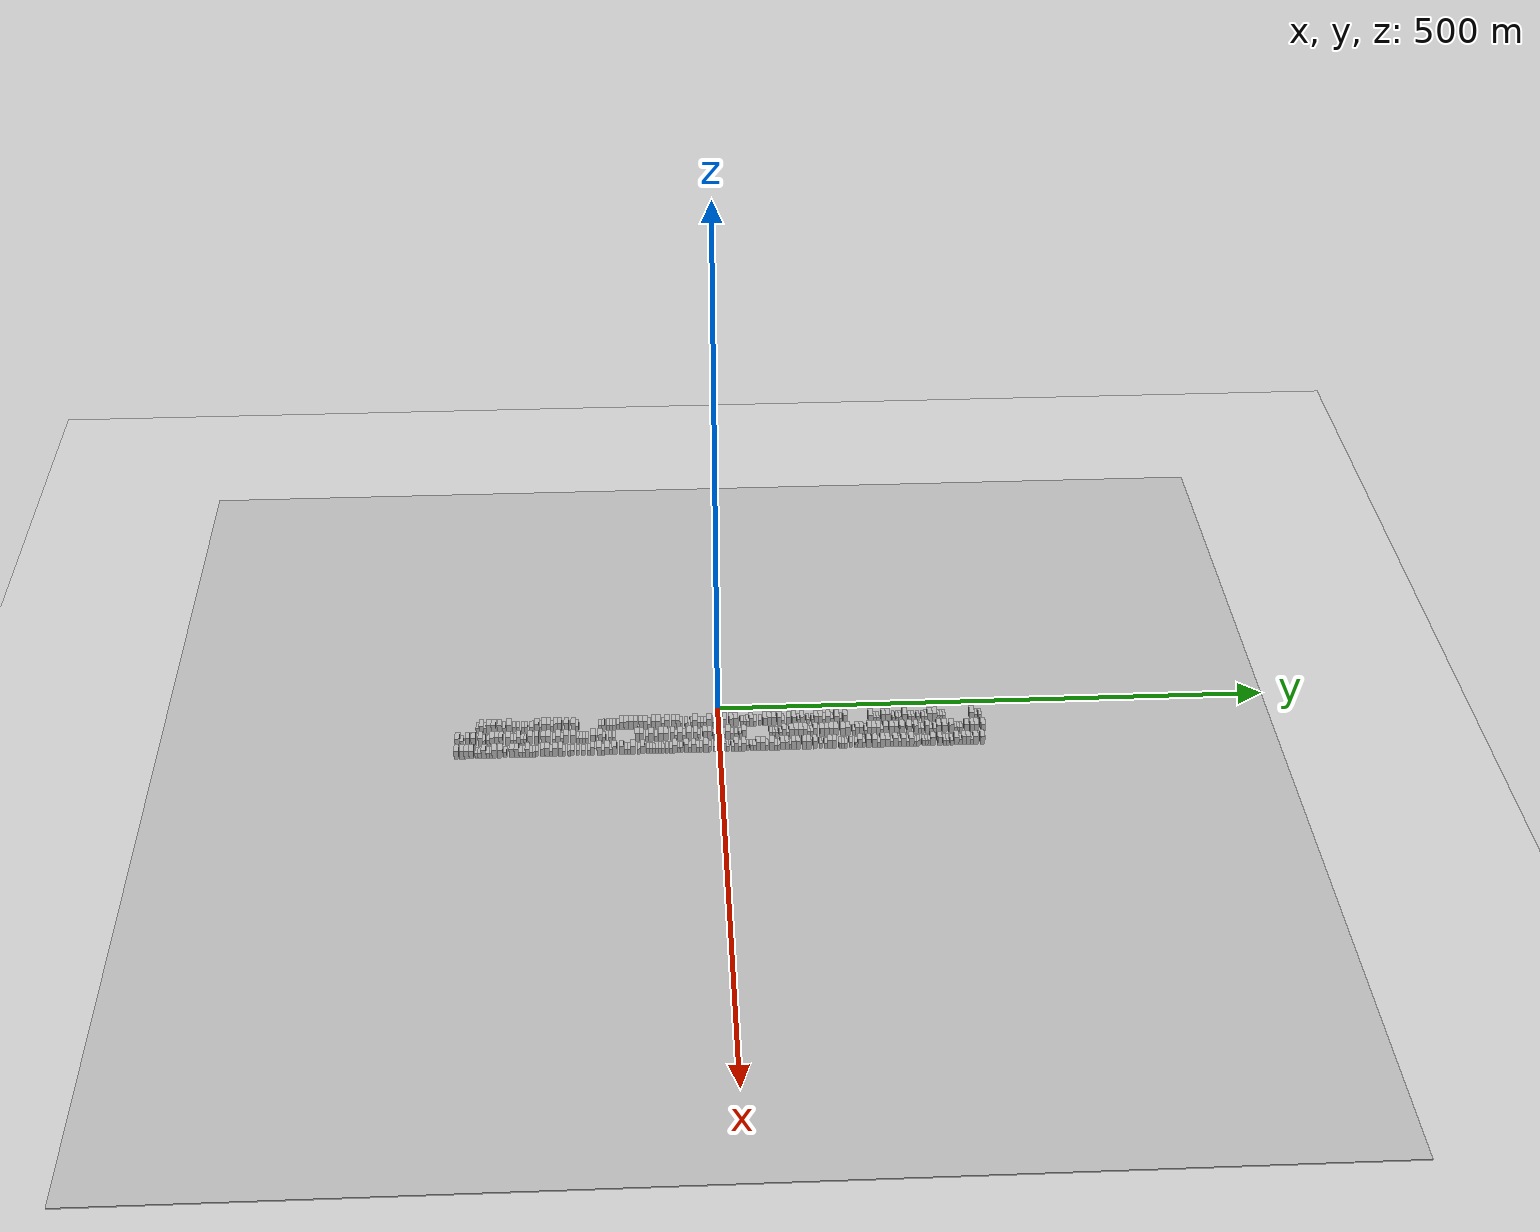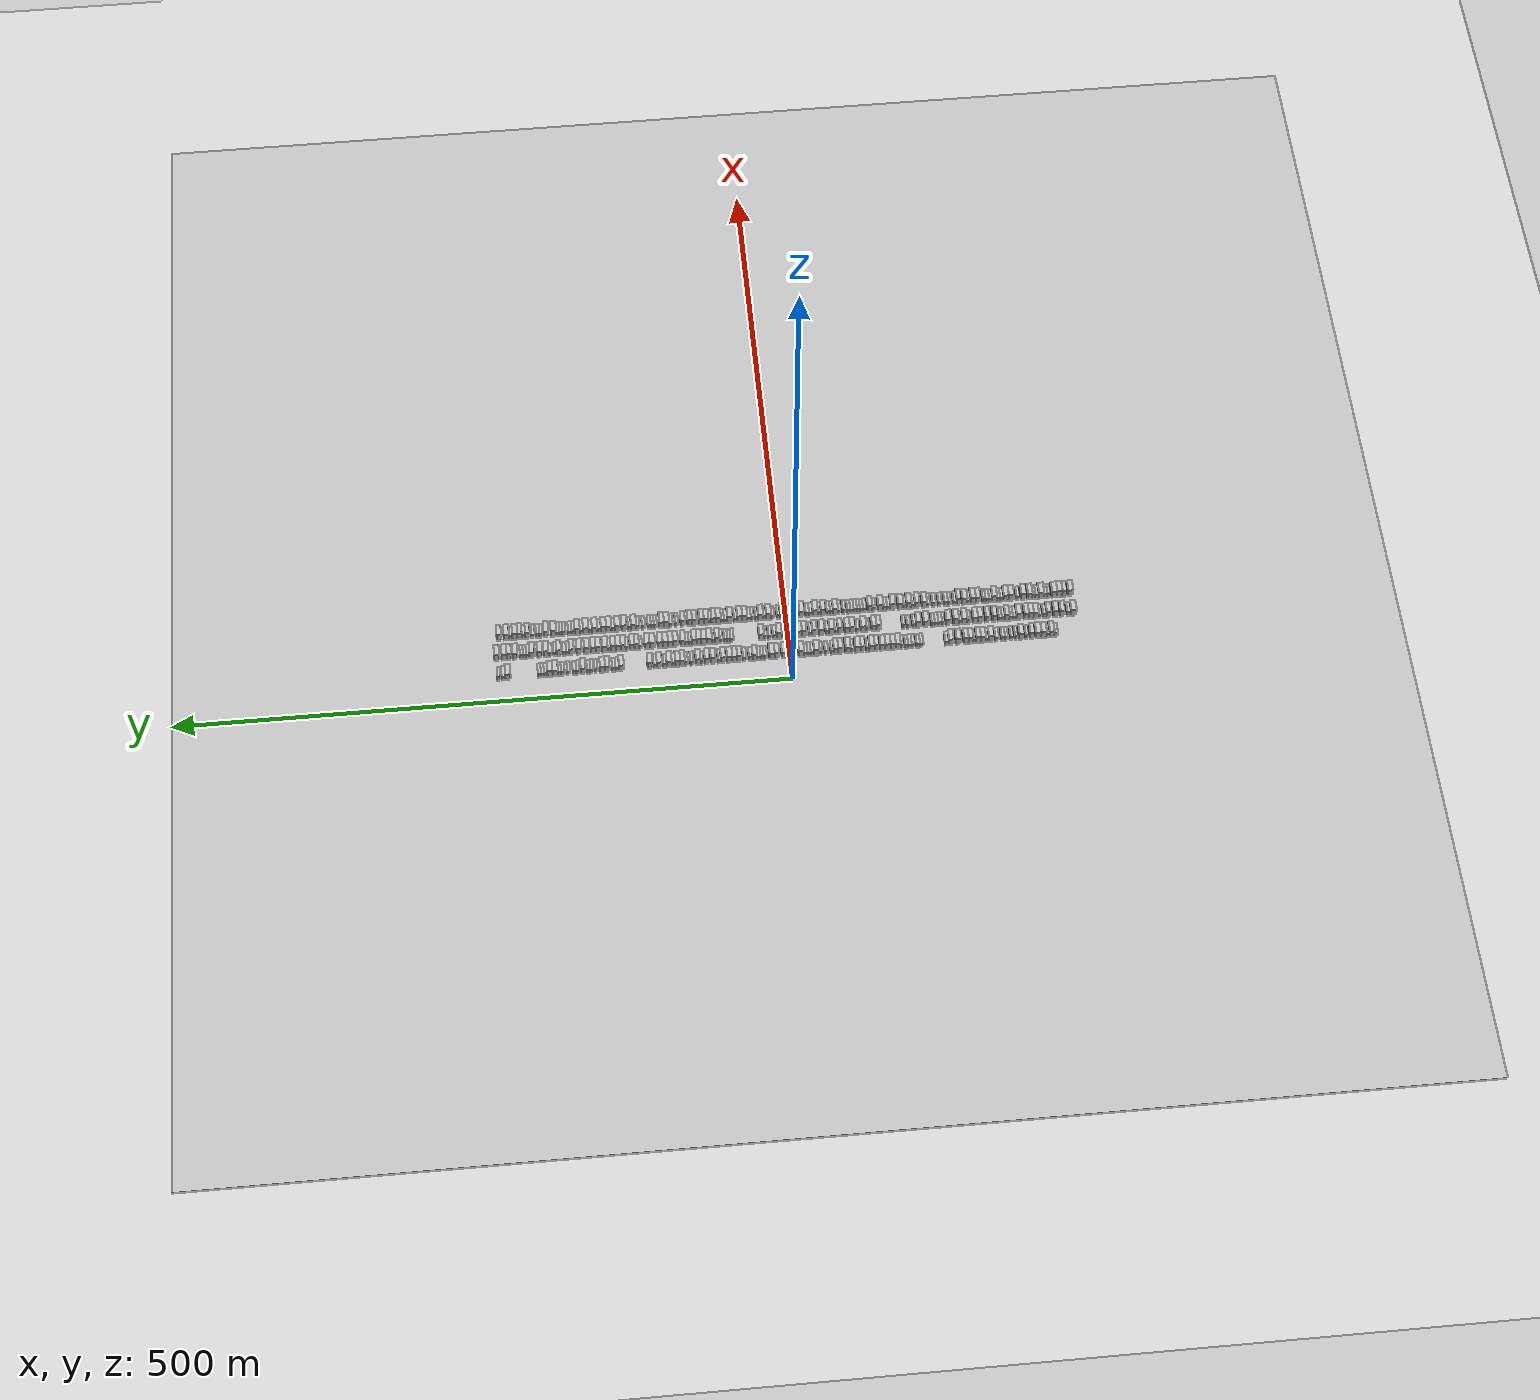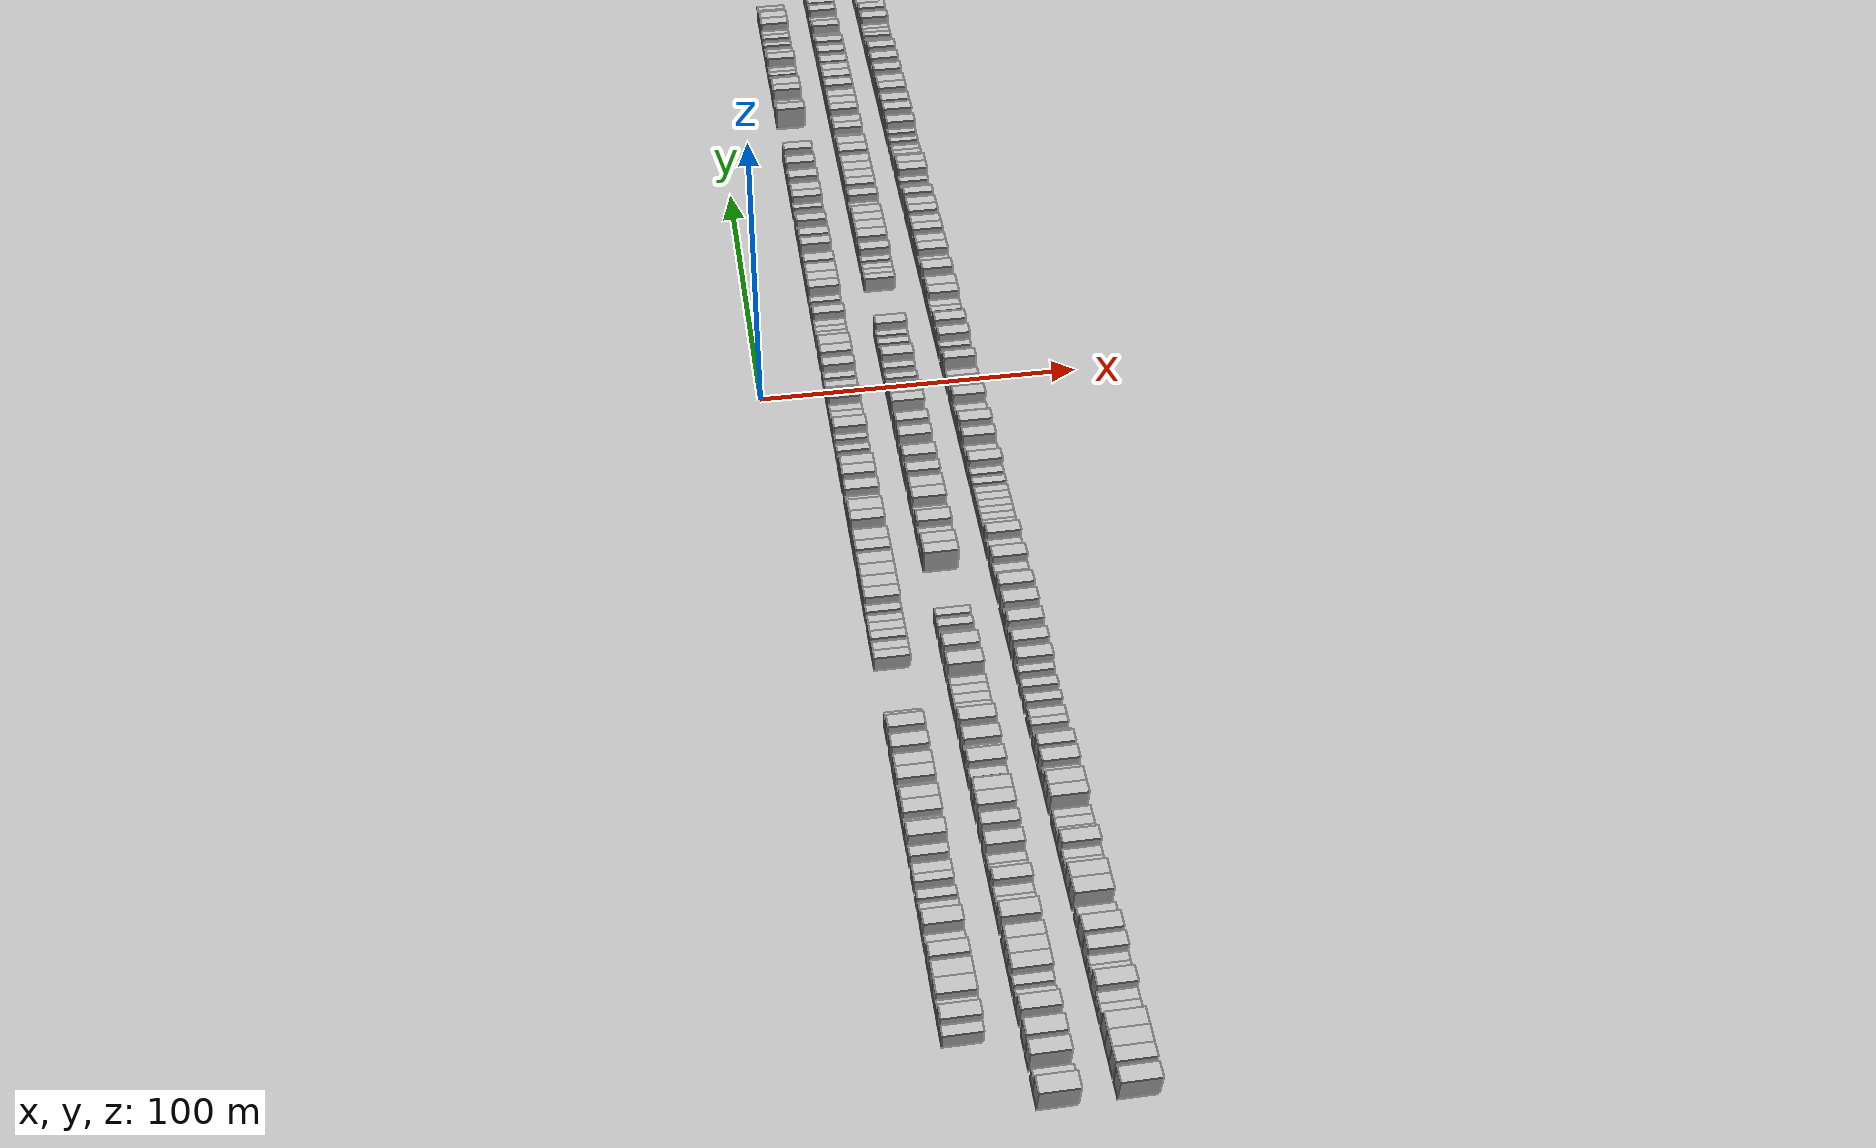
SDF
<?xml version="1.0" encoding="utf-8"?>

<sdf version="1.6">

   <world name="default">

      <gui fullscreen="0">

         <camera name="user_camera">

            <pose>-15 0 4.57585 0 0 0</pose>

            <view_controller>orbit</view_controller>

         </camera>

      </gui>

      <scene>

         <sky>

           <clouds>

             <speed>12</speed>

           </clouds>

         </sky>

         <ambient>0.4 0.4 0.4 1</ambient>

         <background>0.7 0.7 0.7 1</background>

         <shadows>1</shadows>

      </scene>

      <gravity>0 0 -9.8066</gravity>

      <magnetic_field>6e-06 2.3e-05 -4.2e-05</magnetic_field>

      <physics default="0" name="default_physics" type="ode">

         <ode>

            <solver>

               <type>quick</type>

               <iters>10</iters>

               <sor>1.0</sor>

               <use_dynamic_moi_rescaling>0</use_dynamic_moi_rescaling>

            </solver>

            <constraints>

               <cfm>0</cfm>

               <erp>0.2</erp>

               <contact_max_correcting_vel>100</contact_max_correcting_vel>

               <contact_surface_layer>0.001</contact_surface_layer>

            </constraints>

         </ode>

         <max_step_size>0.004</max_step_size>

         <real_time_factor>1</real_time_factor>

         <real_time_update_rate>250</real_time_update_rate>

      </physics>

      <light name="sun" type="directional">

         <cast_shadows>1</cast_shadows>

         <pose>0 0 10 0 0 0</pose>

         <diffuse>0.8 0.8 0.8 1</diffuse>

         <specular>0.2 0.2 0.2 1</specular>

         <attenuation>

            <range>1000</range>

            <constant>0.9</constant>

            <linear>0.01</linear>

            <quadratic>0.001</quadratic>

         </attenuation>

         <direction>-0.5 0.1 -0.9</direction>

      </light>

      <include>

         <name>ground_plane_1</name>

         <uri>model://HANNAS_ground_plane</uri>

         <pose>0 0 0  0 0 0</pose>

      </include>

      <include>

         <name>ground_plane_2</name>

         <uri>model://HANNAS_ground_plane</uri>

         <pose>100 0 0  0 0 0</pose>

      </include>

      <model name="building_1">

         <static>1</static>

         <pose frame="">25.0000 -216.6953 0 0.000000 0.000000 0.000000</pose>

         <link name="link">

            <pose frame="">0 0 3.00 0 0 0</pose>

            <collision name="collision">

               <geometry>

                  <box>

                     <size>10.0000 2.8698 6.0000</size>

                  </box>

               </geometry>

               <max_contacts>10</max_contacts>

               <surface>

                  <contact>

                     <ode/>

                  </contact>

                  <bounce/>

                  <friction>

                     <torsional>

                        <ode/>

                     </torsional>

                     <ode/>

                  </friction>

               </surface>

            </collision>

            <visual name="visual">

               <cast_shadows>0</cast_shadows>

               <geometry>

                  <box>

                     <size>10.0000 2.8698 6.0000</size>

                  </box>

               </geometry>

               <material>

                  <script>

                     <uri>model://HANNAS_wall/materials/scripts</uri>

                     <uri>model://HANNAS_wall/materials/textures</uri>

                     <name>vrc/HANNAS_wall</name>

                  </script>

               </material>

            </visual>

            <self_collide>0</self_collide>

            <enable_wind>0</enable_wind>

            <kinematic>0</kinematic>

         </link>

      </model>

      <model name="building_2">

         <static>1</static>

         <pose frame="">25.0000 -213.3441 0 0.000000 0.000000 0.000000</pose>

         <link name="link">

            <pose frame="">0 0 4.50 0 0 0</pose>

            <collision name="collision">

               <geometry>

                  <box>

                     <size>10.0000 3.8325 9.0000</size>

                  </box>

               </geometry>

               <max_contacts>10</max_contacts>

               <surface>

                  <contact>

                     <ode/>

                  </contact>

                  <bounce/>

                  <friction>

                     <torsional>

                        <ode/>

                     </torsional>

                     <ode/>

                  </friction>

               </surface>

            </collision>

            <visual name="visual">

               <cast_shadows>0</cast_shadows>

               <geometry>

                  <box>

                     <size>10.0000 3.8325 9.0000</size>

                  </box>

               </geometry>

               <material>

                  <script>

                     <uri>model://HANNAS_wall/materials/scripts</uri>

                     <uri>model://HANNAS_wall/materials/textures</uri>

                     <name>vrc/HANNAS_wall</name>

                  </script>

               </material>

            </visual>

            <self_collide>0</self_collide>

            <enable_wind>0</enable_wind>

            <kinematic>0</kinematic>

         </link>

      </model>

      <model name="building_3">

         <static>1</static>

         <pose frame="">25.0000 -210.1695 0 0.000000 0.000000 0.000000</pose>

         <link name="link">

            <pose frame="">0 0 3.00 0 0 0</pose>

            <collision name="collision">

               <geometry>

                  <box>

                     <size>10.0000 2.5166 6.0000</size>

                  </box>

               </geometry>

               <max_contacts>10</max_contacts>

               <surface>

                  <contact>

                     <ode/>

                  </contact>

                  <bounce/>

                  <friction>

                     <torsional>

                        <ode/>

                     </torsional>

                     <ode/>

                  </friction>

               </surface>

            </collision>

            <visual name="visual">

               <cast_shadows>0</cast_shadows>

               <geometry>

                  <box>

                     <size>10.0000 2.5166 6.0000</size>

                  </box>

               </geometry>

               <material>

                  <script>

                     <uri>model://HANNAS_wall/materials/scripts</uri>

                     <uri>model://HANNAS_wall/materials/textures</uri>

                     <name>vrc/HANNAS_wall</name>

                  </script>

               </material>

            </visual>

            <self_collide>0</self_collide>

            <enable_wind>0</enable_wind>

            <kinematic>0</kinematic>

         </link>

      </model>

      <model name="building_4">

         <static>1</static>

         <pose frame="">25.0000 -206.7211 0 0.000000 0.000000 0.000000</pose>

         <link name="link">

            <pose frame="">0 0 4.50 0 0 0</pose>

            <collision name="collision">

               <geometry>

                  <box>

                     <size>10.0000 4.3803 9.0000</size>

                  </box>

               </geometry>

               <max_contacts>10</max_contacts>

               <surface>

                  <contact>

                     <ode/>

                  </contact>

                  <bounce/>

                  <friction>

                     <torsional>

                        <ode/>

                     </torsional>

                     <ode/>

                  </friction>

               </surface>

            </collision>

            <visual name="visual">

               <cast_shadows>0</cast_shadows>

               <geometry>

                  <box>

                     <size>10.0000 4.3803 9.0000</size>

                  </box>

               </geometry>

               <material>

                  <script>

                     <uri>model://HANNAS_wall/materials/scripts</uri>

                     <uri>model://HANNAS_wall/materials/textures</uri>

                     <name>vrc/HANNAS_wall</name>

                  </script>

               </material>

            </visual>

            <self_collide>0</self_collide>

            <enable_wind>0</enable_wind>

            <kinematic>0</kinematic>

         </link>

      </model>

      <model name="building_5">

         <static>1</static>

         <pose frame="">25.0000 -202.3341 0 0.000000 0.000000 0.000000</pose>

         <link name="link">

            <pose frame="">0 0 4.50 0 0 0</pose>

            <collision name="collision">

               <geometry>

                  <box>

                     <size>10.0000 4.3935 9.0000</size>

                  </box>

               </geometry>

               <max_contacts>10</max_contacts>

               <surface>

                  <contact>

                     <ode/>

                  </contact>

                  <bounce/>

                  <friction>

                     <torsional>

                        <ode/>

                     </torsional>

                     <ode/>

                  </friction>

               </surface>

            </collision>

            <visual name="visual">

               <cast_shadows>0</cast_shadows>

               <geometry>

                  <box>

                     <size>10.0000 4.3935 9.0000</size>

                  </box>

               </geometry>

               <material>

                  <script>

                     <uri>model://HANNAS_wall/materials/scripts</uri>

                     <uri>model://HANNAS_wall/materials/textures</uri>

                     <name>vrc/HANNAS_wall</name>

                  </script>

               </material>

            </visual>

            <self_collide>0</self_collide>

            <enable_wind>0</enable_wind>

            <kinematic>0</kinematic>

         </link>

      </model>

      <model name="building_6">

         <static>1</static>

         <pose frame="">25.0000 -197.2362 0 0.000000 0.000000 0.000000</pose>

         <link name="link">

            <pose frame="">0 0 4.50 0 0 0</pose>

            <collision name="collision">

               <geometry>

                  <box>

                     <size>10.0000 3.8024 9.0000</size>

                  </box>

               </geometry>

               <max_contacts>10</max_contacts>

               <surface>

                  <contact>

                     <ode/>

                  </contact>

                  <bounce/>

                  <friction>

                     <torsional>

                        <ode/>

                     </torsional>

                     <ode/>

                  </friction>

               </surface>

            </collision>

            <visual name="visual">

               <cast_shadows>0</cast_shadows>

               <geometry>

                  <box>

                     <size>10.0000 3.8024 9.0000</size>

                  </box>

               </geometry>

               <material>

                  <script>

                     <uri>model://HANNAS_wall/materials/scripts</uri>

                     <uri>model://HANNAS_wall/materials/textures</uri>

                     <name>vrc/HANNAS_wall</name>

                  </script>

               </material>

            </visual>

            <self_collide>0</self_collide>

            <enable_wind>0</enable_wind>

            <kinematic>0</kinematic>

         </link>

      </model>

      <model name="building_7">

         <static>1</static>

         <pose frame="">25.0000 -193.0057 0 0.000000 0.000000 0.000000</pose>

         <link name="link">

            <pose frame="">0 0 3.00 0 0 0</pose>

            <collision name="collision">

               <geometry>

                  <box>

                     <size>10.0000 2.6584 6.0000</size>

                  </box>

               </geometry>

               <max_contacts>10</max_contacts>

               <surface>

                  <contact>

                     <ode/>

                  </contact>

                  <bounce/>

                  <friction>

                     <torsional>

                        <ode/>

                     </torsional>

                     <ode/>

                  </friction>

               </surface>

            </collision>

            <visual name="visual">

               <cast_shadows>0</cast_shadows>

               <geometry>

                  <box>

                     <size>10.0000 2.6584 6.0000</size>

                  </box>

               </geometry>

               <material>

                  <script>

                     <uri>model://HANNAS_wall/materials/scripts</uri>

                     <uri>model://HANNAS_wall/materials/textures</uri>

                     <name>vrc/HANNAS_wall</name>

                  </script>

               </material>

            </visual>

            <self_collide>0</self_collide>

            <enable_wind>0</enable_wind>

            <kinematic>0</kinematic>

         </link>

      </model>

      <model name="building_8">

         <static>1</static>

         <pose frame="">25.0000 -188.5366 0 0.000000 0.000000 0.000000</pose>

         <link name="link">

            <pose frame="">0 0 4.50 0 0 0</pose>

            <collision name="collision">

               <geometry>

                  <box>

                     <size>10.0000 4.2798 9.0000</size>

                  </box>

               </geometry>

               <max_contacts>10</max_contacts>

               <surface>

                  <contact>

                     <ode/>

                  </contact>

                  <bounce/>

                  <friction>

                     <torsional>

                        <ode/>

                     </torsional>

                     <ode/>

                  </friction>

               </surface>

            </collision>

            <visual name="visual">

               <cast_shadows>0</cast_shadows>

               <geometry>

                  <box>

                     <size>10.0000 4.2798 9.0000</size>

                  </box>

               </geometry>

               <material>

                  <script>

                     <uri>model://HANNAS_wall/materials/scripts</uri>

                     <uri>model://HANNAS_wall/materials/textures</uri>

                     <name>vrc/HANNAS_wall</name>

                  </script>

               </material>

            </visual>

            <self_collide>0</self_collide>

            <enable_wind>0</enable_wind>

            <kinematic>0</kinematic>

         </link>

      </model>

      <model name="building_9">

         <static>1</static>

         <pose frame="">25.0000 -184.1848 0 0.000000 0.000000 0.000000</pose>

         <link name="link">

            <pose frame="">0 0 3.00 0 0 0</pose>

            <collision name="collision">

               <geometry>

                  <box>

                     <size>10.0000 2.4239 6.0000</size>

                  </box>

               </geometry>

               <max_contacts>10</max_contacts>

               <surface>

                  <contact>

                     <ode/>

                  </contact>

                  <bounce/>

                  <friction>

                     <torsional>

                        <ode/>

                     </torsional>

                     <ode/>

                  </friction>

               </surface>

            </collision>

            <visual name="visual">

               <cast_shadows>0</cast_shadows>

               <geometry>

                  <box>

                     <size>10.0000 2.4239 6.0000</size>

                  </box>

               </geometry>

               <material>

                  <script>

                     <uri>model://HANNAS_wall/materials/scripts</uri>

                     <uri>model://HANNAS_wall/materials/textures</uri>

                     <name>vrc/HANNAS_wall</name>

                  </script>

               </material>

            </visual>

            <self_collide>0</self_collide>

            <enable_wind>0</enable_wind>

            <kinematic>0</kinematic>

         </link>

      </model>

      <model name="building_10">

         <static>1</static>

         <pose frame="">25.0000 -180.6165 0 0.000000 0.000000 0.000000</pose>

         <link name="link">

            <pose frame="">0 0 3.00 0 0 0</pose>

            <collision name="collision">

               <geometry>

                  <box>

                     <size>10.0000 2.7126 6.0000</size>

                  </box>

               </geometry>

               <max_contacts>10</max_contacts>

               <surface>

                  <contact>

                     <ode/>

                  </contact>

                  <bounce/>

                  <friction>

                     <torsional>

                        <ode/>

                     </torsional>

                     <ode/>

                  </friction>

               </surface>

            </collision>

            <visual name="visual">

               <cast_shadows>0</cast_shadows>

               <geometry>

                  <box>

                     <size>10.0000 2.7126 6.0000</size>

                  </box>

               </geometry>

               <material>

                  <script>

                     <uri>model://HANNAS_wall/materials/scripts</uri>

                     <uri>model://HANNAS_wall/materials/textures</uri>

                     <name>vrc/HANNAS_wall</name>

                  </script>

               </material>

            </visual>

            <self_collide>0</self_collide>

            <enable_wind>0</enable_wind>

            <kinematic>0</kinematic>

         </link>

      </model>

      <model name="building_11">

         <static>1</static>

         <pose frame="">25.0000 -176.0593 0 0.000000 0.000000 0.000000</pose>

         <link name="link">

            <pose frame="">0 0 3.00 0 0 0</pose>

            <collision name="collision">

               <geometry>

                  <box>

                     <size>10.0000 2.4017 6.0000</size>

                  </box>

               </geometry>

               <max_contacts>10</max_contacts>

               <surface>

                  <contact>

                     <ode/>

                  </contact>

                  <bounce/>

                  <friction>

                     <torsional>

                        <ode/>

                     </torsional>

                     <ode/>

                  </friction>

               </surface>

            </collision>

            <visual name="visual">

               <cast_shadows>0</cast_shadows>

               <geometry>

                  <box>

                     <size>10.0000 2.4017 6.0000</size>

                  </box>

               </geometry>

               <material>

                  <script>

                     <uri>model://HANNAS_wall/materials/scripts</uri>

                     <uri>model://HANNAS_wall/materials/textures</uri>

                     <name>vrc/HANNAS_wall</name>

                  </script>

               </material>

            </visual>

            <self_collide>0</self_collide>

            <enable_wind>0</enable_wind>

            <kinematic>0</kinematic>

         </link>

      </model>

      <model name="building_12">

         <static>1</static>

         <pose frame="">25.0000 -173.3840 0 0.000000 0.000000 0.000000</pose>

         <link name="link">

            <pose frame="">0 0 3.00 0 0 0</pose>

            <collision name="collision">

               <geometry>

                  <box>

                     <size>10.0000 2.9487 6.0000</size>

                  </box>

               </geometry>

               <max_contacts>10</max_contacts>

               <surface>

                  <contact>

                     <ode/>

                  </contact>

                  <bounce/>

                  <friction>

                     <torsional>

                        <ode/>

                     </torsional>

                     <ode/>

                  </friction>

               </surface>

            </collision>

            <visual name="visual">

               <cast_shadows>0</cast_shadows>

               <geometry>

                  <box>

                     <size>10.0000 2.9487 6.0000</size>

                  </box>

               </geometry>

               <material>

                  <script>

                     <uri>model://HANNAS_wall/materials/scripts</uri>

                     <uri>model://HANNAS_wall/materials/textures</uri>

                     <name>vrc/HANNAS_wall</name>

                  </script>

               </material>

            </visual>

            <self_collide>0</self_collide>

            <enable_wind>0</enable_wind>

            <kinematic>0</kinematic>

         </link>

      </model>

      <model name="building_13">

         <static>1</static>

         <pose frame="">25.0000 -168.4103 0 0.000000 0.000000 0.000000</pose>

         <link name="link">

            <pose frame="">0 0 3.00 0 0 0</pose>

            <collision name="collision">

               <geometry>

                  <box>

                     <size>10.0000 2.9987 6.0000</size>

                  </box>

               </geometry>

               <max_contacts>10</max_contacts>

               <surface>

                  <contact>

                     <ode/>

                  </contact>

                  <bounce/>

                  <friction>

                     <torsional>

                        <ode/>

                     </torsional>

                     <ode/>

                  </friction>

               </surface>

            </collision>

            <visual name="visual">

               <cast_shadows>0</cast_shadows>

               <geometry>

                  <box>

                     <size>10.0000 2.9987 6.0000</size>

                  </box>

               </geometry>

               <material>

                  <script>

                     <uri>model://HANNAS_wall/materials/scripts</uri>

                     <uri>model://HANNAS_wall/materials/textures</uri>

                     <name>vrc/HANNAS_wall</name>

                  </script>

               </material>

            </visual>

            <self_collide>0</self_collide>

            <enable_wind>0</enable_wind>

            <kinematic>0</kinematic>

         </link>

      </model>

      <model name="building_14">

         <static>1</static>

         <pose frame="">25.0000 -163.7138 0 0.000000 0.000000 0.000000</pose>

         <link name="link">

            <pose frame="">0 0 4.50 0 0 0</pose>

            <collision name="collision">

               <geometry>

                  <box>

                     <size>10.0000 4.3944 9.0000</size>

                  </box>

               </geometry>

               <max_contacts>10</max_contacts>

               <surface>

                  <contact>

                     <ode/>

                  </contact>

                  <bounce/>

                  <friction>

                     <torsional>

                        <ode/>

                     </torsional>

                     <ode/>

                  </friction>

               </surface>

            </collision>

            <visual name="visual">

               <cast_shadows>0</cast_shadows>

               <geometry>

                  <box>

                     <size>10.0000 4.3944 9.0000</size>

                  </box>

               </geometry>

               <material>

                  <script>

                     <uri>model://HANNAS_wall/materials/scripts</uri>

                     <uri>model://HANNAS_wall/materials/textures</uri>

                     <name>vrc/HANNAS_wall</name>

                  </script>

               </material>

            </visual>

            <self_collide>0</self_collide>

            <enable_wind>0</enable_wind>

            <kinematic>0</kinematic>

         </link>

      </model>

      <model name="building_15">

         <static>1</static>

         <pose frame="">25.0000 -160.2892 0 0.000000 0.000000 0.000000</pose>

         <link name="link">

            <pose frame="">0 0 3.00 0 0 0</pose>

            <collision name="collision">

               <geometry>

                  <box>

                     <size>10.0000 2.4548 6.0000</size>

                  </box>

               </geometry>

               <max_contacts>10</max_contacts>

               <surface>

                  <contact>

                     <ode/>

                  </contact>

                  <bounce/>

                  <friction>

                     <torsional>

                        <ode/>

                     </torsional>

                     <ode/>

                  </friction>

               </surface>

            </collision>

            <visual name="visual">

               <cast_shadows>0</cast_shadows>

               <geometry>

                  <box>

                     <size>10.0000 2.4548 6.0000</size>

                  </box>

               </geometry>

               <material>

                  <script>

                     <uri>model://HANNAS_wall/materials/scripts</uri>

                     <uri>model://HANNAS_wall/materials/textures</uri>

                     <name>vrc/HANNAS_wall</name>

                  </script>

               </material>

            </visual>

            <self_collide>0</self_collide>

            <enable_wind>0</enable_wind>

            <kinematic>0</kinematic>

         </link>

      </model>

      <model name="building_16">

         <static>1</static>

         <pose frame="">25.0000 -157.0114 0 0.000000 0.000000 0.000000</pose>

         <link name="link">

            <pose frame="">0 0 4.50 0 0 0</pose>

            <collision name="collision">

               <geometry>

                  <box>

                     <size>10.0000 4.1008 9.0000</size>

                  </box>

               </geometry>

               <max_contacts>10</max_contacts>

               <surface>

                  <contact>

                     <ode/>

                  </contact>

                  <bounce/>

                  <friction>

                     <torsional>

                        <ode/>

                     </torsional>

                     <ode/>

                  </friction>

               </surface>

            </collision>

            <visual name="visual">

               <cast_shadows>0</cast_shadows>

               <geometry>

                  <box>

                     <size>10.0000 4.1008 9.0000</size>

                  </box>

               </geometry>

               <material>

                  <script>

                     <uri>model://HANNAS_wall/materials/scripts</uri>

                     <uri>model://HANNAS_wall/materials/textures</uri>

                     <name>vrc/HANNAS_wall</name>

                  </script>

               </material>

            </visual>

            <self_collide>0</self_collide>

            <enable_wind>0</enable_wind>

            <kinematic>0</kinematic>

         </link>

      </model>

      <model name="building_17">

         <static>1</static>

         <pose frame="">25.0000 -153.1219 0 0.000000 0.000000 0.000000</pose>

         <link name="link">

            <pose frame="">0 0 4.50 0 0 0</pose>

            <collision name="collision">

               <geometry>

                  <box>

                     <size>10.0000 3.6781 9.0000</size>

                  </box>

               </geometry>

               <max_contacts>10</max_contacts>

               <surface>

                  <contact>

                     <ode/>

                  </contact>

                  <bounce/>

                  <friction>

                     <torsional>

                        <ode/>

                     </torsional>

                     <ode/>

                  </friction>

               </surface>

            </collision>

            <visual name="visual">

               <cast_shadows>0</cast_shadows>

               <geometry>

                  <box>

                     <size>10.0000 3.6781 9.0000</size>

                  </box>

               </geometry>

               <material>

                  <script>

                     <uri>model://HANNAS_wall/materials/scripts</uri>

                     <uri>model://HANNAS_wall/materials/textures</uri>

                     <name>vrc/HANNAS_wall</name>

                  </script>

               </material>

            </visual>

            <self_collide>0</self_collide>

            <enable_wind>0</enable_wind>

            <kinematic>0</kinematic>

         </link>

      </model>

      <model name="building_18">

         <static>1</static>

         <pose frame="">25.0000 -150.0791 0 0.000000 0.000000 0.000000</pose>

         <link name="link">

            <pose frame="">0 0 3.00 0 0 0</pose>

            <collision name="collision">

               <geometry>

                  <box>

                     <size>10.0000 2.4076 6.0000</size>

                  </box>

               </geometry>

               <max_contacts>10</max_contacts>

               <surface>

                  <contact>

                     <ode/>

                  </contact>

                  <bounce/>

                  <friction>

                     <torsional>

                        <ode/>

                     </torsional>

                     <ode/>

                  </friction>

               </surface>

            </collision>

            <visual name="visual">

               <cast_shadows>0</cast_shadows>

               <geometry>

                  <box>

                     <size>10.0000 2.4076 6.0000</size>

                  </box>

               </geometry>

               <material>

                  <script>

                     <uri>model://HANNAS_wall/materials/scripts</uri>

                     <uri>model://HANNAS_wall/materials/textures</uri>

                     <name>vrc/HANNAS_wall</name>

                  </script>

               </material>

            </visual>

            <self_collide>0</self_collide>

            <enable_wind>0</enable_wind>

            <kinematic>0</kinematic>

         </link>

      </model>

      <model name="building_19">

         <static>1</static>

         <pose frame="">25.0000 -146.8874 0 0.000000 0.000000 0.000000</pose>

         <link name="link">

            <pose frame="">0 0 4.50 0 0 0</pose>

            <collision name="collision">

               <geometry>

                  <box>

                     <size>10.0000 3.9758 9.0000</size>

                  </box>

               </geometry>

               <max_contacts>10</max_contacts>

               <surface>

                  <contact>

                     <ode/>

                  </contact>

                  <bounce/>

                  <friction>

                     <torsional>

                        <ode/>

                     </torsional>

                     <ode/>

                  </friction>

               </surface>

            </collision>

            <visual name="visual">

               <cast_shadows>0</cast_shadows>

               <geometry>

                  <box>

                     <size>10.0000 3.9758 9.0000</size>

                  </box>

               </geometry>

               <material>

                  <script>

                     <uri>model://HANNAS_wall/materials/scripts</uri>

                     <uri>model://HANNAS_wall/materials/textures</uri>

                     <name>vrc/HANNAS_wall</name>

                  </script>

               </material>

            </visual>

            <self_collide>0</self_collide>

            <enable_wind>0</enable_wind>

            <kinematic>0</kinematic>

         </link>

      </model>

      <model name="building_20">

         <static>1</static>

         <pose frame="">25.0000 -143.0052 0 0.000000 0.000000 0.000000</pose>

         <link name="link">

            <pose frame="">0 0 4.50 0 0 0</pose>

            <collision name="collision">

               <geometry>

                  <box>

                     <size>10.0000 3.7887 9.0000</size>

                  </box>

               </geometry>

               <max_contacts>10</max_contacts>

               <surface>

                  <contact>

                     <ode/>

                  </contact>

                  <bounce/>

                  <friction>

                     <torsional>

                        <ode/>

                     </torsional>

                     <ode/>

                  </friction>

               </surface>

            </collision>

            <visual name="visual">

               <cast_shadows>0</cast_shadows>

               <geometry>

                  <box>

                     <size>10.0000 3.7887 9.0000</size>

                  </box>

               </geometry>

               <material>

                  <script>

                     <uri>model://HANNAS_wall/materials/scripts</uri>

                     <uri>model://HANNAS_wall/materials/textures</uri>

                     <name>vrc/HANNAS_wall</name>

                  </script>

               </material>

            </visual>

            <self_collide>0</self_collide>

            <enable_wind>0</enable_wind>

            <kinematic>0</kinematic>

         </link>

      </model>

      <model name="building_21">

         <static>1</static>

         <pose frame="">25.0000 -136.9755 0 0.000000 0.000000 0.000000</pose>

         <link name="link">

            <pose frame="">0 0 4.50 0 0 0</pose>

            <collision name="collision">

               <geometry>

                  <box>

                     <size>10.0000 4.2706 9.0000</size>

                  </box>

               </geometry>

               <max_contacts>10</max_contacts>

               <surface>

                  <contact>

                     <ode/>

                  </contact>

                  <bounce/>

                  <friction>

                     <torsional>

                        <ode/>

                     </torsional>

                     <ode/>

                  </friction>

               </surface>

            </collision>

            <visual name="visual">

               <cast_shadows>0</cast_shadows>

               <geometry>

                  <box>

                     <size>10.0000 4.2706 9.0000</size>

                  </box>

               </geometry>

               <material>

                  <script>

                     <uri>model://HANNAS_wall/materials/scripts</uri>

                     <uri>model://HANNAS_wall/materials/textures</uri>

                     <name>vrc/HANNAS_wall</name>

                  </script>

               </material>

            </visual>

            <self_collide>0</self_collide>

            <enable_wind>0</enable_wind>

            <kinematic>0</kinematic>

         </link>

      </model>

      <model name="building_22">

         <static>1</static>

         <pose frame="">25.0000 -130.8090 0 0.000000 0.000000 0.000000</pose>

         <link name="link">

            <pose frame="">0 0 4.50 0 0 0</pose>

            <collision name="collision">

               <geometry>

                  <box>

                     <size>10.0000 4.0625 9.0000</size>

                  </box>

               </geometry>

               <max_contacts>10</max_contacts>

               <surface>

                  <contact>

                     <ode/>

                  </contact>

                  <bounce/>

                  <friction>

                     <torsional>

                        <ode/>

                     </torsional>

                     <ode/>

                  </friction>

               </surface>

            </collision>

            <visual name="visual">

               <cast_shadows>0</cast_shadows>

               <geometry>

                  <box>

                     <size>10.0000 4.0625 9.0000</size>

                  </box>

               </geometry>

               <material>

                  <script>

                     <uri>model://HANNAS_wall/materials/scripts</uri>

                     <uri>model://HANNAS_wall/materials/textures</uri>

                     <name>vrc/HANNAS_wall</name>

                  </script>

               </material>

            </visual>

            <self_collide>0</self_collide>

            <enable_wind>0</enable_wind>

            <kinematic>0</kinematic>

         </link>

      </model>

      <model name="building_23">

         <static>1</static>

         <pose frame="">25.0000 -127.3455 0 0.000000 0.000000 0.000000</pose>

         <link name="link">

            <pose frame="">0 0 3.00 0 0 0</pose>

            <collision name="collision">

               <geometry>

                  <box>

                     <size>10.0000 2.8643 6.0000</size>

                  </box>

               </geometry>

               <max_contacts>10</max_contacts>

               <surface>

                  <contact>

                     <ode/>

                  </contact>

                  <bounce/>

                  <friction>

                     <torsional>

                        <ode/>

                     </torsional>

                     <ode/>

                  </friction>

               </surface>

            </collision>

            <visual name="visual">

               <cast_shadows>0</cast_shadows>

               <geometry>

                  <box>

                     <size>10.0000 2.8643 6.0000</size>

                  </box>

               </geometry>

               <material>

                  <script>

                     <uri>model://HANNAS_wall/materials/scripts</uri>

                     <uri>model://HANNAS_wall/materials/textures</uri>

                     <name>vrc/HANNAS_wall</name>

                  </script>

               </material>

            </visual>

            <self_collide>0</self_collide>

            <enable_wind>0</enable_wind>

            <kinematic>0</kinematic>

         </link>

      </model>

      <model name="building_24">

         <static>1</static>

         <pose frame="">25.0000 -106.6029 0 0.000000 0.000000 0.000000</pose>

         <link name="link">

            <pose frame="">0 0 3.00 0 0 0</pose>

            <collision name="collision">

               <geometry>

                  <box>

                     <size>10.0000 2.8736 6.0000</size>

                  </box>

               </geometry>

               <max_contacts>10</max_contacts>

               <surface>

                  <contact>

                     <ode/>

                  </contact>

                  <bounce/>

                  <friction>

                     <torsional>

                        <ode/>

                     </torsional>

                     <ode/>

                  </friction>

               </surface>

            </collision>

            <visual name="visual">

               <cast_shadows>0</cast_shadows>

               <geometry>

                  <box>

                     <size>10.0000 2.8736 6.0000</size>

                  </box>

               </geometry>

               <material>

                  <script>

                     <uri>model://HANNAS_wall/materials/scripts</uri>

                     <uri>model://HANNAS_wall/materials/textures</uri>

                     <name>vrc/HANNAS_wall</name>

                  </script>

               </material>

            </visual>

            <self_collide>0</self_collide>

            <enable_wind>0</enable_wind>

            <kinematic>0</kinematic>

         </link>

      </model>

      <model name="building_25">

         <static>1</static>

         <pose frame="">25.0000 -103.7616 0 0.000000 0.000000 0.000000</pose>

         <link name="link">

            <pose frame="">0 0 3.00 0 0 0</pose>

            <collision name="collision">

               <geometry>

                  <box>

                     <size>10.0000 2.8090 6.0000</size>

                  </box>

               </geometry>

               <max_contacts>10</max_contacts>

               <surface>

                  <contact>

                     <ode/>

                  </contact>

                  <bounce/>

                  <friction>

                     <torsional>

                        <ode/>

                     </torsional>

                     <ode/>

                  </friction>

               </surface>

            </collision>

            <visual name="visual">

               <cast_shadows>0</cast_shadows>

               <geometry>

                  <box>

                     <size>10.0000 2.8090 6.0000</size>

                  </box>

               </geometry>

               <material>

                  <script>

                     <uri>model://HANNAS_wall/materials/scripts</uri>

                     <uri>model://HANNAS_wall/materials/textures</uri>

                     <name>vrc/HANNAS_wall</name>

                  </script>

               </material>

            </visual>

            <self_collide>0</self_collide>

            <enable_wind>0</enable_wind>

            <kinematic>0</kinematic>

         </link>

      </model>

      <model name="building_26">

         <static>1</static>

         <pose frame="">25.0000 -99.9057 0 0.000000 0.000000 0.000000</pose>

         <link name="link">

            <pose frame="">0 0 3.00 0 0 0</pose>

            <collision name="collision">

               <geometry>

                  <box>

                     <size>10.0000 2.9028 6.0000</size>

                  </box>

               </geometry>

               <max_contacts>10</max_contacts>

               <surface>

                  <contact>

                     <ode/>

                  </contact>

                  <bounce/>

                  <friction>

                     <torsional>

                        <ode/>

                     </torsional>

                     <ode/>

                  </friction>

               </surface>

            </collision>

            <visual name="visual">

               <cast_shadows>0</cast_shadows>

               <geometry>

                  <box>

                     <size>10.0000 2.9028 6.0000</size>

                  </box>

               </geometry>

               <material>

                  <script>

                     <uri>model://HANNAS_wall/materials/scripts</uri>

                     <uri>model://HANNAS_wall/materials/textures</uri>

                     <name>vrc/HANNAS_wall</name>

                  </script>

               </material>

            </visual>

            <self_collide>0</self_collide>

            <enable_wind>0</enable_wind>

            <kinematic>0</kinematic>

         </link>

      </model>

      <model name="building_27">

         <static>1</static>

         <pose frame="">25.0000 -97.0012 0 0.000000 0.000000 0.000000</pose>

         <link name="link">

            <pose frame="">0 0 3.00 0 0 0</pose>

            <collision name="collision">

               <geometry>

                  <box>

                     <size>10.0000 2.9063 6.0000</size>

                  </box>

               </geometry>

               <max_contacts>10</max_contacts>

               <surface>

                  <contact>

                     <ode/>

                  </contact>

                  <bounce/>

                  <friction>

                     <torsional>

                        <ode/>

                     </torsional>

                     <ode/>

                  </friction>

               </surface>

            </collision>

            <visual name="visual">

               <cast_shadows>0</cast_shadows>

               <geometry>

                  <box>

                     <size>10.0000 2.9063 6.0000</size>

                  </box>

               </geometry>

               <material>

                  <script>

                     <uri>model://HANNAS_wall/materials/scripts</uri>

                     <uri>model://HANNAS_wall/materials/textures</uri>

                     <name>vrc/HANNAS_wall</name>

                  </script>

               </material>

            </visual>

            <self_collide>0</self_collide>

            <enable_wind>0</enable_wind>

            <kinematic>0</kinematic>

         </link>

      </model>

      <model name="building_28">

         <static>1</static>

         <pose frame="">25.0000 -94.2994 0 0.000000 0.000000 0.000000</pose>

         <link name="link">

            <pose frame="">0 0 3.00 0 0 0</pose>

            <collision name="collision">

               <geometry>

                  <box>

                     <size>10.0000 2.4973 6.0000</size>

                  </box>

               </geometry>

               <max_contacts>10</max_contacts>

               <surface>

                  <contact>

                     <ode/>

                  </contact>

                  <bounce/>

                  <friction>

                     <torsional>

                        <ode/>

                     </torsional>

                     <ode/>

                  </friction>

               </surface>

            </collision>

            <visual name="visual">

               <cast_shadows>0</cast_shadows>

               <geometry>

                  <box>

                     <size>10.0000 2.4973 6.0000</size>

                  </box>

               </geometry>

               <material>

                  <script>

                     <uri>model://HANNAS_wall/materials/scripts</uri>

                     <uri>model://HANNAS_wall/materials/textures</uri>

                     <name>vrc/HANNAS_wall</name>

                  </script>

               </material>

            </visual>

            <self_collide>0</self_collide>

            <enable_wind>0</enable_wind>

            <kinematic>0</kinematic>

         </link>

      </model>

      <model name="building_29">

         <static>1</static>

         <pose frame="">25.0000 -90.7065 0 0.000000 0.000000 0.000000</pose>

         <link name="link">

            <pose frame="">0 0 3.00 0 0 0</pose>

            <collision name="collision">

               <geometry>

                  <box>

                     <size>10.0000 2.6884 6.0000</size>

                  </box>

               </geometry>

               <max_contacts>10</max_contacts>

               <surface>

                  <contact>

                     <ode/>

                  </contact>

                  <bounce/>

                  <friction>

                     <torsional>

                        <ode/>

                     </torsional>

                     <ode/>

                  </friction>

               </surface>

            </collision>

            <visual name="visual">

               <cast_shadows>0</cast_shadows>

               <geometry>

                  <box>

                     <size>10.0000 2.6884 6.0000</size>

                  </box>

               </geometry>

               <material>

                  <script>

                     <uri>model://HANNAS_wall/materials/scripts</uri>

                     <uri>model://HANNAS_wall/materials/textures</uri>

                     <name>vrc/HANNAS_wall</name>

                  </script>

               </material>

            </visual>

            <self_collide>0</self_collide>

            <enable_wind>0</enable_wind>

            <kinematic>0</kinematic>

         </link>

      </model>

      <model name="building_30">

         <static>1</static>

         <pose frame="">25.0000 -87.3513 0 0.000000 0.000000 0.000000</pose>

         <link name="link">

            <pose frame="">0 0 4.50 0 0 0</pose>

            <collision name="collision">

               <geometry>

                  <box>

                     <size>10.0000 4.0220 9.0000</size>

                  </box>

               </geometry>

               <max_contacts>10</max_contacts>

               <surface>

                  <contact>

                     <ode/>

                  </contact>

                  <bounce/>

                  <friction>

                     <torsional>

                        <ode/>

                     </torsional>

                     <ode/>

                  </friction>

               </surface>

            </collision>

            <visual name="visual">

               <cast_shadows>0</cast_shadows>

               <geometry>

                  <box>

                     <size>10.0000 4.0220 9.0000</size>

                  </box>

               </geometry>

               <material>

                  <script>

                     <uri>model://HANNAS_wall/materials/scripts</uri>

                     <uri>model://HANNAS_wall/materials/textures</uri>

                     <name>vrc/HANNAS_wall</name>

                  </script>

               </material>

            </visual>

            <self_collide>0</self_collide>

            <enable_wind>0</enable_wind>

            <kinematic>0</kinematic>

         </link>

      </model>

      <model name="building_31">

         <static>1</static>

         <pose frame="">25.0000 -83.2988 0 0.000000 0.000000 0.000000</pose>

         <link name="link">

            <pose frame="">0 0 4.50 0 0 0</pose>

            <collision name="collision">

               <geometry>

                  <box>

                     <size>10.0000 4.0831 9.0000</size>

                  </box>

               </geometry>

               <max_contacts>10</max_contacts>

               <surface>

                  <contact>

                     <ode/>

                  </contact>

                  <bounce/>

                  <friction>

                     <torsional>

                        <ode/>

                     </torsional>

                     <ode/>

                  </friction>

               </surface>

            </collision>

            <visual name="visual">

               <cast_shadows>0</cast_shadows>

               <geometry>

                  <box>

                     <size>10.0000 4.0831 9.0000</size>

                  </box>

               </geometry>

               <material>

                  <script>

                     <uri>model://HANNAS_wall/materials/scripts</uri>

                     <uri>model://HANNAS_wall/materials/textures</uri>

                     <name>vrc/HANNAS_wall</name>

                  </script>

               </material>

            </visual>

            <self_collide>0</self_collide>

            <enable_wind>0</enable_wind>

            <kinematic>0</kinematic>

         </link>

      </model>

      <model name="building_32">

         <static>1</static>

         <pose frame="">25.0000 -79.1159 0 0.000000 0.000000 0.000000</pose>

         <link name="link">

            <pose frame="">0 0 4.50 0 0 0</pose>

            <collision name="collision">

               <geometry>

                  <box>

                     <size>10.0000 4.2827 9.0000</size>

                  </box>

               </geometry>

               <max_contacts>10</max_contacts>

               <surface>

                  <contact>

                     <ode/>

                  </contact>

                  <bounce/>

                  <friction>

                     <torsional>

                        <ode/>

                     </torsional>

                     <ode/>

                  </friction>

               </surface>

            </collision>

            <visual name="visual">

               <cast_shadows>0</cast_shadows>

               <geometry>

                  <box>

                     <size>10.0000 4.2827 9.0000</size>

                  </box>

               </geometry>

               <material>

                  <script>

                     <uri>model://HANNAS_wall/materials/scripts</uri>

                     <uri>model://HANNAS_wall/materials/textures</uri>

                     <name>vrc/HANNAS_wall</name>

                  </script>

               </material>

            </visual>

            <self_collide>0</self_collide>

            <enable_wind>0</enable_wind>

            <kinematic>0</kinematic>

         </link>

      </model>

      <model name="building_33">

         <static>1</static>

         <pose frame="">25.0000 -74.8744 0 0.000000 0.000000 0.000000</pose>

         <link name="link">

            <pose frame="">0 0 4.50 0 0 0</pose>

            <collision name="collision">

               <geometry>

                  <box>

                     <size>10.0000 4.2003 9.0000</size>

                  </box>

               </geometry>

               <max_contacts>10</max_contacts>

               <surface>

                  <contact>

                     <ode/>

                  </contact>

                  <bounce/>

                  <friction>

                     <torsional>

                        <ode/>

                     </torsional>

                     <ode/>

                  </friction>

               </surface>

            </collision>

            <visual name="visual">

               <cast_shadows>0</cast_shadows>

               <geometry>

                  <box>

                     <size>10.0000 4.2003 9.0000</size>

                  </box>

               </geometry>

               <material>

                  <script>

                     <uri>model://HANNAS_wall/materials/scripts</uri>

                     <uri>model://HANNAS_wall/materials/textures</uri>

                     <name>vrc/HANNAS_wall</name>

                  </script>

               </material>

            </visual>

            <self_collide>0</self_collide>

            <enable_wind>0</enable_wind>

            <kinematic>0</kinematic>

         </link>

      </model>

      <model name="building_34">

         <static>1</static>

         <pose frame="">25.0000 -69.9397 0 0.000000 0.000000 0.000000</pose>

         <link name="link">

            <pose frame="">0 0 4.50 0 0 0</pose>

            <collision name="collision">

               <geometry>

                  <box>

                     <size>10.0000 3.6691 9.0000</size>

                  </box>

               </geometry>

               <max_contacts>10</max_contacts>

               <surface>

                  <contact>

                     <ode/>

                  </contact>

                  <bounce/>

                  <friction>

                     <torsional>

                        <ode/>

                     </torsional>

                     <ode/>

                  </friction>

               </surface>

            </collision>

            <visual name="visual">

               <cast_shadows>0</cast_shadows>

               <geometry>

                  <box>

                     <size>10.0000 3.6691 9.0000</size>

                  </box>

               </geometry>

               <material>

                  <script>

                     <uri>model://HANNAS_wall/materials/scripts</uri>

                     <uri>model://HANNAS_wall/materials/textures</uri>

                     <name>vrc/HANNAS_wall</name>

                  </script>

               </material>

            </visual>

            <self_collide>0</self_collide>

            <enable_wind>0</enable_wind>

            <kinematic>0</kinematic>

         </link>

      </model>

      <model name="building_35">

         <static>1</static>

         <pose frame="">25.0000 -66.0143 0 0.000000 0.000000 0.000000</pose>

         <link name="link">

            <pose frame="">0 0 4.50 0 0 0</pose>

            <collision name="collision">

               <geometry>

                  <box>

                     <size>10.0000 4.1815 9.0000</size>

                  </box>

               </geometry>

               <max_contacts>10</max_contacts>

               <surface>

                  <contact>

                     <ode/>

                  </contact>

                  <bounce/>

                  <friction>

                     <torsional>

                        <ode/>

                     </torsional>

                     <ode/>

                  </friction>

               </surface>

            </collision>

            <visual name="visual">

               <cast_shadows>0</cast_shadows>

               <geometry>

                  <box>

                     <size>10.0000 4.1815 9.0000</size>

                  </box>

               </geometry>

               <material>

                  <script>

                     <uri>model://HANNAS_wall/materials/scripts</uri>

                     <uri>model://HANNAS_wall/materials/textures</uri>

                     <name>vrc/HANNAS_wall</name>

                  </script>

               </material>

            </visual>

            <self_collide>0</self_collide>

            <enable_wind>0</enable_wind>

            <kinematic>0</kinematic>

         </link>

      </model>

      <model name="building_36">

         <static>1</static>

         <pose frame="">25.0000 -62.7050 0 0.000000 0.000000 0.000000</pose>

         <link name="link">

            <pose frame="">0 0 3.00 0 0 0</pose>

            <collision name="collision">

               <geometry>

                  <box>

                     <size>10.0000 2.4370 6.0000</size>

                  </box>

               </geometry>

               <max_contacts>10</max_contacts>

               <surface>

                  <contact>

                     <ode/>

                  </contact>

                  <bounce/>

                  <friction>

                     <torsional>

                        <ode/>

                     </torsional>

                     <ode/>

                  </friction>

               </surface>

            </collision>

            <visual name="visual">

               <cast_shadows>0</cast_shadows>

               <geometry>

                  <box>

                     <size>10.0000 2.4370 6.0000</size>

                  </box>

               </geometry>

               <material>

                  <script>

                     <uri>model://HANNAS_wall/materials/scripts</uri>

                     <uri>model://HANNAS_wall/materials/textures</uri>

                     <name>vrc/HANNAS_wall</name>

                  </script>

               </material>

            </visual>

            <self_collide>0</self_collide>

            <enable_wind>0</enable_wind>

            <kinematic>0</kinematic>

         </link>

      </model>

      <model name="building_37">

         <static>1</static>

         <pose frame="">25.0000 -58.6141 0 0.000000 0.000000 0.000000</pose>

         <link name="link">

            <pose frame="">0 0 4.50 0 0 0</pose>

            <collision name="collision">

               <geometry>

                  <box>

                     <size>10.0000 3.7449 9.0000</size>

                  </box>

               </geometry>

               <max_contacts>10</max_contacts>

               <surface>

                  <contact>

                     <ode/>

                  </contact>

                  <bounce/>

                  <friction>

                     <torsional>

                        <ode/>

                     </torsional>

                     <ode/>

                  </friction>

               </surface>

            </collision>

            <visual name="visual">

               <cast_shadows>0</cast_shadows>

               <geometry>

                  <box>

                     <size>10.0000 3.7449 9.0000</size>

                  </box>

               </geometry>

               <material>

                  <script>

                     <uri>model://HANNAS_wall/materials/scripts</uri>

                     <uri>model://HANNAS_wall/materials/textures</uri>

                     <name>vrc/HANNAS_wall</name>

                  </script>

               </material>

            </visual>

            <self_collide>0</self_collide>

            <enable_wind>0</enable_wind>

            <kinematic>0</kinematic>

         </link>

      </model>

      <model name="building_38">

         <static>1</static>

         <pose frame="">25.0000 -54.5578 0 0.000000 0.000000 0.000000</pose>

         <link name="link">

            <pose frame="">0 0 4.50 0 0 0</pose>

            <collision name="collision">

               <geometry>

                  <box>

                     <size>10.0000 4.3676 9.0000</size>

                  </box>

               </geometry>

               <max_contacts>10</max_contacts>

               <surface>

                  <contact>

                     <ode/>

                  </contact>

                  <bounce/>

                  <friction>

                     <torsional>

                        <ode/>

                     </torsional>

                     <ode/>

                  </friction>

               </surface>

            </collision>

            <visual name="visual">

               <cast_shadows>0</cast_shadows>

               <geometry>

                  <box>

                     <size>10.0000 4.3676 9.0000</size>

                  </box>

               </geometry>

               <material>

                  <script>

                     <uri>model://HANNAS_wall/materials/scripts</uri>

                     <uri>model://HANNAS_wall/materials/textures</uri>

                     <name>vrc/HANNAS_wall</name>

                  </script>

               </material>

            </visual>

            <self_collide>0</self_collide>

            <enable_wind>0</enable_wind>

            <kinematic>0</kinematic>

         </link>

      </model>

      <model name="building_39">

         <static>1</static>

         <pose frame="">25.0000 -49.9786 0 0.000000 0.000000 0.000000</pose>

         <link name="link">

            <pose frame="">0 0 3.00 0 0 0</pose>

            <collision name="collision">

               <geometry>

                  <box>

                     <size>10.0000 2.7909 6.0000</size>

                  </box>

               </geometry>

               <max_contacts>10</max_contacts>

               <surface>

                  <contact>

                     <ode/>

                  </contact>

                  <bounce/>

                  <friction>

                     <torsional>

                        <ode/>

                     </torsional>

                     <ode/>

                  </friction>

               </surface>

            </collision>

            <visual name="visual">

               <cast_shadows>0</cast_shadows>

               <geometry>

                  <box>

                     <size>10.0000 2.7909 6.0000</size>

                  </box>

               </geometry>

               <material>

                  <script>

                     <uri>model://HANNAS_wall/materials/scripts</uri>

                     <uri>model://HANNAS_wall/materials/textures</uri>

                     <name>vrc/HANNAS_wall</name>

                  </script>

               </material>

            </visual>

            <self_collide>0</self_collide>

            <enable_wind>0</enable_wind>

            <kinematic>0</kinematic>

         </link>

      </model>

      <model name="building_40">

         <static>1</static>

         <pose frame="">25.0000 -46.5262 0 0.000000 0.000000 0.000000</pose>

         <link name="link">

            <pose frame="">0 0 4.50 0 0 0</pose>

            <collision name="collision">

               <geometry>

                  <box>

                     <size>10.0000 4.1139 9.0000</size>

                  </box>

               </geometry>

               <max_contacts>10</max_contacts>

               <surface>

                  <contact>

                     <ode/>

                  </contact>

                  <bounce/>

                  <friction>

                     <torsional>

                        <ode/>

                     </torsional>

                     <ode/>

                  </friction>

               </surface>

            </collision>

            <visual name="visual">

               <cast_shadows>0</cast_shadows>

               <geometry>

                  <box>

                     <size>10.0000 4.1139 9.0000</size>

                  </box>

               </geometry>

               <material>

                  <script>

                     <uri>model://HANNAS_wall/materials/scripts</uri>

                     <uri>model://HANNAS_wall/materials/textures</uri>

                     <name>vrc/HANNAS_wall</name>

                  </script>

               </material>

            </visual>

            <self_collide>0</self_collide>

            <enable_wind>0</enable_wind>

            <kinematic>0</kinematic>

         </link>

      </model>

      <model name="building_41">

         <static>1</static>

         <pose frame="">25.0000 -40.4733 0 0.000000 0.000000 0.000000</pose>

         <link name="link">

            <pose frame="">0 0 4.50 0 0 0</pose>

            <collision name="collision">

               <geometry>

                  <box>

                     <size>10.0000 3.9919 9.0000</size>

                  </box>

               </geometry>

               <max_contacts>10</max_contacts>

               <surface>

                  <contact>

                     <ode/>

                  </contact>

                  <bounce/>

                  <friction>

                     <torsional>

                        <ode/>

                     </torsional>

                     <ode/>

                  </friction>

               </surface>

            </collision>

            <visual name="visual">

               <cast_shadows>0</cast_shadows>

               <geometry>

                  <box>

                     <size>10.0000 3.9919 9.0000</size>

                  </box>

               </geometry>

               <material>

                  <script>

                     <uri>model://HANNAS_wall/materials/scripts</uri>

                     <uri>model://HANNAS_wall/materials/textures</uri>

                     <name>vrc/HANNAS_wall</name>

                  </script>

               </material>

            </visual>

            <self_collide>0</self_collide>

            <enable_wind>0</enable_wind>

            <kinematic>0</kinematic>

         </link>

      </model>

      <model name="building_42">

         <static>1</static>

         <pose frame="">25.0000 -36.6581 0 0.000000 0.000000 0.000000</pose>

         <link name="link">

            <pose frame="">0 0 4.50 0 0 0</pose>

            <collision name="collision">

               <geometry>

                  <box>

                     <size>10.0000 3.6384 9.0000</size>

                  </box>

               </geometry>

               <max_contacts>10</max_contacts>

               <surface>

                  <contact>

                     <ode/>

                  </contact>

                  <bounce/>

                  <friction>

                     <torsional>

                        <ode/>

                     </torsional>

                     <ode/>

                  </friction>

               </surface>

            </collision>

            <visual name="visual">

               <cast_shadows>0</cast_shadows>

               <geometry>

                  <box>

                     <size>10.0000 3.6384 9.0000</size>

                  </box>

               </geometry>

               <material>

                  <script>

                     <uri>model://HANNAS_wall/materials/scripts</uri>

                     <uri>model://HANNAS_wall/materials/textures</uri>

                     <name>vrc/HANNAS_wall</name>

                  </script>

               </material>

            </visual>

            <self_collide>0</self_collide>

            <enable_wind>0</enable_wind>

            <kinematic>0</kinematic>

         </link>

      </model>

      <model name="building_43">

         <static>1</static>

         <pose frame="">25.0000 -33.6172 0 0.000000 0.000000 0.000000</pose>

         <link name="link">

            <pose frame="">0 0 3.00 0 0 0</pose>

            <collision name="collision">

               <geometry>

                  <box>

                     <size>10.0000 2.4435 6.0000</size>

                  </box>

               </geometry>

               <max_contacts>10</max_contacts>

               <surface>

                  <contact>

                     <ode/>

                  </contact>

                  <bounce/>

                  <friction>

                     <torsional>

                        <ode/>

                     </torsional>

                     <ode/>

                  </friction>

               </surface>

            </collision>

            <visual name="visual">

               <cast_shadows>0</cast_shadows>

               <geometry>

                  <box>

                     <size>10.0000 2.4435 6.0000</size>

                  </box>

               </geometry>

               <material>

                  <script>

                     <uri>model://HANNAS_wall/materials/scripts</uri>

                     <uri>model://HANNAS_wall/materials/textures</uri>

                     <name>vrc/HANNAS_wall</name>

                  </script>

               </material>

            </visual>

            <self_collide>0</self_collide>

            <enable_wind>0</enable_wind>

            <kinematic>0</kinematic>

         </link>

      </model>

      <model name="building_44">

         <static>1</static>

         <pose frame="">25.0000 -29.0254 0 0.000000 0.000000 0.000000</pose>

         <link name="link">

            <pose frame="">0 0 3.00 0 0 0</pose>

            <collision name="collision">

               <geometry>

                  <box>

                     <size>10.0000 2.7402 6.0000</size>

                  </box>

               </geometry>

               <max_contacts>10</max_contacts>

               <surface>

                  <contact>

                     <ode/>

                  </contact>

                  <bounce/>

                  <friction>

                     <torsional>

                        <ode/>

                     </torsional>

                     <ode/>

                  </friction>

               </surface>

            </collision>

            <visual name="visual">

               <cast_shadows>0</cast_shadows>

               <geometry>

                  <box>

                     <size>10.0000 2.7402 6.0000</size>

                  </box>

               </geometry>

               <material>

                  <script>

                     <uri>model://HANNAS_wall/materials/scripts</uri>

                     <uri>model://HANNAS_wall/materials/textures</uri>

                     <name>vrc/HANNAS_wall</name>

                  </script>

               </material>

            </visual>

            <self_collide>0</self_collide>

            <enable_wind>0</enable_wind>

            <kinematic>0</kinematic>

         </link>

      </model>

      <model name="building_45">

         <static>1</static>

         <pose frame="">25.0000 -24.4504 0 0.000000 0.000000 0.000000</pose>

         <link name="link">

            <pose frame="">0 0 3.00 0 0 0</pose>

            <collision name="collision">

               <geometry>

                  <box>

                     <size>10.0000 2.4099 6.0000</size>

                  </box>

               </geometry>

               <max_contacts>10</max_contacts>

               <surface>

                  <contact>

                     <ode/>

                  </contact>

                  <bounce/>

                  <friction>

                     <torsional>

                        <ode/>

                     </torsional>

                     <ode/>

                  </friction>

               </surface>

            </collision>

            <visual name="visual">

               <cast_shadows>0</cast_shadows>

               <geometry>

                  <box>

                     <size>10.0000 2.4099 6.0000</size>

                  </box>

               </geometry>

               <material>

                  <script>

                     <uri>model://HANNAS_wall/materials/scripts</uri>

                     <uri>model://HANNAS_wall/materials/textures</uri>

                     <name>vrc/HANNAS_wall</name>

                  </script>

               </material>

            </visual>

            <self_collide>0</self_collide>

            <enable_wind>0</enable_wind>

            <kinematic>0</kinematic>

         </link>

      </model>

      <model name="building_46">

         <static>1</static>

         <pose frame="">25.0000 -21.0472 0 0.000000 0.000000 0.000000</pose>

         <link name="link">

            <pose frame="">0 0 4.50 0 0 0</pose>

            <collision name="collision">

               <geometry>

                  <box>

                     <size>10.0000 4.3964 9.0000</size>

                  </box>

               </geometry>

               <max_contacts>10</max_contacts>

               <surface>

                  <contact>

                     <ode/>

                  </contact>

                  <bounce/>

                  <friction>

                     <torsional>

                        <ode/>

                     </torsional>

                     <ode/>

                  </friction>

               </surface>

            </collision>

            <visual name="visual">

               <cast_shadows>0</cast_shadows>

               <geometry>

                  <box>

                     <size>10.0000 4.3964 9.0000</size>

                  </box>

               </geometry>

               <material>

                  <script>

                     <uri>model://HANNAS_wall/materials/scripts</uri>

                     <uri>model://HANNAS_wall/materials/textures</uri>

                     <name>vrc/HANNAS_wall</name>

                  </script>

               </material>

            </visual>

            <self_collide>0</self_collide>

            <enable_wind>0</enable_wind>

            <kinematic>0</kinematic>

         </link>

      </model>

      <model name="building_47">

         <static>1</static>

         <pose frame="">25.0000 -17.4284 0 0.000000 0.000000 0.000000</pose>

         <link name="link">

            <pose frame="">0 0 3.00 0 0 0</pose>

            <collision name="collision">

               <geometry>

                  <box>

                     <size>10.0000 2.8413 6.0000</size>

                  </box>

               </geometry>

               <max_contacts>10</max_contacts>

               <surface>

                  <contact>

                     <ode/>

                  </contact>

                  <bounce/>

                  <friction>

                     <torsional>

                        <ode/>

                     </torsional>

                     <ode/>

                  </friction>

               </surface>

            </collision>

            <visual name="visual">

               <cast_shadows>0</cast_shadows>

               <geometry>

                  <box>

                     <size>10.0000 2.8413 6.0000</size>

                  </box>

               </geometry>

               <material>

                  <script>

                     <uri>model://HANNAS_wall/materials/scripts</uri>

                     <uri>model://HANNAS_wall/materials/textures</uri>

                     <name>vrc/HANNAS_wall</name>

                  </script>

               </material>

            </visual>

            <self_collide>0</self_collide>

            <enable_wind>0</enable_wind>

            <kinematic>0</kinematic>

         </link>

      </model>

      <model name="building_48">

         <static>1</static>

         <pose frame="">25.0000 -14.7059 0 0.000000 0.000000 0.000000</pose>

         <link name="link">

            <pose frame="">0 0 3.00 0 0 0</pose>

            <collision name="collision">

               <geometry>

                  <box>

                     <size>10.0000 2.6036 6.0000</size>

                  </box>

               </geometry>

               <max_contacts>10</max_contacts>

               <surface>

                  <contact>

                     <ode/>

                  </contact>

                  <bounce/>

                  <friction>

                     <torsional>

                        <ode/>

                     </torsional>

                     <ode/>

                  </friction>

               </surface>

            </collision>

            <visual name="visual">

               <cast_shadows>0</cast_shadows>

               <geometry>

                  <box>

                     <size>10.0000 2.6036 6.0000</size>

                  </box>

               </geometry>

               <material>

                  <script>

                     <uri>model://HANNAS_wall/materials/scripts</uri>

                     <uri>model://HANNAS_wall/materials/textures</uri>

                     <name>vrc/HANNAS_wall</name>

                  </script>

               </material>

            </visual>

            <self_collide>0</self_collide>

            <enable_wind>0</enable_wind>

            <kinematic>0</kinematic>

         </link>

      </model>

      <model name="building_49">

         <static>1</static>

         <pose frame="">25.0000 -12.0527 0 0.000000 0.000000 0.000000</pose>

         <link name="link">

            <pose frame="">0 0 3.00 0 0 0</pose>

            <collision name="collision">

               <geometry>

                  <box>

                     <size>10.0000 2.7029 6.0000</size>

                  </box>

               </geometry>

               <max_contacts>10</max_contacts>

               <surface>

                  <contact>

                     <ode/>

                  </contact>

                  <bounce/>

                  <friction>

                     <torsional>

                        <ode/>

                     </torsional>

                     <ode/>

                  </friction>

               </surface>

            </collision>

            <visual name="visual">

               <cast_shadows>0</cast_shadows>

               <geometry>

                  <box>

                     <size>10.0000 2.7029 6.0000</size>

                  </box>

               </geometry>

               <material>

                  <script>

                     <uri>model://HANNAS_wall/materials/scripts</uri>

                     <uri>model://HANNAS_wall/materials/textures</uri>

                     <name>vrc/HANNAS_wall</name>

                  </script>

               </material>

            </visual>

            <self_collide>0</self_collide>

            <enable_wind>0</enable_wind>

            <kinematic>0</kinematic>

         </link>

      </model>

      <model name="building_50">

         <static>1</static>

         <pose frame="">25.0000 -8.5462 0 0.000000 0.000000 0.000000</pose>

         <link name="link">

            <pose frame="">0 0 4.50 0 0 0</pose>

            <collision name="collision">

               <geometry>

                  <box>

                     <size>10.0000 4.3101 9.0000</size>

                  </box>

               </geometry>

               <max_contacts>10</max_contacts>

               <surface>

                  <contact>

                     <ode/>

                  </contact>

                  <bounce/>

                  <friction>

                     <torsional>

                        <ode/>

                     </torsional>

                     <ode/>

                  </friction>

               </surface>

            </collision>

            <visual name="visual">

               <cast_shadows>0</cast_shadows>

               <geometry>

                  <box>

                     <size>10.0000 4.3101 9.0000</size>

                  </box>

               </geometry>

               <material>

                  <script>

                     <uri>model://HANNAS_wall/materials/scripts</uri>

                     <uri>model://HANNAS_wall/materials/textures</uri>

                     <name>vrc/HANNAS_wall</name>

                  </script>

               </material>

            </visual>

            <self_collide>0</self_collide>

            <enable_wind>0</enable_wind>

            <kinematic>0</kinematic>

         </link>

      </model>

      <model name="building_51">

         <static>1</static>

         <pose frame="">25.0000 -4.1313 0 0.000000 0.000000 0.000000</pose>

         <link name="link">

            <pose frame="">0 0 3.00 0 0 0</pose>

            <collision name="collision">

               <geometry>

                  <box>

                     <size>10.0000 2.5198 6.0000</size>

                  </box>

               </geometry>

               <max_contacts>10</max_contacts>

               <surface>

                  <contact>

                     <ode/>

                  </contact>

                  <bounce/>

                  <friction>

                     <torsional>

                        <ode/>

                     </torsional>

                     <ode/>

                  </friction>

               </surface>

            </collision>

            <visual name="visual">

               <cast_shadows>0</cast_shadows>

               <geometry>

                  <box>

                     <size>10.0000 2.5198 6.0000</size>

                  </box>

               </geometry>

               <material>

                  <script>

                     <uri>model://HANNAS_wall/materials/scripts</uri>

                     <uri>model://HANNAS_wall/materials/textures</uri>

                     <name>vrc/HANNAS_wall</name>

                  </script>

               </material>

            </visual>

            <self_collide>0</self_collide>

            <enable_wind>0</enable_wind>

            <kinematic>0</kinematic>

         </link>

      </model>

      <model name="building_52">

         <static>1</static>

         <pose frame="">25.0000 -1.5104 0 0.000000 0.000000 0.000000</pose>

         <link name="link">

            <pose frame="">0 0 3.00 0 0 0</pose>

            <collision name="collision">

               <geometry>

                  <box>

                     <size>10.0000 2.7219 6.0000</size>

                  </box>

               </geometry>

               <max_contacts>10</max_contacts>

               <surface>

                  <contact>

                     <ode/>

                  </contact>

                  <bounce/>

                  <friction>

                     <torsional>

                        <ode/>

                     </torsional>

                     <ode/>

                  </friction>

               </surface>

            </collision>

            <visual name="visual">

               <cast_shadows>0</cast_shadows>

               <geometry>

                  <box>

                     <size>10.0000 2.7219 6.0000</size>

                  </box>

               </geometry>

               <material>

                  <script>

                     <uri>model://HANNAS_wall/materials/scripts</uri>

                     <uri>model://HANNAS_wall/materials/textures</uri>

                     <name>vrc/HANNAS_wall</name>

                  </script>

               </material>

            </visual>

            <self_collide>0</self_collide>

            <enable_wind>0</enable_wind>

            <kinematic>0</kinematic>

         </link>

      </model>

      <model name="building_53">

         <static>1</static>

         <pose frame="">25.0000 2.2171 0 0.000000 0.000000 0.000000</pose>

         <link name="link">

            <pose frame="">0 0 3.00 0 0 0</pose>

            <collision name="collision">

               <geometry>

                  <box>

                     <size>10.0000 2.7331 6.0000</size>

                  </box>

               </geometry>

               <max_contacts>10</max_contacts>

               <surface>

                  <contact>

                     <ode/>

                  </contact>

                  <bounce/>

                  <friction>

                     <torsional>

                        <ode/>

                     </torsional>

                     <ode/>

                  </friction>

               </surface>

            </collision>

            <visual name="visual">

               <cast_shadows>0</cast_shadows>

               <geometry>

                  <box>

                     <size>10.0000 2.7331 6.0000</size>

                  </box>

               </geometry>

               <material>

                  <script>

                     <uri>model://HANNAS_wall/materials/scripts</uri>

                     <uri>model://HANNAS_wall/materials/textures</uri>

                     <name>vrc/HANNAS_wall</name>

                  </script>

               </material>

            </visual>

            <self_collide>0</self_collide>

            <enable_wind>0</enable_wind>

            <kinematic>0</kinematic>

         </link>

      </model>

      <model name="building_54">

         <static>1</static>

         <pose frame="">25.0000 5.5226 0 0.000000 0.000000 0.000000</pose>

         <link name="link">

            <pose frame="">0 0 4.50 0 0 0</pose>

            <collision name="collision">

               <geometry>

                  <box>

                     <size>10.0000 3.8780 9.0000</size>

                  </box>

               </geometry>

               <max_contacts>10</max_contacts>

               <surface>

                  <contact>

                     <ode/>

                  </contact>

                  <bounce/>

                  <friction>

                     <torsional>

                        <ode/>

                     </torsional>

                     <ode/>

                  </friction>

               </surface>

            </collision>

            <visual name="visual">

               <cast_shadows>0</cast_shadows>

               <geometry>

                  <box>

                     <size>10.0000 3.8780 9.0000</size>

                  </box>

               </geometry>

               <material>

                  <script>

                     <uri>model://HANNAS_wall/materials/scripts</uri>

                     <uri>model://HANNAS_wall/materials/textures</uri>

                     <name>vrc/HANNAS_wall</name>

                  </script>

               </material>

            </visual>

            <self_collide>0</self_collide>

            <enable_wind>0</enable_wind>

            <kinematic>0</kinematic>

         </link>

      </model>

      <model name="building_55">

         <static>1</static>

         <pose frame="">25.0000 11.3339 0 0.000000 0.000000 0.000000</pose>

         <link name="link">

            <pose frame="">0 0 4.50 0 0 0</pose>

            <collision name="collision">

               <geometry>

                  <box>

                     <size>10.0000 3.7448 9.0000</size>

                  </box>

               </geometry>

               <max_contacts>10</max_contacts>

               <surface>

                  <contact>

                     <ode/>

                  </contact>

                  <bounce/>

                  <friction>

                     <torsional>

                        <ode/>

                     </torsional>

                     <ode/>

                  </friction>

               </surface>

            </collision>

            <visual name="visual">

               <cast_shadows>0</cast_shadows>

               <geometry>

                  <box>

                     <size>10.0000 3.7448 9.0000</size>

                  </box>

               </geometry>

               <material>

                  <script>

                     <uri>model://HANNAS_wall/materials/scripts</uri>

                     <uri>model://HANNAS_wall/materials/textures</uri>

                     <name>vrc/HANNAS_wall</name>

                  </script>

               </material>

            </visual>

            <self_collide>0</self_collide>

            <enable_wind>0</enable_wind>

            <kinematic>0</kinematic>

         </link>

      </model>

      <model name="building_56">

         <static>1</static>

         <pose frame="">25.0000 15.3675 0 0.000000 0.000000 0.000000</pose>

         <link name="link">

            <pose frame="">0 0 4.50 0 0 0</pose>

            <collision name="collision">

               <geometry>

                  <box>

                     <size>10.0000 4.3223 9.0000</size>

                  </box>

               </geometry>

               <max_contacts>10</max_contacts>

               <surface>

                  <contact>

                     <ode/>

                  </contact>

                  <bounce/>

                  <friction>

                     <torsional>

                        <ode/>

                     </torsional>

                     <ode/>

                  </friction>

               </surface>

            </collision>

            <visual name="visual">

               <cast_shadows>0</cast_shadows>

               <geometry>

                  <box>

                     <size>10.0000 4.3223 9.0000</size>

                  </box>

               </geometry>

               <material>

                  <script>

                     <uri>model://HANNAS_wall/materials/scripts</uri>

                     <uri>model://HANNAS_wall/materials/textures</uri>

                     <name>vrc/HANNAS_wall</name>

                  </script>

               </material>

            </visual>

            <self_collide>0</self_collide>

            <enable_wind>0</enable_wind>

            <kinematic>0</kinematic>

         </link>

      </model>

      <model name="building_57">

         <static>1</static>

         <pose frame="">25.0000 20.9321 0 0.000000 0.000000 0.000000</pose>

         <link name="link">

            <pose frame="">0 0 3.00 0 0 0</pose>

            <collision name="collision">

               <geometry>

                  <box>

                     <size>10.0000 2.8068 6.0000</size>

                  </box>

               </geometry>

               <max_contacts>10</max_contacts>

               <surface>

                  <contact>

                     <ode/>

                  </contact>

                  <bounce/>

                  <friction>

                     <torsional>

                        <ode/>

                     </torsional>

                     <ode/>

                  </friction>

               </surface>

            </collision>

            <visual name="visual">

               <cast_shadows>0</cast_shadows>

               <geometry>

                  <box>

                     <size>10.0000 2.8068 6.0000</size>

                  </box>

               </geometry>

               <material>

                  <script>

                     <uri>model://HANNAS_wall/materials/scripts</uri>

                     <uri>model://HANNAS_wall/materials/textures</uri>

                     <name>vrc/HANNAS_wall</name>

                  </script>

               </material>

            </visual>

            <self_collide>0</self_collide>

            <enable_wind>0</enable_wind>

            <kinematic>0</kinematic>

         </link>

      </model>

      <model name="building_58">

         <static>1</static>

         <pose frame="">25.0000 23.5413 0 0.000000 0.000000 0.000000</pose>

         <link name="link">

            <pose frame="">0 0 3.00 0 0 0</pose>

            <collision name="collision">

               <geometry>

                  <box>

                     <size>10.0000 2.4117 6.0000</size>

                  </box>

               </geometry>

               <max_contacts>10</max_contacts>

               <surface>

                  <contact>

                     <ode/>

                  </contact>

                  <bounce/>

                  <friction>

                     <torsional>

                        <ode/>

                     </torsional>

                     <ode/>

                  </friction>

               </surface>

            </collision>

            <visual name="visual">

               <cast_shadows>0</cast_shadows>

               <geometry>

                  <box>

                     <size>10.0000 2.4117 6.0000</size>

                  </box>

               </geometry>

               <material>

                  <script>

                     <uri>model://HANNAS_wall/materials/scripts</uri>

                     <uri>model://HANNAS_wall/materials/textures</uri>

                     <name>vrc/HANNAS_wall</name>

                  </script>

               </material>

            </visual>

            <self_collide>0</self_collide>

            <enable_wind>0</enable_wind>

            <kinematic>0</kinematic>

         </link>

      </model>

      <model name="building_59">

         <static>1</static>

         <pose frame="">25.0000 26.1394 0 0.000000 0.000000 0.000000</pose>

         <link name="link">

            <pose frame="">0 0 3.00 0 0 0</pose>

            <collision name="collision">

               <geometry>

                  <box>

                     <size>10.0000 2.7844 6.0000</size>

                  </box>

               </geometry>

               <max_contacts>10</max_contacts>

               <surface>

                  <contact>

                     <ode/>

                  </contact>

                  <bounce/>

                  <friction>

                     <torsional>

                        <ode/>

                     </torsional>

                     <ode/>

                  </friction>

               </surface>

            </collision>

            <visual name="visual">

               <cast_shadows>0</cast_shadows>

               <geometry>

                  <box>

                     <size>10.0000 2.7844 6.0000</size>

                  </box>

               </geometry>

               <material>

                  <script>

                     <uri>model://HANNAS_wall/materials/scripts</uri>

                     <uri>model://HANNAS_wall/materials/textures</uri>

                     <name>vrc/HANNAS_wall</name>

                  </script>

               </material>

            </visual>

            <self_collide>0</self_collide>

            <enable_wind>0</enable_wind>

            <kinematic>0</kinematic>

         </link>

      </model>

      <model name="building_60">

         <static>1</static>

         <pose frame="">25.0000 29.3896 0 0.000000 0.000000 0.000000</pose>

         <link name="link">

            <pose frame="">0 0 4.50 0 0 0</pose>

            <collision name="collision">

               <geometry>

                  <box>

                     <size>10.0000 3.7160 9.0000</size>

                  </box>

               </geometry>

               <max_contacts>10</max_contacts>

               <surface>

                  <contact>

                     <ode/>

                  </contact>

                  <bounce/>

                  <friction>

                     <torsional>

                        <ode/>

                     </torsional>

                     <ode/>

                  </friction>

               </surface>

            </collision>

            <visual name="visual">

               <cast_shadows>0</cast_shadows>

               <geometry>

                  <box>

                     <size>10.0000 3.7160 9.0000</size>

                  </box>

               </geometry>

               <material>

                  <script>

                     <uri>model://HANNAS_wall/materials/scripts</uri>

                     <uri>model://HANNAS_wall/materials/textures</uri>

                     <name>vrc/HANNAS_wall</name>

                  </script>

               </material>

            </visual>

            <self_collide>0</self_collide>

            <enable_wind>0</enable_wind>

            <kinematic>0</kinematic>

         </link>

      </model>

      <model name="building_61">

         <static>1</static>

         <pose frame="">25.0000 32.7331 0 0.000000 0.000000 0.000000</pose>

         <link name="link">

            <pose frame="">0 0 3.00 0 0 0</pose>

            <collision name="collision">

               <geometry>

                  <box>

                     <size>10.0000 2.9710 6.0000</size>

                  </box>

               </geometry>

               <max_contacts>10</max_contacts>

               <surface>

                  <contact>

                     <ode/>

                  </contact>

                  <bounce/>

                  <friction>

                     <torsional>

                        <ode/>

                     </torsional>

                     <ode/>

                  </friction>

               </surface>

            </collision>

            <visual name="visual">

               <cast_shadows>0</cast_shadows>

               <geometry>

                  <box>

                     <size>10.0000 2.9710 6.0000</size>

                  </box>

               </geometry>

               <material>

                  <script>

                     <uri>model://HANNAS_wall/materials/scripts</uri>

                     <uri>model://HANNAS_wall/materials/textures</uri>

                     <name>vrc/HANNAS_wall</name>

                  </script>

               </material>

            </visual>

            <self_collide>0</self_collide>

            <enable_wind>0</enable_wind>

            <kinematic>0</kinematic>

         </link>

      </model>

      <model name="building_62">

         <static>1</static>

         <pose frame="">25.0000 37.6116 0 0.000000 0.000000 0.000000</pose>

         <link name="link">

            <pose frame="">0 0 3.00 0 0 0</pose>

            <collision name="collision">

               <geometry>

                  <box>

                     <size>10.0000 2.7861 6.0000</size>

                  </box>

               </geometry>

               <max_contacts>10</max_contacts>

               <surface>

                  <contact>

                     <ode/>

                  </contact>

                  <bounce/>

                  <friction>

                     <torsional>

                        <ode/>

                     </torsional>

                     <ode/>

                  </friction>

               </surface>

            </collision>

            <visual name="visual">

               <cast_shadows>0</cast_shadows>

               <geometry>

                  <box>

                     <size>10.0000 2.7861 6.0000</size>

                  </box>

               </geometry>

               <material>

                  <script>

                     <uri>model://HANNAS_wall/materials/scripts</uri>

                     <uri>model://HANNAS_wall/materials/textures</uri>

                     <name>vrc/HANNAS_wall</name>

                  </script>

               </material>

            </visual>

            <self_collide>0</self_collide>

            <enable_wind>0</enable_wind>

            <kinematic>0</kinematic>

         </link>

      </model>

      <model name="building_63">

         <static>1</static>

         <pose frame="">25.0000 41.8705 0 0.000000 0.000000 0.000000</pose>

         <link name="link">

            <pose frame="">0 0 4.50 0 0 0</pose>

            <collision name="collision">

               <geometry>

                  <box>

                     <size>10.0000 3.7316 9.0000</size>

                  </box>

               </geometry>

               <max_contacts>10</max_contacts>

               <surface>

                  <contact>

                     <ode/>

                  </contact>

                  <bounce/>

                  <friction>

                     <torsional>

                        <ode/>

                     </torsional>

                     <ode/>

                  </friction>

               </surface>

            </collision>

            <visual name="visual">

               <cast_shadows>0</cast_shadows>

               <geometry>

                  <box>

                     <size>10.0000 3.7316 9.0000</size>

                  </box>

               </geometry>

               <material>

                  <script>

                     <uri>model://HANNAS_wall/materials/scripts</uri>

                     <uri>model://HANNAS_wall/materials/textures</uri>

                     <name>vrc/HANNAS_wall</name>

                  </script>

               </material>

            </visual>

            <self_collide>0</self_collide>

            <enable_wind>0</enable_wind>

            <kinematic>0</kinematic>

         </link>

      </model>

      <model name="building_64">

         <static>1</static>

         <pose frame="">25.0000 45.6978 0 0.000000 0.000000 0.000000</pose>

         <link name="link">

            <pose frame="">0 0 4.50 0 0 0</pose>

            <collision name="collision">

               <geometry>

                  <box>

                     <size>10.0000 3.9231 9.0000</size>

                  </box>

               </geometry>

               <max_contacts>10</max_contacts>

               <surface>

                  <contact>

                     <ode/>

                  </contact>

                  <bounce/>

                  <friction>

                     <torsional>

                        <ode/>

                     </torsional>

                     <ode/>

                  </friction>

               </surface>

            </collision>

            <visual name="visual">

               <cast_shadows>0</cast_shadows>

               <geometry>

                  <box>

                     <size>10.0000 3.9231 9.0000</size>

                  </box>

               </geometry>

               <material>

                  <script>

                     <uri>model://HANNAS_wall/materials/scripts</uri>

                     <uri>model://HANNAS_wall/materials/textures</uri>

                     <name>vrc/HANNAS_wall</name>

                  </script>

               </material>

            </visual>

            <self_collide>0</self_collide>

            <enable_wind>0</enable_wind>

            <kinematic>0</kinematic>

         </link>

      </model>

      <model name="building_65">

         <static>1</static>

         <pose frame="">25.0000 49.7937 0 0.000000 0.000000 0.000000</pose>

         <link name="link">

            <pose frame="">0 0 4.50 0 0 0</pose>

            <collision name="collision">

               <geometry>

                  <box>

                     <size>10.0000 4.2686 9.0000</size>

                  </box>

               </geometry>

               <max_contacts>10</max_contacts>

               <surface>

                  <contact>

                     <ode/>

                  </contact>

                  <bounce/>

                  <friction>

                     <torsional>

                        <ode/>

                     </torsional>

                     <ode/>

                  </friction>

               </surface>

            </collision>

            <visual name="visual">

               <cast_shadows>0</cast_shadows>

               <geometry>

                  <box>

                     <size>10.0000 4.2686 9.0000</size>

                  </box>

               </geometry>

               <material>

                  <script>

                     <uri>model://HANNAS_wall/materials/scripts</uri>

                     <uri>model://HANNAS_wall/materials/textures</uri>

                     <name>vrc/HANNAS_wall</name>

                  </script>

               </material>

            </visual>

            <self_collide>0</self_collide>

            <enable_wind>0</enable_wind>

            <kinematic>0</kinematic>

         </link>

      </model>

      <model name="building_66">

         <static>1</static>

         <pose frame="">25.0000 54.9420 0 0.000000 0.000000 0.000000</pose>

         <link name="link">

            <pose frame="">0 0 4.50 0 0 0</pose>

            <collision name="collision">

               <geometry>

                  <box>

                     <size>10.0000 4.0281 9.0000</size>

                  </box>

               </geometry>

               <max_contacts>10</max_contacts>

               <surface>

                  <contact>

                     <ode/>

                  </contact>

                  <bounce/>

                  <friction>

                     <torsional>

                        <ode/>

                     </torsional>

                     <ode/>

                  </friction>

               </surface>

            </collision>

            <visual name="visual">

               <cast_shadows>0</cast_shadows>

               <geometry>

                  <box>

                     <size>10.0000 4.0281 9.0000</size>

                  </box>

               </geometry>

               <material>

                  <script>

                     <uri>model://HANNAS_wall/materials/scripts</uri>

                     <uri>model://HANNAS_wall/materials/textures</uri>

                     <name>vrc/HANNAS_wall</name>

                  </script>

               </material>

            </visual>

            <self_collide>0</self_collide>

            <enable_wind>0</enable_wind>

            <kinematic>0</kinematic>

         </link>

      </model>

      <model name="building_67">

         <static>1</static>

         <pose frame="">25.0000 58.1628 0 0.000000 0.000000 0.000000</pose>

         <link name="link">

            <pose frame="">0 0 3.00 0 0 0</pose>

            <collision name="collision">

               <geometry>

                  <box>

                     <size>10.0000 2.4135 6.0000</size>

                  </box>

               </geometry>

               <max_contacts>10</max_contacts>

               <surface>

                  <contact>

                     <ode/>

                  </contact>

                  <bounce/>

                  <friction>

                     <torsional>

                        <ode/>

                     </torsional>

                     <ode/>

                  </friction>

               </surface>

            </collision>

            <visual name="visual">

               <cast_shadows>0</cast_shadows>

               <geometry>

                  <box>

                     <size>10.0000 2.4135 6.0000</size>

                  </box>

               </geometry>

               <material>

                  <script>

                     <uri>model://HANNAS_wall/materials/scripts</uri>

                     <uri>model://HANNAS_wall/materials/textures</uri>

                     <name>vrc/HANNAS_wall</name>

                  </script>

               </material>

            </visual>

            <self_collide>0</self_collide>

            <enable_wind>0</enable_wind>

            <kinematic>0</kinematic>

         </link>

      </model>

      <model name="building_68">

         <static>1</static>

         <pose frame="">25.0000 63.2916 0 0.000000 0.000000 0.000000</pose>

         <link name="link">

            <pose frame="">0 0 4.50 0 0 0</pose>

            <collision name="collision">

               <geometry>

                  <box>

                     <size>10.0000 3.8443 9.0000</size>

                  </box>

               </geometry>

               <max_contacts>10</max_contacts>

               <surface>

                  <contact>

                     <ode/>

                  </contact>

                  <bounce/>

                  <friction>

                     <torsional>

                        <ode/>

                     </torsional>

                     <ode/>

                  </friction>

               </surface>

            </collision>

            <visual name="visual">

               <cast_shadows>0</cast_shadows>

               <geometry>

                  <box>

                     <size>10.0000 3.8443 9.0000</size>

                  </box>

               </geometry>

               <material>

                  <script>

                     <uri>model://HANNAS_wall/materials/scripts</uri>

                     <uri>model://HANNAS_wall/materials/textures</uri>

                     <name>vrc/HANNAS_wall</name>

                  </script>

               </material>

            </visual>

            <self_collide>0</self_collide>

            <enable_wind>0</enable_wind>

            <kinematic>0</kinematic>

         </link>

      </model>

      <model name="building_69">

         <static>1</static>

         <pose frame="">25.0000 68.1384 0 0.000000 0.000000 0.000000</pose>

         <link name="link">

            <pose frame="">0 0 4.50 0 0 0</pose>

            <collision name="collision">

               <geometry>

                  <box>

                     <size>10.0000 3.8493 9.0000</size>

                  </box>

               </geometry>

               <max_contacts>10</max_contacts>

               <surface>

                  <contact>

                     <ode/>

                  </contact>

                  <bounce/>

                  <friction>

                     <torsional>

                        <ode/>

                     </torsional>

                     <ode/>

                  </friction>

               </surface>

            </collision>

            <visual name="visual">

               <cast_shadows>0</cast_shadows>

               <geometry>

                  <box>

                     <size>10.0000 3.8493 9.0000</size>

                  </box>

               </geometry>

               <material>

                  <script>

                     <uri>model://HANNAS_wall/materials/scripts</uri>

                     <uri>model://HANNAS_wall/materials/textures</uri>

                     <name>vrc/HANNAS_wall</name>

                  </script>

               </material>

            </visual>

            <self_collide>0</self_collide>

            <enable_wind>0</enable_wind>

            <kinematic>0</kinematic>

         </link>

      </model>

      <model name="building_70">

         <static>1</static>

         <pose frame="">25.0000 72.3143 0 0.000000 0.000000 0.000000</pose>

         <link name="link">

            <pose frame="">0 0 3.00 0 0 0</pose>

            <collision name="collision">

               <geometry>

                  <box>

                     <size>10.0000 2.5026 6.0000</size>

                  </box>

               </geometry>

               <max_contacts>10</max_contacts>

               <surface>

                  <contact>

                     <ode/>

                  </contact>

                  <bounce/>

                  <friction>

                     <torsional>

                        <ode/>

                     </torsional>

                     <ode/>

                  </friction>

               </surface>

            </collision>

            <visual name="visual">

               <cast_shadows>0</cast_shadows>

               <geometry>

                  <box>

                     <size>10.0000 2.5026 6.0000</size>

                  </box>

               </geometry>

               <material>

                  <script>

                     <uri>model://HANNAS_wall/materials/scripts</uri>

                     <uri>model://HANNAS_wall/materials/textures</uri>

                     <name>vrc/HANNAS_wall</name>

                  </script>

               </material>

            </visual>

            <self_collide>0</self_collide>

            <enable_wind>0</enable_wind>

            <kinematic>0</kinematic>

         </link>

      </model>

      <model name="building_71">

         <static>1</static>

         <pose frame="">25.0000 75.4090 0 0.000000 0.000000 0.000000</pose>

         <link name="link">

            <pose frame="">0 0 4.50 0 0 0</pose>

            <collision name="collision">

               <geometry>

                  <box>

                     <size>10.0000 3.6867 9.0000</size>

                  </box>

               </geometry>

               <max_contacts>10</max_contacts>

               <surface>

                  <contact>

                     <ode/>

                  </contact>

                  <bounce/>

                  <friction>

                     <torsional>

                        <ode/>

                     </torsional>

                     <ode/>

                  </friction>

               </surface>

            </collision>

            <visual name="visual">

               <cast_shadows>0</cast_shadows>

               <geometry>

                  <box>

                     <size>10.0000 3.6867 9.0000</size>

                  </box>

               </geometry>

               <material>

                  <script>

                     <uri>model://HANNAS_wall/materials/scripts</uri>

                     <uri>model://HANNAS_wall/materials/textures</uri>

                     <name>vrc/HANNAS_wall</name>

                  </script>

               </material>

            </visual>

            <self_collide>0</self_collide>

            <enable_wind>0</enable_wind>

            <kinematic>0</kinematic>

         </link>

      </model>

      <model name="building_72">

         <static>1</static>

         <pose frame="">25.0000 80.4976 0 0.000000 0.000000 0.000000</pose>

         <link name="link">

            <pose frame="">0 0 3.00 0 0 0</pose>

            <collision name="collision">

               <geometry>

                  <box>

                     <size>10.0000 2.4904 6.0000</size>

                  </box>

               </geometry>

               <max_contacts>10</max_contacts>

               <surface>

                  <contact>

                     <ode/>

                  </contact>

                  <bounce/>

                  <friction>

                     <torsional>

                        <ode/>

                     </torsional>

                     <ode/>

                  </friction>

               </surface>

            </collision>

            <visual name="visual">

               <cast_shadows>0</cast_shadows>

               <geometry>

                  <box>

                     <size>10.0000 2.4904 6.0000</size>

                  </box>

               </geometry>

               <material>

                  <script>

                     <uri>model://HANNAS_wall/materials/scripts</uri>

                     <uri>model://HANNAS_wall/materials/textures</uri>

                     <name>vrc/HANNAS_wall</name>

                  </script>

               </material>

            </visual>

            <self_collide>0</self_collide>

            <enable_wind>0</enable_wind>

            <kinematic>0</kinematic>

         </link>

      </model>

      <model name="building_73">

         <static>1</static>

         <pose frame="">25.0000 84.9748 0 0.000000 0.000000 0.000000</pose>

         <link name="link">

            <pose frame="">0 0 3.00 0 0 0</pose>

            <collision name="collision">

               <geometry>

                  <box>

                     <size>10.0000 2.4641 6.0000</size>

                  </box>

               </geometry>

               <max_contacts>10</max_contacts>

               <surface>

                  <contact>

                     <ode/>

                  </contact>

                  <bounce/>

                  <friction>

                     <torsional>

                        <ode/>

                     </torsional>

                     <ode/>

                  </friction>

               </surface>

            </collision>

            <visual name="visual">

               <cast_shadows>0</cast_shadows>

               <geometry>

                  <box>

                     <size>10.0000 2.4641 6.0000</size>

                  </box>

               </geometry>

               <material>

                  <script>

                     <uri>model://HANNAS_wall/materials/scripts</uri>

                     <uri>model://HANNAS_wall/materials/textures</uri>

                     <name>vrc/HANNAS_wall</name>

                  </script>

               </material>

            </visual>

            <self_collide>0</self_collide>

            <enable_wind>0</enable_wind>

            <kinematic>0</kinematic>

         </link>

      </model>

      <model name="building_74">

         <static>1</static>

         <pose frame="">25.0000 88.0929 0 0.000000 0.000000 0.000000</pose>

         <link name="link">

            <pose frame="">0 0 4.50 0 0 0</pose>

            <collision name="collision">

               <geometry>

                  <box>

                     <size>10.0000 3.7721 9.0000</size>

                  </box>

               </geometry>

               <max_contacts>10</max_contacts>

               <surface>

                  <contact>

                     <ode/>

                  </contact>

                  <bounce/>

                  <friction>

                     <torsional>

                        <ode/>

                     </torsional>

                     <ode/>

                  </friction>

               </surface>

            </collision>

            <visual name="visual">

               <cast_shadows>0</cast_shadows>

               <geometry>

                  <box>

                     <size>10.0000 3.7721 9.0000</size>

                  </box>

               </geometry>

               <material>

                  <script>

                     <uri>model://HANNAS_wall/materials/scripts</uri>

                     <uri>model://HANNAS_wall/materials/textures</uri>

                     <name>vrc/HANNAS_wall</name>

                  </script>

               </material>

            </visual>

            <self_collide>0</self_collide>

            <enable_wind>0</enable_wind>

            <kinematic>0</kinematic>

         </link>

      </model>

      <model name="building_75">

         <static>1</static>

         <pose frame="">25.0000 91.9457 0 0.000000 0.000000 0.000000</pose>

         <link name="link">

            <pose frame="">0 0 4.50 0 0 0</pose>

            <collision name="collision">

               <geometry>

                  <box>

                     <size>10.0000 3.9336 9.0000</size>

                  </box>

               </geometry>

               <max_contacts>10</max_contacts>

               <surface>

                  <contact>

                     <ode/>

                  </contact>

                  <bounce/>

                  <friction>

                     <torsional>

                        <ode/>

                     </torsional>

                     <ode/>

                  </friction>

               </surface>

            </collision>

            <visual name="visual">

               <cast_shadows>0</cast_shadows>

               <geometry>

                  <box>

                     <size>10.0000 3.9336 9.0000</size>

                  </box>

               </geometry>

               <material>

                  <script>

                     <uri>model://HANNAS_wall/materials/scripts</uri>

                     <uri>model://HANNAS_wall/materials/textures</uri>

                     <name>vrc/HANNAS_wall</name>

                  </script>

               </material>

            </visual>

            <self_collide>0</self_collide>

            <enable_wind>0</enable_wind>

            <kinematic>0</kinematic>

         </link>

      </model>

      <model name="building_76">

         <static>1</static>

         <pose frame="">25.0000 95.3785 0 0.000000 0.000000 0.000000</pose>

         <link name="link">

            <pose frame="">0 0 3.00 0 0 0</pose>

            <collision name="collision">

               <geometry>

                  <box>

                     <size>10.0000 2.9320 6.0000</size>

                  </box>

               </geometry>

               <max_contacts>10</max_contacts>

               <surface>

                  <contact>

                     <ode/>

                  </contact>

                  <bounce/>

                  <friction>

                     <torsional>

                        <ode/>

                     </torsional>

                     <ode/>

                  </friction>

               </surface>

            </collision>

            <visual name="visual">

               <cast_shadows>0</cast_shadows>

               <geometry>

                  <box>

                     <size>10.0000 2.9320 6.0000</size>

                  </box>

               </geometry>

               <material>

                  <script>

                     <uri>model://HANNAS_wall/materials/scripts</uri>

                     <uri>model://HANNAS_wall/materials/textures</uri>

                     <name>vrc/HANNAS_wall</name>

                  </script>

               </material>

            </visual>

            <self_collide>0</self_collide>

            <enable_wind>0</enable_wind>

            <kinematic>0</kinematic>

         </link>

      </model>

      <model name="building_77">

         <static>1</static>

         <pose frame="">25.0000 98.9359 0 0.000000 0.000000 0.000000</pose>

         <link name="link">

            <pose frame="">0 0 4.50 0 0 0</pose>

            <collision name="collision">

               <geometry>

                  <box>

                     <size>10.0000 4.1828 9.0000</size>

                  </box>

               </geometry>

               <max_contacts>10</max_contacts>

               <surface>

                  <contact>

                     <ode/>

                  </contact>

                  <bounce/>

                  <friction>

                     <torsional>

                        <ode/>

                     </torsional>

                     <ode/>

                  </friction>

               </surface>

            </collision>

            <visual name="visual">

               <cast_shadows>0</cast_shadows>

               <geometry>

                  <box>

                     <size>10.0000 4.1828 9.0000</size>

                  </box>

               </geometry>

               <material>

                  <script>

                     <uri>model://HANNAS_wall/materials/scripts</uri>

                     <uri>model://HANNAS_wall/materials/textures</uri>

                     <name>vrc/HANNAS_wall</name>

                  </script>

               </material>

            </visual>

            <self_collide>0</self_collide>

            <enable_wind>0</enable_wind>

            <kinematic>0</kinematic>

         </link>

      </model>

      <model name="building_78">

         <static>1</static>

         <pose frame="">25.0000 102.3934 0 0.000000 0.000000 0.000000</pose>

         <link name="link">

            <pose frame="">0 0 3.00 0 0 0</pose>

            <collision name="collision">

               <geometry>

                  <box>

                     <size>10.0000 2.7321 6.0000</size>

                  </box>

               </geometry>

               <max_contacts>10</max_contacts>

               <surface>

                  <contact>

                     <ode/>

                  </contact>

                  <bounce/>

                  <friction>

                     <torsional>

                        <ode/>

                     </torsional>

                     <ode/>

                  </friction>

               </surface>

            </collision>

            <visual name="visual">

               <cast_shadows>0</cast_shadows>

               <geometry>

                  <box>

                     <size>10.0000 2.7321 6.0000</size>

                  </box>

               </geometry>

               <material>

                  <script>

                     <uri>model://HANNAS_wall/materials/scripts</uri>

                     <uri>model://HANNAS_wall/materials/textures</uri>

                     <name>vrc/HANNAS_wall</name>

                  </script>

               </material>

            </visual>

            <self_collide>0</self_collide>

            <enable_wind>0</enable_wind>

            <kinematic>0</kinematic>

         </link>

      </model>

      <model name="building_79">

         <static>1</static>

         <pose frame="">25.0000 106.8667 0 0.000000 0.000000 0.000000</pose>

         <link name="link">

            <pose frame="">0 0 4.50 0 0 0</pose>

            <collision name="collision">

               <geometry>

                  <box>

                     <size>10.0000 4.2146 9.0000</size>

                  </box>

               </geometry>

               <max_contacts>10</max_contacts>

               <surface>

                  <contact>

                     <ode/>

                  </contact>

                  <bounce/>

                  <friction>

                     <torsional>

                        <ode/>

                     </torsional>

                     <ode/>

                  </friction>

               </surface>

            </collision>

            <visual name="visual">

               <cast_shadows>0</cast_shadows>

               <geometry>

                  <box>

                     <size>10.0000 4.2146 9.0000</size>

                  </box>

               </geometry>

               <material>

                  <script>

                     <uri>model://HANNAS_wall/materials/scripts</uri>

                     <uri>model://HANNAS_wall/materials/textures</uri>

                     <name>vrc/HANNAS_wall</name>

                  </script>

               </material>

            </visual>

            <self_collide>0</self_collide>

            <enable_wind>0</enable_wind>

            <kinematic>0</kinematic>

         </link>

      </model>

      <model name="building_80">

         <static>1</static>

         <pose frame="">25.0000 110.2658 0 0.000000 0.000000 0.000000</pose>

         <link name="link">

            <pose frame="">0 0 3.00 0 0 0</pose>

            <collision name="collision">

               <geometry>

                  <box>

                     <size>10.0000 2.5836 6.0000</size>

                  </box>

               </geometry>

               <max_contacts>10</max_contacts>

               <surface>

                  <contact>

                     <ode/>

                  </contact>

                  <bounce/>

                  <friction>

                     <torsional>

                        <ode/>

                     </torsional>

                     <ode/>

                  </friction>

               </surface>

            </collision>

            <visual name="visual">

               <cast_shadows>0</cast_shadows>

               <geometry>

                  <box>

                     <size>10.0000 2.5836 6.0000</size>

                  </box>

               </geometry>

               <material>

                  <script>

                     <uri>model://HANNAS_wall/materials/scripts</uri>

                     <uri>model://HANNAS_wall/materials/textures</uri>

                     <name>vrc/HANNAS_wall</name>

                  </script>

               </material>

            </visual>

            <self_collide>0</self_collide>

            <enable_wind>0</enable_wind>

            <kinematic>0</kinematic>

         </link>

      </model>

      <model name="building_81">

         <static>1</static>

         <pose frame="">25.0000 114.5199 0 0.000000 0.000000 0.000000</pose>

         <link name="link">

            <pose frame="">0 0 4.50 0 0 0</pose>

            <collision name="collision">

               <geometry>

                  <box>

                     <size>10.0000 3.9246 9.0000</size>

                  </box>

               </geometry>

               <max_contacts>10</max_contacts>

               <surface>

                  <contact>

                     <ode/>

                  </contact>

                  <bounce/>

                  <friction>

                     <torsional>

                        <ode/>

                     </torsional>

                     <ode/>

                  </friction>

               </surface>

            </collision>

            <visual name="visual">

               <cast_shadows>0</cast_shadows>

               <geometry>

                  <box>

                     <size>10.0000 3.9246 9.0000</size>

                  </box>

               </geometry>

               <material>

                  <script>

                     <uri>model://HANNAS_wall/materials/scripts</uri>

                     <uri>model://HANNAS_wall/materials/textures</uri>

                     <name>vrc/HANNAS_wall</name>

                  </script>

               </material>

            </visual>

            <self_collide>0</self_collide>

            <enable_wind>0</enable_wind>

            <kinematic>0</kinematic>

         </link>

      </model>

      <model name="building_82">

         <static>1</static>

         <pose frame="">25.0000 137.5602 0 0.000000 0.000000 0.000000</pose>

         <link name="link">

            <pose frame="">0 0 4.50 0 0 0</pose>

            <collision name="collision">

               <geometry>

                  <box>

                     <size>10.0000 4.0520 9.0000</size>

                  </box>

               </geometry>

               <max_contacts>10</max_contacts>

               <surface>

                  <contact>

                     <ode/>

                  </contact>

                  <bounce/>

                  <friction>

                     <torsional>

                        <ode/>

                     </torsional>

                     <ode/>

                  </friction>

               </surface>

            </collision>

            <visual name="visual">

               <cast_shadows>0</cast_shadows>

               <geometry>

                  <box>

                     <size>10.0000 4.0520 9.0000</size>

                  </box>

               </geometry>

               <material>

                  <script>

                     <uri>model://HANNAS_wall/materials/scripts</uri>

                     <uri>model://HANNAS_wall/materials/textures</uri>

                     <name>vrc/HANNAS_wall</name>

                  </script>

               </material>

            </visual>

            <self_collide>0</self_collide>

            <enable_wind>0</enable_wind>

            <kinematic>0</kinematic>

         </link>

      </model>

      <model name="building_83">

         <static>1</static>

         <pose frame="">25.0000 141.0171 0 0.000000 0.000000 0.000000</pose>

         <link name="link">

            <pose frame="">0 0 3.00 0 0 0</pose>

            <collision name="collision">

               <geometry>

                  <box>

                     <size>10.0000 2.8619 6.0000</size>

                  </box>

               </geometry>

               <max_contacts>10</max_contacts>

               <surface>

                  <contact>

                     <ode/>

                  </contact>

                  <bounce/>

                  <friction>

                     <torsional>

                        <ode/>

                     </torsional>

                     <ode/>

                  </friction>

               </surface>

            </collision>

            <visual name="visual">

               <cast_shadows>0</cast_shadows>

               <geometry>

                  <box>

                     <size>10.0000 2.8619 6.0000</size>

                  </box>

               </geometry>

               <material>

                  <script>

                     <uri>model://HANNAS_wall/materials/scripts</uri>

                     <uri>model://HANNAS_wall/materials/textures</uri>

                     <name>vrc/HANNAS_wall</name>

                  </script>

               </material>

            </visual>

            <self_collide>0</self_collide>

            <enable_wind>0</enable_wind>

            <kinematic>0</kinematic>

         </link>

      </model>

      <model name="building_84">

         <static>1</static>

         <pose frame="">25.0000 143.8363 0 0.000000 0.000000 0.000000</pose>

         <link name="link">

            <pose frame="">0 0 3.00 0 0 0</pose>

            <collision name="collision">

               <geometry>

                  <box>

                     <size>10.0000 2.7764 6.0000</size>

                  </box>

               </geometry>

               <max_contacts>10</max_contacts>

               <surface>

                  <contact>

                     <ode/>

                  </contact>

                  <bounce/>

                  <friction>

                     <torsional>

                        <ode/>

                     </torsional>

                     <ode/>

                  </friction>

               </surface>

            </collision>

            <visual name="visual">

               <cast_shadows>0</cast_shadows>

               <geometry>

                  <box>

                     <size>10.0000 2.7764 6.0000</size>

                  </box>

               </geometry>

               <material>

                  <script>

                     <uri>model://HANNAS_wall/materials/scripts</uri>

                     <uri>model://HANNAS_wall/materials/textures</uri>

                     <name>vrc/HANNAS_wall</name>

                  </script>

               </material>

            </visual>

            <self_collide>0</self_collide>

            <enable_wind>0</enable_wind>

            <kinematic>0</kinematic>

         </link>

      </model>

      <model name="building_85">

         <static>1</static>

         <pose frame="">25.0000 149.0315 0 0.000000 0.000000 0.000000</pose>

         <link name="link">

            <pose frame="">0 0 4.50 0 0 0</pose>

            <collision name="collision">

               <geometry>

                  <box>

                     <size>10.0000 3.6139 9.0000</size>

                  </box>

               </geometry>

               <max_contacts>10</max_contacts>

               <surface>

                  <contact>

                     <ode/>

                  </contact>

                  <bounce/>

                  <friction>

                     <torsional>

                        <ode/>

                     </torsional>

                     <ode/>

                  </friction>

               </surface>

            </collision>

            <visual name="visual">

               <cast_shadows>0</cast_shadows>

               <geometry>

                  <box>

                     <size>10.0000 3.6139 9.0000</size>

                  </box>

               </geometry>

               <material>

                  <script>

                     <uri>model://HANNAS_wall/materials/scripts</uri>

                     <uri>model://HANNAS_wall/materials/textures</uri>

                     <name>vrc/HANNAS_wall</name>

                  </script>

               </material>

            </visual>

            <self_collide>0</self_collide>

            <enable_wind>0</enable_wind>

            <kinematic>0</kinematic>

         </link>

      </model>

      <model name="building_86">

         <static>1</static>

         <pose frame="">25.0000 152.9008 0 0.000000 0.000000 0.000000</pose>

         <link name="link">

            <pose frame="">0 0 4.50 0 0 0</pose>

            <collision name="collision">

               <geometry>

                  <box>

                     <size>10.0000 4.1248 9.0000</size>

                  </box>

               </geometry>

               <max_contacts>10</max_contacts>

               <surface>

                  <contact>

                     <ode/>

                  </contact>

                  <bounce/>

                  <friction>

                     <torsional>

                        <ode/>

                     </torsional>

                     <ode/>

                  </friction>

               </surface>

            </collision>

            <visual name="visual">

               <cast_shadows>0</cast_shadows>

               <geometry>

                  <box>

                     <size>10.0000 4.1248 9.0000</size>

                  </box>

               </geometry>

               <material>

                  <script>

                     <uri>model://HANNAS_wall/materials/scripts</uri>

                     <uri>model://HANNAS_wall/materials/textures</uri>

                     <name>vrc/HANNAS_wall</name>

                  </script>

               </material>

            </visual>

            <self_collide>0</self_collide>

            <enable_wind>0</enable_wind>

            <kinematic>0</kinematic>

         </link>

      </model>

      <model name="building_87">

         <static>1</static>

         <pose frame="">25.0000 158.1761 0 0.000000 0.000000 0.000000</pose>

         <link name="link">

            <pose frame="">0 0 3.00 0 0 0</pose>

            <collision name="collision">

               <geometry>

                  <box>

                     <size>10.0000 2.4257 6.0000</size>

                  </box>

               </geometry>

               <max_contacts>10</max_contacts>

               <surface>

                  <contact>

                     <ode/>

                  </contact>

                  <bounce/>

                  <friction>

                     <torsional>

                        <ode/>

                     </torsional>

                     <ode/>

                  </friction>

               </surface>

            </collision>

            <visual name="visual">

               <cast_shadows>0</cast_shadows>

               <geometry>

                  <box>

                     <size>10.0000 2.4257 6.0000</size>

                  </box>

               </geometry>

               <material>

                  <script>

                     <uri>model://HANNAS_wall/materials/scripts</uri>

                     <uri>model://HANNAS_wall/materials/textures</uri>

                     <name>vrc/HANNAS_wall</name>

                  </script>

               </material>

            </visual>

            <self_collide>0</self_collide>

            <enable_wind>0</enable_wind>

            <kinematic>0</kinematic>

         </link>

      </model>

      <model name="building_88">

         <static>1</static>

         <pose frame="">25.0000 161.6281 0 0.000000 0.000000 0.000000</pose>

         <link name="link">

            <pose frame="">0 0 3.00 0 0 0</pose>

            <collision name="collision">

               <geometry>

                  <box>

                     <size>10.0000 2.4784 6.0000</size>

                  </box>

               </geometry>

               <max_contacts>10</max_contacts>

               <surface>

                  <contact>

                     <ode/>

                  </contact>

                  <bounce/>

                  <friction>

                     <torsional>

                        <ode/>

                     </torsional>

                     <ode/>

                  </friction>

               </surface>

            </collision>

            <visual name="visual">

               <cast_shadows>0</cast_shadows>

               <geometry>

                  <box>

                     <size>10.0000 2.4784 6.0000</size>

                  </box>

               </geometry>

               <material>

                  <script>

                     <uri>model://HANNAS_wall/materials/scripts</uri>

                     <uri>model://HANNAS_wall/materials/textures</uri>

                     <name>vrc/HANNAS_wall</name>

                  </script>

               </material>

            </visual>

            <self_collide>0</self_collide>

            <enable_wind>0</enable_wind>

            <kinematic>0</kinematic>

         </link>

      </model>

      <model name="building_89">

         <static>1</static>

         <pose frame="">25.0000 164.2073 0 0.000000 0.000000 0.000000</pose>

         <link name="link">

            <pose frame="">0 0 3.00 0 0 0</pose>

            <collision name="collision">

               <geometry>

                  <box>

                     <size>10.0000 2.6800 6.0000</size>

                  </box>

               </geometry>

               <max_contacts>10</max_contacts>

               <surface>

                  <contact>

                     <ode/>

                  </contact>

                  <bounce/>

                  <friction>

                     <torsional>

                        <ode/>

                     </torsional>

                     <ode/>

                  </friction>

               </surface>

            </collision>

            <visual name="visual">

               <cast_shadows>0</cast_shadows>

               <geometry>

                  <box>

                     <size>10.0000 2.6800 6.0000</size>

                  </box>

               </geometry>

               <material>

                  <script>

                     <uri>model://HANNAS_wall/materials/scripts</uri>

                     <uri>model://HANNAS_wall/materials/textures</uri>

                     <name>vrc/HANNAS_wall</name>

                  </script>

               </material>

            </visual>

            <self_collide>0</self_collide>

            <enable_wind>0</enable_wind>

            <kinematic>0</kinematic>

         </link>

      </model>

      <model name="building_90">

         <static>1</static>

         <pose frame="">25.0000 168.5317 0 0.000000 0.000000 0.000000</pose>

         <link name="link">

            <pose frame="">0 0 4.50 0 0 0</pose>

            <collision name="collision">

               <geometry>

                  <box>

                     <size>10.0000 3.9687 9.0000</size>

                  </box>

               </geometry>

               <max_contacts>10</max_contacts>

               <surface>

                  <contact>

                     <ode/>

                  </contact>

                  <bounce/>

                  <friction>

                     <torsional>

                        <ode/>

                     </torsional>

                     <ode/>

                  </friction>

               </surface>

            </collision>

            <visual name="visual">

               <cast_shadows>0</cast_shadows>

               <geometry>

                  <box>

                     <size>10.0000 3.9687 9.0000</size>

                  </box>

               </geometry>

               <material>

                  <script>

                     <uri>model://HANNAS_wall/materials/scripts</uri>

                     <uri>model://HANNAS_wall/materials/textures</uri>

                     <name>vrc/HANNAS_wall</name>

                  </script>

               </material>

            </visual>

            <self_collide>0</self_collide>

            <enable_wind>0</enable_wind>

            <kinematic>0</kinematic>

         </link>

      </model>

      <model name="building_91">

         <static>1</static>

         <pose frame="">25.0000 172.8849 0 0.000000 0.000000 0.000000</pose>

         <link name="link">

            <pose frame="">0 0 3.00 0 0 0</pose>

            <collision name="collision">

               <geometry>

                  <box>

                     <size>10.0000 2.7377 6.0000</size>

                  </box>

               </geometry>

               <max_contacts>10</max_contacts>

               <surface>

                  <contact>

                     <ode/>

                  </contact>

                  <bounce/>

                  <friction>

                     <torsional>

                        <ode/>

                     </torsional>

                     <ode/>

                  </friction>

               </surface>

            </collision>

            <visual name="visual">

               <cast_shadows>0</cast_shadows>

               <geometry>

                  <box>

                     <size>10.0000 2.7377 6.0000</size>

                  </box>

               </geometry>

               <material>

                  <script>

                     <uri>model://HANNAS_wall/materials/scripts</uri>

                     <uri>model://HANNAS_wall/materials/textures</uri>

                     <name>vrc/HANNAS_wall</name>

                  </script>

               </material>

            </visual>

            <self_collide>0</self_collide>

            <enable_wind>0</enable_wind>

            <kinematic>0</kinematic>

         </link>

      </model>

      <model name="building_92">

         <static>1</static>

         <pose frame="">25.0000 175.6750 0 0.000000 0.000000 0.000000</pose>

         <link name="link">

            <pose frame="">0 0 3.00 0 0 0</pose>

            <collision name="collision">

               <geometry>

                  <box>

                     <size>10.0000 2.8425 6.0000</size>

                  </box>

               </geometry>

               <max_contacts>10</max_contacts>

               <surface>

                  <contact>

                     <ode/>

                  </contact>

                  <bounce/>

                  <friction>

                     <torsional>

                        <ode/>

                     </torsional>

                     <ode/>

                  </friction>

               </surface>

            </collision>

            <visual name="visual">

               <cast_shadows>0</cast_shadows>

               <geometry>

                  <box>

                     <size>10.0000 2.8425 6.0000</size>

                  </box>

               </geometry>

               <material>

                  <script>

                     <uri>model://HANNAS_wall/materials/scripts</uri>

                     <uri>model://HANNAS_wall/materials/textures</uri>

                     <name>vrc/HANNAS_wall</name>

                  </script>

               </material>

            </visual>

            <self_collide>0</self_collide>

            <enable_wind>0</enable_wind>

            <kinematic>0</kinematic>

         </link>

      </model>

      <model name="building_93">

         <static>1</static>

         <pose frame="">25.0000 180.3765 0 0.000000 0.000000 0.000000</pose>

         <link name="link">

            <pose frame="">0 0 3.00 0 0 0</pose>

            <collision name="collision">

               <geometry>

                  <box>

                     <size>10.0000 2.5605 6.0000</size>

                  </box>

               </geometry>

               <max_contacts>10</max_contacts>

               <surface>

                  <contact>

                     <ode/>

                  </contact>

                  <bounce/>

                  <friction>

                     <torsional>

                        <ode/>

                     </torsional>

                     <ode/>

                  </friction>

               </surface>

            </collision>

            <visual name="visual">

               <cast_shadows>0</cast_shadows>

               <geometry>

                  <box>

                     <size>10.0000 2.5605 6.0000</size>

                  </box>

               </geometry>

               <material>

                  <script>

                     <uri>model://HANNAS_wall/materials/scripts</uri>

                     <uri>model://HANNAS_wall/materials/textures</uri>

                     <name>vrc/HANNAS_wall</name>

                  </script>

               </material>

            </visual>

            <self_collide>0</self_collide>

            <enable_wind>0</enable_wind>

            <kinematic>0</kinematic>

         </link>

      </model>

      <model name="building_94">

         <static>1</static>

         <pose frame="">25.0000 185.1068 0 0.000000 0.000000 0.000000</pose>

         <link name="link">

            <pose frame="">0 0 3.00 0 0 0</pose>

            <collision name="collision">

               <geometry>

                  <box>

                     <size>10.0000 2.9002 6.0000</size>

                  </box>

               </geometry>

               <max_contacts>10</max_contacts>

               <surface>

                  <contact>

                     <ode/>

                  </contact>

                  <bounce/>

                  <friction>

                     <torsional>

                        <ode/>

                     </torsional>

                     <ode/>

                  </friction>

               </surface>

            </collision>

            <visual name="visual">

               <cast_shadows>0</cast_shadows>

               <geometry>

                  <box>

                     <size>10.0000 2.9002 6.0000</size>

                  </box>

               </geometry>

               <material>

                  <script>

                     <uri>model://HANNAS_wall/materials/scripts</uri>

                     <uri>model://HANNAS_wall/materials/textures</uri>

                     <name>vrc/HANNAS_wall</name>

                  </script>

               </material>

            </visual>

            <self_collide>0</self_collide>

            <enable_wind>0</enable_wind>

            <kinematic>0</kinematic>

         </link>

      </model>

      <model name="building_95">

         <static>1</static>

         <pose frame="">25.0000 187.7623 0 0.000000 0.000000 0.000000</pose>

         <link name="link">

            <pose frame="">0 0 3.00 0 0 0</pose>

            <collision name="collision">

               <geometry>

                  <box>

                     <size>10.0000 2.4107 6.0000</size>

                  </box>

               </geometry>

               <max_contacts>10</max_contacts>

               <surface>

                  <contact>

                     <ode/>

                  </contact>

                  <bounce/>

                  <friction>

                     <torsional>

                        <ode/>

                     </torsional>

                     <ode/>

                  </friction>

               </surface>

            </collision>

            <visual name="visual">

               <cast_shadows>0</cast_shadows>

               <geometry>

                  <box>

                     <size>10.0000 2.4107 6.0000</size>

                  </box>

               </geometry>

               <material>

                  <script>

                     <uri>model://HANNAS_wall/materials/scripts</uri>

                     <uri>model://HANNAS_wall/materials/textures</uri>

                     <name>vrc/HANNAS_wall</name>

                  </script>

               </material>

            </visual>

            <self_collide>0</self_collide>

            <enable_wind>0</enable_wind>

            <kinematic>0</kinematic>

         </link>

      </model>

      <model name="building_96">

         <static>1</static>

         <pose frame="">25.0000 191.1406 0 0.000000 0.000000 0.000000</pose>

         <link name="link">

            <pose frame="">0 0 4.50 0 0 0</pose>

            <collision name="collision">

               <geometry>

                  <box>

                     <size>10.0000 4.3459 9.0000</size>

                  </box>

               </geometry>

               <max_contacts>10</max_contacts>

               <surface>

                  <contact>

                     <ode/>

                  </contact>

                  <bounce/>

                  <friction>

                     <torsional>

                        <ode/>

                     </torsional>

                     <ode/>

                  </friction>

               </surface>

            </collision>

            <visual name="visual">

               <cast_shadows>0</cast_shadows>

               <geometry>

                  <box>

                     <size>10.0000 4.3459 9.0000</size>

                  </box>

               </geometry>

               <material>

                  <script>

                     <uri>model://HANNAS_wall/materials/scripts</uri>

                     <uri>model://HANNAS_wall/materials/textures</uri>

                     <name>vrc/HANNAS_wall</name>

                  </script>

               </material>

            </visual>

            <self_collide>0</self_collide>

            <enable_wind>0</enable_wind>

            <kinematic>0</kinematic>

         </link>

      </model>

      <model name="building_97">

         <static>1</static>

         <pose frame="">25.0000 195.4505 0 0.000000 0.000000 0.000000</pose>

         <link name="link">

            <pose frame="">0 0 4.50 0 0 0</pose>

            <collision name="collision">

               <geometry>

                  <box>

                     <size>10.0000 4.2740 9.0000</size>

                  </box>

               </geometry>

               <max_contacts>10</max_contacts>

               <surface>

                  <contact>

                     <ode/>

                  </contact>

                  <bounce/>

                  <friction>

                     <torsional>

                        <ode/>

                     </torsional>

                     <ode/>

                  </friction>

               </surface>

            </collision>

            <visual name="visual">

               <cast_shadows>0</cast_shadows>

               <geometry>

                  <box>

                     <size>10.0000 4.2740 9.0000</size>

                  </box>

               </geometry>

               <material>

                  <script>

                     <uri>model://HANNAS_wall/materials/scripts</uri>

                     <uri>model://HANNAS_wall/materials/textures</uri>

                     <name>vrc/HANNAS_wall</name>

                  </script>

               </material>

            </visual>

            <self_collide>0</self_collide>

            <enable_wind>0</enable_wind>

            <kinematic>0</kinematic>

         </link>

      </model>

      <model name="building_98">

         <static>1</static>

         <pose frame="">25.0000 198.9524 0 0.000000 0.000000 0.000000</pose>

         <link name="link">

            <pose frame="">0 0 3.00 0 0 0</pose>

            <collision name="collision">

               <geometry>

                  <box>

                     <size>10.0000 2.7296 6.0000</size>

                  </box>

               </geometry>

               <max_contacts>10</max_contacts>

               <surface>

                  <contact>

                     <ode/>

                  </contact>

                  <bounce/>

                  <friction>

                     <torsional>

                        <ode/>

                     </torsional>

                     <ode/>

                  </friction>

               </surface>

            </collision>

            <visual name="visual">

               <cast_shadows>0</cast_shadows>

               <geometry>

                  <box>

                     <size>10.0000 2.7296 6.0000</size>

                  </box>

               </geometry>

               <material>

                  <script>

                     <uri>model://HANNAS_wall/materials/scripts</uri>

                     <uri>model://HANNAS_wall/materials/textures</uri>

                     <name>vrc/HANNAS_wall</name>

                  </script>

               </material>

            </visual>

            <self_collide>0</self_collide>

            <enable_wind>0</enable_wind>

            <kinematic>0</kinematic>

         </link>

      </model>

      <model name="building_99">

         <static>1</static>

         <pose frame="">25.0000 201.5510 0 0.000000 0.000000 0.000000</pose>

         <link name="link">

            <pose frame="">0 0 3.00 0 0 0</pose>

            <collision name="collision">

               <geometry>

                  <box>

                     <size>10.0000 2.4676 6.0000</size>

                  </box>

               </geometry>

               <max_contacts>10</max_contacts>

               <surface>

                  <contact>

                     <ode/>

                  </contact>

                  <bounce/>

                  <friction>

                     <torsional>

                        <ode/>

                     </torsional>

                     <ode/>

                  </friction>

               </surface>

            </collision>

            <visual name="visual">

               <cast_shadows>0</cast_shadows>

               <geometry>

                  <box>

                     <size>10.0000 2.4676 6.0000</size>

                  </box>

               </geometry>

               <material>

                  <script>

                     <uri>model://HANNAS_wall/materials/scripts</uri>

                     <uri>model://HANNAS_wall/materials/textures</uri>

                     <name>vrc/HANNAS_wall</name>

                  </script>

               </material>

            </visual>

            <self_collide>0</self_collide>

            <enable_wind>0</enable_wind>

            <kinematic>0</kinematic>

         </link>

      </model>

      <model name="building_100">

         <static>1</static>

         <pose frame="">25.0000 204.0398 0 0.000000 0.000000 0.000000</pose>

         <link name="link">

            <pose frame="">0 0 3.00 0 0 0</pose>

            <collision name="collision">

               <geometry>

                  <box>

                     <size>10.0000 2.5100 6.0000</size>

                  </box>

               </geometry>

               <max_contacts>10</max_contacts>

               <surface>

                  <contact>

                     <ode/>

                  </contact>

                  <bounce/>

                  <friction>

                     <torsional>

                        <ode/>

                     </torsional>

                     <ode/>

                  </friction>

               </surface>

            </collision>

            <visual name="visual">

               <cast_shadows>0</cast_shadows>

               <geometry>

                  <box>

                     <size>10.0000 2.5100 6.0000</size>

                  </box>

               </geometry>

               <material>

                  <script>

                     <uri>model://HANNAS_wall/materials/scripts</uri>

                     <uri>model://HANNAS_wall/materials/textures</uri>

                     <name>vrc/HANNAS_wall</name>

                  </script>

               </material>

            </visual>

            <self_collide>0</self_collide>

            <enable_wind>0</enable_wind>

            <kinematic>0</kinematic>

         </link>

      </model>

      <model name="building_101">

         <static>1</static>

         <pose frame="">25.0000 229.4851 0 0.000000 0.000000 0.000000</pose>

         <link name="link">

            <pose frame="">0 0 4.50 0 0 0</pose>

            <collision name="collision">

               <geometry>

                  <box>

                     <size>10.0000 4.1268 9.0000</size>

                  </box>

               </geometry>

               <max_contacts>10</max_contacts>

               <surface>

                  <contact>

                     <ode/>

                  </contact>

                  <bounce/>

                  <friction>

                     <torsional>

                        <ode/>

                     </torsional>

                     <ode/>

                  </friction>

               </surface>

            </collision>

            <visual name="visual">

               <cast_shadows>0</cast_shadows>

               <geometry>

                  <box>

                     <size>10.0000 4.1268 9.0000</size>

                  </box>

               </geometry>

               <material>

                  <script>

                     <uri>model://HANNAS_wall/materials/scripts</uri>

                     <uri>model://HANNAS_wall/materials/textures</uri>

                     <name>vrc/HANNAS_wall</name>

                  </script>

               </material>

            </visual>

            <self_collide>0</self_collide>

            <enable_wind>0</enable_wind>

            <kinematic>0</kinematic>

         </link>

      </model>

      <model name="building_102">

         <static>1</static>

         <pose frame="">25.0000 233.0192 0 0.000000 0.000000 0.000000</pose>

         <link name="link">

            <pose frame="">0 0 3.00 0 0 0</pose>

            <collision name="collision">

               <geometry>

                  <box>

                     <size>10.0000 2.9414 6.0000</size>

                  </box>

               </geometry>

               <max_contacts>10</max_contacts>

               <surface>

                  <contact>

                     <ode/>

                  </contact>

                  <bounce/>

                  <friction>

                     <torsional>

                        <ode/>

                     </torsional>

                     <ode/>

                  </friction>

               </surface>

            </collision>

            <visual name="visual">

               <cast_shadows>0</cast_shadows>

               <geometry>

                  <box>

                     <size>10.0000 2.9414 6.0000</size>

                  </box>

               </geometry>

               <material>

                  <script>

                     <uri>model://HANNAS_wall/materials/scripts</uri>

                     <uri>model://HANNAS_wall/materials/textures</uri>

                     <name>vrc/HANNAS_wall</name>

                  </script>

               </material>

            </visual>

            <self_collide>0</self_collide>

            <enable_wind>0</enable_wind>

            <kinematic>0</kinematic>

         </link>

      </model>

      <model name="building_103">

         <static>1</static>

         <pose frame="">25.0000 236.8110 0 0.000000 0.000000 0.000000</pose>

         <link name="link">

            <pose frame="">0 0 3.00 0 0 0</pose>

            <collision name="collision">

               <geometry>

                  <box>

                     <size>10.0000 2.6422 6.0000</size>

                  </box>

               </geometry>

               <max_contacts>10</max_contacts>

               <surface>

                  <contact>

                     <ode/>

                  </contact>

                  <bounce/>

                  <friction>

                     <torsional>

                        <ode/>

                     </torsional>

                     <ode/>

                  </friction>

               </surface>

            </collision>

            <visual name="visual">

               <cast_shadows>0</cast_shadows>

               <geometry>

                  <box>

                     <size>10.0000 2.6422 6.0000</size>

                  </box>

               </geometry>

               <material>

                  <script>

                     <uri>model://HANNAS_wall/materials/scripts</uri>

                     <uri>model://HANNAS_wall/materials/textures</uri>

                     <name>vrc/HANNAS_wall</name>

                  </script>

               </material>

            </visual>

            <self_collide>0</self_collide>

            <enable_wind>0</enable_wind>

            <kinematic>0</kinematic>

         </link>

      </model>

      <model name="building_104">

         <static>1</static>

         <pose frame="">44.0000 -233.7806 0 0.000000 0.000000 0.000000</pose>

         <link name="link">

            <pose frame="">0 0 4.50 0 0 0</pose>

            <collision name="collision">

               <geometry>

                  <box>

                     <size>10.0000 4.4388 9.0000</size>

                  </box>

               </geometry>

               <max_contacts>10</max_contacts>

               <surface>

                  <contact>

                     <ode/>

                  </contact>

                  <bounce/>

                  <friction>

                     <torsional>

                        <ode/>

                     </torsional>

                     <ode/>

                  </friction>

               </surface>

            </collision>

            <visual name="visual">

               <cast_shadows>0</cast_shadows>

               <geometry>

                  <box>

                     <size>10.0000 4.4388 9.0000</size>

                  </box>

               </geometry>

               <material>

                  <script>

                     <uri>model://HANNAS_wall/materials/scripts</uri>

                     <uri>model://HANNAS_wall/materials/textures</uri>

                     <name>vrc/HANNAS_wall</name>

                  </script>

               </material>

            </visual>

            <self_collide>0</self_collide>

            <enable_wind>0</enable_wind>

            <kinematic>0</kinematic>

         </link>

      </model>

      <model name="building_105">

         <static>1</static>

         <pose frame="">44.0000 -230.0752 0 0.000000 0.000000 0.000000</pose>

         <link name="link">

            <pose frame="">0 0 3.00 0 0 0</pose>

            <collision name="collision">

               <geometry>

                  <box>

                     <size>10.0000 2.9720 6.0000</size>

                  </box>

               </geometry>

               <max_contacts>10</max_contacts>

               <surface>

                  <contact>

                     <ode/>

                  </contact>

                  <bounce/>

                  <friction>

                     <torsional>

                        <ode/>

                     </torsional>

                     <ode/>

                  </friction>

               </surface>

            </collision>

            <visual name="visual">

               <cast_shadows>0</cast_shadows>

               <geometry>

                  <box>

                     <size>10.0000 2.9720 6.0000</size>

                  </box>

               </geometry>

               <material>

                  <script>

                     <uri>model://HANNAS_wall/materials/scripts</uri>

                     <uri>model://HANNAS_wall/materials/textures</uri>

                     <name>vrc/HANNAS_wall</name>

                  </script>

               </material>

            </visual>

            <self_collide>0</self_collide>

            <enable_wind>0</enable_wind>

            <kinematic>0</kinematic>

         </link>

      </model>

      <model name="building_106">

         <static>1</static>

         <pose frame="">44.0000 -224.6689 0 0.000000 0.000000 0.000000</pose>

         <link name="link">

            <pose frame="">0 0 4.50 0 0 0</pose>

            <collision name="collision">

               <geometry>

                  <box>

                     <size>10.0000 3.8405 9.0000</size>

                  </box>

               </geometry>

               <max_contacts>10</max_contacts>

               <surface>

                  <contact>

                     <ode/>

                  </contact>

                  <bounce/>

                  <friction>

                     <torsional>

                        <ode/>

                     </torsional>

                     <ode/>

                  </friction>

               </surface>

            </collision>

            <visual name="visual">

               <cast_shadows>0</cast_shadows>

               <geometry>

                  <box>

                     <size>10.0000 3.8405 9.0000</size>

                  </box>

               </geometry>

               <material>

                  <script>

                     <uri>model://HANNAS_wall/materials/scripts</uri>

                     <uri>model://HANNAS_wall/materials/textures</uri>

                     <name>vrc/HANNAS_wall</name>

                  </script>

               </material>

            </visual>

            <self_collide>0</self_collide>

            <enable_wind>0</enable_wind>

            <kinematic>0</kinematic>

         </link>

      </model>

      <model name="building_107">

         <static>1</static>

         <pose frame="">44.0000 -219.5739 0 0.000000 0.000000 0.000000</pose>

         <link name="link">

            <pose frame="">0 0 4.50 0 0 0</pose>

            <collision name="collision">

               <geometry>

                  <box>

                     <size>10.0000 4.3495 9.0000</size>

                  </box>

               </geometry>

               <max_contacts>10</max_contacts>

               <surface>

                  <contact>

                     <ode/>

                  </contact>

                  <bounce/>

                  <friction>

                     <torsional>

                        <ode/>

                     </torsional>

                     <ode/>

                  </friction>

               </surface>

            </collision>

            <visual name="visual">

               <cast_shadows>0</cast_shadows>

               <geometry>

                  <box>

                     <size>10.0000 4.3495 9.0000</size>

                  </box>

               </geometry>

               <material>

                  <script>

                     <uri>model://HANNAS_wall/materials/scripts</uri>

                     <uri>model://HANNAS_wall/materials/textures</uri>

                     <name>vrc/HANNAS_wall</name>

                  </script>

               </material>

            </visual>

            <self_collide>0</self_collide>

            <enable_wind>0</enable_wind>

            <kinematic>0</kinematic>

         </link>

      </model>

      <model name="building_108">

         <static>1</static>

         <pose frame="">44.0000 -213.4348 0 0.000000 0.000000 0.000000</pose>

         <link name="link">

            <pose frame="">0 0 4.50 0 0 0</pose>

            <collision name="collision">

               <geometry>

                  <box>

                     <size>10.0000 3.9286 9.0000</size>

                  </box>

               </geometry>

               <max_contacts>10</max_contacts>

               <surface>

                  <contact>

                     <ode/>

                  </contact>

                  <bounce/>

                  <friction>

                     <torsional>

                        <ode/>

                     </torsional>

                     <ode/>

                  </friction>

               </surface>

            </collision>

            <visual name="visual">

               <cast_shadows>0</cast_shadows>

               <geometry>

                  <box>

                     <size>10.0000 3.9286 9.0000</size>

                  </box>

               </geometry>

               <material>

                  <script>

                     <uri>model://HANNAS_wall/materials/scripts</uri>

                     <uri>model://HANNAS_wall/materials/textures</uri>

                     <name>vrc/HANNAS_wall</name>

                  </script>

               </material>

            </visual>

            <self_collide>0</self_collide>

            <enable_wind>0</enable_wind>

            <kinematic>0</kinematic>

         </link>

      </model>

      <model name="building_109">

         <static>1</static>

         <pose frame="">44.0000 -210.0770 0 0.000000 0.000000 0.000000</pose>

         <link name="link">

            <pose frame="">0 0 3.00 0 0 0</pose>

            <collision name="collision">

               <geometry>

                  <box>

                     <size>10.0000 2.7871 6.0000</size>

                  </box>

               </geometry>

               <max_contacts>10</max_contacts>

               <surface>

                  <contact>

                     <ode/>

                  </contact>

                  <bounce/>

                  <friction>

                     <torsional>

                        <ode/>

                     </torsional>

                     <ode/>

                  </friction>

               </surface>

            </collision>

            <visual name="visual">

               <cast_shadows>0</cast_shadows>

               <geometry>

                  <box>

                     <size>10.0000 2.7871 6.0000</size>

                  </box>

               </geometry>

               <material>

                  <script>

                     <uri>model://HANNAS_wall/materials/scripts</uri>

                     <uri>model://HANNAS_wall/materials/textures</uri>

                     <name>vrc/HANNAS_wall</name>

                  </script>

               </material>

            </visual>

            <self_collide>0</self_collide>

            <enable_wind>0</enable_wind>

            <kinematic>0</kinematic>

         </link>

      </model>

      <model name="building_110">

         <static>1</static>

         <pose frame="">44.0000 -206.3109 0 0.000000 0.000000 0.000000</pose>

         <link name="link">

            <pose frame="">0 0 3.00 0 0 0</pose>

            <collision name="collision">

               <geometry>

                  <box>

                     <size>10.0000 2.7449 6.0000</size>

                  </box>

               </geometry>

               <max_contacts>10</max_contacts>

               <surface>

                  <contact>

                     <ode/>

                  </contact>

                  <bounce/>

                  <friction>

                     <torsional>

                        <ode/>

                     </torsional>

                     <ode/>

                  </friction>

               </surface>

            </collision>

            <visual name="visual">

               <cast_shadows>0</cast_shadows>

               <geometry>

                  <box>

                     <size>10.0000 2.7449 6.0000</size>

                  </box>

               </geometry>

               <material>

                  <script>

                     <uri>model://HANNAS_wall/materials/scripts</uri>

                     <uri>model://HANNAS_wall/materials/textures</uri>

                     <name>vrc/HANNAS_wall</name>

                  </script>

               </material>

            </visual>

            <self_collide>0</self_collide>

            <enable_wind>0</enable_wind>

            <kinematic>0</kinematic>

         </link>

      </model>

      <model name="building_111">

         <static>1</static>

         <pose frame="">44.0000 -202.8830 0 0.000000 0.000000 0.000000</pose>

         <link name="link">

            <pose frame="">0 0 4.50 0 0 0</pose>

            <collision name="collision">

               <geometry>

                  <box>

                     <size>10.0000 4.1109 9.0000</size>

                  </box>

               </geometry>

               <max_contacts>10</max_contacts>

               <surface>

                  <contact>

                     <ode/>

                  </contact>

                  <bounce/>

                  <friction>

                     <torsional>

                        <ode/>

                     </torsional>

                     <ode/>

                  </friction>

               </surface>

            </collision>

            <visual name="visual">

               <cast_shadows>0</cast_shadows>

               <geometry>

                  <box>

                     <size>10.0000 4.1109 9.0000</size>

                  </box>

               </geometry>

               <material>

                  <script>

                     <uri>model://HANNAS_wall/materials/scripts</uri>

                     <uri>model://HANNAS_wall/materials/textures</uri>

                     <name>vrc/HANNAS_wall</name>

                  </script>

               </material>

            </visual>

            <self_collide>0</self_collide>

            <enable_wind>0</enable_wind>

            <kinematic>0</kinematic>

         </link>

      </model>

      <model name="building_112">

         <static>1</static>

         <pose frame="">44.0000 -198.8192 0 0.000000 0.000000 0.000000</pose>

         <link name="link">

            <pose frame="">0 0 4.50 0 0 0</pose>

            <collision name="collision">

               <geometry>

                  <box>

                     <size>10.0000 4.0167 9.0000</size>

                  </box>

               </geometry>

               <max_contacts>10</max_contacts>

               <surface>

                  <contact>

                     <ode/>

                  </contact>

                  <bounce/>

                  <friction>

                     <torsional>

                        <ode/>

                     </torsional>

                     <ode/>

                  </friction>

               </surface>

            </collision>

            <visual name="visual">

               <cast_shadows>0</cast_shadows>

               <geometry>

                  <box>

                     <size>10.0000 4.0167 9.0000</size>

                  </box>

               </geometry>

               <material>

                  <script>

                     <uri>model://HANNAS_wall/materials/scripts</uri>

                     <uri>model://HANNAS_wall/materials/textures</uri>

                     <name>vrc/HANNAS_wall</name>

                  </script>

               </material>

            </visual>

            <self_collide>0</self_collide>

            <enable_wind>0</enable_wind>

            <kinematic>0</kinematic>

         </link>

      </model>

      <model name="building_113">

         <static>1</static>

         <pose frame="">44.0000 -195.0103 0 0.000000 0.000000 0.000000</pose>

         <link name="link">

            <pose frame="">0 0 4.50 0 0 0</pose>

            <collision name="collision">

               <geometry>

                  <box>

                     <size>10.0000 3.6010 9.0000</size>

                  </box>

               </geometry>

               <max_contacts>10</max_contacts>

               <surface>

                  <contact>

                     <ode/>

                  </contact>

                  <bounce/>

                  <friction>

                     <torsional>

                        <ode/>

                     </torsional>

                     <ode/>

                  </friction>

               </surface>

            </collision>

            <visual name="visual">

               <cast_shadows>0</cast_shadows>

               <geometry>

                  <box>

                     <size>10.0000 3.6010 9.0000</size>

                  </box>

               </geometry>

               <material>

                  <script>

                     <uri>model://HANNAS_wall/materials/scripts</uri>

                     <uri>model://HANNAS_wall/materials/textures</uri>

                     <name>vrc/HANNAS_wall</name>

                  </script>

               </material>

            </visual>

            <self_collide>0</self_collide>

            <enable_wind>0</enable_wind>

            <kinematic>0</kinematic>

         </link>

      </model>

      <model name="building_114">

         <static>1</static>

         <pose frame="">44.0000 -188.9753 0 0.000000 0.000000 0.000000</pose>

         <link name="link">

            <pose frame="">0 0 4.50 0 0 0</pose>

            <collision name="collision">

               <geometry>

                  <box>

                     <size>10.0000 4.4691 9.0000</size>

                  </box>

               </geometry>

               <max_contacts>10</max_contacts>

               <surface>

                  <contact>

                     <ode/>

                  </contact>

                  <bounce/>

                  <friction>

                     <torsional>

                        <ode/>

                     </torsional>

                     <ode/>

                  </friction>

               </surface>

            </collision>

            <visual name="visual">

               <cast_shadows>0</cast_shadows>

               <geometry>

                  <box>

                     <size>10.0000 4.4691 9.0000</size>

                  </box>

               </geometry>

               <material>

                  <script>

                     <uri>model://HANNAS_wall/materials/scripts</uri>

                     <uri>model://HANNAS_wall/materials/textures</uri>

                     <name>vrc/HANNAS_wall</name>

                  </script>

               </material>

            </visual>

            <self_collide>0</self_collide>

            <enable_wind>0</enable_wind>

            <kinematic>0</kinematic>

         </link>

      </model>

      <model name="building_115">

         <static>1</static>

         <pose frame="">44.0000 -185.2750 0 0.000000 0.000000 0.000000</pose>

         <link name="link">

            <pose frame="">0 0 3.00 0 0 0</pose>

            <collision name="collision">

               <geometry>

                  <box>

                     <size>10.0000 2.9315 6.0000</size>

                  </box>

               </geometry>

               <max_contacts>10</max_contacts>

               <surface>

                  <contact>

                     <ode/>

                  </contact>

                  <bounce/>

                  <friction>

                     <torsional>

                        <ode/>

                     </torsional>

                     <ode/>

                  </friction>

               </surface>

            </collision>

            <visual name="visual">

               <cast_shadows>0</cast_shadows>

               <geometry>

                  <box>

                     <size>10.0000 2.9315 6.0000</size>

                  </box>

               </geometry>

               <material>

                  <script>

                     <uri>model://HANNAS_wall/materials/scripts</uri>

                     <uri>model://HANNAS_wall/materials/textures</uri>

                     <name>vrc/HANNAS_wall</name>

                  </script>

               </material>

            </visual>

            <self_collide>0</self_collide>

            <enable_wind>0</enable_wind>

            <kinematic>0</kinematic>

         </link>

      </model>

      <model name="building_116">

         <static>1</static>

         <pose frame="">44.0000 -182.3963 0 0.000000 0.000000 0.000000</pose>

         <link name="link">

            <pose frame="">0 0 3.00 0 0 0</pose>

            <collision name="collision">

               <geometry>

                  <box>

                     <size>10.0000 2.8260 6.0000</size>

                  </box>

               </geometry>

               <max_contacts>10</max_contacts>

               <surface>

                  <contact>

                     <ode/>

                  </contact>

                  <bounce/>

                  <friction>

                     <torsional>

                        <ode/>

                     </torsional>

                     <ode/>

                  </friction>

               </surface>

            </collision>

            <visual name="visual">

               <cast_shadows>0</cast_shadows>

               <geometry>

                  <box>

                     <size>10.0000 2.8260 6.0000</size>

                  </box>

               </geometry>

               <material>

                  <script>

                     <uri>model://HANNAS_wall/materials/scripts</uri>

                     <uri>model://HANNAS_wall/materials/textures</uri>

                     <name>vrc/HANNAS_wall</name>

                  </script>

               </material>

            </visual>

            <self_collide>0</self_collide>

            <enable_wind>0</enable_wind>

            <kinematic>0</kinematic>

         </link>

      </model>

      <model name="building_117">

         <static>1</static>

         <pose frame="">44.0000 -179.1709 0 0.000000 0.000000 0.000000</pose>

         <link name="link">

            <pose frame="">0 0 4.50 0 0 0</pose>

            <collision name="collision">

               <geometry>

                  <box>

                     <size>10.0000 3.6247 9.0000</size>

                  </box>

               </geometry>

               <max_contacts>10</max_contacts>

               <surface>

                  <contact>

                     <ode/>

                  </contact>

                  <bounce/>

                  <friction>

                     <torsional>

                        <ode/>

                     </torsional>

                     <ode/>

                  </friction>

               </surface>

            </collision>

            <visual name="visual">

               <cast_shadows>0</cast_shadows>

               <geometry>

                  <box>

                     <size>10.0000 3.6247 9.0000</size>

                  </box>

               </geometry>

               <material>

                  <script>

                     <uri>model://HANNAS_wall/materials/scripts</uri>

                     <uri>model://HANNAS_wall/materials/textures</uri>

                     <name>vrc/HANNAS_wall</name>

                  </script>

               </material>

            </visual>

            <self_collide>0</self_collide>

            <enable_wind>0</enable_wind>

            <kinematic>0</kinematic>

         </link>

      </model>

      <model name="building_118">

         <static>1</static>

         <pose frame="">44.0000 -176.0124 0 0.000000 0.000000 0.000000</pose>

         <link name="link">

            <pose frame="">0 0 3.00 0 0 0</pose>

            <collision name="collision">

               <geometry>

                  <box>

                     <size>10.0000 2.6923 6.0000</size>

                  </box>

               </geometry>

               <max_contacts>10</max_contacts>

               <surface>

                  <contact>

                     <ode/>

                  </contact>

                  <bounce/>

                  <friction>

                     <torsional>

                        <ode/>

                     </torsional>

                     <ode/>

                  </friction>

               </surface>

            </collision>

            <visual name="visual">

               <cast_shadows>0</cast_shadows>

               <geometry>

                  <box>

                     <size>10.0000 2.6923 6.0000</size>

                  </box>

               </geometry>

               <material>

                  <script>

                     <uri>model://HANNAS_wall/materials/scripts</uri>

                     <uri>model://HANNAS_wall/materials/textures</uri>

                     <name>vrc/HANNAS_wall</name>

                  </script>

               </material>

            </visual>

            <self_collide>0</self_collide>

            <enable_wind>0</enable_wind>

            <kinematic>0</kinematic>

         </link>

      </model>

      <model name="building_119">

         <static>1</static>

         <pose frame="">44.0000 -173.3636 0 0.000000 0.000000 0.000000</pose>

         <link name="link">

            <pose frame="">0 0 3.00 0 0 0</pose>

            <collision name="collision">

               <geometry>

                  <box>

                     <size>10.0000 2.6053 6.0000</size>

                  </box>

               </geometry>

               <max_contacts>10</max_contacts>

               <surface>

                  <contact>

                     <ode/>

                  </contact>

                  <bounce/>

                  <friction>

                     <torsional>

                        <ode/>

                     </torsional>

                     <ode/>

                  </friction>

               </surface>

            </collision>

            <visual name="visual">

               <cast_shadows>0</cast_shadows>

               <geometry>

                  <box>

                     <size>10.0000 2.6053 6.0000</size>

                  </box>

               </geometry>

               <material>

                  <script>

                     <uri>model://HANNAS_wall/materials/scripts</uri>

                     <uri>model://HANNAS_wall/materials/textures</uri>

                     <name>vrc/HANNAS_wall</name>

                  </script>

               </material>

            </visual>

            <self_collide>0</self_collide>

            <enable_wind>0</enable_wind>

            <kinematic>0</kinematic>

         </link>

      </model>

      <model name="building_120">

         <static>1</static>

         <pose frame="">44.0000 -169.0514 0 0.000000 0.000000 0.000000</pose>

         <link name="link">

            <pose frame="">0 0 4.50 0 0 0</pose>

            <collision name="collision">

               <geometry>

                  <box>

                     <size>10.0000 4.0191 9.0000</size>

                  </box>

               </geometry>

               <max_contacts>10</max_contacts>

               <surface>

                  <contact>

                     <ode/>

                  </contact>

                  <bounce/>

                  <friction>

                     <torsional>

                        <ode/>

                     </torsional>

                     <ode/>

                  </friction>

               </surface>

            </collision>

            <visual name="visual">

               <cast_shadows>0</cast_shadows>

               <geometry>

                  <box>

                     <size>10.0000 4.0191 9.0000</size>

                  </box>

               </geometry>

               <material>

                  <script>

                     <uri>model://HANNAS_wall/materials/scripts</uri>

                     <uri>model://HANNAS_wall/materials/textures</uri>

                     <name>vrc/HANNAS_wall</name>

                  </script>

               </material>

            </visual>

            <self_collide>0</self_collide>

            <enable_wind>0</enable_wind>

            <kinematic>0</kinematic>

         </link>

      </model>

      <model name="building_121">

         <static>1</static>

         <pose frame="">44.0000 -163.2043 0 0.000000 0.000000 0.000000</pose>

         <link name="link">

            <pose frame="">0 0 4.50 0 0 0</pose>

            <collision name="collision">

               <geometry>

                  <box>

                     <size>10.0000 3.6750 9.0000</size>

                  </box>

               </geometry>

               <max_contacts>10</max_contacts>

               <surface>

                  <contact>

                     <ode/>

                  </contact>

                  <bounce/>

                  <friction>

                     <torsional>

                        <ode/>

                     </torsional>

                     <ode/>

                  </friction>

               </surface>

            </collision>

            <visual name="visual">

               <cast_shadows>0</cast_shadows>

               <geometry>

                  <box>

                     <size>10.0000 3.6750 9.0000</size>

                  </box>

               </geometry>

               <material>

                  <script>

                     <uri>model://HANNAS_wall/materials/scripts</uri>

                     <uri>model://HANNAS_wall/materials/textures</uri>

                     <name>vrc/HANNAS_wall</name>

                  </script>

               </material>

            </visual>

            <self_collide>0</self_collide>

            <enable_wind>0</enable_wind>

            <kinematic>0</kinematic>

         </link>

      </model>

      <model name="building_122">

         <static>1</static>

         <pose frame="">44.0000 -157.1944 0 0.000000 0.000000 0.000000</pose>

         <link name="link">

            <pose frame="">0 0 4.50 0 0 0</pose>

            <collision name="collision">

               <geometry>

                  <box>

                     <size>10.0000 4.3448 9.0000</size>

                  </box>

               </geometry>

               <max_contacts>10</max_contacts>

               <surface>

                  <contact>

                     <ode/>

                  </contact>

                  <bounce/>

                  <friction>

                     <torsional>

                        <ode/>

                     </torsional>

                     <ode/>

                  </friction>

               </surface>

            </collision>

            <visual name="visual">

               <cast_shadows>0</cast_shadows>

               <geometry>

                  <box>

                     <size>10.0000 4.3448 9.0000</size>

                  </box>

               </geometry>

               <material>

                  <script>

                     <uri>model://HANNAS_wall/materials/scripts</uri>

                     <uri>model://HANNAS_wall/materials/textures</uri>

                     <name>vrc/HANNAS_wall</name>

                  </script>

               </material>

            </visual>

            <self_collide>0</self_collide>

            <enable_wind>0</enable_wind>

            <kinematic>0</kinematic>

         </link>

      </model>

      <model name="building_123">

         <static>1</static>

         <pose frame="">44.0000 -153.0560 0 0.000000 0.000000 0.000000</pose>

         <link name="link">

            <pose frame="">0 0 4.50 0 0 0</pose>

            <collision name="collision">

               <geometry>

                  <box>

                     <size>10.0000 3.9321 9.0000</size>

                  </box>

               </geometry>

               <max_contacts>10</max_contacts>

               <surface>

                  <contact>

                     <ode/>

                  </contact>

                  <bounce/>

                  <friction>

                     <torsional>

                        <ode/>

                     </torsional>

                     <ode/>

                  </friction>

               </surface>

            </collision>

            <visual name="visual">

               <cast_shadows>0</cast_shadows>

               <geometry>

                  <box>

                     <size>10.0000 3.9321 9.0000</size>

                  </box>

               </geometry>

               <material>

                  <script>

                     <uri>model://HANNAS_wall/materials/scripts</uri>

                     <uri>model://HANNAS_wall/materials/textures</uri>

                     <name>vrc/HANNAS_wall</name>

                  </script>

               </material>

            </visual>

            <self_collide>0</self_collide>

            <enable_wind>0</enable_wind>

            <kinematic>0</kinematic>

         </link>

      </model>

      <model name="building_124">

         <static>1</static>

         <pose frame="">44.0000 -147.6836 0 0.000000 0.000000 0.000000</pose>

         <link name="link">

            <pose frame="">0 0 3.00 0 0 0</pose>

            <collision name="collision">

               <geometry>

                  <box>

                     <size>10.0000 2.8126 6.0000</size>

                  </box>

               </geometry>

               <max_contacts>10</max_contacts>

               <surface>

                  <contact>

                     <ode/>

                  </contact>

                  <bounce/>

                  <friction>

                     <torsional>

                        <ode/>

                     </torsional>

                     <ode/>

                  </friction>

               </surface>

            </collision>

            <visual name="visual">

               <cast_shadows>0</cast_shadows>

               <geometry>

                  <box>

                     <size>10.0000 2.8126 6.0000</size>

                  </box>

               </geometry>

               <material>

                  <script>

                     <uri>model://HANNAS_wall/materials/scripts</uri>

                     <uri>model://HANNAS_wall/materials/textures</uri>

                     <name>vrc/HANNAS_wall</name>

                  </script>

               </material>

            </visual>

            <self_collide>0</self_collide>

            <enable_wind>0</enable_wind>

            <kinematic>0</kinematic>

         </link>

      </model>

      <model name="building_125">

         <static>1</static>

         <pose frame="">44.0000 -144.1393 0 0.000000 0.000000 0.000000</pose>

         <link name="link">

            <pose frame="">0 0 4.50 0 0 0</pose>

            <collision name="collision">

               <geometry>

                  <box>

                     <size>10.0000 4.2760 9.0000</size>

                  </box>

               </geometry>

               <max_contacts>10</max_contacts>

               <surface>

                  <contact>

                     <ode/>

                  </contact>

                  <bounce/>

                  <friction>

                     <torsional>

                        <ode/>

                     </torsional>

                     <ode/>

                  </friction>

               </surface>

            </collision>

            <visual name="visual">

               <cast_shadows>0</cast_shadows>

               <geometry>

                  <box>

                     <size>10.0000 4.2760 9.0000</size>

                  </box>

               </geometry>

               <material>

                  <script>

                     <uri>model://HANNAS_wall/materials/scripts</uri>

                     <uri>model://HANNAS_wall/materials/textures</uri>

                     <name>vrc/HANNAS_wall</name>

                  </script>

               </material>

            </visual>

            <self_collide>0</self_collide>

            <enable_wind>0</enable_wind>

            <kinematic>0</kinematic>

         </link>

      </model>

      <model name="building_126">

         <static>1</static>

         <pose frame="">44.0000 -140.6596 0 0.000000 0.000000 0.000000</pose>

         <link name="link">

            <pose frame="">0 0 3.00 0 0 0</pose>

            <collision name="collision">

               <geometry>

                  <box>

                     <size>10.0000 2.6834 6.0000</size>

                  </box>

               </geometry>

               <max_contacts>10</max_contacts>

               <surface>

                  <contact>

                     <ode/>

                  </contact>

                  <bounce/>

                  <friction>

                     <torsional>

                        <ode/>

                     </torsional>

                     <ode/>

                  </friction>

               </surface>

            </collision>

            <visual name="visual">

               <cast_shadows>0</cast_shadows>

               <geometry>

                  <box>

                     <size>10.0000 2.6834 6.0000</size>

                  </box>

               </geometry>

               <material>

                  <script>

                     <uri>model://HANNAS_wall/materials/scripts</uri>

                     <uri>model://HANNAS_wall/materials/textures</uri>

                     <name>vrc/HANNAS_wall</name>

                  </script>

               </material>

            </visual>

            <self_collide>0</self_collide>

            <enable_wind>0</enable_wind>

            <kinematic>0</kinematic>

         </link>

      </model>

      <model name="building_127">

         <static>1</static>

         <pose frame="">44.0000 -137.2256 0 0.000000 0.000000 0.000000</pose>

         <link name="link">

            <pose frame="">0 0 4.50 0 0 0</pose>

            <collision name="collision">

               <geometry>

                  <box>

                     <size>10.0000 4.1845 9.0000</size>

                  </box>

               </geometry>

               <max_contacts>10</max_contacts>

               <surface>

                  <contact>

                     <ode/>

                  </contact>

                  <bounce/>

                  <friction>

                     <torsional>

                        <ode/>

                     </torsional>

                     <ode/>

                  </friction>

               </surface>

            </collision>

            <visual name="visual">

               <cast_shadows>0</cast_shadows>

               <geometry>

                  <box>

                     <size>10.0000 4.1845 9.0000</size>

                  </box>

               </geometry>

               <material>

                  <script>

                     <uri>model://HANNAS_wall/materials/scripts</uri>

                     <uri>model://HANNAS_wall/materials/textures</uri>

                     <name>vrc/HANNAS_wall</name>

                  </script>

               </material>

            </visual>

            <self_collide>0</self_collide>

            <enable_wind>0</enable_wind>

            <kinematic>0</kinematic>

         </link>

      </model>

      <model name="building_128">

         <static>1</static>

         <pose frame="">44.0000 -131.0495 0 0.000000 0.000000 0.000000</pose>

         <link name="link">

            <pose frame="">0 0 4.50 0 0 0</pose>

            <collision name="collision">

               <geometry>

                  <box>

                     <size>10.0000 4.1678 9.0000</size>

                  </box>

               </geometry>

               <max_contacts>10</max_contacts>

               <surface>

                  <contact>

                     <ode/>

                  </contact>

                  <bounce/>

                  <friction>

                     <torsional>

                        <ode/>

                     </torsional>

                     <ode/>

                  </friction>

               </surface>

            </collision>

            <visual name="visual">

               <cast_shadows>0</cast_shadows>

               <geometry>

                  <box>

                     <size>10.0000 4.1678 9.0000</size>

                  </box>

               </geometry>

               <material>

                  <script>

                     <uri>model://HANNAS_wall/materials/scripts</uri>

                     <uri>model://HANNAS_wall/materials/textures</uri>

                     <name>vrc/HANNAS_wall</name>

                  </script>

               </material>

            </visual>

            <self_collide>0</self_collide>

            <enable_wind>0</enable_wind>

            <kinematic>0</kinematic>

         </link>

      </model>

      <model name="building_129">

         <static>1</static>

         <pose frame="">44.0000 -126.7523 0 0.000000 0.000000 0.000000</pose>

         <link name="link">

            <pose frame="">0 0 3.00 0 0 0</pose>

            <collision name="collision">

               <geometry>

                  <box>

                     <size>10.0000 2.4265 6.0000</size>

                  </box>

               </geometry>

               <max_contacts>10</max_contacts>

               <surface>

                  <contact>

                     <ode/>

                  </contact>

                  <bounce/>

                  <friction>

                     <torsional>

                        <ode/>

                     </torsional>

                     <ode/>

                  </friction>

               </surface>

            </collision>

            <visual name="visual">

               <cast_shadows>0</cast_shadows>

               <geometry>

                  <box>

                     <size>10.0000 2.4265 6.0000</size>

                  </box>

               </geometry>

               <material>

                  <script>

                     <uri>model://HANNAS_wall/materials/scripts</uri>

                     <uri>model://HANNAS_wall/materials/textures</uri>

                     <name>vrc/HANNAS_wall</name>

                  </script>

               </material>

            </visual>

            <self_collide>0</self_collide>

            <enable_wind>0</enable_wind>

            <kinematic>0</kinematic>

         </link>

      </model>

      <model name="building_130">

         <static>1</static>

         <pose frame="">44.0000 -124.0615 0 0.000000 0.000000 0.000000</pose>

         <link name="link">

            <pose frame="">0 0 3.00 0 0 0</pose>

            <collision name="collision">

               <geometry>

                  <box>

                     <size>10.0000 2.9551 6.0000</size>

                  </box>

               </geometry>

               <max_contacts>10</max_contacts>

               <surface>

                  <contact>

                     <ode/>

                  </contact>

                  <bounce/>

                  <friction>

                     <torsional>

                        <ode/>

                     </torsional>

                     <ode/>

                  </friction>

               </surface>

            </collision>

            <visual name="visual">

               <cast_shadows>0</cast_shadows>

               <geometry>

                  <box>

                     <size>10.0000 2.9551 6.0000</size>

                  </box>

               </geometry>

               <material>

                  <script>

                     <uri>model://HANNAS_wall/materials/scripts</uri>

                     <uri>model://HANNAS_wall/materials/textures</uri>

                     <name>vrc/HANNAS_wall</name>

                  </script>

               </material>

            </visual>

            <self_collide>0</self_collide>

            <enable_wind>0</enable_wind>

            <kinematic>0</kinematic>

         </link>

      </model>

      <model name="building_131">

         <static>1</static>

         <pose frame="">44.0000 -121.1086 0 0.000000 0.000000 0.000000</pose>

         <link name="link">

            <pose frame="">0 0 3.00 0 0 0</pose>

            <collision name="collision">

               <geometry>

                  <box>

                     <size>10.0000 2.9508 6.0000</size>

                  </box>

               </geometry>

               <max_contacts>10</max_contacts>

               <surface>

                  <contact>

                     <ode/>

                  </contact>

                  <bounce/>

                  <friction>

                     <torsional>

                        <ode/>

                     </torsional>

                     <ode/>

                  </friction>

               </surface>

            </collision>

            <visual name="visual">

               <cast_shadows>0</cast_shadows>

               <geometry>

                  <box>

                     <size>10.0000 2.9508 6.0000</size>

                  </box>

               </geometry>

               <material>

                  <script>

                     <uri>model://HANNAS_wall/materials/scripts</uri>

                     <uri>model://HANNAS_wall/materials/textures</uri>

                     <name>vrc/HANNAS_wall</name>

                  </script>

               </material>

            </visual>

            <self_collide>0</self_collide>

            <enable_wind>0</enable_wind>

            <kinematic>0</kinematic>

         </link>

      </model>

      <model name="building_132">

         <static>1</static>

         <pose frame="">44.0000 -118.3177 0 0.000000 0.000000 0.000000</pose>

         <link name="link">

            <pose frame="">0 0 3.00 0 0 0</pose>

            <collision name="collision">

               <geometry>

                  <box>

                     <size>10.0000 2.6308 6.0000</size>

                  </box>

               </geometry>

               <max_contacts>10</max_contacts>

               <surface>

                  <contact>

                     <ode/>

                  </contact>

                  <bounce/>

                  <friction>

                     <torsional>

                        <ode/>

                     </torsional>

                     <ode/>

                  </friction>

               </surface>

            </collision>

            <visual name="visual">

               <cast_shadows>0</cast_shadows>

               <geometry>

                  <box>

                     <size>10.0000 2.6308 6.0000</size>

                  </box>

               </geometry>

               <material>

                  <script>

                     <uri>model://HANNAS_wall/materials/scripts</uri>

                     <uri>model://HANNAS_wall/materials/textures</uri>

                     <name>vrc/HANNAS_wall</name>

                  </script>

               </material>

            </visual>

            <self_collide>0</self_collide>

            <enable_wind>0</enable_wind>

            <kinematic>0</kinematic>

         </link>

      </model>

      <model name="building_133">

         <static>1</static>

         <pose frame="">44.0000 -112.7763 0 0.000000 0.000000 0.000000</pose>

         <link name="link">

            <pose frame="">0 0 4.50 0 0 0</pose>

            <collision name="collision">

               <geometry>

                  <box>

                     <size>10.0000 4.4521 9.0000</size>

                  </box>

               </geometry>

               <max_contacts>10</max_contacts>

               <surface>

                  <contact>

                     <ode/>

                  </contact>

                  <bounce/>

                  <friction>

                     <torsional>

                        <ode/>

                     </torsional>

                     <ode/>

                  </friction>

               </surface>

            </collision>

            <visual name="visual">

               <cast_shadows>0</cast_shadows>

               <geometry>

                  <box>

                     <size>10.0000 4.4521 9.0000</size>

                  </box>

               </geometry>

               <material>

                  <script>

                     <uri>model://HANNAS_wall/materials/scripts</uri>

                     <uri>model://HANNAS_wall/materials/textures</uri>

                     <name>vrc/HANNAS_wall</name>

                  </script>

               </material>

            </visual>

            <self_collide>0</self_collide>

            <enable_wind>0</enable_wind>

            <kinematic>0</kinematic>

         </link>

      </model>

      <model name="building_134">

         <static>1</static>

         <pose frame="">44.0000 -106.4377 0 0.000000 0.000000 0.000000</pose>

         <link name="link">

            <pose frame="">0 0 4.50 0 0 0</pose>

            <collision name="collision">

               <geometry>

                  <box>

                     <size>10.0000 4.2250 9.0000</size>

                  </box>

               </geometry>

               <max_contacts>10</max_contacts>

               <surface>

                  <contact>

                     <ode/>

                  </contact>

                  <bounce/>

                  <friction>

                     <torsional>

                        <ode/>

                     </torsional>

                     <ode/>

                  </friction>

               </surface>

            </collision>

            <visual name="visual">

               <cast_shadows>0</cast_shadows>

               <geometry>

                  <box>

                     <size>10.0000 4.2250 9.0000</size>

                  </box>

               </geometry>

               <material>

                  <script>

                     <uri>model://HANNAS_wall/materials/scripts</uri>

                     <uri>model://HANNAS_wall/materials/textures</uri>

                     <name>vrc/HANNAS_wall</name>

                  </script>

               </material>

            </visual>

            <self_collide>0</self_collide>

            <enable_wind>0</enable_wind>

            <kinematic>0</kinematic>

         </link>

      </model>

      <model name="building_135">

         <static>1</static>

         <pose frame="">44.0000 -102.9479 0 0.000000 0.000000 0.000000</pose>

         <link name="link">

            <pose frame="">0 0 3.00 0 0 0</pose>

            <collision name="collision">

               <geometry>

                  <box>

                     <size>10.0000 2.7547 6.0000</size>

                  </box>

               </geometry>

               <max_contacts>10</max_contacts>

               <surface>

                  <contact>

                     <ode/>

                  </contact>

                  <bounce/>

                  <friction>

                     <torsional>

                        <ode/>

                     </torsional>

                     <ode/>

                  </friction>

               </surface>

            </collision>

            <visual name="visual">

               <cast_shadows>0</cast_shadows>

               <geometry>

                  <box>

                     <size>10.0000 2.7547 6.0000</size>

                  </box>

               </geometry>

               <material>

                  <script>

                     <uri>model://HANNAS_wall/materials/scripts</uri>

                     <uri>model://HANNAS_wall/materials/textures</uri>

                     <name>vrc/HANNAS_wall</name>

                  </script>

               </material>

            </visual>

            <self_collide>0</self_collide>

            <enable_wind>0</enable_wind>

            <kinematic>0</kinematic>

         </link>

      </model>

      <model name="building_136">

         <static>1</static>

         <pose frame="">44.0000 -98.1846 0 0.000000 0.000000 0.000000</pose>

         <link name="link">

            <pose frame="">0 0 3.00 0 0 0</pose>

            <collision name="collision">

               <geometry>

                  <box>

                     <size>10.0000 2.7719 6.0000</size>

                  </box>

               </geometry>

               <max_contacts>10</max_contacts>

               <surface>

                  <contact>

                     <ode/>

                  </contact>

                  <bounce/>

                  <friction>

                     <torsional>

                        <ode/>

                     </torsional>

                     <ode/>

                  </friction>

               </surface>

            </collision>

            <visual name="visual">

               <cast_shadows>0</cast_shadows>

               <geometry>

                  <box>

                     <size>10.0000 2.7719 6.0000</size>

                  </box>

               </geometry>

               <material>

                  <script>

                     <uri>model://HANNAS_wall/materials/scripts</uri>

                     <uri>model://HANNAS_wall/materials/textures</uri>

                     <name>vrc/HANNAS_wall</name>

                  </script>

               </material>

            </visual>

            <self_collide>0</self_collide>

            <enable_wind>0</enable_wind>

            <kinematic>0</kinematic>

         </link>

      </model>

      <model name="building_137">

         <static>1</static>

         <pose frame="">44.0000 -94.4779 0 0.000000 0.000000 0.000000</pose>

         <link name="link">

            <pose frame="">0 0 3.00 0 0 0</pose>

            <collision name="collision">

               <geometry>

                  <box>

                     <size>10.0000 2.6415 6.0000</size>

                  </box>

               </geometry>

               <max_contacts>10</max_contacts>

               <surface>

                  <contact>

                     <ode/>

                  </contact>

                  <bounce/>

                  <friction>

                     <torsional>

                        <ode/>

                     </torsional>

                     <ode/>

                  </friction>

               </surface>

            </collision>

            <visual name="visual">

               <cast_shadows>0</cast_shadows>

               <geometry>

                  <box>

                     <size>10.0000 2.6415 6.0000</size>

                  </box>

               </geometry>

               <material>

                  <script>

                     <uri>model://HANNAS_wall/materials/scripts</uri>

                     <uri>model://HANNAS_wall/materials/textures</uri>

                     <name>vrc/HANNAS_wall</name>

                  </script>

               </material>

            </visual>

            <self_collide>0</self_collide>

            <enable_wind>0</enable_wind>

            <kinematic>0</kinematic>

         </link>

      </model>

      <model name="building_138">

         <static>1</static>

         <pose frame="">44.0000 -73.6039 0 0.000000 0.000000 0.000000</pose>

         <link name="link">

            <pose frame="">0 0 4.50 0 0 0</pose>

            <collision name="collision">

               <geometry>

                  <box>

                     <size>10.0000 3.7022 9.0000</size>

                  </box>

               </geometry>

               <max_contacts>10</max_contacts>

               <surface>

                  <contact>

                     <ode/>

                  </contact>

                  <bounce/>

                  <friction>

                     <torsional>

                        <ode/>

                     </torsional>

                     <ode/>

                  </friction>

               </surface>

            </collision>

            <visual name="visual">

               <cast_shadows>0</cast_shadows>

               <geometry>

                  <box>

                     <size>10.0000 3.7022 9.0000</size>

                  </box>

               </geometry>

               <material>

                  <script>

                     <uri>model://HANNAS_wall/materials/scripts</uri>

                     <uri>model://HANNAS_wall/materials/textures</uri>

                     <name>vrc/HANNAS_wall</name>

                  </script>

               </material>

            </visual>

            <self_collide>0</self_collide>

            <enable_wind>0</enable_wind>

            <kinematic>0</kinematic>

         </link>

      </model>

      <model name="building_139">

         <static>1</static>

         <pose frame="">44.0000 -69.8268 0 0.000000 0.000000 0.000000</pose>

         <link name="link">

            <pose frame="">0 0 4.50 0 0 0</pose>

            <collision name="collision">

               <geometry>

                  <box>

                     <size>10.0000 3.8521 9.0000</size>

                  </box>

               </geometry>

               <max_contacts>10</max_contacts>

               <surface>

                  <contact>

                     <ode/>

                  </contact>

                  <bounce/>

                  <friction>

                     <torsional>

                        <ode/>

                     </torsional>

                     <ode/>

                  </friction>

               </surface>

            </collision>

            <visual name="visual">

               <cast_shadows>0</cast_shadows>

               <geometry>

                  <box>

                     <size>10.0000 3.8521 9.0000</size>

                  </box>

               </geometry>

               <material>

                  <script>

                     <uri>model://HANNAS_wall/materials/scripts</uri>

                     <uri>model://HANNAS_wall/materials/textures</uri>

                     <name>vrc/HANNAS_wall</name>

                  </script>

               </material>

            </visual>

            <self_collide>0</self_collide>

            <enable_wind>0</enable_wind>

            <kinematic>0</kinematic>

         </link>

      </model>

      <model name="building_140">

         <static>1</static>

         <pose frame="">44.0000 -64.6893 0 0.000000 0.000000 0.000000</pose>

         <link name="link">

            <pose frame="">0 0 3.00 0 0 0</pose>

            <collision name="collision">

               <geometry>

                  <box>

                     <size>10.0000 2.4229 6.0000</size>

                  </box>

               </geometry>

               <max_contacts>10</max_contacts>

               <surface>

                  <contact>

                     <ode/>

                  </contact>

                  <bounce/>

                  <friction>

                     <torsional>

                        <ode/>

                     </torsional>

                     <ode/>

                  </friction>

               </surface>

            </collision>

            <visual name="visual">

               <cast_shadows>0</cast_shadows>

               <geometry>

                  <box>

                     <size>10.0000 2.4229 6.0000</size>

                  </box>

               </geometry>

               <material>

                  <script>

                     <uri>model://HANNAS_wall/materials/scripts</uri>

                     <uri>model://HANNAS_wall/materials/textures</uri>

                     <name>vrc/HANNAS_wall</name>

                  </script>

               </material>

            </visual>

            <self_collide>0</self_collide>

            <enable_wind>0</enable_wind>

            <kinematic>0</kinematic>

         </link>

      </model>

      <model name="building_141">

         <static>1</static>

         <pose frame="">44.0000 -61.2857 0 0.000000 0.000000 0.000000</pose>

         <link name="link">

            <pose frame="">0 0 4.50 0 0 0</pose>

            <collision name="collision">

               <geometry>

                  <box>

                     <size>10.0000 4.3844 9.0000</size>

                  </box>

               </geometry>

               <max_contacts>10</max_contacts>

               <surface>

                  <contact>

                     <ode/>

                  </contact>

                  <bounce/>

                  <friction>

                     <torsional>

                        <ode/>

                     </torsional>

                     <ode/>

                  </friction>

               </surface>

            </collision>

            <visual name="visual">

               <cast_shadows>0</cast_shadows>

               <geometry>

                  <box>

                     <size>10.0000 4.3844 9.0000</size>

                  </box>

               </geometry>

               <material>

                  <script>

                     <uri>model://HANNAS_wall/materials/scripts</uri>

                     <uri>model://HANNAS_wall/materials/textures</uri>

                     <name>vrc/HANNAS_wall</name>

                  </script>

               </material>

            </visual>

            <self_collide>0</self_collide>

            <enable_wind>0</enable_wind>

            <kinematic>0</kinematic>

         </link>

      </model>

      <model name="building_142">

         <static>1</static>

         <pose frame="">44.0000 -56.7269 0 0.000000 0.000000 0.000000</pose>

         <link name="link">

            <pose frame="">0 0 3.00 0 0 0</pose>

            <collision name="collision">

               <geometry>

                  <box>

                     <size>10.0000 2.7332 6.0000</size>

                  </box>

               </geometry>

               <max_contacts>10</max_contacts>

               <surface>

                  <contact>

                     <ode/>

                  </contact>

                  <bounce/>

                  <friction>

                     <torsional>

                        <ode/>

                     </torsional>

                     <ode/>

                  </friction>

               </surface>

            </collision>

            <visual name="visual">

               <cast_shadows>0</cast_shadows>

               <geometry>

                  <box>

                     <size>10.0000 2.7332 6.0000</size>

                  </box>

               </geometry>

               <material>

                  <script>

                     <uri>model://HANNAS_wall/materials/scripts</uri>

                     <uri>model://HANNAS_wall/materials/textures</uri>

                     <name>vrc/HANNAS_wall</name>

                  </script>

               </material>

            </visual>

            <self_collide>0</self_collide>

            <enable_wind>0</enable_wind>

            <kinematic>0</kinematic>

         </link>

      </model>

      <model name="building_143">

         <static>1</static>

         <pose frame="">44.0000 -52.1991 0 0.000000 0.000000 0.000000</pose>

         <link name="link">

            <pose frame="">0 0 4.50 0 0 0</pose>

            <collision name="collision">

               <geometry>

                  <box>

                     <size>10.0000 4.3223 9.0000</size>

                  </box>

               </geometry>

               <max_contacts>10</max_contacts>

               <surface>

                  <contact>

                     <ode/>

                  </contact>

                  <bounce/>

                  <friction>

                     <torsional>

                        <ode/>

                     </torsional>

                     <ode/>

                  </friction>

               </surface>

            </collision>

            <visual name="visual">

               <cast_shadows>0</cast_shadows>

               <geometry>

                  <box>

                     <size>10.0000 4.3223 9.0000</size>

                  </box>

               </geometry>

               <material>

                  <script>

                     <uri>model://HANNAS_wall/materials/scripts</uri>

                     <uri>model://HANNAS_wall/materials/textures</uri>

                     <name>vrc/HANNAS_wall</name>

                  </script>

               </material>

            </visual>

            <self_collide>0</self_collide>

            <enable_wind>0</enable_wind>

            <kinematic>0</kinematic>

         </link>

      </model>

      <model name="building_144">

         <static>1</static>

         <pose frame="">44.0000 -47.9372 0 0.000000 0.000000 0.000000</pose>

         <link name="link">

            <pose frame="">0 0 4.50 0 0 0</pose>

            <collision name="collision">

               <geometry>

                  <box>

                     <size>10.0000 4.2014 9.0000</size>

                  </box>

               </geometry>

               <max_contacts>10</max_contacts>

               <surface>

                  <contact>

                     <ode/>

                  </contact>

                  <bounce/>

                  <friction>

                     <torsional>

                        <ode/>

                     </torsional>

                     <ode/>

                  </friction>

               </surface>

            </collision>

            <visual name="visual">

               <cast_shadows>0</cast_shadows>

               <geometry>

                  <box>

                     <size>10.0000 4.2014 9.0000</size>

                  </box>

               </geometry>

               <material>

                  <script>

                     <uri>model://HANNAS_wall/materials/scripts</uri>

                     <uri>model://HANNAS_wall/materials/textures</uri>

                     <name>vrc/HANNAS_wall</name>

                  </script>

               </material>

            </visual>

            <self_collide>0</self_collide>

            <enable_wind>0</enable_wind>

            <kinematic>0</kinematic>

         </link>

      </model>

      <model name="building_145">

         <static>1</static>

         <pose frame="">44.0000 -41.9988 0 0.000000 0.000000 0.000000</pose>

         <link name="link">

            <pose frame="">0 0 4.50 0 0 0</pose>

            <collision name="collision">

               <geometry>

                  <box>

                     <size>10.0000 3.6755 9.0000</size>

                  </box>

               </geometry>

               <max_contacts>10</max_contacts>

               <surface>

                  <contact>

                     <ode/>

                  </contact>

                  <bounce/>

                  <friction>

                     <torsional>

                        <ode/>

                     </torsional>

                     <ode/>

                  </friction>

               </surface>

            </collision>

            <visual name="visual">

               <cast_shadows>0</cast_shadows>

               <geometry>

                  <box>

                     <size>10.0000 3.6755 9.0000</size>

                  </box>

               </geometry>

               <material>

                  <script>

                     <uri>model://HANNAS_wall/materials/scripts</uri>

                     <uri>model://HANNAS_wall/materials/textures</uri>

                     <name>vrc/HANNAS_wall</name>

                  </script>

               </material>

            </visual>

            <self_collide>0</self_collide>

            <enable_wind>0</enable_wind>

            <kinematic>0</kinematic>

         </link>

      </model>

      <model name="building_146">

         <static>1</static>

         <pose frame="">44.0000 -38.8057 0 0.000000 0.000000 0.000000</pose>

         <link name="link">

            <pose frame="">0 0 3.00 0 0 0</pose>

            <collision name="collision">

               <geometry>

                  <box>

                     <size>10.0000 2.7106 6.0000</size>

                  </box>

               </geometry>

               <max_contacts>10</max_contacts>

               <surface>

                  <contact>

                     <ode/>

                  </contact>

                  <bounce/>

                  <friction>

                     <torsional>

                        <ode/>

                     </torsional>

                     <ode/>

                  </friction>

               </surface>

            </collision>

            <visual name="visual">

               <cast_shadows>0</cast_shadows>

               <geometry>

                  <box>

                     <size>10.0000 2.7106 6.0000</size>

                  </box>

               </geometry>

               <material>

                  <script>

                     <uri>model://HANNAS_wall/materials/scripts</uri>

                     <uri>model://HANNAS_wall/materials/textures</uri>

                     <name>vrc/HANNAS_wall</name>

                  </script>

               </material>

            </visual>

            <self_collide>0</self_collide>

            <enable_wind>0</enable_wind>

            <kinematic>0</kinematic>

         </link>

      </model>

      <model name="building_147">

         <static>1</static>

         <pose frame="">44.0000 -35.2729 0 0.000000 0.000000 0.000000</pose>

         <link name="link">

            <pose frame="">0 0 4.50 0 0 0</pose>

            <collision name="collision">

               <geometry>

                  <box>

                     <size>10.0000 4.3549 9.0000</size>

                  </box>

               </geometry>

               <max_contacts>10</max_contacts>

               <surface>

                  <contact>

                     <ode/>

                  </contact>

                  <bounce/>

                  <friction>

                     <torsional>

                        <ode/>

                     </torsional>

                     <ode/>

                  </friction>

               </surface>

            </collision>

            <visual name="visual">

               <cast_shadows>0</cast_shadows>

               <geometry>

                  <box>

                     <size>10.0000 4.3549 9.0000</size>

                  </box>

               </geometry>

               <material>

                  <script>

                     <uri>model://HANNAS_wall/materials/scripts</uri>

                     <uri>model://HANNAS_wall/materials/textures</uri>

                     <name>vrc/HANNAS_wall</name>

                  </script>

               </material>

            </visual>

            <self_collide>0</self_collide>

            <enable_wind>0</enable_wind>

            <kinematic>0</kinematic>

         </link>

      </model>

      <model name="building_148">

         <static>1</static>

         <pose frame="">44.0000 -31.6791 0 0.000000 0.000000 0.000000</pose>

         <link name="link">

            <pose frame="">0 0 3.00 0 0 0</pose>

            <collision name="collision">

               <geometry>

                  <box>

                     <size>10.0000 2.8328 6.0000</size>

                  </box>

               </geometry>

               <max_contacts>10</max_contacts>

               <surface>

                  <contact>

                     <ode/>

                  </contact>

                  <bounce/>

                  <friction>

                     <torsional>

                        <ode/>

                     </torsional>

                     <ode/>

                  </friction>

               </surface>

            </collision>

            <visual name="visual">

               <cast_shadows>0</cast_shadows>

               <geometry>

                  <box>

                     <size>10.0000 2.8328 6.0000</size>

                  </box>

               </geometry>

               <material>

                  <script>

                     <uri>model://HANNAS_wall/materials/scripts</uri>

                     <uri>model://HANNAS_wall/materials/textures</uri>

                     <name>vrc/HANNAS_wall</name>

                  </script>

               </material>

            </visual>

            <self_collide>0</self_collide>

            <enable_wind>0</enable_wind>

            <kinematic>0</kinematic>

         </link>

      </model>

      <model name="building_149">

         <static>1</static>

         <pose frame="">44.0000 -27.1344 0 0.000000 0.000000 0.000000</pose>

         <link name="link">

            <pose frame="">0 0 4.50 0 0 0</pose>

            <collision name="collision">

               <geometry>

                  <box>

                     <size>10.0000 4.2567 9.0000</size>

                  </box>

               </geometry>

               <max_contacts>10</max_contacts>

               <surface>

                  <contact>

                     <ode/>

                  </contact>

                  <bounce/>

                  <friction>

                     <torsional>

                        <ode/>

                     </torsional>

                     <ode/>

                  </friction>

               </surface>

            </collision>

            <visual name="visual">

               <cast_shadows>0</cast_shadows>

               <geometry>

                  <box>

                     <size>10.0000 4.2567 9.0000</size>

                  </box>

               </geometry>

               <material>

                  <script>

                     <uri>model://HANNAS_wall/materials/scripts</uri>

                     <uri>model://HANNAS_wall/materials/textures</uri>

                     <name>vrc/HANNAS_wall</name>

                  </script>

               </material>

            </visual>

            <self_collide>0</self_collide>

            <enable_wind>0</enable_wind>

            <kinematic>0</kinematic>

         </link>

      </model>

      <model name="building_150">

         <static>1</static>

         <pose frame="">44.0000 -21.1222 0 0.000000 0.000000 0.000000</pose>

         <link name="link">

            <pose frame="">0 0 4.50 0 0 0</pose>

            <collision name="collision">

               <geometry>

                  <box>

                     <size>10.0000 3.7677 9.0000</size>

                  </box>

               </geometry>

               <max_contacts>10</max_contacts>

               <surface>

                  <contact>

                     <ode/>

                  </contact>

                  <bounce/>

                  <friction>

                     <torsional>

                        <ode/>

                     </torsional>

                     <ode/>

                  </friction>

               </surface>

            </collision>

            <visual name="visual">

               <cast_shadows>0</cast_shadows>

               <geometry>

                  <box>

                     <size>10.0000 3.7677 9.0000</size>

                  </box>

               </geometry>

               <material>

                  <script>

                     <uri>model://HANNAS_wall/materials/scripts</uri>

                     <uri>model://HANNAS_wall/materials/textures</uri>

                     <name>vrc/HANNAS_wall</name>

                  </script>

               </material>

            </visual>

            <self_collide>0</self_collide>

            <enable_wind>0</enable_wind>

            <kinematic>0</kinematic>

         </link>

      </model>

      <model name="building_151">

         <static>1</static>

         <pose frame="">44.0000 -17.9464 0 0.000000 0.000000 0.000000</pose>

         <link name="link">

            <pose frame="">0 0 3.00 0 0 0</pose>

            <collision name="collision">

               <geometry>

                  <box>

                     <size>10.0000 2.5839 6.0000</size>

                  </box>

               </geometry>

               <max_contacts>10</max_contacts>

               <surface>

                  <contact>

                     <ode/>

                  </contact>

                  <bounce/>

                  <friction>

                     <torsional>

                        <ode/>

                     </torsional>

                     <ode/>

                  </friction>

               </surface>

            </collision>

            <visual name="visual">

               <cast_shadows>0</cast_shadows>

               <geometry>

                  <box>

                     <size>10.0000 2.5839 6.0000</size>

                  </box>

               </geometry>

               <material>

                  <script>

                     <uri>model://HANNAS_wall/materials/scripts</uri>

                     <uri>model://HANNAS_wall/materials/textures</uri>

                     <name>vrc/HANNAS_wall</name>

                  </script>

               </material>

            </visual>

            <self_collide>0</self_collide>

            <enable_wind>0</enable_wind>

            <kinematic>0</kinematic>

         </link>

      </model>

      <model name="building_152">

         <static>1</static>

         <pose frame="">44.0000 -12.7591 0 0.000000 0.000000 0.000000</pose>

         <link name="link">

            <pose frame="">0 0 4.50 0 0 0</pose>

            <collision name="collision">

               <geometry>

                  <box>

                     <size>10.0000 3.7906 9.0000</size>

                  </box>

               </geometry>

               <max_contacts>10</max_contacts>

               <surface>

                  <contact>

                     <ode/>

                  </contact>

                  <bounce/>

                  <friction>

                     <torsional>

                        <ode/>

                     </torsional>

                     <ode/>

                  </friction>

               </surface>

            </collision>

            <visual name="visual">

               <cast_shadows>0</cast_shadows>

               <geometry>

                  <box>

                     <size>10.0000 3.7906 9.0000</size>

                  </box>

               </geometry>

               <material>

                  <script>

                     <uri>model://HANNAS_wall/materials/scripts</uri>

                     <uri>model://HANNAS_wall/materials/textures</uri>

                     <name>vrc/HANNAS_wall</name>

                  </script>

               </material>

            </visual>

            <self_collide>0</self_collide>

            <enable_wind>0</enable_wind>

            <kinematic>0</kinematic>

         </link>

      </model>

      <model name="building_153">

         <static>1</static>

         <pose frame="">44.0000 -8.7732 0 0.000000 0.000000 0.000000</pose>

         <link name="link">

            <pose frame="">0 0 4.50 0 0 0</pose>

            <collision name="collision">

               <geometry>

                  <box>

                     <size>10.0000 4.1813 9.0000</size>

                  </box>

               </geometry>

               <max_contacts>10</max_contacts>

               <surface>

                  <contact>

                     <ode/>

                  </contact>

                  <bounce/>

                  <friction>

                     <torsional>

                        <ode/>

                     </torsional>

                     <ode/>

                  </friction>

               </surface>

            </collision>

            <visual name="visual">

               <cast_shadows>0</cast_shadows>

               <geometry>

                  <box>

                     <size>10.0000 4.1813 9.0000</size>

                  </box>

               </geometry>

               <material>

                  <script>

                     <uri>model://HANNAS_wall/materials/scripts</uri>

                     <uri>model://HANNAS_wall/materials/textures</uri>

                     <name>vrc/HANNAS_wall</name>

                  </script>

               </material>

            </visual>

            <self_collide>0</self_collide>

            <enable_wind>0</enable_wind>

            <kinematic>0</kinematic>

         </link>

      </model>

      <model name="building_154">

         <static>1</static>

         <pose frame="">44.0000 -4.2454 0 0.000000 0.000000 0.000000</pose>

         <link name="link">

            <pose frame="">0 0 3.00 0 0 0</pose>

            <collision name="collision">

               <geometry>

                  <box>

                     <size>10.0000 2.8743 6.0000</size>

                  </box>

               </geometry>

               <max_contacts>10</max_contacts>

               <surface>

                  <contact>

                     <ode/>

                  </contact>

                  <bounce/>

                  <friction>

                     <torsional>

                        <ode/>

                     </torsional>

                     <ode/>

                  </friction>

               </surface>

            </collision>

            <visual name="visual">

               <cast_shadows>0</cast_shadows>

               <geometry>

                  <box>

                     <size>10.0000 2.8743 6.0000</size>

                  </box>

               </geometry>

               <material>

                  <script>

                     <uri>model://HANNAS_wall/materials/scripts</uri>

                     <uri>model://HANNAS_wall/materials/textures</uri>

                     <name>vrc/HANNAS_wall</name>

                  </script>

               </material>

            </visual>

            <self_collide>0</self_collide>

            <enable_wind>0</enable_wind>

            <kinematic>0</kinematic>

         </link>

      </model>

      <model name="building_155">

         <static>1</static>

         <pose frame="">44.0000 -0.4695 0 0.000000 0.000000 0.000000</pose>

         <link name="link">

            <pose frame="">0 0 3.00 0 0 0</pose>

            <collision name="collision">

               <geometry>

                  <box>

                     <size>10.0000 2.6775 6.0000</size>

                  </box>

               </geometry>

               <max_contacts>10</max_contacts>

               <surface>

                  <contact>

                     <ode/>

                  </contact>

                  <bounce/>

                  <friction>

                     <torsional>

                        <ode/>

                     </torsional>

                     <ode/>

                  </friction>

               </surface>

            </collision>

            <visual name="visual">

               <cast_shadows>0</cast_shadows>

               <geometry>

                  <box>

                     <size>10.0000 2.6775 6.0000</size>

                  </box>

               </geometry>

               <material>

                  <script>

                     <uri>model://HANNAS_wall/materials/scripts</uri>

                     <uri>model://HANNAS_wall/materials/textures</uri>

                     <name>vrc/HANNAS_wall</name>

                  </script>

               </material>

            </visual>

            <self_collide>0</self_collide>

            <enable_wind>0</enable_wind>

            <kinematic>0</kinematic>

         </link>

      </model>

      <model name="building_156">

         <static>1</static>

         <pose frame="">44.0000 4.3025 0 0.000000 0.000000 0.000000</pose>

         <link name="link">

            <pose frame="">0 0 3.00 0 0 0</pose>

            <collision name="collision">

               <geometry>

                  <box>

                     <size>10.0000 2.8665 6.0000</size>

                  </box>

               </geometry>

               <max_contacts>10</max_contacts>

               <surface>

                  <contact>

                     <ode/>

                  </contact>

                  <bounce/>

                  <friction>

                     <torsional>

                        <ode/>

                     </torsional>

                     <ode/>

                  </friction>

               </surface>

            </collision>

            <visual name="visual">

               <cast_shadows>0</cast_shadows>

               <geometry>

                  <box>

                     <size>10.0000 2.8665 6.0000</size>

                  </box>

               </geometry>

               <material>

                  <script>

                     <uri>model://HANNAS_wall/materials/scripts</uri>

                     <uri>model://HANNAS_wall/materials/textures</uri>

                     <name>vrc/HANNAS_wall</name>

                  </script>

               </material>

            </visual>

            <self_collide>0</self_collide>

            <enable_wind>0</enable_wind>

            <kinematic>0</kinematic>

         </link>

      </model>

      <model name="building_157">

         <static>1</static>

         <pose frame="">44.0000 7.8190 0 0.000000 0.000000 0.000000</pose>

         <link name="link">

            <pose frame="">0 0 4.50 0 0 0</pose>

            <collision name="collision">

               <geometry>

                  <box>

                     <size>10.0000 4.1665 9.0000</size>

                  </box>

               </geometry>

               <max_contacts>10</max_contacts>

               <surface>

                  <contact>

                     <ode/>

                  </contact>

                  <bounce/>

                  <friction>

                     <torsional>

                        <ode/>

                     </torsional>

                     <ode/>

                  </friction>

               </surface>

            </collision>

            <visual name="visual">

               <cast_shadows>0</cast_shadows>

               <geometry>

                  <box>

                     <size>10.0000 4.1665 9.0000</size>

                  </box>

               </geometry>

               <material>

                  <script>

                     <uri>model://HANNAS_wall/materials/scripts</uri>

                     <uri>model://HANNAS_wall/materials/textures</uri>

                     <name>vrc/HANNAS_wall</name>

                  </script>

               </material>

            </visual>

            <self_collide>0</self_collide>

            <enable_wind>0</enable_wind>

            <kinematic>0</kinematic>

         </link>

      </model>

      <model name="building_158">

         <static>1</static>

         <pose frame="">44.0000 11.3945 0 0.000000 0.000000 0.000000</pose>

         <link name="link">

            <pose frame="">0 0 3.00 0 0 0</pose>

            <collision name="collision">

               <geometry>

                  <box>

                     <size>10.0000 2.9843 6.0000</size>

                  </box>

               </geometry>

               <max_contacts>10</max_contacts>

               <surface>

                  <contact>

                     <ode/>

                  </contact>

                  <bounce/>

                  <friction>

                     <torsional>

                        <ode/>

                     </torsional>

                     <ode/>

                  </friction>

               </surface>

            </collision>

            <visual name="visual">

               <cast_shadows>0</cast_shadows>

               <geometry>

                  <box>

                     <size>10.0000 2.9843 6.0000</size>

                  </box>

               </geometry>

               <material>

                  <script>

                     <uri>model://HANNAS_wall/materials/scripts</uri>

                     <uri>model://HANNAS_wall/materials/textures</uri>

                     <name>vrc/HANNAS_wall</name>

                  </script>

               </material>

            </visual>

            <self_collide>0</self_collide>

            <enable_wind>0</enable_wind>

            <kinematic>0</kinematic>

         </link>

      </model>

      <model name="building_159">

         <static>1</static>

         <pose frame="">44.0000 15.2870 0 0.000000 0.000000 0.000000</pose>

         <link name="link">

            <pose frame="">0 0 3.00 0 0 0</pose>

            <collision name="collision">

               <geometry>

                  <box>

                     <size>10.0000 2.8008 6.0000</size>

                  </box>

               </geometry>

               <max_contacts>10</max_contacts>

               <surface>

                  <contact>

                     <ode/>

                  </contact>

                  <bounce/>

                  <friction>

                     <torsional>

                        <ode/>

                     </torsional>

                     <ode/>

                  </friction>

               </surface>

            </collision>

            <visual name="visual">

               <cast_shadows>0</cast_shadows>

               <geometry>

                  <box>

                     <size>10.0000 2.8008 6.0000</size>

                  </box>

               </geometry>

               <material>

                  <script>

                     <uri>model://HANNAS_wall/materials/scripts</uri>

                     <uri>model://HANNAS_wall/materials/textures</uri>

                     <name>vrc/HANNAS_wall</name>

                  </script>

               </material>

            </visual>

            <self_collide>0</self_collide>

            <enable_wind>0</enable_wind>

            <kinematic>0</kinematic>

         </link>

      </model>

      <model name="building_160">

         <static>1</static>

         <pose frame="">44.0000 18.9508 0 0.000000 0.000000 0.000000</pose>

         <link name="link">

            <pose frame="">0 0 3.00 0 0 0</pose>

            <collision name="collision">

               <geometry>

                  <box>

                     <size>10.0000 2.5268 6.0000</size>

                  </box>

               </geometry>

               <max_contacts>10</max_contacts>

               <surface>

                  <contact>

                     <ode/>

                  </contact>

                  <bounce/>

                  <friction>

                     <torsional>

                        <ode/>

                     </torsional>

                     <ode/>

                  </friction>

               </surface>

            </collision>

            <visual name="visual">

               <cast_shadows>0</cast_shadows>

               <geometry>

                  <box>

                     <size>10.0000 2.5268 6.0000</size>

                  </box>

               </geometry>

               <material>

                  <script>

                     <uri>model://HANNAS_wall/materials/scripts</uri>

                     <uri>model://HANNAS_wall/materials/textures</uri>

                     <name>vrc/HANNAS_wall</name>

                  </script>

               </material>

            </visual>

            <self_collide>0</self_collide>

            <enable_wind>0</enable_wind>

            <kinematic>0</kinematic>

         </link>

      </model>

      <model name="building_161">

         <static>1</static>

         <pose frame="">44.0000 22.1885 0 0.000000 0.000000 0.000000</pose>

         <link name="link">

            <pose frame="">0 0 4.50 0 0 0</pose>

            <collision name="collision">

               <geometry>

                  <box>

                     <size>10.0000 3.9486 9.0000</size>

                  </box>

               </geometry>

               <max_contacts>10</max_contacts>

               <surface>

                  <contact>

                     <ode/>

                  </contact>

                  <bounce/>

                  <friction>

                     <torsional>

                        <ode/>

                     </torsional>

                     <ode/>

                  </friction>

               </surface>

            </collision>

            <visual name="visual">

               <cast_shadows>0</cast_shadows>

               <geometry>

                  <box>

                     <size>10.0000 3.9486 9.0000</size>

                  </box>

               </geometry>

               <material>

                  <script>

                     <uri>model://HANNAS_wall/materials/scripts</uri>

                     <uri>model://HANNAS_wall/materials/textures</uri>

                     <name>vrc/HANNAS_wall</name>

                  </script>

               </material>

            </visual>

            <self_collide>0</self_collide>

            <enable_wind>0</enable_wind>

            <kinematic>0</kinematic>

         </link>

      </model>

      <model name="building_162">

         <static>1</static>

         <pose frame="">44.0000 46.2623 0 0.000000 0.000000 0.000000</pose>

         <link name="link">

            <pose frame="">0 0 3.00 0 0 0</pose>

            <collision name="collision">

               <geometry>

                  <box>

                     <size>10.0000 2.7330 6.0000</size>

                  </box>

               </geometry>

               <max_contacts>10</max_contacts>

               <surface>

                  <contact>

                     <ode/>

                  </contact>

                  <bounce/>

                  <friction>

                     <torsional>

                        <ode/>

                     </torsional>

                     <ode/>

                  </friction>

               </surface>

            </collision>

            <visual name="visual">

               <cast_shadows>0</cast_shadows>

               <geometry>

                  <box>

                     <size>10.0000 2.7330 6.0000</size>

                  </box>

               </geometry>

               <material>

                  <script>

                     <uri>model://HANNAS_wall/materials/scripts</uri>

                     <uri>model://HANNAS_wall/materials/textures</uri>

                     <name>vrc/HANNAS_wall</name>

                  </script>

               </material>

            </visual>

            <self_collide>0</self_collide>

            <enable_wind>0</enable_wind>

            <kinematic>0</kinematic>

         </link>

      </model>

      <model name="building_163">

         <static>1</static>

         <pose frame="">44.0000 48.8584 0 0.000000 0.000000 0.000000</pose>

         <link name="link">

            <pose frame="">0 0 3.00 0 0 0</pose>

            <collision name="collision">

               <geometry>

                  <box>

                     <size>10.0000 2.4591 6.0000</size>

                  </box>

               </geometry>

               <max_contacts>10</max_contacts>

               <surface>

                  <contact>

                     <ode/>

                  </contact>

                  <bounce/>

                  <friction>

                     <torsional>

                        <ode/>

                     </torsional>

                     <ode/>

                  </friction>

               </surface>

            </collision>

            <visual name="visual">

               <cast_shadows>0</cast_shadows>

               <geometry>

                  <box>

                     <size>10.0000 2.4591 6.0000</size>

                  </box>

               </geometry>

               <material>

                  <script>

                     <uri>model://HANNAS_wall/materials/scripts</uri>

                     <uri>model://HANNAS_wall/materials/textures</uri>

                     <name>vrc/HANNAS_wall</name>

                  </script>

               </material>

            </visual>

            <self_collide>0</self_collide>

            <enable_wind>0</enable_wind>

            <kinematic>0</kinematic>

         </link>

      </model>

      <model name="building_164">

         <static>1</static>

         <pose frame="">44.0000 51.3973 0 0.000000 0.000000 0.000000</pose>

         <link name="link">

            <pose frame="">0 0 3.00 0 0 0</pose>

            <collision name="collision">

               <geometry>

                  <box>

                     <size>10.0000 2.6188 6.0000</size>

                  </box>

               </geometry>

               <max_contacts>10</max_contacts>

               <surface>

                  <contact>

                     <ode/>

                  </contact>

                  <bounce/>

                  <friction>

                     <torsional>

                        <ode/>

                     </torsional>

                     <ode/>

                  </friction>

               </surface>

            </collision>

            <visual name="visual">

               <cast_shadows>0</cast_shadows>

               <geometry>

                  <box>

                     <size>10.0000 2.6188 6.0000</size>

                  </box>

               </geometry>

               <material>

                  <script>

                     <uri>model://HANNAS_wall/materials/scripts</uri>

                     <uri>model://HANNAS_wall/materials/textures</uri>

                     <name>vrc/HANNAS_wall</name>

                  </script>

               </material>

            </visual>

            <self_collide>0</self_collide>

            <enable_wind>0</enable_wind>

            <kinematic>0</kinematic>

         </link>

      </model>

      <model name="building_165">

         <static>1</static>

         <pose frame="">44.0000 55.0217 0 0.000000 0.000000 0.000000</pose>

         <link name="link">

            <pose frame="">0 0 3.00 0 0 0</pose>

            <collision name="collision">

               <geometry>

                  <box>

                     <size>10.0000 2.6300 6.0000</size>

                  </box>

               </geometry>

               <max_contacts>10</max_contacts>

               <surface>

                  <contact>

                     <ode/>

                  </contact>

                  <bounce/>

                  <friction>

                     <torsional>

                        <ode/>

                     </torsional>

                     <ode/>

                  </friction>

               </surface>

            </collision>

            <visual name="visual">

               <cast_shadows>0</cast_shadows>

               <geometry>

                  <box>

                     <size>10.0000 2.6300 6.0000</size>

                  </box>

               </geometry>

               <material>

                  <script>

                     <uri>model://HANNAS_wall/materials/scripts</uri>

                     <uri>model://HANNAS_wall/materials/textures</uri>

                     <name>vrc/HANNAS_wall</name>

                  </script>

               </material>

            </visual>

            <self_collide>0</self_collide>

            <enable_wind>0</enable_wind>

            <kinematic>0</kinematic>

         </link>

      </model>

      <model name="building_166">

         <static>1</static>

         <pose frame="">44.0000 58.2361 0 0.000000 0.000000 0.000000</pose>

         <link name="link">

            <pose frame="">0 0 4.50 0 0 0</pose>

            <collision name="collision">

               <geometry>

                  <box>

                     <size>10.0000 3.7986 9.0000</size>

                  </box>

               </geometry>

               <max_contacts>10</max_contacts>

               <surface>

                  <contact>

                     <ode/>

                  </contact>

                  <bounce/>

                  <friction>

                     <torsional>

                        <ode/>

                     </torsional>

                     <ode/>

                  </friction>

               </surface>

            </collision>

            <visual name="visual">

               <cast_shadows>0</cast_shadows>

               <geometry>

                  <box>

                     <size>10.0000 3.7986 9.0000</size>

                  </box>

               </geometry>

               <material>

                  <script>

                     <uri>model://HANNAS_wall/materials/scripts</uri>

                     <uri>model://HANNAS_wall/materials/textures</uri>

                     <name>vrc/HANNAS_wall</name>

                  </script>

               </material>

            </visual>

            <self_collide>0</self_collide>

            <enable_wind>0</enable_wind>

            <kinematic>0</kinematic>

         </link>

      </model>

      <model name="building_167">

         <static>1</static>

         <pose frame="">44.0000 61.3691 0 0.000000 0.000000 0.000000</pose>

         <link name="link">

            <pose frame="">0 0 3.00 0 0 0</pose>

            <collision name="collision">

               <geometry>

                  <box>

                     <size>10.0000 2.4675 6.0000</size>

                  </box>

               </geometry>

               <max_contacts>10</max_contacts>

               <surface>

                  <contact>

                     <ode/>

                  </contact>

                  <bounce/>

                  <friction>

                     <torsional>

                        <ode/>

                     </torsional>

                     <ode/>

                  </friction>

               </surface>

            </collision>

            <visual name="visual">

               <cast_shadows>0</cast_shadows>

               <geometry>

                  <box>

                     <size>10.0000 2.4675 6.0000</size>

                  </box>

               </geometry>

               <material>

                  <script>

                     <uri>model://HANNAS_wall/materials/scripts</uri>

                     <uri>model://HANNAS_wall/materials/textures</uri>

                     <name>vrc/HANNAS_wall</name>

                  </script>

               </material>

            </visual>

            <self_collide>0</self_collide>

            <enable_wind>0</enable_wind>

            <kinematic>0</kinematic>

         </link>

      </model>

      <model name="building_168">

         <static>1</static>

         <pose frame="">44.0000 64.8277 0 0.000000 0.000000 0.000000</pose>

         <link name="link">

            <pose frame="">0 0 4.50 0 0 0</pose>

            <collision name="collision">

               <geometry>

                  <box>

                     <size>10.0000 4.4498 9.0000</size>

                  </box>

               </geometry>

               <max_contacts>10</max_contacts>

               <surface>

                  <contact>

                     <ode/>

                  </contact>

                  <bounce/>

                  <friction>

                     <torsional>

                        <ode/>

                     </torsional>

                     <ode/>

                  </friction>

               </surface>

            </collision>

            <visual name="visual">

               <cast_shadows>0</cast_shadows>

               <geometry>

                  <box>

                     <size>10.0000 4.4498 9.0000</size>

                  </box>

               </geometry>

               <material>

                  <script>

                     <uri>model://HANNAS_wall/materials/scripts</uri>

                     <uri>model://HANNAS_wall/materials/textures</uri>

                     <name>vrc/HANNAS_wall</name>

                  </script>

               </material>

            </visual>

            <self_collide>0</self_collide>

            <enable_wind>0</enable_wind>

            <kinematic>0</kinematic>

         </link>

      </model>

      <model name="building_169">

         <static>1</static>

         <pose frame="">44.0000 69.1549 0 0.000000 0.000000 0.000000</pose>

         <link name="link">

            <pose frame="">0 0 4.50 0 0 0</pose>

            <collision name="collision">

               <geometry>

                  <box>

                     <size>10.0000 4.2045 9.0000</size>

                  </box>

               </geometry>

               <max_contacts>10</max_contacts>

               <surface>

                  <contact>

                     <ode/>

                  </contact>

                  <bounce/>

                  <friction>

                     <torsional>

                        <ode/>

                     </torsional>

                     <ode/>

                  </friction>

               </surface>

            </collision>

            <visual name="visual">

               <cast_shadows>0</cast_shadows>

               <geometry>

                  <box>

                     <size>10.0000 4.2045 9.0000</size>

                  </box>

               </geometry>

               <material>

                  <script>

                     <uri>model://HANNAS_wall/materials/scripts</uri>

                     <uri>model://HANNAS_wall/materials/textures</uri>

                     <name>vrc/HANNAS_wall</name>

                  </script>

               </material>

            </visual>

            <self_collide>0</self_collide>

            <enable_wind>0</enable_wind>

            <kinematic>0</kinematic>

         </link>

      </model>

      <model name="building_170">

         <static>1</static>

         <pose frame="">44.0000 73.2034 0 0.000000 0.000000 0.000000</pose>

         <link name="link">

            <pose frame="">0 0 4.50 0 0 0</pose>

            <collision name="collision">

               <geometry>

                  <box>

                     <size>10.0000 3.8925 9.0000</size>

                  </box>

               </geometry>

               <max_contacts>10</max_contacts>

               <surface>

                  <contact>

                     <ode/>

                  </contact>

                  <bounce/>

                  <friction>

                     <torsional>

                        <ode/>

                     </torsional>

                     <ode/>

                  </friction>

               </surface>

            </collision>

            <visual name="visual">

               <cast_shadows>0</cast_shadows>

               <geometry>

                  <box>

                     <size>10.0000 3.8925 9.0000</size>

                  </box>

               </geometry>

               <material>

                  <script>

                     <uri>model://HANNAS_wall/materials/scripts</uri>

                     <uri>model://HANNAS_wall/materials/textures</uri>

                     <name>vrc/HANNAS_wall</name>

                  </script>

               </material>

            </visual>

            <self_collide>0</self_collide>

            <enable_wind>0</enable_wind>

            <kinematic>0</kinematic>

         </link>

      </model>

      <model name="building_171">

         <static>1</static>

         <pose frame="">44.0000 77.0938 0 0.000000 0.000000 0.000000</pose>

         <link name="link">

            <pose frame="">0 0 4.50 0 0 0</pose>

            <collision name="collision">

               <geometry>

                  <box>

                     <size>10.0000 3.8883 9.0000</size>

                  </box>

               </geometry>

               <max_contacts>10</max_contacts>

               <surface>

                  <contact>

                     <ode/>

                  </contact>

                  <bounce/>

                  <friction>

                     <torsional>

                        <ode/>

                     </torsional>

                     <ode/>

                  </friction>

               </surface>

            </collision>

            <visual name="visual">

               <cast_shadows>0</cast_shadows>

               <geometry>

                  <box>

                     <size>10.0000 3.8883 9.0000</size>

                  </box>

               </geometry>

               <material>

                  <script>

                     <uri>model://HANNAS_wall/materials/scripts</uri>

                     <uri>model://HANNAS_wall/materials/textures</uri>

                     <name>vrc/HANNAS_wall</name>

                  </script>

               </material>

            </visual>

            <self_collide>0</self_collide>

            <enable_wind>0</enable_wind>

            <kinematic>0</kinematic>

         </link>

      </model>

      <model name="building_172">

         <static>1</static>

         <pose frame="">44.0000 80.3090 0 0.000000 0.000000 0.000000</pose>

         <link name="link">

            <pose frame="">0 0 3.00 0 0 0</pose>

            <collision name="collision">

               <geometry>

                  <box>

                     <size>10.0000 2.5421 6.0000</size>

                  </box>

               </geometry>

               <max_contacts>10</max_contacts>

               <surface>

                  <contact>

                     <ode/>

                  </contact>

                  <bounce/>

                  <friction>

                     <torsional>

                        <ode/>

                     </torsional>

                     <ode/>

                  </friction>

               </surface>

            </collision>

            <visual name="visual">

               <cast_shadows>0</cast_shadows>

               <geometry>

                  <box>

                     <size>10.0000 2.5421 6.0000</size>

                  </box>

               </geometry>

               <material>

                  <script>

                     <uri>model://HANNAS_wall/materials/scripts</uri>

                     <uri>model://HANNAS_wall/materials/textures</uri>

                     <name>vrc/HANNAS_wall</name>

                  </script>

               </material>

            </visual>

            <self_collide>0</self_collide>

            <enable_wind>0</enable_wind>

            <kinematic>0</kinematic>

         </link>

      </model>

      <model name="building_173">

         <static>1</static>

         <pose frame="">44.0000 82.9582 0 0.000000 0.000000 0.000000</pose>

         <link name="link">

            <pose frame="">0 0 3.00 0 0 0</pose>

            <collision name="collision">

               <geometry>

                  <box>

                     <size>10.0000 2.7562 6.0000</size>

                  </box>

               </geometry>

               <max_contacts>10</max_contacts>

               <surface>

                  <contact>

                     <ode/>

                  </contact>

                  <bounce/>

                  <friction>

                     <torsional>

                        <ode/>

                     </torsional>

                     <ode/>

                  </friction>

               </surface>

            </collision>

            <visual name="visual">

               <cast_shadows>0</cast_shadows>

               <geometry>

                  <box>

                     <size>10.0000 2.7562 6.0000</size>

                  </box>

               </geometry>

               <material>

                  <script>

                     <uri>model://HANNAS_wall/materials/scripts</uri>

                     <uri>model://HANNAS_wall/materials/textures</uri>

                     <name>vrc/HANNAS_wall</name>

                  </script>

               </material>

            </visual>

            <self_collide>0</self_collide>

            <enable_wind>0</enable_wind>

            <kinematic>0</kinematic>

         </link>

      </model>

      <model name="building_174">

         <static>1</static>

         <pose frame="">44.0000 86.2867 0 0.000000 0.000000 0.000000</pose>

         <link name="link">

            <pose frame="">0 0 4.50 0 0 0</pose>

            <collision name="collision">

               <geometry>

                  <box>

                     <size>10.0000 3.9007 9.0000</size>

                  </box>

               </geometry>

               <max_contacts>10</max_contacts>

               <surface>

                  <contact>

                     <ode/>

                  </contact>

                  <bounce/>

                  <friction>

                     <torsional>

                        <ode/>

                     </torsional>

                     <ode/>

                  </friction>

               </surface>

            </collision>

            <visual name="visual">

               <cast_shadows>0</cast_shadows>

               <geometry>

                  <box>

                     <size>10.0000 3.9007 9.0000</size>

                  </box>

               </geometry>

               <material>

                  <script>

                     <uri>model://HANNAS_wall/materials/scripts</uri>

                     <uri>model://HANNAS_wall/materials/textures</uri>

                     <name>vrc/HANNAS_wall</name>

                  </script>

               </material>

            </visual>

            <self_collide>0</self_collide>

            <enable_wind>0</enable_wind>

            <kinematic>0</kinematic>

         </link>

      </model>

      <model name="building_175">

         <static>1</static>

         <pose frame="">44.0000 92.2650 0 0.000000 0.000000 0.000000</pose>

         <link name="link">

            <pose frame="">0 0 4.50 0 0 0</pose>

            <collision name="collision">

               <geometry>

                  <box>

                     <size>10.0000 4.0559 9.0000</size>

                  </box>

               </geometry>

               <max_contacts>10</max_contacts>

               <surface>

                  <contact>

                     <ode/>

                  </contact>

                  <bounce/>

                  <friction>

                     <torsional>

                        <ode/>

                     </torsional>

                     <ode/>

                  </friction>

               </surface>

            </collision>

            <visual name="visual">

               <cast_shadows>0</cast_shadows>

               <geometry>

                  <box>

                     <size>10.0000 4.0559 9.0000</size>

                  </box>

               </geometry>

               <material>

                  <script>

                     <uri>model://HANNAS_wall/materials/scripts</uri>

                     <uri>model://HANNAS_wall/materials/textures</uri>

                     <name>vrc/HANNAS_wall</name>

                  </script>

               </material>

            </visual>

            <self_collide>0</self_collide>

            <enable_wind>0</enable_wind>

            <kinematic>0</kinematic>

         </link>

      </model>

      <model name="building_176">

         <static>1</static>

         <pose frame="">44.0000 96.3373 0 0.000000 0.000000 0.000000</pose>

         <link name="link">

            <pose frame="">0 0 4.50 0 0 0</pose>

            <collision name="collision">

               <geometry>

                  <box>

                     <size>10.0000 4.0887 9.0000</size>

                  </box>

               </geometry>

               <max_contacts>10</max_contacts>

               <surface>

                  <contact>

                     <ode/>

                  </contact>

                  <bounce/>

                  <friction>

                     <torsional>

                        <ode/>

                     </torsional>

                     <ode/>

                  </friction>

               </surface>

            </collision>

            <visual name="visual">

               <cast_shadows>0</cast_shadows>

               <geometry>

                  <box>

                     <size>10.0000 4.0887 9.0000</size>

                  </box>

               </geometry>

               <material>

                  <script>

                     <uri>model://HANNAS_wall/materials/scripts</uri>

                     <uri>model://HANNAS_wall/materials/textures</uri>

                     <name>vrc/HANNAS_wall</name>

                  </script>

               </material>

            </visual>

            <self_collide>0</self_collide>

            <enable_wind>0</enable_wind>

            <kinematic>0</kinematic>

         </link>

      </model>

      <model name="building_177">

         <static>1</static>

         <pose frame="">44.0000 100.5340 0 0.000000 0.000000 0.000000</pose>

         <link name="link">

            <pose frame="">0 0 4.50 0 0 0</pose>

            <collision name="collision">

               <geometry>

                  <box>

                     <size>10.0000 4.3049 9.0000</size>

                  </box>

               </geometry>

               <max_contacts>10</max_contacts>

               <surface>

                  <contact>

                     <ode/>

                  </contact>

                  <bounce/>

                  <friction>

                     <torsional>

                        <ode/>

                     </torsional>

                     <ode/>

                  </friction>

               </surface>

            </collision>

            <visual name="visual">

               <cast_shadows>0</cast_shadows>

               <geometry>

                  <box>

                     <size>10.0000 4.3049 9.0000</size>

                  </box>

               </geometry>

               <material>

                  <script>

                     <uri>model://HANNAS_wall/materials/scripts</uri>

                     <uri>model://HANNAS_wall/materials/textures</uri>

                     <name>vrc/HANNAS_wall</name>

                  </script>

               </material>

            </visual>

            <self_collide>0</self_collide>

            <enable_wind>0</enable_wind>

            <kinematic>0</kinematic>

         </link>

      </model>

      <model name="building_178">

         <static>1</static>

         <pose frame="">44.0000 104.7694 0 0.000000 0.000000 0.000000</pose>

         <link name="link">

            <pose frame="">0 0 4.50 0 0 0</pose>

            <collision name="collision">

               <geometry>

                  <box>

                     <size>10.0000 4.1659 9.0000</size>

                  </box>

               </geometry>

               <max_contacts>10</max_contacts>

               <surface>

                  <contact>

                     <ode/>

                  </contact>

                  <bounce/>

                  <friction>

                     <torsional>

                        <ode/>

                     </torsional>

                     <ode/>

                  </friction>

               </surface>

            </collision>

            <visual name="visual">

               <cast_shadows>0</cast_shadows>

               <geometry>

                  <box>

                     <size>10.0000 4.1659 9.0000</size>

                  </box>

               </geometry>

               <material>

                  <script>

                     <uri>model://HANNAS_wall/materials/scripts</uri>

                     <uri>model://HANNAS_wall/materials/textures</uri>

                     <name>vrc/HANNAS_wall</name>

                  </script>

               </material>

            </visual>

            <self_collide>0</self_collide>

            <enable_wind>0</enable_wind>

            <kinematic>0</kinematic>

         </link>

      </model>

      <model name="building_179">

         <static>1</static>

         <pose frame="">44.0000 111.0793 0 0.000000 0.000000 0.000000</pose>

         <link name="link">

            <pose frame="">0 0 4.50 0 0 0</pose>

            <collision name="collision">

               <geometry>

                  <box>

                     <size>10.0000 4.4539 9.0000</size>

                  </box>

               </geometry>

               <max_contacts>10</max_contacts>

               <surface>

                  <contact>

                     <ode/>

                  </contact>

                  <bounce/>

                  <friction>

                     <torsional>

                        <ode/>

                     </torsional>

                     <ode/>

                  </friction>

               </surface>

            </collision>

            <visual name="visual">

               <cast_shadows>0</cast_shadows>

               <geometry>

                  <box>

                     <size>10.0000 4.4539 9.0000</size>

                  </box>

               </geometry>

               <material>

                  <script>

                     <uri>model://HANNAS_wall/materials/scripts</uri>

                     <uri>model://HANNAS_wall/materials/textures</uri>

                     <name>vrc/HANNAS_wall</name>

                  </script>

               </material>

            </visual>

            <self_collide>0</self_collide>

            <enable_wind>0</enable_wind>

            <kinematic>0</kinematic>

         </link>

      </model>

      <model name="building_180">

         <static>1</static>

         <pose frame="">44.0000 115.4142 0 0.000000 0.000000 0.000000</pose>

         <link name="link">

            <pose frame="">0 0 4.50 0 0 0</pose>

            <collision name="collision">

               <geometry>

                  <box>

                     <size>10.0000 4.2160 9.0000</size>

                  </box>

               </geometry>

               <max_contacts>10</max_contacts>

               <surface>

                  <contact>

                     <ode/>

                  </contact>

                  <bounce/>

                  <friction>

                     <torsional>

                        <ode/>

                     </torsional>

                     <ode/>

                  </friction>

               </surface>

            </collision>

            <visual name="visual">

               <cast_shadows>0</cast_shadows>

               <geometry>

                  <box>

                     <size>10.0000 4.2160 9.0000</size>

                  </box>

               </geometry>

               <material>

                  <script>

                     <uri>model://HANNAS_wall/materials/scripts</uri>

                     <uri>model://HANNAS_wall/materials/textures</uri>

                     <name>vrc/HANNAS_wall</name>

                  </script>

               </material>

            </visual>

            <self_collide>0</self_collide>

            <enable_wind>0</enable_wind>

            <kinematic>0</kinematic>

         </link>

      </model>

      <model name="building_181">

         <static>1</static>

         <pose frame="">44.0000 120.7664 0 0.000000 0.000000 0.000000</pose>

         <link name="link">

            <pose frame="">0 0 3.00 0 0 0</pose>

            <collision name="collision">

               <geometry>

                  <box>

                     <size>10.0000 2.4884 6.0000</size>

                  </box>

               </geometry>

               <max_contacts>10</max_contacts>

               <surface>

                  <contact>

                     <ode/>

                  </contact>

                  <bounce/>

                  <friction>

                     <torsional>

                        <ode/>

                     </torsional>

                     <ode/>

                  </friction>

               </surface>

            </collision>

            <visual name="visual">

               <cast_shadows>0</cast_shadows>

               <geometry>

                  <box>

                     <size>10.0000 2.4884 6.0000</size>

                  </box>

               </geometry>

               <material>

                  <script>

                     <uri>model://HANNAS_wall/materials/scripts</uri>

                     <uri>model://HANNAS_wall/materials/textures</uri>

                     <name>vrc/HANNAS_wall</name>

                  </script>

               </material>

            </visual>

            <self_collide>0</self_collide>

            <enable_wind>0</enable_wind>

            <kinematic>0</kinematic>

         </link>

      </model>

      <model name="building_182">

         <static>1</static>

         <pose frame="">44.0000 123.8601 0 0.000000 0.000000 0.000000</pose>

         <link name="link">

            <pose frame="">0 0 4.50 0 0 0</pose>

            <collision name="collision">

               <geometry>

                  <box>

                     <size>10.0000 3.6990 9.0000</size>

                  </box>

               </geometry>

               <max_contacts>10</max_contacts>

               <surface>

                  <contact>

                     <ode/>

                  </contact>

                  <bounce/>

                  <friction>

                     <torsional>

                        <ode/>

                     </torsional>

                     <ode/>

                  </friction>

               </surface>

            </collision>

            <visual name="visual">

               <cast_shadows>0</cast_shadows>

               <geometry>

                  <box>

                     <size>10.0000 3.6990 9.0000</size>

                  </box>

               </geometry>

               <material>

                  <script>

                     <uri>model://HANNAS_wall/materials/scripts</uri>

                     <uri>model://HANNAS_wall/materials/textures</uri>

                     <name>vrc/HANNAS_wall</name>

                  </script>

               </material>

            </visual>

            <self_collide>0</self_collide>

            <enable_wind>0</enable_wind>

            <kinematic>0</kinematic>

         </link>

      </model>

      <model name="building_183">

         <static>1</static>

         <pose frame="">44.0000 127.5474 0 0.000000 0.000000 0.000000</pose>

         <link name="link">

            <pose frame="">0 0 4.50 0 0 0</pose>

            <collision name="collision">

               <geometry>

                  <box>

                     <size>10.0000 3.6757 9.0000</size>

                  </box>

               </geometry>

               <max_contacts>10</max_contacts>

               <surface>

                  <contact>

                     <ode/>

                  </contact>

                  <bounce/>

                  <friction>

                     <torsional>

                        <ode/>

                     </torsional>

                     <ode/>

                  </friction>

               </surface>

            </collision>

            <visual name="visual">

               <cast_shadows>0</cast_shadows>

               <geometry>

                  <box>

                     <size>10.0000 3.6757 9.0000</size>

                  </box>

               </geometry>

               <material>

                  <script>

                     <uri>model://HANNAS_wall/materials/scripts</uri>

                     <uri>model://HANNAS_wall/materials/textures</uri>

                     <name>vrc/HANNAS_wall</name>

                  </script>

               </material>

            </visual>

            <self_collide>0</self_collide>

            <enable_wind>0</enable_wind>

            <kinematic>0</kinematic>

         </link>

      </model>

      <model name="building_184">

         <static>1</static>

         <pose frame="">44.0000 131.6882 0 0.000000 0.000000 0.000000</pose>

         <link name="link">

            <pose frame="">0 0 3.00 0 0 0</pose>

            <collision name="collision">

               <geometry>

                  <box>

                     <size>10.0000 2.6058 6.0000</size>

                  </box>

               </geometry>

               <max_contacts>10</max_contacts>

               <surface>

                  <contact>

                     <ode/>

                  </contact>

                  <bounce/>

                  <friction>

                     <torsional>

                        <ode/>

                     </torsional>

                     <ode/>

                  </friction>

               </surface>

            </collision>

            <visual name="visual">

               <cast_shadows>0</cast_shadows>

               <geometry>

                  <box>

                     <size>10.0000 2.6058 6.0000</size>

                  </box>

               </geometry>

               <material>

                  <script>

                     <uri>model://HANNAS_wall/materials/scripts</uri>

                     <uri>model://HANNAS_wall/materials/textures</uri>

                     <name>vrc/HANNAS_wall</name>

                  </script>

               </material>

            </visual>

            <self_collide>0</self_collide>

            <enable_wind>0</enable_wind>

            <kinematic>0</kinematic>

         </link>

      </model>

      <model name="building_185">

         <static>1</static>

         <pose frame="">44.0000 134.9038 0 0.000000 0.000000 0.000000</pose>

         <link name="link">

            <pose frame="">0 0 4.50 0 0 0</pose>

            <collision name="collision">

               <geometry>

                  <box>

                     <size>10.0000 3.8254 9.0000</size>

                  </box>

               </geometry>

               <max_contacts>10</max_contacts>

               <surface>

                  <contact>

                     <ode/>

                  </contact>

                  <bounce/>

                  <friction>

                     <torsional>

                        <ode/>

                     </torsional>

                     <ode/>

                  </friction>

               </surface>

            </collision>

            <visual name="visual">

               <cast_shadows>0</cast_shadows>

               <geometry>

                  <box>

                     <size>10.0000 3.8254 9.0000</size>

                  </box>

               </geometry>

               <material>

                  <script>

                     <uri>model://HANNAS_wall/materials/scripts</uri>

                     <uri>model://HANNAS_wall/materials/textures</uri>

                     <name>vrc/HANNAS_wall</name>

                  </script>

               </material>

            </visual>

            <self_collide>0</self_collide>

            <enable_wind>0</enable_wind>

            <kinematic>0</kinematic>

         </link>

      </model>

      <model name="building_186">

         <static>1</static>

         <pose frame="">44.0000 138.8974 0 0.000000 0.000000 0.000000</pose>

         <link name="link">

            <pose frame="">0 0 4.50 0 0 0</pose>

            <collision name="collision">

               <geometry>

                  <box>

                     <size>10.0000 4.1617 9.0000</size>

                  </box>

               </geometry>

               <max_contacts>10</max_contacts>

               <surface>

                  <contact>

                     <ode/>

                  </contact>

                  <bounce/>

                  <friction>

                     <torsional>

                        <ode/>

                     </torsional>

                     <ode/>

                  </friction>

               </surface>

            </collision>

            <visual name="visual">

               <cast_shadows>0</cast_shadows>

               <geometry>

                  <box>

                     <size>10.0000 4.1617 9.0000</size>

                  </box>

               </geometry>

               <material>

                  <script>

                     <uri>model://HANNAS_wall/materials/scripts</uri>

                     <uri>model://HANNAS_wall/materials/textures</uri>

                     <name>vrc/HANNAS_wall</name>

                  </script>

               </material>

            </visual>

            <self_collide>0</self_collide>

            <enable_wind>0</enable_wind>

            <kinematic>0</kinematic>

         </link>

      </model>

      <model name="building_187">

         <static>1</static>

         <pose frame="">44.0000 142.9604 0 0.000000 0.000000 0.000000</pose>

         <link name="link">

            <pose frame="">0 0 4.50 0 0 0</pose>

            <collision name="collision">

               <geometry>

                  <box>

                     <size>10.0000 3.9643 9.0000</size>

                  </box>

               </geometry>

               <max_contacts>10</max_contacts>

               <surface>

                  <contact>

                     <ode/>

                  </contact>

                  <bounce/>

                  <friction>

                     <torsional>

                        <ode/>

                     </torsional>

                     <ode/>

                  </friction>

               </surface>

            </collision>

            <visual name="visual">

               <cast_shadows>0</cast_shadows>

               <geometry>

                  <box>

                     <size>10.0000 3.9643 9.0000</size>

                  </box>

               </geometry>

               <material>

                  <script>

                     <uri>model://HANNAS_wall/materials/scripts</uri>

                     <uri>model://HANNAS_wall/materials/textures</uri>

                     <name>vrc/HANNAS_wall</name>

                  </script>

               </material>

            </visual>

            <self_collide>0</self_collide>

            <enable_wind>0</enable_wind>

            <kinematic>0</kinematic>

         </link>

      </model>

      <model name="building_188">

         <static>1</static>

         <pose frame="">44.0000 146.2214 0 0.000000 0.000000 0.000000</pose>

         <link name="link">

            <pose frame="">0 0 3.00 0 0 0</pose>

            <collision name="collision">

               <geometry>

                  <box>

                     <size>10.0000 2.5576 6.0000</size>

                  </box>

               </geometry>

               <max_contacts>10</max_contacts>

               <surface>

                  <contact>

                     <ode/>

                  </contact>

                  <bounce/>

                  <friction>

                     <torsional>

                        <ode/>

                     </torsional>

                     <ode/>

                  </friction>

               </surface>

            </collision>

            <visual name="visual">

               <cast_shadows>0</cast_shadows>

               <geometry>

                  <box>

                     <size>10.0000 2.5576 6.0000</size>

                  </box>

               </geometry>

               <material>

                  <script>

                     <uri>model://HANNAS_wall/materials/scripts</uri>

                     <uri>model://HANNAS_wall/materials/textures</uri>

                     <name>vrc/HANNAS_wall</name>

                  </script>

               </material>

            </visual>

            <self_collide>0</self_collide>

            <enable_wind>0</enable_wind>

            <kinematic>0</kinematic>

         </link>

      </model>

      <model name="building_189">

         <static>1</static>

         <pose frame="">44.0000 149.7352 0 0.000000 0.000000 0.000000</pose>

         <link name="link">

            <pose frame="">0 0 4.50 0 0 0</pose>

            <collision name="collision">

               <geometry>

                  <box>

                     <size>10.0000 4.4700 9.0000</size>

                  </box>

               </geometry>

               <max_contacts>10</max_contacts>

               <surface>

                  <contact>

                     <ode/>

                  </contact>

                  <bounce/>

                  <friction>

                     <torsional>

                        <ode/>

                     </torsional>

                     <ode/>

                  </friction>

               </surface>

            </collision>

            <visual name="visual">

               <cast_shadows>0</cast_shadows>

               <geometry>

                  <box>

                     <size>10.0000 4.4700 9.0000</size>

                  </box>

               </geometry>

               <material>

                  <script>

                     <uri>model://HANNAS_wall/materials/scripts</uri>

                     <uri>model://HANNAS_wall/materials/textures</uri>

                     <name>vrc/HANNAS_wall</name>

                  </script>

               </material>

            </visual>

            <self_collide>0</self_collide>

            <enable_wind>0</enable_wind>

            <kinematic>0</kinematic>

         </link>

      </model>

      <model name="building_190">

         <static>1</static>

         <pose frame="">44.0000 155.1415 0 0.000000 0.000000 0.000000</pose>

         <link name="link">

            <pose frame="">0 0 4.50 0 0 0</pose>

            <collision name="collision">

               <geometry>

                  <box>

                     <size>10.0000 4.3425 9.0000</size>

                  </box>

               </geometry>

               <max_contacts>10</max_contacts>

               <surface>

                  <contact>

                     <ode/>

                  </contact>

                  <bounce/>

                  <friction>

                     <torsional>

                        <ode/>

                     </torsional>

                     <ode/>

                  </friction>

               </surface>

            </collision>

            <visual name="visual">

               <cast_shadows>0</cast_shadows>

               <geometry>

                  <box>

                     <size>10.0000 4.3425 9.0000</size>

                  </box>

               </geometry>

               <material>

                  <script>

                     <uri>model://HANNAS_wall/materials/scripts</uri>

                     <uri>model://HANNAS_wall/materials/textures</uri>

                     <name>vrc/HANNAS_wall</name>

                  </script>

               </material>

            </visual>

            <self_collide>0</self_collide>

            <enable_wind>0</enable_wind>

            <kinematic>0</kinematic>

         </link>

      </model>

      <model name="building_191">

         <static>1</static>

         <pose frame="">44.0000 159.2518 0 0.000000 0.000000 0.000000</pose>

         <link name="link">

            <pose frame="">0 0 4.50 0 0 0</pose>

            <collision name="collision">

               <geometry>

                  <box>

                     <size>10.0000 3.8781 9.0000</size>

                  </box>

               </geometry>

               <max_contacts>10</max_contacts>

               <surface>

                  <contact>

                     <ode/>

                  </contact>

                  <bounce/>

                  <friction>

                     <torsional>

                        <ode/>

                     </torsional>

                     <ode/>

                  </friction>

               </surface>

            </collision>

            <visual name="visual">

               <cast_shadows>0</cast_shadows>

               <geometry>

                  <box>

                     <size>10.0000 3.8781 9.0000</size>

                  </box>

               </geometry>

               <material>

                  <script>

                     <uri>model://HANNAS_wall/materials/scripts</uri>

                     <uri>model://HANNAS_wall/materials/textures</uri>

                     <name>vrc/HANNAS_wall</name>

                  </script>

               </material>

            </visual>

            <self_collide>0</self_collide>

            <enable_wind>0</enable_wind>

            <kinematic>0</kinematic>

         </link>

      </model>

      <model name="building_192">

         <static>1</static>

         <pose frame="">44.0000 164.3646 0 0.000000 0.000000 0.000000</pose>

         <link name="link">

            <pose frame="">0 0 4.50 0 0 0</pose>

            <collision name="collision">

               <geometry>

                  <box>

                     <size>10.0000 4.3475 9.0000</size>

                  </box>

               </geometry>

               <max_contacts>10</max_contacts>

               <surface>

                  <contact>

                     <ode/>

                  </contact>

                  <bounce/>

                  <friction>

                     <torsional>

                        <ode/>

                     </torsional>

                     <ode/>

                  </friction>

               </surface>

            </collision>

            <visual name="visual">

               <cast_shadows>0</cast_shadows>

               <geometry>

                  <box>

                     <size>10.0000 4.3475 9.0000</size>

                  </box>

               </geometry>

               <material>

                  <script>

                     <uri>model://HANNAS_wall/materials/scripts</uri>

                     <uri>model://HANNAS_wall/materials/textures</uri>

                     <name>vrc/HANNAS_wall</name>

                  </script>

               </material>

            </visual>

            <self_collide>0</self_collide>

            <enable_wind>0</enable_wind>

            <kinematic>0</kinematic>

         </link>

      </model>

      <model name="building_193">

         <static>1</static>

         <pose frame="">44.0000 170.7297 0 0.000000 0.000000 0.000000</pose>

         <link name="link">

            <pose frame="">0 0 4.50 0 0 0</pose>

            <collision name="collision">

               <geometry>

                  <box>

                     <size>10.0000 4.3827 9.0000</size>

                  </box>

               </geometry>

               <max_contacts>10</max_contacts>

               <surface>

                  <contact>

                     <ode/>

                  </contact>

                  <bounce/>

                  <friction>

                     <torsional>

                        <ode/>

                     </torsional>

                     <ode/>

                  </friction>

               </surface>

            </collision>

            <visual name="visual">

               <cast_shadows>0</cast_shadows>

               <geometry>

                  <box>

                     <size>10.0000 4.3827 9.0000</size>

                  </box>

               </geometry>

               <material>

                  <script>

                     <uri>model://HANNAS_wall/materials/scripts</uri>

                     <uri>model://HANNAS_wall/materials/textures</uri>

                     <name>vrc/HANNAS_wall</name>

                  </script>

               </material>

            </visual>

            <self_collide>0</self_collide>

            <enable_wind>0</enable_wind>

            <kinematic>0</kinematic>

         </link>

      </model>

      <model name="building_194">

         <static>1</static>

         <pose frame="">44.0000 176.8200 0 0.000000 0.000000 0.000000</pose>

         <link name="link">

            <pose frame="">0 0 4.50 0 0 0</pose>

            <collision name="collision">

               <geometry>

                  <box>

                     <size>10.0000 3.7977 9.0000</size>

                  </box>

               </geometry>

               <max_contacts>10</max_contacts>

               <surface>

                  <contact>

                     <ode/>

                  </contact>

                  <bounce/>

                  <friction>

                     <torsional>

                        <ode/>

                     </torsional>

                     <ode/>

                  </friction>

               </surface>

            </collision>

            <visual name="visual">

               <cast_shadows>0</cast_shadows>

               <geometry>

                  <box>

                     <size>10.0000 3.7977 9.0000</size>

                  </box>

               </geometry>

               <material>

                  <script>

                     <uri>model://HANNAS_wall/materials/scripts</uri>

                     <uri>model://HANNAS_wall/materials/textures</uri>

                     <name>vrc/HANNAS_wall</name>

                  </script>

               </material>

            </visual>

            <self_collide>0</self_collide>

            <enable_wind>0</enable_wind>

            <kinematic>0</kinematic>

         </link>

      </model>

      <model name="building_195">

         <static>1</static>

         <pose frame="">44.0000 179.9994 0 0.000000 0.000000 0.000000</pose>

         <link name="link">

            <pose frame="">0 0 3.00 0 0 0</pose>

            <collision name="collision">

               <geometry>

                  <box>

                     <size>10.0000 2.5611 6.0000</size>

                  </box>

               </geometry>

               <max_contacts>10</max_contacts>

               <surface>

                  <contact>

                     <ode/>

                  </contact>

                  <bounce/>

                  <friction>

                     <torsional>

                        <ode/>

                     </torsional>

                     <ode/>

                  </friction>

               </surface>

            </collision>

            <visual name="visual">

               <cast_shadows>0</cast_shadows>

               <geometry>

                  <box>

                     <size>10.0000 2.5611 6.0000</size>

                  </box>

               </geometry>

               <material>

                  <script>

                     <uri>model://HANNAS_wall/materials/scripts</uri>

                     <uri>model://HANNAS_wall/materials/textures</uri>

                     <name>vrc/HANNAS_wall</name>

                  </script>

               </material>

            </visual>

            <self_collide>0</self_collide>

            <enable_wind>0</enable_wind>

            <kinematic>0</kinematic>

         </link>

      </model>

      <model name="building_196">

         <static>1</static>

         <pose frame="">44.0000 182.7371 0 0.000000 0.000000 0.000000</pose>

         <link name="link">

            <pose frame="">0 0 3.00 0 0 0</pose>

            <collision name="collision">

               <geometry>

                  <box>

                     <size>10.0000 2.9144 6.0000</size>

                  </box>

               </geometry>

               <max_contacts>10</max_contacts>

               <surface>

                  <contact>

                     <ode/>

                  </contact>

                  <bounce/>

                  <friction>

                     <torsional>

                        <ode/>

                     </torsional>

                     <ode/>

                  </friction>

               </surface>

            </collision>

            <visual name="visual">

               <cast_shadows>0</cast_shadows>

               <geometry>

                  <box>

                     <size>10.0000 2.9144 6.0000</size>

                  </box>

               </geometry>

               <material>

                  <script>

                     <uri>model://HANNAS_wall/materials/scripts</uri>

                     <uri>model://HANNAS_wall/materials/textures</uri>

                     <name>vrc/HANNAS_wall</name>

                  </script>

               </material>

            </visual>

            <self_collide>0</self_collide>

            <enable_wind>0</enable_wind>

            <kinematic>0</kinematic>

         </link>

      </model>

      <model name="building_197">

         <static>1</static>

         <pose frame="">44.0000 187.0875 0 0.000000 0.000000 0.000000</pose>

         <link name="link">

            <pose frame="">0 0 4.50 0 0 0</pose>

            <collision name="collision">

               <geometry>

                  <box>

                     <size>10.0000 3.7864 9.0000</size>

                  </box>

               </geometry>

               <max_contacts>10</max_contacts>

               <surface>

                  <contact>

                     <ode/>

                  </contact>

                  <bounce/>

                  <friction>

                     <torsional>

                        <ode/>

                     </torsional>

                     <ode/>

                  </friction>

               </surface>

            </collision>

            <visual name="visual">

               <cast_shadows>0</cast_shadows>

               <geometry>

                  <box>

                     <size>10.0000 3.7864 9.0000</size>

                  </box>

               </geometry>

               <material>

                  <script>

                     <uri>model://HANNAS_wall/materials/scripts</uri>

                     <uri>model://HANNAS_wall/materials/textures</uri>

                     <name>vrc/HANNAS_wall</name>

                  </script>

               </material>

            </visual>

            <self_collide>0</self_collide>

            <enable_wind>0</enable_wind>

            <kinematic>0</kinematic>

         </link>

      </model>

      <model name="building_198">

         <static>1</static>

         <pose frame="">44.0000 190.3114 0 0.000000 0.000000 0.000000</pose>

         <link name="link">

            <pose frame="">0 0 3.00 0 0 0</pose>

            <collision name="collision">

               <geometry>

                  <box>

                     <size>10.0000 2.6614 6.0000</size>

                  </box>

               </geometry>

               <max_contacts>10</max_contacts>

               <surface>

                  <contact>

                     <ode/>

                  </contact>

                  <bounce/>

                  <friction>

                     <torsional>

                        <ode/>

                     </torsional>

                     <ode/>

                  </friction>

               </surface>

            </collision>

            <visual name="visual">

               <cast_shadows>0</cast_shadows>

               <geometry>

                  <box>

                     <size>10.0000 2.6614 6.0000</size>

                  </box>

               </geometry>

               <material>

                  <script>

                     <uri>model://HANNAS_wall/materials/scripts</uri>

                     <uri>model://HANNAS_wall/materials/textures</uri>

                     <name>vrc/HANNAS_wall</name>

                  </script>

               </material>

            </visual>

            <self_collide>0</self_collide>

            <enable_wind>0</enable_wind>

            <kinematic>0</kinematic>

         </link>

      </model>

      <model name="building_199">

         <static>1</static>

         <pose frame="">44.0000 194.0648 0 0.000000 0.000000 0.000000</pose>

         <link name="link">

            <pose frame="">0 0 3.00 0 0 0</pose>

            <collision name="collision">

               <geometry>

                  <box>

                     <size>10.0000 2.8452 6.0000</size>

                  </box>

               </geometry>

               <max_contacts>10</max_contacts>

               <surface>

                  <contact>

                     <ode/>

                  </contact>

                  <bounce/>

                  <friction>

                     <torsional>

                        <ode/>

                     </torsional>

                     <ode/>

                  </friction>

               </surface>

            </collision>

            <visual name="visual">

               <cast_shadows>0</cast_shadows>

               <geometry>

                  <box>

                     <size>10.0000 2.8452 6.0000</size>

                  </box>

               </geometry>

               <material>

                  <script>

                     <uri>model://HANNAS_wall/materials/scripts</uri>

                     <uri>model://HANNAS_wall/materials/textures</uri>

                     <name>vrc/HANNAS_wall</name>

                  </script>

               </material>

            </visual>

            <self_collide>0</self_collide>

            <enable_wind>0</enable_wind>

            <kinematic>0</kinematic>

         </link>

      </model>

      <model name="building_200">

         <static>1</static>

         <pose frame="">44.0000 197.4690 0 0.000000 0.000000 0.000000</pose>

         <link name="link">

            <pose frame="">0 0 4.50 0 0 0</pose>

            <collision name="collision">

               <geometry>

                  <box>

                     <size>10.0000 3.9632 9.0000</size>

                  </box>

               </geometry>

               <max_contacts>10</max_contacts>

               <surface>

                  <contact>

                     <ode/>

                  </contact>

                  <bounce/>

                  <friction>

                     <torsional>

                        <ode/>

                     </torsional>

                     <ode/>

                  </friction>

               </surface>

            </collision>

            <visual name="visual">

               <cast_shadows>0</cast_shadows>

               <geometry>

                  <box>

                     <size>10.0000 3.9632 9.0000</size>

                  </box>

               </geometry>

               <material>

                  <script>

                     <uri>model://HANNAS_wall/materials/scripts</uri>

                     <uri>model://HANNAS_wall/materials/textures</uri>

                     <name>vrc/HANNAS_wall</name>

                  </script>

               </material>

            </visual>

            <self_collide>0</self_collide>

            <enable_wind>0</enable_wind>

            <kinematic>0</kinematic>

         </link>

      </model>

      <model name="building_201">

         <static>1</static>

         <pose frame="">44.0000 202.5682 0 0.000000 0.000000 0.000000</pose>

         <link name="link">

            <pose frame="">0 0 4.50 0 0 0</pose>

            <collision name="collision">

               <geometry>

                  <box>

                     <size>10.0000 4.2353 9.0000</size>

                  </box>

               </geometry>

               <max_contacts>10</max_contacts>

               <surface>

                  <contact>

                     <ode/>

                  </contact>

                  <bounce/>

                  <friction>

                     <torsional>

                        <ode/>

                     </torsional>

                     <ode/>

                  </friction>

               </surface>

            </collision>

            <visual name="visual">

               <cast_shadows>0</cast_shadows>

               <geometry>

                  <box>

                     <size>10.0000 4.2353 9.0000</size>

                  </box>

               </geometry>

               <material>

                  <script>

                     <uri>model://HANNAS_wall/materials/scripts</uri>

                     <uri>model://HANNAS_wall/materials/textures</uri>

                     <name>vrc/HANNAS_wall</name>

                  </script>

               </material>

            </visual>

            <self_collide>0</self_collide>

            <enable_wind>0</enable_wind>

            <kinematic>0</kinematic>

         </link>

      </model>

      <model name="building_202">

         <static>1</static>

         <pose frame="">44.0000 208.8711 0 0.000000 0.000000 0.000000</pose>

         <link name="link">

            <pose frame="">0 0 4.50 0 0 0</pose>

            <collision name="collision">

               <geometry>

                  <box>

                     <size>10.0000 4.3705 9.0000</size>

                  </box>

               </geometry>

               <max_contacts>10</max_contacts>

               <surface>

                  <contact>

                     <ode/>

                  </contact>

                  <bounce/>

                  <friction>

                     <torsional>

                        <ode/>

                     </torsional>

                     <ode/>

                  </friction>

               </surface>

            </collision>

            <visual name="visual">

               <cast_shadows>0</cast_shadows>

               <geometry>

                  <box>

                     <size>10.0000 4.3705 9.0000</size>

                  </box>

               </geometry>

               <material>

                  <script>

                     <uri>model://HANNAS_wall/materials/scripts</uri>

                     <uri>model://HANNAS_wall/materials/textures</uri>

                     <name>vrc/HANNAS_wall</name>

                  </script>

               </material>

            </visual>

            <self_collide>0</self_collide>

            <enable_wind>0</enable_wind>

            <kinematic>0</kinematic>

         </link>

      </model>

      <model name="building_203">

         <static>1</static>

         <pose frame="">44.0000 212.3809 0 0.000000 0.000000 0.000000</pose>

         <link name="link">

            <pose frame="">0 0 3.00 0 0 0</pose>

            <collision name="collision">

               <geometry>

                  <box>

                     <size>10.0000 2.6491 6.0000</size>

                  </box>

               </geometry>

               <max_contacts>10</max_contacts>

               <surface>

                  <contact>

                     <ode/>

                  </contact>

                  <bounce/>

                  <friction>

                     <torsional>

                        <ode/>

                     </torsional>

                     <ode/>

                  </friction>

               </surface>

            </collision>

            <visual name="visual">

               <cast_shadows>0</cast_shadows>

               <geometry>

                  <box>

                     <size>10.0000 2.6491 6.0000</size>

                  </box>

               </geometry>

               <material>

                  <script>

                     <uri>model://HANNAS_wall/materials/scripts</uri>

                     <uri>model://HANNAS_wall/materials/textures</uri>

                     <name>vrc/HANNAS_wall</name>

                  </script>

               </material>

            </visual>

            <self_collide>0</self_collide>

            <enable_wind>0</enable_wind>

            <kinematic>0</kinematic>

         </link>

      </model>

      <model name="building_204">

         <static>1</static>

         <pose frame="">44.0000 214.9820 0 0.000000 0.000000 0.000000</pose>

         <link name="link">

            <pose frame="">0 0 3.00 0 0 0</pose>

            <collision name="collision">

               <geometry>

                  <box>

                     <size>10.0000 2.5532 6.0000</size>

                  </box>

               </geometry>

               <max_contacts>10</max_contacts>

               <surface>

                  <contact>

                     <ode/>

                  </contact>

                  <bounce/>

                  <friction>

                     <torsional>

                        <ode/>

                     </torsional>

                     <ode/>

                  </friction>

               </surface>

            </collision>

            <visual name="visual">

               <cast_shadows>0</cast_shadows>

               <geometry>

                  <box>

                     <size>10.0000 2.5532 6.0000</size>

                  </box>

               </geometry>

               <material>

                  <script>

                     <uri>model://HANNAS_wall/materials/scripts</uri>

                     <uri>model://HANNAS_wall/materials/textures</uri>

                     <name>vrc/HANNAS_wall</name>

                  </script>

               </material>

            </visual>

            <self_collide>0</self_collide>

            <enable_wind>0</enable_wind>

            <kinematic>0</kinematic>

         </link>

      </model>

      <model name="building_205">

         <static>1</static>

         <pose frame="">44.0000 217.4858 0 0.000000 0.000000 0.000000</pose>

         <link name="link">

            <pose frame="">0 0 3.00 0 0 0</pose>

            <collision name="collision">

               <geometry>

                  <box>

                     <size>10.0000 2.4544 6.0000</size>

                  </box>

               </geometry>

               <max_contacts>10</max_contacts>

               <surface>

                  <contact>

                     <ode/>

                  </contact>

                  <bounce/>

                  <friction>

                     <torsional>

                        <ode/>

                     </torsional>

                     <ode/>

                  </friction>

               </surface>

            </collision>

            <visual name="visual">

               <cast_shadows>0</cast_shadows>

               <geometry>

                  <box>

                     <size>10.0000 2.4544 6.0000</size>

                  </box>

               </geometry>

               <material>

                  <script>

                     <uri>model://HANNAS_wall/materials/scripts</uri>

                     <uri>model://HANNAS_wall/materials/textures</uri>

                     <name>vrc/HANNAS_wall</name>

                  </script>

               </material>

            </visual>

            <self_collide>0</self_collide>

            <enable_wind>0</enable_wind>

            <kinematic>0</kinematic>

         </link>

      </model>

      <model name="building_206">

         <static>1</static>

         <pose frame="">44.0000 222.6982 0 0.000000 0.000000 0.000000</pose>

         <link name="link">

            <pose frame="">0 0 4.50 0 0 0</pose>

            <collision name="collision">

               <geometry>

                  <box>

                     <size>10.0000 3.9705 9.0000</size>

                  </box>

               </geometry>

               <max_contacts>10</max_contacts>

               <surface>

                  <contact>

                     <ode/>

                  </contact>

                  <bounce/>

                  <friction>

                     <torsional>

                        <ode/>

                     </torsional>

                     <ode/>

                  </friction>

               </surface>

            </collision>

            <visual name="visual">

               <cast_shadows>0</cast_shadows>

               <geometry>

                  <box>

                     <size>10.0000 3.9705 9.0000</size>

                  </box>

               </geometry>

               <material>

                  <script>

                     <uri>model://HANNAS_wall/materials/scripts</uri>

                     <uri>model://HANNAS_wall/materials/textures</uri>

                     <name>vrc/HANNAS_wall</name>

                  </script>

               </material>

            </visual>

            <self_collide>0</self_collide>

            <enable_wind>0</enable_wind>

            <kinematic>0</kinematic>

         </link>

      </model>

      <model name="building_207">

         <static>1</static>

         <pose frame="">44.0000 227.4969 0 0.000000 0.000000 0.000000</pose>

         <link name="link">

            <pose frame="">0 0 4.50 0 0 0</pose>

            <collision name="collision">

               <geometry>

                  <box>

                     <size>10.0000 3.6268 9.0000</size>

                  </box>

               </geometry>

               <max_contacts>10</max_contacts>

               <surface>

                  <contact>

                     <ode/>

                  </contact>

                  <bounce/>

                  <friction>

                     <torsional>

                        <ode/>

                     </torsional>

                     <ode/>

                  </friction>

               </surface>

            </collision>

            <visual name="visual">

               <cast_shadows>0</cast_shadows>

               <geometry>

                  <box>

                     <size>10.0000 3.6268 9.0000</size>

                  </box>

               </geometry>

               <material>

                  <script>

                     <uri>model://HANNAS_wall/materials/scripts</uri>

                     <uri>model://HANNAS_wall/materials/textures</uri>

                     <name>vrc/HANNAS_wall</name>

                  </script>

               </material>

            </visual>

            <self_collide>0</self_collide>

            <enable_wind>0</enable_wind>

            <kinematic>0</kinematic>

         </link>

      </model>

      <model name="building_208">

         <static>1</static>

         <pose frame="">44.0000 231.3397 0 0.000000 0.000000 0.000000</pose>

         <link name="link">

            <pose frame="">0 0 4.50 0 0 0</pose>

            <collision name="collision">

               <geometry>

                  <box>

                     <size>10.0000 4.0588 9.0000</size>

                  </box>

               </geometry>

               <max_contacts>10</max_contacts>

               <surface>

                  <contact>

                     <ode/>

                  </contact>

                  <bounce/>

                  <friction>

                     <torsional>

                        <ode/>

                     </torsional>

                     <ode/>

                  </friction>

               </surface>

            </collision>

            <visual name="visual">

               <cast_shadows>0</cast_shadows>

               <geometry>

                  <box>

                     <size>10.0000 4.0588 9.0000</size>

                  </box>

               </geometry>

               <material>

                  <script>

                     <uri>model://HANNAS_wall/materials/scripts</uri>

                     <uri>model://HANNAS_wall/materials/textures</uri>

                     <name>vrc/HANNAS_wall</name>

                  </script>

               </material>

            </visual>

            <self_collide>0</self_collide>

            <enable_wind>0</enable_wind>

            <kinematic>0</kinematic>

         </link>

      </model>

      <model name="building_209">

         <static>1</static>

         <pose frame="">44.0000 237.4515 0 0.000000 0.000000 0.000000</pose>

         <link name="link">

            <pose frame="">0 0 4.50 0 0 0</pose>

            <collision name="collision">

               <geometry>

                  <box>

                     <size>10.0000 4.1649 9.0000</size>

                  </box>

               </geometry>

               <max_contacts>10</max_contacts>

               <surface>

                  <contact>

                     <ode/>

                  </contact>

                  <bounce/>

                  <friction>

                     <torsional>

                        <ode/>

                     </torsional>

                     <ode/>

                  </friction>

               </surface>

            </collision>

            <visual name="visual">

               <cast_shadows>0</cast_shadows>

               <geometry>

                  <box>

                     <size>10.0000 4.1649 9.0000</size>

                  </box>

               </geometry>

               <material>

                  <script>

                     <uri>model://HANNAS_wall/materials/scripts</uri>

                     <uri>model://HANNAS_wall/materials/textures</uri>

                     <name>vrc/HANNAS_wall</name>

                  </script>

               </material>

            </visual>

            <self_collide>0</self_collide>

            <enable_wind>0</enable_wind>

            <kinematic>0</kinematic>

         </link>

      </model>

      <model name="building_210">

         <static>1</static>

         <pose frame="">63.0000 -233.9430 0 0.000000 0.000000 0.000000</pose>

         <link name="link">

            <pose frame="">0 0 4.50 0 0 0</pose>

            <collision name="collision">

               <geometry>

                  <box>

                     <size>10.0000 4.1139 9.0000</size>

                  </box>

               </geometry>

               <max_contacts>10</max_contacts>

               <surface>

                  <contact>

                     <ode/>

                  </contact>

                  <bounce/>

                  <friction>

                     <torsional>

                        <ode/>

                     </torsional>

                     <ode/>

                  </friction>

               </surface>

            </collision>

            <visual name="visual">

               <cast_shadows>0</cast_shadows>

               <geometry>

                  <box>

                     <size>10.0000 4.1139 9.0000</size>

                  </box>

               </geometry>

               <material>

                  <script>

                     <uri>model://HANNAS_wall/materials/scripts</uri>

                     <uri>model://HANNAS_wall/materials/textures</uri>

                     <name>vrc/HANNAS_wall</name>

                  </script>

               </material>

            </visual>

            <self_collide>0</self_collide>

            <enable_wind>0</enable_wind>

            <kinematic>0</kinematic>

         </link>

      </model>

      <model name="building_211">

         <static>1</static>

         <pose frame="">63.0000 -229.0230 0 0.000000 0.000000 0.000000</pose>

         <link name="link">

            <pose frame="">0 0 4.50 0 0 0</pose>

            <collision name="collision">

               <geometry>

                  <box>

                     <size>10.0000 3.7262 9.0000</size>

                  </box>

               </geometry>

               <max_contacts>10</max_contacts>

               <surface>

                  <contact>

                     <ode/>

                  </contact>

                  <bounce/>

                  <friction>

                     <torsional>

                        <ode/>

                     </torsional>

                     <ode/>

                  </friction>

               </surface>

            </collision>

            <visual name="visual">

               <cast_shadows>0</cast_shadows>

               <geometry>

                  <box>

                     <size>10.0000 3.7262 9.0000</size>

                  </box>

               </geometry>

               <material>

                  <script>

                     <uri>model://HANNAS_wall/materials/scripts</uri>

                     <uri>model://HANNAS_wall/materials/textures</uri>

                     <name>vrc/HANNAS_wall</name>

                  </script>

               </material>

            </visual>

            <self_collide>0</self_collide>

            <enable_wind>0</enable_wind>

            <kinematic>0</kinematic>

         </link>

      </model>

      <model name="building_212">

         <static>1</static>

         <pose frame="">63.0000 -224.9644 0 0.000000 0.000000 0.000000</pose>

         <link name="link">

            <pose frame="">0 0 4.50 0 0 0</pose>

            <collision name="collision">

               <geometry>

                  <box>

                     <size>10.0000 4.3910 9.0000</size>

                  </box>

               </geometry>

               <max_contacts>10</max_contacts>

               <surface>

                  <contact>

                     <ode/>

                  </contact>

                  <bounce/>

                  <friction>

                     <torsional>

                        <ode/>

                     </torsional>

                     <ode/>

                  </friction>

               </surface>

            </collision>

            <visual name="visual">

               <cast_shadows>0</cast_shadows>

               <geometry>

                  <box>

                     <size>10.0000 4.3910 9.0000</size>

                  </box>

               </geometry>

               <material>

                  <script>

                     <uri>model://HANNAS_wall/materials/scripts</uri>

                     <uri>model://HANNAS_wall/materials/textures</uri>

                     <name>vrc/HANNAS_wall</name>

                  </script>

               </material>

            </visual>

            <self_collide>0</self_collide>

            <enable_wind>0</enable_wind>

            <kinematic>0</kinematic>

         </link>

      </model>

      <model name="building_213">

         <static>1</static>

         <pose frame="">63.0000 -220.6045 0 0.000000 0.000000 0.000000</pose>

         <link name="link">

            <pose frame="">0 0 4.50 0 0 0</pose>

            <collision name="collision">

               <geometry>

                  <box>

                     <size>10.0000 4.3287 9.0000</size>

                  </box>

               </geometry>

               <max_contacts>10</max_contacts>

               <surface>

                  <contact>

                     <ode/>

                  </contact>

                  <bounce/>

                  <friction>

                     <torsional>

                        <ode/>

                     </torsional>

                     <ode/>

                  </friction>

               </surface>

            </collision>

            <visual name="visual">

               <cast_shadows>0</cast_shadows>

               <geometry>

                  <box>

                     <size>10.0000 4.3287 9.0000</size>

                  </box>

               </geometry>

               <material>

                  <script>

                     <uri>model://HANNAS_wall/materials/scripts</uri>

                     <uri>model://HANNAS_wall/materials/textures</uri>

                     <name>vrc/HANNAS_wall</name>

                  </script>

               </material>

            </visual>

            <self_collide>0</self_collide>

            <enable_wind>0</enable_wind>

            <kinematic>0</kinematic>

         </link>

      </model>

      <model name="building_214">

         <static>1</static>

         <pose frame="">63.0000 -216.1731 0 0.000000 0.000000 0.000000</pose>

         <link name="link">

            <pose frame="">0 0 3.00 0 0 0</pose>

            <collision name="collision">

               <geometry>

                  <box>

                     <size>10.0000 2.5342 6.0000</size>

                  </box>

               </geometry>

               <max_contacts>10</max_contacts>

               <surface>

                  <contact>

                     <ode/>

                  </contact>

                  <bounce/>

                  <friction>

                     <torsional>

                        <ode/>

                     </torsional>

                     <ode/>

                  </friction>

               </surface>

            </collision>

            <visual name="visual">

               <cast_shadows>0</cast_shadows>

               <geometry>

                  <box>

                     <size>10.0000 2.5342 6.0000</size>

                  </box>

               </geometry>

               <material>

                  <script>

                     <uri>model://HANNAS_wall/materials/scripts</uri>

                     <uri>model://HANNAS_wall/materials/textures</uri>

                     <name>vrc/HANNAS_wall</name>

                  </script>

               </material>

            </visual>

            <self_collide>0</self_collide>

            <enable_wind>0</enable_wind>

            <kinematic>0</kinematic>

         </link>

      </model>

      <model name="building_215">

         <static>1</static>

         <pose frame="">63.0000 -213.4226 0 0.000000 0.000000 0.000000</pose>

         <link name="link">

            <pose frame="">0 0 3.00 0 0 0</pose>

            <collision name="collision">

               <geometry>

                  <box>

                     <size>10.0000 2.9667 6.0000</size>

                  </box>

               </geometry>

               <max_contacts>10</max_contacts>

               <surface>

                  <contact>

                     <ode/>

                  </contact>

                  <bounce/>

                  <friction>

                     <torsional>

                        <ode/>

                     </torsional>

                     <ode/>

                  </friction>

               </surface>

            </collision>

            <visual name="visual">

               <cast_shadows>0</cast_shadows>

               <geometry>

                  <box>

                     <size>10.0000 2.9667 6.0000</size>

                  </box>

               </geometry>

               <material>

                  <script>

                     <uri>model://HANNAS_wall/materials/scripts</uri>

                     <uri>model://HANNAS_wall/materials/textures</uri>

                     <name>vrc/HANNAS_wall</name>

                  </script>

               </material>

            </visual>

            <self_collide>0</self_collide>

            <enable_wind>0</enable_wind>

            <kinematic>0</kinematic>

         </link>

      </model>

      <model name="building_216">

         <static>1</static>

         <pose frame="">63.0000 -209.8029 0 0.000000 0.000000 0.000000</pose>

         <link name="link">

            <pose frame="">0 0 4.50 0 0 0</pose>

            <collision name="collision">

               <geometry>

                  <box>

                     <size>10.0000 4.2728 9.0000</size>

                  </box>

               </geometry>

               <max_contacts>10</max_contacts>

               <surface>

                  <contact>

                     <ode/>

                  </contact>

                  <bounce/>

                  <friction>

                     <torsional>

                        <ode/>

                     </torsional>

                     <ode/>

                  </friction>

               </surface>

            </collision>

            <visual name="visual">

               <cast_shadows>0</cast_shadows>

               <geometry>

                  <box>

                     <size>10.0000 4.2728 9.0000</size>

                  </box>

               </geometry>

               <material>

                  <script>

                     <uri>model://HANNAS_wall/materials/scripts</uri>

                     <uri>model://HANNAS_wall/materials/textures</uri>

                     <name>vrc/HANNAS_wall</name>

                  </script>

               </material>

            </visual>

            <self_collide>0</self_collide>

            <enable_wind>0</enable_wind>

            <kinematic>0</kinematic>

         </link>

      </model>

      <model name="building_217">

         <static>1</static>

         <pose frame="">63.0000 -206.2909 0 0.000000 0.000000 0.000000</pose>

         <link name="link">

            <pose frame="">0 0 3.00 0 0 0</pose>

            <collision name="collision">

               <geometry>

                  <box>

                     <size>10.0000 2.7512 6.0000</size>

                  </box>

               </geometry>

               <max_contacts>10</max_contacts>

               <surface>

                  <contact>

                     <ode/>

                  </contact>

                  <bounce/>

                  <friction>

                     <torsional>

                        <ode/>

                     </torsional>

                     <ode/>

                  </friction>

               </surface>

            </collision>

            <visual name="visual">

               <cast_shadows>0</cast_shadows>

               <geometry>

                  <box>

                     <size>10.0000 2.7512 6.0000</size>

                  </box>

               </geometry>

               <material>

                  <script>

                     <uri>model://HANNAS_wall/materials/scripts</uri>

                     <uri>model://HANNAS_wall/materials/textures</uri>

                     <name>vrc/HANNAS_wall</name>

                  </script>

               </material>

            </visual>

            <self_collide>0</self_collide>

            <enable_wind>0</enable_wind>

            <kinematic>0</kinematic>

         </link>

      </model>

      <model name="building_218">

         <static>1</static>

         <pose frame="">63.0000 -203.6774 0 0.000000 0.000000 0.000000</pose>

         <link name="link">

            <pose frame="">0 0 3.00 0 0 0</pose>

            <collision name="collision">

               <geometry>

                  <box>

                     <size>10.0000 2.4759 6.0000</size>

                  </box>

               </geometry>

               <max_contacts>10</max_contacts>

               <surface>

                  <contact>

                     <ode/>

                  </contact>

                  <bounce/>

                  <friction>

                     <torsional>

                        <ode/>

                     </torsional>

                     <ode/>

                  </friction>

               </surface>

            </collision>

            <visual name="visual">

               <cast_shadows>0</cast_shadows>

               <geometry>

                  <box>

                     <size>10.0000 2.4759 6.0000</size>

                  </box>

               </geometry>

               <material>

                  <script>

                     <uri>model://HANNAS_wall/materials/scripts</uri>

                     <uri>model://HANNAS_wall/materials/textures</uri>

                     <name>vrc/HANNAS_wall</name>

                  </script>

               </material>

            </visual>

            <self_collide>0</self_collide>

            <enable_wind>0</enable_wind>

            <kinematic>0</kinematic>

         </link>

      </model>

      <model name="building_219">

         <static>1</static>

         <pose frame="">63.0000 -200.4797 0 0.000000 0.000000 0.000000</pose>

         <link name="link">

            <pose frame="">0 0 4.50 0 0 0</pose>

            <collision name="collision">

               <geometry>

                  <box>

                     <size>10.0000 3.9195 9.0000</size>

                  </box>

               </geometry>

               <max_contacts>10</max_contacts>

               <surface>

                  <contact>

                     <ode/>

                  </contact>

                  <bounce/>

                  <friction>

                     <torsional>

                        <ode/>

                     </torsional>

                     <ode/>

                  </friction>

               </surface>

            </collision>

            <visual name="visual">

               <cast_shadows>0</cast_shadows>

               <geometry>

                  <box>

                     <size>10.0000 3.9195 9.0000</size>

                  </box>

               </geometry>

               <material>

                  <script>

                     <uri>model://HANNAS_wall/materials/scripts</uri>

                     <uri>model://HANNAS_wall/materials/textures</uri>

                     <name>vrc/HANNAS_wall</name>

                  </script>

               </material>

            </visual>

            <self_collide>0</self_collide>

            <enable_wind>0</enable_wind>

            <kinematic>0</kinematic>

         </link>

      </model>

      <model name="building_220">

         <static>1</static>

         <pose frame="">63.0000 -195.2927 0 0.000000 0.000000 0.000000</pose>

         <link name="link">

            <pose frame="">0 0 4.50 0 0 0</pose>

            <collision name="collision">

               <geometry>

                  <box>

                     <size>10.0000 4.4545 9.0000</size>

                  </box>

               </geometry>

               <max_contacts>10</max_contacts>

               <surface>

                  <contact>

                     <ode/>

                  </contact>

                  <bounce/>

                  <friction>

                     <torsional>

                        <ode/>

                     </torsional>

                     <ode/>

                  </friction>

               </surface>

            </collision>

            <visual name="visual">

               <cast_shadows>0</cast_shadows>

               <geometry>

                  <box>

                     <size>10.0000 4.4545 9.0000</size>

                  </box>

               </geometry>

               <material>

                  <script>

                     <uri>model://HANNAS_wall/materials/scripts</uri>

                     <uri>model://HANNAS_wall/materials/textures</uri>

                     <name>vrc/HANNAS_wall</name>

                  </script>

               </material>

            </visual>

            <self_collide>0</self_collide>

            <enable_wind>0</enable_wind>

            <kinematic>0</kinematic>

         </link>

      </model>

      <model name="building_221">

         <static>1</static>

         <pose frame="">63.0000 -190.6328 0 0.000000 0.000000 0.000000</pose>

         <link name="link">

            <pose frame="">0 0 3.00 0 0 0</pose>

            <collision name="collision">

               <geometry>

                  <box>

                     <size>10.0000 2.8653 6.0000</size>

                  </box>

               </geometry>

               <max_contacts>10</max_contacts>

               <surface>

                  <contact>

                     <ode/>

                  </contact>

                  <bounce/>

                  <friction>

                     <torsional>

                        <ode/>

                     </torsional>

                     <ode/>

                  </friction>

               </surface>

            </collision>

            <visual name="visual">

               <cast_shadows>0</cast_shadows>

               <geometry>

                  <box>

                     <size>10.0000 2.8653 6.0000</size>

                  </box>

               </geometry>

               <material>

                  <script>

                     <uri>model://HANNAS_wall/materials/scripts</uri>

                     <uri>model://HANNAS_wall/materials/textures</uri>

                     <name>vrc/HANNAS_wall</name>

                  </script>

               </material>

            </visual>

            <self_collide>0</self_collide>

            <enable_wind>0</enable_wind>

            <kinematic>0</kinematic>

         </link>

      </model>

      <model name="building_222">

         <static>1</static>

         <pose frame="">63.0000 -184.9846 0 0.000000 0.000000 0.000000</pose>

         <link name="link">

            <pose frame="">0 0 4.50 0 0 0</pose>

            <collision name="collision">

               <geometry>

                  <box>

                     <size>10.0000 4.4311 9.0000</size>

                  </box>

               </geometry>

               <max_contacts>10</max_contacts>

               <surface>

                  <contact>

                     <ode/>

                  </contact>

                  <bounce/>

                  <friction>

                     <torsional>

                        <ode/>

                     </torsional>

                     <ode/>

                  </friction>

               </surface>

            </collision>

            <visual name="visual">

               <cast_shadows>0</cast_shadows>

               <geometry>

                  <box>

                     <size>10.0000 4.4311 9.0000</size>

                  </box>

               </geometry>

               <material>

                  <script>

                     <uri>model://HANNAS_wall/materials/scripts</uri>

                     <uri>model://HANNAS_wall/materials/textures</uri>

                     <name>vrc/HANNAS_wall</name>

                  </script>

               </material>

            </visual>

            <self_collide>0</self_collide>

            <enable_wind>0</enable_wind>

            <kinematic>0</kinematic>

         </link>

      </model>

      <model name="building_223">

         <static>1</static>

         <pose frame="">63.0000 -180.6723 0 0.000000 0.000000 0.000000</pose>

         <link name="link">

            <pose frame="">0 0 4.50 0 0 0</pose>

            <collision name="collision">

               <geometry>

                  <box>

                     <size>10.0000 4.1935 9.0000</size>

                  </box>

               </geometry>

               <max_contacts>10</max_contacts>

               <surface>

                  <contact>

                     <ode/>

                  </contact>

                  <bounce/>

                  <friction>

                     <torsional>

                        <ode/>

                     </torsional>

                     <ode/>

                  </friction>

               </surface>

            </collision>

            <visual name="visual">

               <cast_shadows>0</cast_shadows>

               <geometry>

                  <box>

                     <size>10.0000 4.1935 9.0000</size>

                  </box>

               </geometry>

               <material>

                  <script>

                     <uri>model://HANNAS_wall/materials/scripts</uri>

                     <uri>model://HANNAS_wall/materials/textures</uri>

                     <name>vrc/HANNAS_wall</name>

                  </script>

               </material>

            </visual>

            <self_collide>0</self_collide>

            <enable_wind>0</enable_wind>

            <kinematic>0</kinematic>

         </link>

      </model>

      <model name="building_224">

         <static>1</static>

         <pose frame="">63.0000 -177.1553 0 0.000000 0.000000 0.000000</pose>

         <link name="link">

            <pose frame="">0 0 3.00 0 0 0</pose>

            <collision name="collision">

               <geometry>

                  <box>

                     <size>10.0000 2.8406 6.0000</size>

                  </box>

               </geometry>

               <max_contacts>10</max_contacts>

               <surface>

                  <contact>

                     <ode/>

                  </contact>

                  <bounce/>

                  <friction>

                     <torsional>

                        <ode/>

                     </torsional>

                     <ode/>

                  </friction>

               </surface>

            </collision>

            <visual name="visual">

               <cast_shadows>0</cast_shadows>

               <geometry>

                  <box>

                     <size>10.0000 2.8406 6.0000</size>

                  </box>

               </geometry>

               <material>

                  <script>

                     <uri>model://HANNAS_wall/materials/scripts</uri>

                     <uri>model://HANNAS_wall/materials/textures</uri>

                     <name>vrc/HANNAS_wall</name>

                  </script>

               </material>

            </visual>

            <self_collide>0</self_collide>

            <enable_wind>0</enable_wind>

            <kinematic>0</kinematic>

         </link>

      </model>

      <model name="building_225">

         <static>1</static>

         <pose frame="">63.0000 -174.3740 0 0.000000 0.000000 0.000000</pose>

         <link name="link">

            <pose frame="">0 0 3.00 0 0 0</pose>

            <collision name="collision">

               <geometry>

                  <box>

                     <size>10.0000 2.7219 6.0000</size>

                  </box>

               </geometry>

               <max_contacts>10</max_contacts>

               <surface>

                  <contact>

                     <ode/>

                  </contact>

                  <bounce/>

                  <friction>

                     <torsional>

                        <ode/>

                     </torsional>

                     <ode/>

                  </friction>

               </surface>

            </collision>

            <visual name="visual">

               <cast_shadows>0</cast_shadows>

               <geometry>

                  <box>

                     <size>10.0000 2.7219 6.0000</size>

                  </box>

               </geometry>

               <material>

                  <script>

                     <uri>model://HANNAS_wall/materials/scripts</uri>

                     <uri>model://HANNAS_wall/materials/textures</uri>

                     <name>vrc/HANNAS_wall</name>

                  </script>

               </material>

            </visual>

            <self_collide>0</self_collide>

            <enable_wind>0</enable_wind>

            <kinematic>0</kinematic>

         </link>

      </model>

      <model name="building_226">

         <static>1</static>

         <pose frame="">63.0000 -171.0896 0 0.000000 0.000000 0.000000</pose>

         <link name="link">

            <pose frame="">0 0 4.50 0 0 0</pose>

            <collision name="collision">

               <geometry>

                  <box>

                     <size>10.0000 3.8471 9.0000</size>

                  </box>

               </geometry>

               <max_contacts>10</max_contacts>

               <surface>

                  <contact>

                     <ode/>

                  </contact>

                  <bounce/>

                  <friction>

                     <torsional>

                        <ode/>

                     </torsional>

                     <ode/>

                  </friction>

               </surface>

            </collision>

            <visual name="visual">

               <cast_shadows>0</cast_shadows>

               <geometry>

                  <box>

                     <size>10.0000 3.8471 9.0000</size>

                  </box>

               </geometry>

               <material>

                  <script>

                     <uri>model://HANNAS_wall/materials/scripts</uri>

                     <uri>model://HANNAS_wall/materials/textures</uri>

                     <name>vrc/HANNAS_wall</name>

                  </script>

               </material>

            </visual>

            <self_collide>0</self_collide>

            <enable_wind>0</enable_wind>

            <kinematic>0</kinematic>

         </link>

      </model>

      <model name="building_227">

         <static>1</static>

         <pose frame="">63.0000 -167.9173 0 0.000000 0.000000 0.000000</pose>

         <link name="link">

            <pose frame="">0 0 3.00 0 0 0</pose>

            <collision name="collision">

               <geometry>

                  <box>

                     <size>10.0000 2.4974 6.0000</size>

                  </box>

               </geometry>

               <max_contacts>10</max_contacts>

               <surface>

                  <contact>

                     <ode/>

                  </contact>

                  <bounce/>

                  <friction>

                     <torsional>

                        <ode/>

                     </torsional>

                     <ode/>

                  </friction>

               </surface>

            </collision>

            <visual name="visual">

               <cast_shadows>0</cast_shadows>

               <geometry>

                  <box>

                     <size>10.0000 2.4974 6.0000</size>

                  </box>

               </geometry>

               <material>

                  <script>

                     <uri>model://HANNAS_wall/materials/scripts</uri>

                     <uri>model://HANNAS_wall/materials/textures</uri>

                     <name>vrc/HANNAS_wall</name>

                  </script>

               </material>

            </visual>

            <self_collide>0</self_collide>

            <enable_wind>0</enable_wind>

            <kinematic>0</kinematic>

         </link>

      </model>

      <model name="building_228">

         <static>1</static>

         <pose frame="">63.0000 -165.2094 0 0.000000 0.000000 0.000000</pose>

         <link name="link">

            <pose frame="">0 0 3.00 0 0 0</pose>

            <collision name="collision">

               <geometry>

                  <box>

                     <size>10.0000 2.9185 6.0000</size>

                  </box>

               </geometry>

               <max_contacts>10</max_contacts>

               <surface>

                  <contact>

                     <ode/>

                  </contact>

                  <bounce/>

                  <friction>

                     <torsional>

                        <ode/>

                     </torsional>

                     <ode/>

                  </friction>

               </surface>

            </collision>

            <visual name="visual">

               <cast_shadows>0</cast_shadows>

               <geometry>

                  <box>

                     <size>10.0000 2.9185 6.0000</size>

                  </box>

               </geometry>

               <material>

                  <script>

                     <uri>model://HANNAS_wall/materials/scripts</uri>

                     <uri>model://HANNAS_wall/materials/textures</uri>

                     <name>vrc/HANNAS_wall</name>

                  </script>

               </material>

            </visual>

            <self_collide>0</self_collide>

            <enable_wind>0</enable_wind>

            <kinematic>0</kinematic>

         </link>

      </model>

      <model name="building_229">

         <static>1</static>

         <pose frame="">63.0000 -162.5453 0 0.000000 0.000000 0.000000</pose>

         <link name="link">

            <pose frame="">0 0 3.00 0 0 0</pose>

            <collision name="collision">

               <geometry>

                  <box>

                     <size>10.0000 2.4097 6.0000</size>

                  </box>

               </geometry>

               <max_contacts>10</max_contacts>

               <surface>

                  <contact>

                     <ode/>

                  </contact>

                  <bounce/>

                  <friction>

                     <torsional>

                        <ode/>

                     </torsional>

                     <ode/>

                  </friction>

               </surface>

            </collision>

            <visual name="visual">

               <cast_shadows>0</cast_shadows>

               <geometry>

                  <box>

                     <size>10.0000 2.4097 6.0000</size>

                  </box>

               </geometry>

               <material>

                  <script>

                     <uri>model://HANNAS_wall/materials/scripts</uri>

                     <uri>model://HANNAS_wall/materials/textures</uri>

                     <name>vrc/HANNAS_wall</name>

                  </script>

               </material>

            </visual>

            <self_collide>0</self_collide>

            <enable_wind>0</enable_wind>

            <kinematic>0</kinematic>

         </link>

      </model>

      <model name="building_230">

         <static>1</static>

         <pose frame="">63.0000 -157.4759 0 0.000000 0.000000 0.000000</pose>

         <link name="link">

            <pose frame="">0 0 4.50 0 0 0</pose>

            <collision name="collision">

               <geometry>

                  <box>

                     <size>10.0000 3.7291 9.0000</size>

                  </box>

               </geometry>

               <max_contacts>10</max_contacts>

               <surface>

                  <contact>

                     <ode/>

                  </contact>

                  <bounce/>

                  <friction>

                     <torsional>

                        <ode/>

                     </torsional>

                     <ode/>

                  </friction>

               </surface>

            </collision>

            <visual name="visual">

               <cast_shadows>0</cast_shadows>

               <geometry>

                  <box>

                     <size>10.0000 3.7291 9.0000</size>

                  </box>

               </geometry>

               <material>

                  <script>

                     <uri>model://HANNAS_wall/materials/scripts</uri>

                     <uri>model://HANNAS_wall/materials/textures</uri>

                     <name>vrc/HANNAS_wall</name>

                  </script>

               </material>

            </visual>

            <self_collide>0</self_collide>

            <enable_wind>0</enable_wind>

            <kinematic>0</kinematic>

         </link>

      </model>

      <model name="building_231">

         <static>1</static>

         <pose frame="">63.0000 -153.5249 0 0.000000 0.000000 0.000000</pose>

         <link name="link">

            <pose frame="">0 0 4.50 0 0 0</pose>

            <collision name="collision">

               <geometry>

                  <box>

                     <size>10.0000 4.1730 9.0000</size>

                  </box>

               </geometry>

               <max_contacts>10</max_contacts>

               <surface>

                  <contact>

                     <ode/>

                  </contact>

                  <bounce/>

                  <friction>

                     <torsional>

                        <ode/>

                     </torsional>

                     <ode/>

                  </friction>

               </surface>

            </collision>

            <visual name="visual">

               <cast_shadows>0</cast_shadows>

               <geometry>

                  <box>

                     <size>10.0000 4.1730 9.0000</size>

                  </box>

               </geometry>

               <material>

                  <script>

                     <uri>model://HANNAS_wall/materials/scripts</uri>

                     <uri>model://HANNAS_wall/materials/textures</uri>

                     <name>vrc/HANNAS_wall</name>

                  </script>

               </material>

            </visual>

            <self_collide>0</self_collide>

            <enable_wind>0</enable_wind>

            <kinematic>0</kinematic>

         </link>

      </model>

      <model name="building_232">

         <static>1</static>

         <pose frame="">63.0000 -150.0338 0 0.000000 0.000000 0.000000</pose>

         <link name="link">

            <pose frame="">0 0 3.00 0 0 0</pose>

            <collision name="collision">

               <geometry>

                  <box>

                     <size>10.0000 2.8090 6.0000</size>

                  </box>

               </geometry>

               <max_contacts>10</max_contacts>

               <surface>

                  <contact>

                     <ode/>

                  </contact>

                  <bounce/>

                  <friction>

                     <torsional>

                        <ode/>

                     </torsional>

                     <ode/>

                  </friction>

               </surface>

            </collision>

            <visual name="visual">

               <cast_shadows>0</cast_shadows>

               <geometry>

                  <box>

                     <size>10.0000 2.8090 6.0000</size>

                  </box>

               </geometry>

               <material>

                  <script>

                     <uri>model://HANNAS_wall/materials/scripts</uri>

                     <uri>model://HANNAS_wall/materials/textures</uri>

                     <name>vrc/HANNAS_wall</name>

                  </script>

               </material>

            </visual>

            <self_collide>0</self_collide>

            <enable_wind>0</enable_wind>

            <kinematic>0</kinematic>

         </link>

      </model>

      <model name="building_233">

         <static>1</static>

         <pose frame="">63.0000 -146.5828 0 0.000000 0.000000 0.000000</pose>

         <link name="link">

            <pose frame="">0 0 4.50 0 0 0</pose>

            <collision name="collision">

               <geometry>

                  <box>

                     <size>10.0000 4.0930 9.0000</size>

                  </box>

               </geometry>

               <max_contacts>10</max_contacts>

               <surface>

                  <contact>

                     <ode/>

                  </contact>

                  <bounce/>

                  <friction>

                     <torsional>

                        <ode/>

                     </torsional>

                     <ode/>

                  </friction>

               </surface>

            </collision>

            <visual name="visual">

               <cast_shadows>0</cast_shadows>

               <geometry>

                  <box>

                     <size>10.0000 4.0930 9.0000</size>

                  </box>

               </geometry>

               <material>

                  <script>

                     <uri>model://HANNAS_wall/materials/scripts</uri>

                     <uri>model://HANNAS_wall/materials/textures</uri>

                     <name>vrc/HANNAS_wall</name>

                  </script>

               </material>

            </visual>

            <self_collide>0</self_collide>

            <enable_wind>0</enable_wind>

            <kinematic>0</kinematic>

         </link>

      </model>

      <model name="building_234">

         <static>1</static>

         <pose frame="">63.0000 -141.7190 0 0.000000 0.000000 0.000000</pose>

         <link name="link">

            <pose frame="">0 0 4.50 0 0 0</pose>

            <collision name="collision">

               <geometry>

                  <box>

                     <size>10.0000 3.6347 9.0000</size>

                  </box>

               </geometry>

               <max_contacts>10</max_contacts>

               <surface>

                  <contact>

                     <ode/>

                  </contact>

                  <bounce/>

                  <friction>

                     <torsional>

                        <ode/>

                     </torsional>

                     <ode/>

                  </friction>

               </surface>

            </collision>

            <visual name="visual">

               <cast_shadows>0</cast_shadows>

               <geometry>

                  <box>

                     <size>10.0000 3.6347 9.0000</size>

                  </box>

               </geometry>

               <material>

                  <script>

                     <uri>model://HANNAS_wall/materials/scripts</uri>

                     <uri>model://HANNAS_wall/materials/textures</uri>

                     <name>vrc/HANNAS_wall</name>

                  </script>

               </material>

            </visual>

            <self_collide>0</self_collide>

            <enable_wind>0</enable_wind>

            <kinematic>0</kinematic>

         </link>

      </model>

      <model name="building_235">

         <static>1</static>

         <pose frame="">63.0000 -138.5916 0 0.000000 0.000000 0.000000</pose>

         <link name="link">

            <pose frame="">0 0 3.00 0 0 0</pose>

            <collision name="collision">

               <geometry>

                  <box>

                     <size>10.0000 2.6200 6.0000</size>

                  </box>

               </geometry>

               <max_contacts>10</max_contacts>

               <surface>

                  <contact>

                     <ode/>

                  </contact>

                  <bounce/>

                  <friction>

                     <torsional>

                        <ode/>

                     </torsional>

                     <ode/>

                  </friction>

               </surface>

            </collision>

            <visual name="visual">

               <cast_shadows>0</cast_shadows>

               <geometry>

                  <box>

                     <size>10.0000 2.6200 6.0000</size>

                  </box>

               </geometry>

               <material>

                  <script>

                     <uri>model://HANNAS_wall/materials/scripts</uri>

                     <uri>model://HANNAS_wall/materials/textures</uri>

                     <name>vrc/HANNAS_wall</name>

                  </script>

               </material>

            </visual>

            <self_collide>0</self_collide>

            <enable_wind>0</enable_wind>

            <kinematic>0</kinematic>

         </link>

      </model>

      <model name="building_236">

         <static>1</static>

         <pose frame="">63.0000 -134.0183 0 0.000000 0.000000 0.000000</pose>

         <link name="link">

            <pose frame="">0 0 3.00 0 0 0</pose>

            <collision name="collision">

               <geometry>

                  <box>

                     <size>10.0000 2.5265 6.0000</size>

                  </box>

               </geometry>

               <max_contacts>10</max_contacts>

               <surface>

                  <contact>

                     <ode/>

                  </contact>

                  <bounce/>

                  <friction>

                     <torsional>

                        <ode/>

                     </torsional>

                     <ode/>

                  </friction>

               </surface>

            </collision>

            <visual name="visual">

               <cast_shadows>0</cast_shadows>

               <geometry>

                  <box>

                     <size>10.0000 2.5265 6.0000</size>

                  </box>

               </geometry>

               <material>

                  <script>

                     <uri>model://HANNAS_wall/materials/scripts</uri>

                     <uri>model://HANNAS_wall/materials/textures</uri>

                     <name>vrc/HANNAS_wall</name>

                  </script>

               </material>

            </visual>

            <self_collide>0</self_collide>

            <enable_wind>0</enable_wind>

            <kinematic>0</kinematic>

         </link>

      </model>

      <model name="building_237">

         <static>1</static>

         <pose frame="">63.0000 -131.2645 0 0.000000 0.000000 0.000000</pose>

         <link name="link">

            <pose frame="">0 0 3.00 0 0 0</pose>

            <collision name="collision">

               <geometry>

                  <box>

                     <size>10.0000 2.9813 6.0000</size>

                  </box>

               </geometry>

               <max_contacts>10</max_contacts>

               <surface>

                  <contact>

                     <ode/>

                  </contact>

                  <bounce/>

                  <friction>

                     <torsional>

                        <ode/>

                     </torsional>

                     <ode/>

                  </friction>

               </surface>

            </collision>

            <visual name="visual">

               <cast_shadows>0</cast_shadows>

               <geometry>

                  <box>

                     <size>10.0000 2.9813 6.0000</size>

                  </box>

               </geometry>

               <material>

                  <script>

                     <uri>model://HANNAS_wall/materials/scripts</uri>

                     <uri>model://HANNAS_wall/materials/textures</uri>

                     <name>vrc/HANNAS_wall</name>

                  </script>

               </material>

            </visual>

            <self_collide>0</self_collide>

            <enable_wind>0</enable_wind>

            <kinematic>0</kinematic>

         </link>

      </model>

      <model name="building_238">

         <static>1</static>

         <pose frame="">63.0000 -126.3255 0 0.000000 0.000000 0.000000</pose>

         <link name="link">

            <pose frame="">0 0 3.00 0 0 0</pose>

            <collision name="collision">

               <geometry>

                  <box>

                     <size>10.0000 2.8967 6.0000</size>

                  </box>

               </geometry>

               <max_contacts>10</max_contacts>

               <surface>

                  <contact>

                     <ode/>

                  </contact>

                  <bounce/>

                  <friction>

                     <torsional>

                        <ode/>

                     </torsional>

                     <ode/>

                  </friction>

               </surface>

            </collision>

            <visual name="visual">

               <cast_shadows>0</cast_shadows>

               <geometry>

                  <box>

                     <size>10.0000 2.8967 6.0000</size>

                  </box>

               </geometry>

               <material>

                  <script>

                     <uri>model://HANNAS_wall/materials/scripts</uri>

                     <uri>model://HANNAS_wall/materials/textures</uri>

                     <name>vrc/HANNAS_wall</name>

                  </script>

               </material>

            </visual>

            <self_collide>0</self_collide>

            <enable_wind>0</enable_wind>

            <kinematic>0</kinematic>

         </link>

      </model>

      <model name="building_239">

         <static>1</static>

         <pose frame="">63.0000 -121.4090 0 0.000000 0.000000 0.000000</pose>

         <link name="link">

            <pose frame="">0 0 3.00 0 0 0</pose>

            <collision name="collision">

               <geometry>

                  <box>

                     <size>10.0000 2.9363 6.0000</size>

                  </box>

               </geometry>

               <max_contacts>10</max_contacts>

               <surface>

                  <contact>

                     <ode/>

                  </contact>

                  <bounce/>

                  <friction>

                     <torsional>

                        <ode/>

                     </torsional>

                     <ode/>

                  </friction>

               </surface>

            </collision>

            <visual name="visual">

               <cast_shadows>0</cast_shadows>

               <geometry>

                  <box>

                     <size>10.0000 2.9363 6.0000</size>

                  </box>

               </geometry>

               <material>

                  <script>

                     <uri>model://HANNAS_wall/materials/scripts</uri>

                     <uri>model://HANNAS_wall/materials/textures</uri>

                     <name>vrc/HANNAS_wall</name>

                  </script>

               </material>

            </visual>

            <self_collide>0</self_collide>

            <enable_wind>0</enable_wind>

            <kinematic>0</kinematic>

         </link>

      </model>

      <model name="building_240">

         <static>1</static>

         <pose frame="">63.0000 -116.6634 0 0.000000 0.000000 0.000000</pose>

         <link name="link">

            <pose frame="">0 0 3.00 0 0 0</pose>

            <collision name="collision">

               <geometry>

                  <box>

                     <size>10.0000 2.5551 6.0000</size>

                  </box>

               </geometry>

               <max_contacts>10</max_contacts>

               <surface>

                  <contact>

                     <ode/>

                  </contact>

                  <bounce/>

                  <friction>

                     <torsional>

                        <ode/>

                     </torsional>

                     <ode/>

                  </friction>

               </surface>

            </collision>

            <visual name="visual">

               <cast_shadows>0</cast_shadows>

               <geometry>

                  <box>

                     <size>10.0000 2.5551 6.0000</size>

                  </box>

               </geometry>

               <material>

                  <script>

                     <uri>model://HANNAS_wall/materials/scripts</uri>

                     <uri>model://HANNAS_wall/materials/textures</uri>

                     <name>vrc/HANNAS_wall</name>

                  </script>

               </material>

            </visual>

            <self_collide>0</self_collide>

            <enable_wind>0</enable_wind>

            <kinematic>0</kinematic>

         </link>

      </model>

      <model name="building_241">

         <static>1</static>

         <pose frame="">63.0000 -113.3891 0 0.000000 0.000000 0.000000</pose>

         <link name="link">

            <pose frame="">0 0 4.50 0 0 0</pose>

            <collision name="collision">

               <geometry>

                  <box>

                     <size>10.0000 3.9935 9.0000</size>

                  </box>

               </geometry>

               <max_contacts>10</max_contacts>

               <surface>

                  <contact>

                     <ode/>

                  </contact>

                  <bounce/>

                  <friction>

                     <torsional>

                        <ode/>

                     </torsional>

                     <ode/>

                  </friction>

               </surface>

            </collision>

            <visual name="visual">

               <cast_shadows>0</cast_shadows>

               <geometry>

                  <box>

                     <size>10.0000 3.9935 9.0000</size>

                  </box>

               </geometry>

               <material>

                  <script>

                     <uri>model://HANNAS_wall/materials/scripts</uri>

                     <uri>model://HANNAS_wall/materials/textures</uri>

                     <name>vrc/HANNAS_wall</name>

                  </script>

               </material>

            </visual>

            <self_collide>0</self_collide>

            <enable_wind>0</enable_wind>

            <kinematic>0</kinematic>

         </link>

      </model>

      <model name="building_242">

         <static>1</static>

         <pose frame="">63.0000 -107.4722 0 0.000000 0.000000 0.000000</pose>

         <link name="link">

            <pose frame="">0 0 4.50 0 0 0</pose>

            <collision name="collision">

               <geometry>

                  <box>

                     <size>10.0000 3.8402 9.0000</size>

                  </box>

               </geometry>

               <max_contacts>10</max_contacts>

               <surface>

                  <contact>

                     <ode/>

                  </contact>

                  <bounce/>

                  <friction>

                     <torsional>

                        <ode/>

                     </torsional>

                     <ode/>

                  </friction>

               </surface>

            </collision>

            <visual name="visual">

               <cast_shadows>0</cast_shadows>

               <geometry>

                  <box>

                     <size>10.0000 3.8402 9.0000</size>

                  </box>

               </geometry>

               <material>

                  <script>

                     <uri>model://HANNAS_wall/materials/scripts</uri>

                     <uri>model://HANNAS_wall/materials/textures</uri>

                     <name>vrc/HANNAS_wall</name>

                  </script>

               </material>

            </visual>

            <self_collide>0</self_collide>

            <enable_wind>0</enable_wind>

            <kinematic>0</kinematic>

         </link>

      </model>

      <model name="building_243">

         <static>1</static>

         <pose frame="">63.0000 -104.1426 0 0.000000 0.000000 0.000000</pose>

         <link name="link">

            <pose frame="">0 0 3.00 0 0 0</pose>

            <collision name="collision">

               <geometry>

                  <box>

                     <size>10.0000 2.8191 6.0000</size>

                  </box>

               </geometry>

               <max_contacts>10</max_contacts>

               <surface>

                  <contact>

                     <ode/>

                  </contact>

                  <bounce/>

                  <friction>

                     <torsional>

                        <ode/>

                     </torsional>

                     <ode/>

                  </friction>

               </surface>

            </collision>

            <visual name="visual">

               <cast_shadows>0</cast_shadows>

               <geometry>

                  <box>

                     <size>10.0000 2.8191 6.0000</size>

                  </box>

               </geometry>

               <material>

                  <script>

                     <uri>model://HANNAS_wall/materials/scripts</uri>

                     <uri>model://HANNAS_wall/materials/textures</uri>

                     <name>vrc/HANNAS_wall</name>

                  </script>

               </material>

            </visual>

            <self_collide>0</self_collide>

            <enable_wind>0</enable_wind>

            <kinematic>0</kinematic>

         </link>

      </model>

      <model name="building_244">

         <static>1</static>

         <pose frame="">63.0000 -100.6853 0 0.000000 0.000000 0.000000</pose>

         <link name="link">

            <pose frame="">0 0 4.50 0 0 0</pose>

            <collision name="collision">

               <geometry>

                  <box>

                     <size>10.0000 4.0956 9.0000</size>

                  </box>

               </geometry>

               <max_contacts>10</max_contacts>

               <surface>

                  <contact>

                     <ode/>

                  </contact>

                  <bounce/>

                  <friction>

                     <torsional>

                        <ode/>

                     </torsional>

                     <ode/>

                  </friction>

               </surface>

            </collision>

            <visual name="visual">

               <cast_shadows>0</cast_shadows>

               <geometry>

                  <box>

                     <size>10.0000 4.0956 9.0000</size>

                  </box>

               </geometry>

               <material>

                  <script>

                     <uri>model://HANNAS_wall/materials/scripts</uri>

                     <uri>model://HANNAS_wall/materials/textures</uri>

                     <name>vrc/HANNAS_wall</name>

                  </script>

               </material>

            </visual>

            <self_collide>0</self_collide>

            <enable_wind>0</enable_wind>

            <kinematic>0</kinematic>

         </link>

      </model>

      <model name="building_245">

         <static>1</static>

         <pose frame="">63.0000 -97.3311 0 0.000000 0.000000 0.000000</pose>

         <link name="link">

            <pose frame="">0 0 3.00 0 0 0</pose>

            <collision name="collision">

               <geometry>

                  <box>

                     <size>10.0000 2.6127 6.0000</size>

                  </box>

               </geometry>

               <max_contacts>10</max_contacts>

               <surface>

                  <contact>

                     <ode/>

                  </contact>

                  <bounce/>

                  <friction>

                     <torsional>

                        <ode/>

                     </torsional>

                     <ode/>

                  </friction>

               </surface>

            </collision>

            <visual name="visual">

               <cast_shadows>0</cast_shadows>

               <geometry>

                  <box>

                     <size>10.0000 2.6127 6.0000</size>

                  </box>

               </geometry>

               <material>

                  <script>

                     <uri>model://HANNAS_wall/materials/scripts</uri>

                     <uri>model://HANNAS_wall/materials/textures</uri>

                     <name>vrc/HANNAS_wall</name>

                  </script>

               </material>

            </visual>

            <self_collide>0</self_collide>

            <enable_wind>0</enable_wind>

            <kinematic>0</kinematic>

         </link>

      </model>

      <model name="building_246">

         <static>1</static>

         <pose frame="">63.0000 -93.8274 0 0.000000 0.000000 0.000000</pose>

         <link name="link">

            <pose frame="">0 0 4.50 0 0 0</pose>

            <collision name="collision">

               <geometry>

                  <box>

                     <size>10.0000 4.3947 9.0000</size>

                  </box>

               </geometry>

               <max_contacts>10</max_contacts>

               <surface>

                  <contact>

                     <ode/>

                  </contact>

                  <bounce/>

                  <friction>

                     <torsional>

                        <ode/>

                     </torsional>

                     <ode/>

                  </friction>

               </surface>

            </collision>

            <visual name="visual">

               <cast_shadows>0</cast_shadows>

               <geometry>

                  <box>

                     <size>10.0000 4.3947 9.0000</size>

                  </box>

               </geometry>

               <material>

                  <script>

                     <uri>model://HANNAS_wall/materials/scripts</uri>

                     <uri>model://HANNAS_wall/materials/textures</uri>

                     <name>vrc/HANNAS_wall</name>

                  </script>

               </material>

            </visual>

            <self_collide>0</self_collide>

            <enable_wind>0</enable_wind>

            <kinematic>0</kinematic>

         </link>

      </model>

      <model name="building_247">

         <static>1</static>

         <pose frame="">63.0000 -87.4953 0 0.000000 0.000000 0.000000</pose>

         <link name="link">

            <pose frame="">0 0 4.50 0 0 0</pose>

            <collision name="collision">

               <geometry>

                  <box>

                     <size>10.0000 4.2696 9.0000</size>

                  </box>

               </geometry>

               <max_contacts>10</max_contacts>

               <surface>

                  <contact>

                     <ode/>

                  </contact>

                  <bounce/>

                  <friction>

                     <torsional>

                        <ode/>

                     </torsional>

                     <ode/>

                  </friction>

               </surface>

            </collision>

            <visual name="visual">

               <cast_shadows>0</cast_shadows>

               <geometry>

                  <box>

                     <size>10.0000 4.2696 9.0000</size>

                  </box>

               </geometry>

               <material>

                  <script>

                     <uri>model://HANNAS_wall/materials/scripts</uri>

                     <uri>model://HANNAS_wall/materials/textures</uri>

                     <name>vrc/HANNAS_wall</name>

                  </script>

               </material>

            </visual>

            <self_collide>0</self_collide>

            <enable_wind>0</enable_wind>

            <kinematic>0</kinematic>

         </link>

      </model>

      <model name="building_248">

         <static>1</static>

         <pose frame="">63.0000 -83.9675 0 0.000000 0.000000 0.000000</pose>

         <link name="link">

            <pose frame="">0 0 3.00 0 0 0</pose>

            <collision name="collision">

               <geometry>

                  <box>

                     <size>10.0000 2.7859 6.0000</size>

                  </box>

               </geometry>

               <max_contacts>10</max_contacts>

               <surface>

                  <contact>

                     <ode/>

                  </contact>

                  <bounce/>

                  <friction>

                     <torsional>

                        <ode/>

                     </torsional>

                     <ode/>

                  </friction>

               </surface>

            </collision>

            <visual name="visual">

               <cast_shadows>0</cast_shadows>

               <geometry>

                  <box>

                     <size>10.0000 2.7859 6.0000</size>

                  </box>

               </geometry>

               <material>

                  <script>

                     <uri>model://HANNAS_wall/materials/scripts</uri>

                     <uri>model://HANNAS_wall/materials/textures</uri>

                     <name>vrc/HANNAS_wall</name>

                  </script>

               </material>

            </visual>

            <self_collide>0</self_collide>

            <enable_wind>0</enable_wind>

            <kinematic>0</kinematic>

         </link>

      </model>

      <model name="building_249">

         <static>1</static>

         <pose frame="">63.0000 -81.0901 0 0.000000 0.000000 0.000000</pose>

         <link name="link">

            <pose frame="">0 0 3.00 0 0 0</pose>

            <collision name="collision">

               <geometry>

                  <box>

                     <size>10.0000 2.9689 6.0000</size>

                  </box>

               </geometry>

               <max_contacts>10</max_contacts>

               <surface>

                  <contact>

                     <ode/>

                  </contact>

                  <bounce/>

                  <friction>

                     <torsional>

                        <ode/>

                     </torsional>

                     <ode/>

                  </friction>

               </surface>

            </collision>

            <visual name="visual">

               <cast_shadows>0</cast_shadows>

               <geometry>

                  <box>

                     <size>10.0000 2.9689 6.0000</size>

                  </box>

               </geometry>

               <material>

                  <script>

                     <uri>model://HANNAS_wall/materials/scripts</uri>

                     <uri>model://HANNAS_wall/materials/textures</uri>

                     <name>vrc/HANNAS_wall</name>

                  </script>

               </material>

            </visual>

            <self_collide>0</self_collide>

            <enable_wind>0</enable_wind>

            <kinematic>0</kinematic>

         </link>

      </model>

      <model name="building_250">

         <static>1</static>

         <pose frame="">63.0000 -77.4674 0 0.000000 0.000000 0.000000</pose>

         <link name="link">

            <pose frame="">0 0 4.50 0 0 0</pose>

            <collision name="collision">

               <geometry>

                  <box>

                     <size>10.0000 4.2765 9.0000</size>

                  </box>

               </geometry>

               <max_contacts>10</max_contacts>

               <surface>

                  <contact>

                     <ode/>

                  </contact>

                  <bounce/>

                  <friction>

                     <torsional>

                        <ode/>

                     </torsional>

                     <ode/>

                  </friction>

               </surface>

            </collision>

            <visual name="visual">

               <cast_shadows>0</cast_shadows>

               <geometry>

                  <box>

                     <size>10.0000 4.2765 9.0000</size>

                  </box>

               </geometry>

               <material>

                  <script>

                     <uri>model://HANNAS_wall/materials/scripts</uri>

                     <uri>model://HANNAS_wall/materials/textures</uri>

                     <name>vrc/HANNAS_wall</name>

                  </script>

               </material>

            </visual>

            <self_collide>0</self_collide>

            <enable_wind>0</enable_wind>

            <kinematic>0</kinematic>

         </link>

      </model>

      <model name="building_251">

         <static>1</static>

         <pose frame="">63.0000 -71.9466 0 0.000000 0.000000 0.000000</pose>

         <link name="link">

            <pose frame="">0 0 3.00 0 0 0</pose>

            <collision name="collision">

               <geometry>

                  <box>

                     <size>10.0000 2.7650 6.0000</size>

                  </box>

               </geometry>

               <max_contacts>10</max_contacts>

               <surface>

                  <contact>

                     <ode/>

                  </contact>

                  <bounce/>

                  <friction>

                     <torsional>

                        <ode/>

                     </torsional>

                     <ode/>

                  </friction>

               </surface>

            </collision>

            <visual name="visual">

               <cast_shadows>0</cast_shadows>

               <geometry>

                  <box>

                     <size>10.0000 2.7650 6.0000</size>

                  </box>

               </geometry>

               <material>

                  <script>

                     <uri>model://HANNAS_wall/materials/scripts</uri>

                     <uri>model://HANNAS_wall/materials/textures</uri>

                     <name>vrc/HANNAS_wall</name>

                  </script>

               </material>

            </visual>

            <self_collide>0</self_collide>

            <enable_wind>0</enable_wind>

            <kinematic>0</kinematic>

         </link>

      </model>

      <model name="building_252">

         <static>1</static>

         <pose frame="">63.0000 -68.6561 0 0.000000 0.000000 0.000000</pose>

         <link name="link">

            <pose frame="">0 0 4.50 0 0 0</pose>

            <collision name="collision">

               <geometry>

                  <box>

                     <size>10.0000 3.8160 9.0000</size>

                  </box>

               </geometry>

               <max_contacts>10</max_contacts>

               <surface>

                  <contact>

                     <ode/>

                  </contact>

                  <bounce/>

                  <friction>

                     <torsional>

                        <ode/>

                     </torsional>

                     <ode/>

                  </friction>

               </surface>

            </collision>

            <visual name="visual">

               <cast_shadows>0</cast_shadows>

               <geometry>

                  <box>

                     <size>10.0000 3.8160 9.0000</size>

                  </box>

               </geometry>

               <material>

                  <script>

                     <uri>model://HANNAS_wall/materials/scripts</uri>

                     <uri>model://HANNAS_wall/materials/textures</uri>

                     <name>vrc/HANNAS_wall</name>

                  </script>

               </material>

            </visual>

            <self_collide>0</self_collide>

            <enable_wind>0</enable_wind>

            <kinematic>0</kinematic>

         </link>

      </model>

      <model name="building_253">

         <static>1</static>

         <pose frame="">63.0000 -64.3049 0 0.000000 0.000000 0.000000</pose>

         <link name="link">

            <pose frame="">0 0 3.00 0 0 0</pose>

            <collision name="collision">

               <geometry>

                  <box>

                     <size>10.0000 2.8864 6.0000</size>

                  </box>

               </geometry>

               <max_contacts>10</max_contacts>

               <surface>

                  <contact>

                     <ode/>

                  </contact>

                  <bounce/>

                  <friction>

                     <torsional>

                        <ode/>

                     </torsional>

                     <ode/>

                  </friction>

               </surface>

            </collision>

            <visual name="visual">

               <cast_shadows>0</cast_shadows>

               <geometry>

                  <box>

                     <size>10.0000 2.8864 6.0000</size>

                  </box>

               </geometry>

               <material>

                  <script>

                     <uri>model://HANNAS_wall/materials/scripts</uri>

                     <uri>model://HANNAS_wall/materials/textures</uri>

                     <name>vrc/HANNAS_wall</name>

                  </script>

               </material>

            </visual>

            <self_collide>0</self_collide>

            <enable_wind>0</enable_wind>

            <kinematic>0</kinematic>

         </link>

      </model>

      <model name="building_254">

         <static>1</static>

         <pose frame="">63.0000 -61.5778 0 0.000000 0.000000 0.000000</pose>

         <link name="link">

            <pose frame="">0 0 3.00 0 0 0</pose>

            <collision name="collision">

               <geometry>

                  <box>

                     <size>10.0000 2.5679 6.0000</size>

                  </box>

               </geometry>

               <max_contacts>10</max_contacts>

               <surface>

                  <contact>

                     <ode/>

                  </contact>

                  <bounce/>

                  <friction>

                     <torsional>

                        <ode/>

                     </torsional>

                     <ode/>

                  </friction>

               </surface>

            </collision>

            <visual name="visual">

               <cast_shadows>0</cast_shadows>

               <geometry>

                  <box>

                     <size>10.0000 2.5679 6.0000</size>

                  </box>

               </geometry>

               <material>

                  <script>

                     <uri>model://HANNAS_wall/materials/scripts</uri>

                     <uri>model://HANNAS_wall/materials/textures</uri>

                     <name>vrc/HANNAS_wall</name>

                  </script>

               </material>

            </visual>

            <self_collide>0</self_collide>

            <enable_wind>0</enable_wind>

            <kinematic>0</kinematic>

         </link>

      </model>

      <model name="building_255">

         <static>1</static>

         <pose frame="">63.0000 -59.0633 0 0.000000 0.000000 0.000000</pose>

         <link name="link">

            <pose frame="">0 0 3.00 0 0 0</pose>

            <collision name="collision">

               <geometry>

                  <box>

                     <size>10.0000 2.4611 6.0000</size>

                  </box>

               </geometry>

               <max_contacts>10</max_contacts>

               <surface>

                  <contact>

                     <ode/>

                  </contact>

                  <bounce/>

                  <friction>

                     <torsional>

                        <ode/>

                     </torsional>

                     <ode/>

                  </friction>

               </surface>

            </collision>

            <visual name="visual">

               <cast_shadows>0</cast_shadows>

               <geometry>

                  <box>

                     <size>10.0000 2.4611 6.0000</size>

                  </box>

               </geometry>

               <material>

                  <script>

                     <uri>model://HANNAS_wall/materials/scripts</uri>

                     <uri>model://HANNAS_wall/materials/textures</uri>

                     <name>vrc/HANNAS_wall</name>

                  </script>

               </material>

            </visual>

            <self_collide>0</self_collide>

            <enable_wind>0</enable_wind>

            <kinematic>0</kinematic>

         </link>

      </model>

      <model name="building_256">

         <static>1</static>

         <pose frame="">63.0000 -56.4621 0 0.000000 0.000000 0.000000</pose>

         <link name="link">

            <pose frame="">0 0 3.00 0 0 0</pose>

            <collision name="collision">

               <geometry>

                  <box>

                     <size>10.0000 2.7415 6.0000</size>

                  </box>

               </geometry>

               <max_contacts>10</max_contacts>

               <surface>

                  <contact>

                     <ode/>

                  </contact>

                  <bounce/>

                  <friction>

                     <torsional>

                        <ode/>

                     </torsional>

                     <ode/>

                  </friction>

               </surface>

            </collision>

            <visual name="visual">

               <cast_shadows>0</cast_shadows>

               <geometry>

                  <box>

                     <size>10.0000 2.7415 6.0000</size>

                  </box>

               </geometry>

               <material>

                  <script>

                     <uri>model://HANNAS_wall/materials/scripts</uri>

                     <uri>model://HANNAS_wall/materials/textures</uri>

                     <name>vrc/HANNAS_wall</name>

                  </script>

               </material>

            </visual>

            <self_collide>0</self_collide>

            <enable_wind>0</enable_wind>

            <kinematic>0</kinematic>

         </link>

      </model>

      <model name="building_257">

         <static>1</static>

         <pose frame="">63.0000 -53.7127 0 0.000000 0.000000 0.000000</pose>

         <link name="link">

            <pose frame="">0 0 3.00 0 0 0</pose>

            <collision name="collision">

               <geometry>

                  <box>

                     <size>10.0000 2.7572 6.0000</size>

                  </box>

               </geometry>

               <max_contacts>10</max_contacts>

               <surface>

                  <contact>

                     <ode/>

                  </contact>

                  <bounce/>

                  <friction>

                     <torsional>

                        <ode/>

                     </torsional>

                     <ode/>

                  </friction>

               </surface>

            </collision>

            <visual name="visual">

               <cast_shadows>0</cast_shadows>

               <geometry>

                  <box>

                     <size>10.0000 2.7572 6.0000</size>

                  </box>

               </geometry>

               <material>

                  <script>

                     <uri>model://HANNAS_wall/materials/scripts</uri>

                     <uri>model://HANNAS_wall/materials/textures</uri>

                     <name>vrc/HANNAS_wall</name>

                  </script>

               </material>

            </visual>

            <self_collide>0</self_collide>

            <enable_wind>0</enable_wind>

            <kinematic>0</kinematic>

         </link>

      </model>

      <model name="building_258">

         <static>1</static>

         <pose frame="">63.0000 -51.0818 0 0.000000 0.000000 0.000000</pose>

         <link name="link">

            <pose frame="">0 0 3.00 0 0 0</pose>

            <collision name="collision">

               <geometry>

                  <box>

                     <size>10.0000 2.5048 6.0000</size>

                  </box>

               </geometry>

               <max_contacts>10</max_contacts>

               <surface>

                  <contact>

                     <ode/>

                  </contact>

                  <bounce/>

                  <friction>

                     <torsional>

                        <ode/>

                     </torsional>

                     <ode/>

                  </friction>

               </surface>

            </collision>

            <visual name="visual">

               <cast_shadows>0</cast_shadows>

               <geometry>

                  <box>

                     <size>10.0000 2.5048 6.0000</size>

                  </box>

               </geometry>

               <material>

                  <script>

                     <uri>model://HANNAS_wall/materials/scripts</uri>

                     <uri>model://HANNAS_wall/materials/textures</uri>

                     <name>vrc/HANNAS_wall</name>

                  </script>

               </material>

            </visual>

            <self_collide>0</self_collide>

            <enable_wind>0</enable_wind>

            <kinematic>0</kinematic>

         </link>

      </model>

      <model name="building_259">

         <static>1</static>

         <pose frame="">63.0000 -47.4509 0 0.000000 0.000000 0.000000</pose>

         <link name="link">

            <pose frame="">0 0 3.00 0 0 0</pose>

            <collision name="collision">

               <geometry>

                  <box>

                     <size>10.0000 2.7570 6.0000</size>

                  </box>

               </geometry>

               <max_contacts>10</max_contacts>

               <surface>

                  <contact>

                     <ode/>

                  </contact>

                  <bounce/>

                  <friction>

                     <torsional>

                        <ode/>

                     </torsional>

                     <ode/>

                  </friction>

               </surface>

            </collision>

            <visual name="visual">

               <cast_shadows>0</cast_shadows>

               <geometry>

                  <box>

                     <size>10.0000 2.7570 6.0000</size>

                  </box>

               </geometry>

               <material>

                  <script>

                     <uri>model://HANNAS_wall/materials/scripts</uri>

                     <uri>model://HANNAS_wall/materials/textures</uri>

                     <name>vrc/HANNAS_wall</name>

                  </script>

               </material>

            </visual>

            <self_collide>0</self_collide>

            <enable_wind>0</enable_wind>

            <kinematic>0</kinematic>

         </link>

      </model>

      <model name="building_260">

         <static>1</static>

         <pose frame="">63.0000 -43.6751 0 0.000000 0.000000 0.000000</pose>

         <link name="link">

            <pose frame="">0 0 3.00 0 0 0</pose>

            <collision name="collision">

               <geometry>

                  <box>

                     <size>10.0000 2.7946 6.0000</size>

                  </box>

               </geometry>

               <max_contacts>10</max_contacts>

               <surface>

                  <contact>

                     <ode/>

                  </contact>

                  <bounce/>

                  <friction>

                     <torsional>

                        <ode/>

                     </torsional>

                     <ode/>

                  </friction>

               </surface>

            </collision>

            <visual name="visual">

               <cast_shadows>0</cast_shadows>

               <geometry>

                  <box>

                     <size>10.0000 2.7946 6.0000</size>

                  </box>

               </geometry>

               <material>

                  <script>

                     <uri>model://HANNAS_wall/materials/scripts</uri>

                     <uri>model://HANNAS_wall/materials/textures</uri>

                     <name>vrc/HANNAS_wall</name>

                  </script>

               </material>

            </visual>

            <self_collide>0</self_collide>

            <enable_wind>0</enable_wind>

            <kinematic>0</kinematic>

         </link>

      </model>

      <model name="building_261">

         <static>1</static>

         <pose frame="">63.0000 -40.2397 0 0.000000 0.000000 0.000000</pose>

         <link name="link">

            <pose frame="">0 0 4.50 0 0 0</pose>

            <collision name="collision">

               <geometry>

                  <box>

                     <size>10.0000 4.0763 9.0000</size>

                  </box>

               </geometry>

               <max_contacts>10</max_contacts>

               <surface>

                  <contact>

                     <ode/>

                  </contact>

                  <bounce/>

                  <friction>

                     <torsional>

                        <ode/>

                     </torsional>

                     <ode/>

                  </friction>

               </surface>

            </collision>

            <visual name="visual">

               <cast_shadows>0</cast_shadows>

               <geometry>

                  <box>

                     <size>10.0000 4.0763 9.0000</size>

                  </box>

               </geometry>

               <material>

                  <script>

                     <uri>model://HANNAS_wall/materials/scripts</uri>

                     <uri>model://HANNAS_wall/materials/textures</uri>

                     <name>vrc/HANNAS_wall</name>

                  </script>

               </material>

            </visual>

            <self_collide>0</self_collide>

            <enable_wind>0</enable_wind>

            <kinematic>0</kinematic>

         </link>

      </model>

      <model name="building_262">

         <static>1</static>

         <pose frame="">63.0000 -36.9821 0 0.000000 0.000000 0.000000</pose>

         <link name="link">

            <pose frame="">0 0 3.00 0 0 0</pose>

            <collision name="collision">

               <geometry>

                  <box>

                     <size>10.0000 2.4388 6.0000</size>

                  </box>

               </geometry>

               <max_contacts>10</max_contacts>

               <surface>

                  <contact>

                     <ode/>

                  </contact>

                  <bounce/>

                  <friction>

                     <torsional>

                        <ode/>

                     </torsional>

                     <ode/>

                  </friction>

               </surface>

            </collision>

            <visual name="visual">

               <cast_shadows>0</cast_shadows>

               <geometry>

                  <box>

                     <size>10.0000 2.4388 6.0000</size>

                  </box>

               </geometry>

               <material>

                  <script>

                     <uri>model://HANNAS_wall/materials/scripts</uri>

                     <uri>model://HANNAS_wall/materials/textures</uri>

                     <name>vrc/HANNAS_wall</name>

                  </script>

               </material>

            </visual>

            <self_collide>0</self_collide>

            <enable_wind>0</enable_wind>

            <kinematic>0</kinematic>

         </link>

      </model>

      <model name="building_263">

         <static>1</static>

         <pose frame="">63.0000 -34.4046 0 0.000000 0.000000 0.000000</pose>

         <link name="link">

            <pose frame="">0 0 3.00 0 0 0</pose>

            <collision name="collision">

               <geometry>

                  <box>

                     <size>10.0000 2.7162 6.0000</size>

                  </box>

               </geometry>

               <max_contacts>10</max_contacts>

               <surface>

                  <contact>

                     <ode/>

                  </contact>

                  <bounce/>

                  <friction>

                     <torsional>

                        <ode/>

                     </torsional>

                     <ode/>

                  </friction>

               </surface>

            </collision>

            <visual name="visual">

               <cast_shadows>0</cast_shadows>

               <geometry>

                  <box>

                     <size>10.0000 2.7162 6.0000</size>

                  </box>

               </geometry>

               <material>

                  <script>

                     <uri>model://HANNAS_wall/materials/scripts</uri>

                     <uri>model://HANNAS_wall/materials/textures</uri>

                     <name>vrc/HANNAS_wall</name>

                  </script>

               </material>

            </visual>

            <self_collide>0</self_collide>

            <enable_wind>0</enable_wind>

            <kinematic>0</kinematic>

         </link>

      </model>

      <model name="building_264">

         <static>1</static>

         <pose frame="">63.0000 -30.1054 0 0.000000 0.000000 0.000000</pose>

         <link name="link">

            <pose frame="">0 0 4.50 0 0 0</pose>

            <collision name="collision">

               <geometry>

                  <box>

                     <size>10.0000 3.8822 9.0000</size>

                  </box>

               </geometry>

               <max_contacts>10</max_contacts>

               <surface>

                  <contact>

                     <ode/>

                  </contact>

                  <bounce/>

                  <friction>

                     <torsional>

                        <ode/>

                     </torsional>

                     <ode/>

                  </friction>

               </surface>

            </collision>

            <visual name="visual">

               <cast_shadows>0</cast_shadows>

               <geometry>

                  <box>

                     <size>10.0000 3.8822 9.0000</size>

                  </box>

               </geometry>

               <material>

                  <script>

                     <uri>model://HANNAS_wall/materials/scripts</uri>

                     <uri>model://HANNAS_wall/materials/textures</uri>

                     <name>vrc/HANNAS_wall</name>

                  </script>

               </material>

            </visual>

            <self_collide>0</self_collide>

            <enable_wind>0</enable_wind>

            <kinematic>0</kinematic>

         </link>

      </model>

      <model name="building_265">

         <static>1</static>

         <pose frame="">63.0000 -26.9157 0 0.000000 0.000000 0.000000</pose>

         <link name="link">

            <pose frame="">0 0 3.00 0 0 0</pose>

            <collision name="collision">

               <geometry>

                  <box>

                     <size>10.0000 2.4972 6.0000</size>

                  </box>

               </geometry>

               <max_contacts>10</max_contacts>

               <surface>

                  <contact>

                     <ode/>

                  </contact>

                  <bounce/>

                  <friction>

                     <torsional>

                        <ode/>

                     </torsional>

                     <ode/>

                  </friction>

               </surface>

            </collision>

            <visual name="visual">

               <cast_shadows>0</cast_shadows>

               <geometry>

                  <box>

                     <size>10.0000 2.4972 6.0000</size>

                  </box>

               </geometry>

               <material>

                  <script>

                     <uri>model://HANNAS_wall/materials/scripts</uri>

                     <uri>model://HANNAS_wall/materials/textures</uri>

                     <name>vrc/HANNAS_wall</name>

                  </script>

               </material>

            </visual>

            <self_collide>0</self_collide>

            <enable_wind>0</enable_wind>

            <kinematic>0</kinematic>

         </link>

      </model>

      <model name="building_266">

         <static>1</static>

         <pose frame="">63.0000 -23.5670 0 0.000000 0.000000 0.000000</pose>

         <link name="link">

            <pose frame="">0 0 4.50 0 0 0</pose>

            <collision name="collision">

               <geometry>

                  <box>

                     <size>10.0000 4.2001 9.0000</size>

                  </box>

               </geometry>

               <max_contacts>10</max_contacts>

               <surface>

                  <contact>

                     <ode/>

                  </contact>

                  <bounce/>

                  <friction>

                     <torsional>

                        <ode/>

                     </torsional>

                     <ode/>

                  </friction>

               </surface>

            </collision>

            <visual name="visual">

               <cast_shadows>0</cast_shadows>

               <geometry>

                  <box>

                     <size>10.0000 4.2001 9.0000</size>

                  </box>

               </geometry>

               <material>

                  <script>

                     <uri>model://HANNAS_wall/materials/scripts</uri>

                     <uri>model://HANNAS_wall/materials/textures</uri>

                     <name>vrc/HANNAS_wall</name>

                  </script>

               </material>

            </visual>

            <self_collide>0</self_collide>

            <enable_wind>0</enable_wind>

            <kinematic>0</kinematic>

         </link>

      </model>

      <model name="building_267">

         <static>1</static>

         <pose frame="">63.0000 -19.9743 0 0.000000 0.000000 0.000000</pose>

         <link name="link">

            <pose frame="">0 0 3.00 0 0 0</pose>

            <collision name="collision">

               <geometry>

                  <box>

                     <size>10.0000 2.9853 6.0000</size>

                  </box>

               </geometry>

               <max_contacts>10</max_contacts>

               <surface>

                  <contact>

                     <ode/>

                  </contact>

                  <bounce/>

                  <friction>

                     <torsional>

                        <ode/>

                     </torsional>

                     <ode/>

                  </friction>

               </surface>

            </collision>

            <visual name="visual">

               <cast_shadows>0</cast_shadows>

               <geometry>

                  <box>

                     <size>10.0000 2.9853 6.0000</size>

                  </box>

               </geometry>

               <material>

                  <script>

                     <uri>model://HANNAS_wall/materials/scripts</uri>

                     <uri>model://HANNAS_wall/materials/textures</uri>

                     <name>vrc/HANNAS_wall</name>

                  </script>

               </material>

            </visual>

            <self_collide>0</self_collide>

            <enable_wind>0</enable_wind>

            <kinematic>0</kinematic>

         </link>

      </model>

      <model name="building_268">

         <static>1</static>

         <pose frame="">63.0000 -17.0714 0 0.000000 0.000000 0.000000</pose>

         <link name="link">

            <pose frame="">0 0 3.00 0 0 0</pose>

            <collision name="collision">

               <geometry>

                  <box>

                     <size>10.0000 2.8204 6.0000</size>

                  </box>

               </geometry>

               <max_contacts>10</max_contacts>

               <surface>

                  <contact>

                     <ode/>

                  </contact>

                  <bounce/>

                  <friction>

                     <torsional>

                        <ode/>

                     </torsional>

                     <ode/>

                  </friction>

               </surface>

            </collision>

            <visual name="visual">

               <cast_shadows>0</cast_shadows>

               <geometry>

                  <box>

                     <size>10.0000 2.8204 6.0000</size>

                  </box>

               </geometry>

               <material>

                  <script>

                     <uri>model://HANNAS_wall/materials/scripts</uri>

                     <uri>model://HANNAS_wall/materials/textures</uri>

                     <name>vrc/HANNAS_wall</name>

                  </script>

               </material>

            </visual>

            <self_collide>0</self_collide>

            <enable_wind>0</enable_wind>

            <kinematic>0</kinematic>

         </link>

      </model>

      <model name="building_269">

         <static>1</static>

         <pose frame="">63.0000 -12.6002 0 0.000000 0.000000 0.000000</pose>

         <link name="link">

            <pose frame="">0 0 4.50 0 0 0</pose>

            <collision name="collision">

               <geometry>

                  <box>

                     <size>10.0000 4.1221 9.0000</size>

                  </box>

               </geometry>

               <max_contacts>10</max_contacts>

               <surface>

                  <contact>

                     <ode/>

                  </contact>

                  <bounce/>

                  <friction>

                     <torsional>

                        <ode/>

                     </torsional>

                     <ode/>

                  </friction>

               </surface>

            </collision>

            <visual name="visual">

               <cast_shadows>0</cast_shadows>

               <geometry>

                  <box>

                     <size>10.0000 4.1221 9.0000</size>

                  </box>

               </geometry>

               <material>

                  <script>

                     <uri>model://HANNAS_wall/materials/scripts</uri>

                     <uri>model://HANNAS_wall/materials/textures</uri>

                     <name>vrc/HANNAS_wall</name>

                  </script>

               </material>

            </visual>

            <self_collide>0</self_collide>

            <enable_wind>0</enable_wind>

            <kinematic>0</kinematic>

         </link>

      </model>

      <model name="building_270">

         <static>1</static>

         <pose frame="">63.0000 -9.1589 0 0.000000 0.000000 0.000000</pose>

         <link name="link">

            <pose frame="">0 0 3.00 0 0 0</pose>

            <collision name="collision">

               <geometry>

                  <box>

                     <size>10.0000 2.7605 6.0000</size>

                  </box>

               </geometry>

               <max_contacts>10</max_contacts>

               <surface>

                  <contact>

                     <ode/>

                  </contact>

                  <bounce/>

                  <friction>

                     <torsional>

                        <ode/>

                     </torsional>

                     <ode/>

                  </friction>

               </surface>

            </collision>

            <visual name="visual">

               <cast_shadows>0</cast_shadows>

               <geometry>

                  <box>

                     <size>10.0000 2.7605 6.0000</size>

                  </box>

               </geometry>

               <material>

                  <script>

                     <uri>model://HANNAS_wall/materials/scripts</uri>

                     <uri>model://HANNAS_wall/materials/textures</uri>

                     <name>vrc/HANNAS_wall</name>

                  </script>

               </material>

            </visual>

            <self_collide>0</self_collide>

            <enable_wind>0</enable_wind>

            <kinematic>0</kinematic>

         </link>

      </model>

      <model name="building_271">

         <static>1</static>

         <pose frame="">63.0000 -4.4161 0 0.000000 0.000000 0.000000</pose>

         <link name="link">

            <pose frame="">0 0 3.00 0 0 0</pose>

            <collision name="collision">

               <geometry>

                  <box>

                     <size>10.0000 2.7250 6.0000</size>

                  </box>

               </geometry>

               <max_contacts>10</max_contacts>

               <surface>

                  <contact>

                     <ode/>

                  </contact>

                  <bounce/>

                  <friction>

                     <torsional>

                        <ode/>

                     </torsional>

                     <ode/>

                  </friction>

               </surface>

            </collision>

            <visual name="visual">

               <cast_shadows>0</cast_shadows>

               <geometry>

                  <box>

                     <size>10.0000 2.7250 6.0000</size>

                  </box>

               </geometry>

               <material>

                  <script>

                     <uri>model://HANNAS_wall/materials/scripts</uri>

                     <uri>model://HANNAS_wall/materials/textures</uri>

                     <name>vrc/HANNAS_wall</name>

                  </script>

               </material>

            </visual>

            <self_collide>0</self_collide>

            <enable_wind>0</enable_wind>

            <kinematic>0</kinematic>

         </link>

      </model>

      <model name="building_272">

         <static>1</static>

         <pose frame="">63.0000 -1.6785 0 0.000000 0.000000 0.000000</pose>

         <link name="link">

            <pose frame="">0 0 3.00 0 0 0</pose>

            <collision name="collision">

               <geometry>

                  <box>

                     <size>10.0000 2.7502 6.0000</size>

                  </box>

               </geometry>

               <max_contacts>10</max_contacts>

               <surface>

                  <contact>

                     <ode/>

                  </contact>

                  <bounce/>

                  <friction>

                     <torsional>

                        <ode/>

                     </torsional>

                     <ode/>

                  </friction>

               </surface>

            </collision>

            <visual name="visual">

               <cast_shadows>0</cast_shadows>

               <geometry>

                  <box>

                     <size>10.0000 2.7502 6.0000</size>

                  </box>

               </geometry>

               <material>

                  <script>

                     <uri>model://HANNAS_wall/materials/scripts</uri>

                     <uri>model://HANNAS_wall/materials/textures</uri>

                     <name>vrc/HANNAS_wall</name>

                  </script>

               </material>

            </visual>

            <self_collide>0</self_collide>

            <enable_wind>0</enable_wind>

            <kinematic>0</kinematic>

         </link>

      </model>

      <model name="building_273">

         <static>1</static>

         <pose frame="">63.0000 3.5111 0 0.000000 0.000000 0.000000</pose>

         <link name="link">

            <pose frame="">0 0 4.50 0 0 0</pose>

            <collision name="collision">

               <geometry>

                  <box>

                     <size>10.0000 3.6289 9.0000</size>

                  </box>

               </geometry>

               <max_contacts>10</max_contacts>

               <surface>

                  <contact>

                     <ode/>

                  </contact>

                  <bounce/>

                  <friction>

                     <torsional>

                        <ode/>

                     </torsional>

                     <ode/>

                  </friction>

               </surface>

            </collision>

            <visual name="visual">

               <cast_shadows>0</cast_shadows>

               <geometry>

                  <box>

                     <size>10.0000 3.6289 9.0000</size>

                  </box>

               </geometry>

               <material>

                  <script>

                     <uri>model://HANNAS_wall/materials/scripts</uri>

                     <uri>model://HANNAS_wall/materials/textures</uri>

                     <name>vrc/HANNAS_wall</name>

                  </script>

               </material>

            </visual>

            <self_collide>0</self_collide>

            <enable_wind>0</enable_wind>

            <kinematic>0</kinematic>

         </link>

      </model>

      <model name="building_274">

         <static>1</static>

         <pose frame="">63.0000 6.6230 0 0.000000 0.000000 0.000000</pose>

         <link name="link">

            <pose frame="">0 0 3.00 0 0 0</pose>

            <collision name="collision">

               <geometry>

                  <box>

                     <size>10.0000 2.5950 6.0000</size>

                  </box>

               </geometry>

               <max_contacts>10</max_contacts>

               <surface>

                  <contact>

                     <ode/>

                  </contact>

                  <bounce/>

                  <friction>

                     <torsional>

                        <ode/>

                     </torsional>

                     <ode/>

                  </friction>

               </surface>

            </collision>

            <visual name="visual">

               <cast_shadows>0</cast_shadows>

               <geometry>

                  <box>

                     <size>10.0000 2.5950 6.0000</size>

                  </box>

               </geometry>

               <material>

                  <script>

                     <uri>model://HANNAS_wall/materials/scripts</uri>

                     <uri>model://HANNAS_wall/materials/textures</uri>

                     <name>vrc/HANNAS_wall</name>

                  </script>

               </material>

            </visual>

            <self_collide>0</self_collide>

            <enable_wind>0</enable_wind>

            <kinematic>0</kinematic>

         </link>

      </model>

      <model name="building_275">

         <static>1</static>

         <pose frame="">63.0000 11.2024 0 0.000000 0.000000 0.000000</pose>

         <link name="link">

            <pose frame="">0 0 3.00 0 0 0</pose>

            <collision name="collision">

               <geometry>

                  <box>

                     <size>10.0000 2.5637 6.0000</size>

                  </box>

               </geometry>

               <max_contacts>10</max_contacts>

               <surface>

                  <contact>

                     <ode/>

                  </contact>

                  <bounce/>

                  <friction>

                     <torsional>

                        <ode/>

                     </torsional>

                     <ode/>

                  </friction>

               </surface>

            </collision>

            <visual name="visual">

               <cast_shadows>0</cast_shadows>

               <geometry>

                  <box>

                     <size>10.0000 2.5637 6.0000</size>

                  </box>

               </geometry>

               <material>

                  <script>

                     <uri>model://HANNAS_wall/materials/scripts</uri>

                     <uri>model://HANNAS_wall/materials/textures</uri>

                     <name>vrc/HANNAS_wall</name>

                  </script>

               </material>

            </visual>

            <self_collide>0</self_collide>

            <enable_wind>0</enable_wind>

            <kinematic>0</kinematic>

         </link>

      </model>

      <model name="building_276">

         <static>1</static>

         <pose frame="">63.0000 14.5805 0 0.000000 0.000000 0.000000</pose>

         <link name="link">

            <pose frame="">0 0 4.50 0 0 0</pose>

            <collision name="collision">

               <geometry>

                  <box>

                     <size>10.0000 4.1926 9.0000</size>

                  </box>

               </geometry>

               <max_contacts>10</max_contacts>

               <surface>

                  <contact>

                     <ode/>

                  </contact>

                  <bounce/>

                  <friction>

                     <torsional>

                        <ode/>

                     </torsional>

                     <ode/>

                  </friction>

               </surface>

            </collision>

            <visual name="visual">

               <cast_shadows>0</cast_shadows>

               <geometry>

                  <box>

                     <size>10.0000 4.1926 9.0000</size>

                  </box>

               </geometry>

               <material>

                  <script>

                     <uri>model://HANNAS_wall/materials/scripts</uri>

                     <uri>model://HANNAS_wall/materials/textures</uri>

                     <name>vrc/HANNAS_wall</name>

                  </script>

               </material>

            </visual>

            <self_collide>0</self_collide>

            <enable_wind>0</enable_wind>

            <kinematic>0</kinematic>

         </link>

      </model>

      <model name="building_277">

         <static>1</static>

         <pose frame="">63.0000 17.8904 0 0.000000 0.000000 0.000000</pose>

         <link name="link">

            <pose frame="">0 0 3.00 0 0 0</pose>

            <collision name="collision">

               <geometry>

                  <box>

                     <size>10.0000 2.4272 6.0000</size>

                  </box>

               </geometry>

               <max_contacts>10</max_contacts>

               <surface>

                  <contact>

                     <ode/>

                  </contact>

                  <bounce/>

                  <friction>

                     <torsional>

                        <ode/>

                     </torsional>

                     <ode/>

                  </friction>

               </surface>

            </collision>

            <visual name="visual">

               <cast_shadows>0</cast_shadows>

               <geometry>

                  <box>

                     <size>10.0000 2.4272 6.0000</size>

                  </box>

               </geometry>

               <material>

                  <script>

                     <uri>model://HANNAS_wall/materials/scripts</uri>

                     <uri>model://HANNAS_wall/materials/textures</uri>

                     <name>vrc/HANNAS_wall</name>

                  </script>

               </material>

            </visual>

            <self_collide>0</self_collide>

            <enable_wind>0</enable_wind>

            <kinematic>0</kinematic>

         </link>

      </model>

      <model name="building_278">

         <static>1</static>

         <pose frame="">63.0000 21.1476 0 0.000000 0.000000 0.000000</pose>

         <link name="link">

            <pose frame="">0 0 4.50 0 0 0</pose>

            <collision name="collision">

               <geometry>

                  <box>

                     <size>10.0000 4.0873 9.0000</size>

                  </box>

               </geometry>

               <max_contacts>10</max_contacts>

               <surface>

                  <contact>

                     <ode/>

                  </contact>

                  <bounce/>

                  <friction>

                     <torsional>

                        <ode/>

                     </torsional>

                     <ode/>

                  </friction>

               </surface>

            </collision>

            <visual name="visual">

               <cast_shadows>0</cast_shadows>

               <geometry>

                  <box>

                     <size>10.0000 4.0873 9.0000</size>

                  </box>

               </geometry>

               <material>

                  <script>

                     <uri>model://HANNAS_wall/materials/scripts</uri>

                     <uri>model://HANNAS_wall/materials/textures</uri>

                     <name>vrc/HANNAS_wall</name>

                  </script>

               </material>

            </visual>

            <self_collide>0</self_collide>

            <enable_wind>0</enable_wind>

            <kinematic>0</kinematic>

         </link>

      </model>

      <model name="building_279">

         <static>1</static>

         <pose frame="">63.0000 24.4147 0 0.000000 0.000000 0.000000</pose>

         <link name="link">

            <pose frame="">0 0 3.00 0 0 0</pose>

            <collision name="collision">

               <geometry>

                  <box>

                     <size>10.0000 2.4468 6.0000</size>

                  </box>

               </geometry>

               <max_contacts>10</max_contacts>

               <surface>

                  <contact>

                     <ode/>

                  </contact>

                  <bounce/>

                  <friction>

                     <torsional>

                        <ode/>

                     </torsional>

                     <ode/>

                  </friction>

               </surface>

            </collision>

            <visual name="visual">

               <cast_shadows>0</cast_shadows>

               <geometry>

                  <box>

                     <size>10.0000 2.4468 6.0000</size>

                  </box>

               </geometry>

               <material>

                  <script>

                     <uri>model://HANNAS_wall/materials/scripts</uri>

                     <uri>model://HANNAS_wall/materials/textures</uri>

                     <name>vrc/HANNAS_wall</name>

                  </script>

               </material>

            </visual>

            <self_collide>0</self_collide>

            <enable_wind>0</enable_wind>

            <kinematic>0</kinematic>

         </link>

      </model>

      <model name="building_280">

         <static>1</static>

         <pose frame="">63.0000 27.9346 0 0.000000 0.000000 0.000000</pose>

         <link name="link">

            <pose frame="">0 0 3.00 0 0 0</pose>

            <collision name="collision">

               <geometry>

                  <box>

                     <size>10.0000 2.5931 6.0000</size>

                  </box>

               </geometry>

               <max_contacts>10</max_contacts>

               <surface>

                  <contact>

                     <ode/>

                  </contact>

                  <bounce/>

                  <friction>

                     <torsional>

                        <ode/>

                     </torsional>

                     <ode/>

                  </friction>

               </surface>

            </collision>

            <visual name="visual">

               <cast_shadows>0</cast_shadows>

               <geometry>

                  <box>

                     <size>10.0000 2.5931 6.0000</size>

                  </box>

               </geometry>

               <material>

                  <script>

                     <uri>model://HANNAS_wall/materials/scripts</uri>

                     <uri>model://HANNAS_wall/materials/textures</uri>

                     <name>vrc/HANNAS_wall</name>

                  </script>

               </material>

            </visual>

            <self_collide>0</self_collide>

            <enable_wind>0</enable_wind>

            <kinematic>0</kinematic>

         </link>

      </model>

      <model name="building_281">

         <static>1</static>

         <pose frame="">63.0000 30.6809 0 0.000000 0.000000 0.000000</pose>

         <link name="link">

            <pose frame="">0 0 3.00 0 0 0</pose>

            <collision name="collision">

               <geometry>

                  <box>

                     <size>10.0000 2.8995 6.0000</size>

                  </box>

               </geometry>

               <max_contacts>10</max_contacts>

               <surface>

                  <contact>

                     <ode/>

                  </contact>

                  <bounce/>

                  <friction>

                     <torsional>

                        <ode/>

                     </torsional>

                     <ode/>

                  </friction>

               </surface>

            </collision>

            <visual name="visual">

               <cast_shadows>0</cast_shadows>

               <geometry>

                  <box>

                     <size>10.0000 2.8995 6.0000</size>

                  </box>

               </geometry>

               <material>

                  <script>

                     <uri>model://HANNAS_wall/materials/scripts</uri>

                     <uri>model://HANNAS_wall/materials/textures</uri>

                     <name>vrc/HANNAS_wall</name>

                  </script>

               </material>

            </visual>

            <self_collide>0</self_collide>

            <enable_wind>0</enable_wind>

            <kinematic>0</kinematic>

         </link>

      </model>

      <model name="building_282">

         <static>1</static>

         <pose frame="">63.0000 34.1619 0 0.000000 0.000000 0.000000</pose>

         <link name="link">

            <pose frame="">0 0 4.50 0 0 0</pose>

            <collision name="collision">

               <geometry>

                  <box>

                     <size>10.0000 4.0626 9.0000</size>

                  </box>

               </geometry>

               <max_contacts>10</max_contacts>

               <surface>

                  <contact>

                     <ode/>

                  </contact>

                  <bounce/>

                  <friction>

                     <torsional>

                        <ode/>

                     </torsional>

                     <ode/>

                  </friction>

               </surface>

            </collision>

            <visual name="visual">

               <cast_shadows>0</cast_shadows>

               <geometry>

                  <box>

                     <size>10.0000 4.0626 9.0000</size>

                  </box>

               </geometry>

               <material>

                  <script>

                     <uri>model://HANNAS_wall/materials/scripts</uri>

                     <uri>model://HANNAS_wall/materials/textures</uri>

                     <name>vrc/HANNAS_wall</name>

                  </script>

               </material>

            </visual>

            <self_collide>0</self_collide>

            <enable_wind>0</enable_wind>

            <kinematic>0</kinematic>

         </link>

      </model>

      <model name="building_283">

         <static>1</static>

         <pose frame="">63.0000 38.3018 0 0.000000 0.000000 0.000000</pose>

         <link name="link">

            <pose frame="">0 0 4.50 0 0 0</pose>

            <collision name="collision">

               <geometry>

                  <box>

                     <size>10.0000 4.2172 9.0000</size>

                  </box>

               </geometry>

               <max_contacts>10</max_contacts>

               <surface>

                  <contact>

                     <ode/>

                  </contact>

                  <bounce/>

                  <friction>

                     <torsional>

                        <ode/>

                     </torsional>

                     <ode/>

                  </friction>

               </surface>

            </collision>

            <visual name="visual">

               <cast_shadows>0</cast_shadows>

               <geometry>

                  <box>

                     <size>10.0000 4.2172 9.0000</size>

                  </box>

               </geometry>

               <material>

                  <script>

                     <uri>model://HANNAS_wall/materials/scripts</uri>

                     <uri>model://HANNAS_wall/materials/textures</uri>

                     <name>vrc/HANNAS_wall</name>

                  </script>

               </material>

            </visual>

            <self_collide>0</self_collide>

            <enable_wind>0</enable_wind>

            <kinematic>0</kinematic>

         </link>

      </model>

      <model name="building_284">

         <static>1</static>

         <pose frame="">63.0000 41.7030 0 0.000000 0.000000 0.000000</pose>

         <link name="link">

            <pose frame="">0 0 3.00 0 0 0</pose>

            <collision name="collision">

               <geometry>

                  <box>

                     <size>10.0000 2.5851 6.0000</size>

                  </box>

               </geometry>

               <max_contacts>10</max_contacts>

               <surface>

                  <contact>

                     <ode/>

                  </contact>

                  <bounce/>

                  <friction>

                     <torsional>

                        <ode/>

                     </torsional>

                     <ode/>

                  </friction>

               </surface>

            </collision>

            <visual name="visual">

               <cast_shadows>0</cast_shadows>

               <geometry>

                  <box>

                     <size>10.0000 2.5851 6.0000</size>

                  </box>

               </geometry>

               <material>

                  <script>

                     <uri>model://HANNAS_wall/materials/scripts</uri>

                     <uri>model://HANNAS_wall/materials/textures</uri>

                     <name>vrc/HANNAS_wall</name>

                  </script>

               </material>

            </visual>

            <self_collide>0</self_collide>

            <enable_wind>0</enable_wind>

            <kinematic>0</kinematic>

         </link>

      </model>

      <model name="building_285">

         <static>1</static>

         <pose frame="">63.0000 46.2106 0 0.000000 0.000000 0.000000</pose>

         <link name="link">

            <pose frame="">0 0 4.50 0 0 0</pose>

            <collision name="collision">

               <geometry>

                  <box>

                     <size>10.0000 4.4301 9.0000</size>

                  </box>

               </geometry>

               <max_contacts>10</max_contacts>

               <surface>

                  <contact>

                     <ode/>

                  </contact>

                  <bounce/>

                  <friction>

                     <torsional>

                        <ode/>

                     </torsional>

                     <ode/>

                  </friction>

               </surface>

            </collision>

            <visual name="visual">

               <cast_shadows>0</cast_shadows>

               <geometry>

                  <box>

                     <size>10.0000 4.4301 9.0000</size>

                  </box>

               </geometry>

               <material>

                  <script>

                     <uri>model://HANNAS_wall/materials/scripts</uri>

                     <uri>model://HANNAS_wall/materials/textures</uri>

                     <name>vrc/HANNAS_wall</name>

                  </script>

               </material>

            </visual>

            <self_collide>0</self_collide>

            <enable_wind>0</enable_wind>

            <kinematic>0</kinematic>

         </link>

      </model>

      <model name="building_286">

         <static>1</static>

         <pose frame="">63.0000 49.8233 0 0.000000 0.000000 0.000000</pose>

         <link name="link">

            <pose frame="">0 0 3.00 0 0 0</pose>

            <collision name="collision">

               <geometry>

                  <box>

                     <size>10.0000 2.7953 6.0000</size>

                  </box>

               </geometry>

               <max_contacts>10</max_contacts>

               <surface>

                  <contact>

                     <ode/>

                  </contact>

                  <bounce/>

                  <friction>

                     <torsional>

                        <ode/>

                     </torsional>

                     <ode/>

                  </friction>

               </surface>

            </collision>

            <visual name="visual">

               <cast_shadows>0</cast_shadows>

               <geometry>

                  <box>

                     <size>10.0000 2.7953 6.0000</size>

                  </box>

               </geometry>

               <material>

                  <script>

                     <uri>model://HANNAS_wall/materials/scripts</uri>

                     <uri>model://HANNAS_wall/materials/textures</uri>

                     <name>vrc/HANNAS_wall</name>

                  </script>

               </material>

            </visual>

            <self_collide>0</self_collide>

            <enable_wind>0</enable_wind>

            <kinematic>0</kinematic>

         </link>

      </model>

      <model name="building_287">

         <static>1</static>

         <pose frame="">63.0000 52.4257 0 0.000000 0.000000 0.000000</pose>

         <link name="link">

            <pose frame="">0 0 3.00 0 0 0</pose>

            <collision name="collision">

               <geometry>

                  <box>

                     <size>10.0000 2.4095 6.0000</size>

                  </box>

               </geometry>

               <max_contacts>10</max_contacts>

               <surface>

                  <contact>

                     <ode/>

                  </contact>

                  <bounce/>

                  <friction>

                     <torsional>

                        <ode/>

                     </torsional>

                     <ode/>

                  </friction>

               </surface>

            </collision>

            <visual name="visual">

               <cast_shadows>0</cast_shadows>

               <geometry>

                  <box>

                     <size>10.0000 2.4095 6.0000</size>

                  </box>

               </geometry>

               <material>

                  <script>

                     <uri>model://HANNAS_wall/materials/scripts</uri>

                     <uri>model://HANNAS_wall/materials/textures</uri>

                     <name>vrc/HANNAS_wall</name>

                  </script>

               </material>

            </visual>

            <self_collide>0</self_collide>

            <enable_wind>0</enable_wind>

            <kinematic>0</kinematic>

         </link>

      </model>

      <model name="building_288">

         <static>1</static>

         <pose frame="">63.0000 55.7078 0 0.000000 0.000000 0.000000</pose>

         <link name="link">

            <pose frame="">0 0 4.50 0 0 0</pose>

            <collision name="collision">

               <geometry>

                  <box>

                     <size>10.0000 4.1547 9.0000</size>

                  </box>

               </geometry>

               <max_contacts>10</max_contacts>

               <surface>

                  <contact>

                     <ode/>

                  </contact>

                  <bounce/>

                  <friction>

                     <torsional>

                        <ode/>

                     </torsional>

                     <ode/>

                  </friction>

               </surface>

            </collision>

            <visual name="visual">

               <cast_shadows>0</cast_shadows>

               <geometry>

                  <box>

                     <size>10.0000 4.1547 9.0000</size>

                  </box>

               </geometry>

               <material>

                  <script>

                     <uri>model://HANNAS_wall/materials/scripts</uri>

                     <uri>model://HANNAS_wall/materials/textures</uri>

                     <name>vrc/HANNAS_wall</name>

                  </script>

               </material>

            </visual>

            <self_collide>0</self_collide>

            <enable_wind>0</enable_wind>

            <kinematic>0</kinematic>

         </link>

      </model>

      <model name="building_289">

         <static>1</static>

         <pose frame="">63.0000 59.6161 0 0.000000 0.000000 0.000000</pose>

         <link name="link">

            <pose frame="">0 0 4.50 0 0 0</pose>

            <collision name="collision">

               <geometry>

                  <box>

                     <size>10.0000 3.6621 9.0000</size>

                  </box>

               </geometry>

               <max_contacts>10</max_contacts>

               <surface>

                  <contact>

                     <ode/>

                  </contact>

                  <bounce/>

                  <friction>

                     <torsional>

                        <ode/>

                     </torsional>

                     <ode/>

                  </friction>

               </surface>

            </collision>

            <visual name="visual">

               <cast_shadows>0</cast_shadows>

               <geometry>

                  <box>

                     <size>10.0000 3.6621 9.0000</size>

                  </box>

               </geometry>

               <material>

                  <script>

                     <uri>model://HANNAS_wall/materials/scripts</uri>

                     <uri>model://HANNAS_wall/materials/textures</uri>

                     <name>vrc/HANNAS_wall</name>

                  </script>

               </material>

            </visual>

            <self_collide>0</self_collide>

            <enable_wind>0</enable_wind>

            <kinematic>0</kinematic>

         </link>

      </model>

      <model name="building_290">

         <static>1</static>

         <pose frame="">63.0000 62.6484 0 0.000000 0.000000 0.000000</pose>

         <link name="link">

            <pose frame="">0 0 3.00 0 0 0</pose>

            <collision name="collision">

               <geometry>

                  <box>

                     <size>10.0000 2.4023 6.0000</size>

                  </box>

               </geometry>

               <max_contacts>10</max_contacts>

               <surface>

                  <contact>

                     <ode/>

                  </contact>

                  <bounce/>

                  <friction>

                     <torsional>

                        <ode/>

                     </torsional>

                     <ode/>

                  </friction>

               </surface>

            </collision>

            <visual name="visual">

               <cast_shadows>0</cast_shadows>

               <geometry>

                  <box>

                     <size>10.0000 2.4023 6.0000</size>

                  </box>

               </geometry>

               <material>

                  <script>

                     <uri>model://HANNAS_wall/materials/scripts</uri>

                     <uri>model://HANNAS_wall/materials/textures</uri>

                     <name>vrc/HANNAS_wall</name>

                  </script>

               </material>

            </visual>

            <self_collide>0</self_collide>

            <enable_wind>0</enable_wind>

            <kinematic>0</kinematic>

         </link>

      </model>

      <model name="building_291">

         <static>1</static>

         <pose frame="">63.0000 65.7445 0 0.000000 0.000000 0.000000</pose>

         <link name="link">

            <pose frame="">0 0 4.50 0 0 0</pose>

            <collision name="collision">

               <geometry>

                  <box>

                     <size>10.0000 3.7900 9.0000</size>

                  </box>

               </geometry>

               <max_contacts>10</max_contacts>

               <surface>

                  <contact>

                     <ode/>

                  </contact>

                  <bounce/>

                  <friction>

                     <torsional>

                        <ode/>

                     </torsional>

                     <ode/>

                  </friction>

               </surface>

            </collision>

            <visual name="visual">

               <cast_shadows>0</cast_shadows>

               <geometry>

                  <box>

                     <size>10.0000 3.7900 9.0000</size>

                  </box>

               </geometry>

               <material>

                  <script>

                     <uri>model://HANNAS_wall/materials/scripts</uri>

                     <uri>model://HANNAS_wall/materials/textures</uri>

                     <name>vrc/HANNAS_wall</name>

                  </script>

               </material>

            </visual>

            <self_collide>0</self_collide>

            <enable_wind>0</enable_wind>

            <kinematic>0</kinematic>

         </link>

      </model>

      <model name="building_292">

         <static>1</static>

         <pose frame="">63.0000 69.5217 0 0.000000 0.000000 0.000000</pose>

         <link name="link">

            <pose frame="">0 0 4.50 0 0 0</pose>

            <collision name="collision">

               <geometry>

                  <box>

                     <size>10.0000 3.7644 9.0000</size>

                  </box>

               </geometry>

               <max_contacts>10</max_contacts>

               <surface>

                  <contact>

                     <ode/>

                  </contact>

                  <bounce/>

                  <friction>

                     <torsional>

                        <ode/>

                     </torsional>

                     <ode/>

                  </friction>

               </surface>

            </collision>

            <visual name="visual">

               <cast_shadows>0</cast_shadows>

               <geometry>

                  <box>

                     <size>10.0000 3.7644 9.0000</size>

                  </box>

               </geometry>

               <material>

                  <script>

                     <uri>model://HANNAS_wall/materials/scripts</uri>

                     <uri>model://HANNAS_wall/materials/textures</uri>

                     <name>vrc/HANNAS_wall</name>

                  </script>

               </material>

            </visual>

            <self_collide>0</self_collide>

            <enable_wind>0</enable_wind>

            <kinematic>0</kinematic>

         </link>

      </model>

      <model name="building_293">

         <static>1</static>

         <pose frame="">63.0000 75.2978 0 0.000000 0.000000 0.000000</pose>

         <link name="link">

            <pose frame="">0 0 4.50 0 0 0</pose>

            <collision name="collision">

               <geometry>

                  <box>

                     <size>10.0000 3.7879 9.0000</size>

                  </box>

               </geometry>

               <max_contacts>10</max_contacts>

               <surface>

                  <contact>

                     <ode/>

                  </contact>

                  <bounce/>

                  <friction>

                     <torsional>

                        <ode/>

                     </torsional>

                     <ode/>

                  </friction>

               </surface>

            </collision>

            <visual name="visual">

               <cast_shadows>0</cast_shadows>

               <geometry>

                  <box>

                     <size>10.0000 3.7879 9.0000</size>

                  </box>

               </geometry>

               <material>

                  <script>

                     <uri>model://HANNAS_wall/materials/scripts</uri>

                     <uri>model://HANNAS_wall/materials/textures</uri>

                     <name>vrc/HANNAS_wall</name>

                  </script>

               </material>

            </visual>

            <self_collide>0</self_collide>

            <enable_wind>0</enable_wind>

            <kinematic>0</kinematic>

         </link>

      </model>

      <model name="building_294">

         <static>1</static>

         <pose frame="">63.0000 79.1143 0 0.000000 0.000000 0.000000</pose>

         <link name="link">

            <pose frame="">0 0 4.50 0 0 0</pose>

            <collision name="collision">

               <geometry>

                  <box>

                     <size>10.0000 3.8450 9.0000</size>

                  </box>

               </geometry>

               <max_contacts>10</max_contacts>

               <surface>

                  <contact>

                     <ode/>

                  </contact>

                  <bounce/>

                  <friction>

                     <torsional>

                        <ode/>

                     </torsional>

                     <ode/>

                  </friction>

               </surface>

            </collision>

            <visual name="visual">

               <cast_shadows>0</cast_shadows>

               <geometry>

                  <box>

                     <size>10.0000 3.8450 9.0000</size>

                  </box>

               </geometry>

               <material>

                  <script>

                     <uri>model://HANNAS_wall/materials/scripts</uri>

                     <uri>model://HANNAS_wall/materials/textures</uri>

                     <name>vrc/HANNAS_wall</name>

                  </script>

               </material>

            </visual>

            <self_collide>0</self_collide>

            <enable_wind>0</enable_wind>

            <kinematic>0</kinematic>

         </link>

      </model>

      <model name="building_295">

         <static>1</static>

         <pose frame="">63.0000 84.8409 0 0.000000 0.000000 0.000000</pose>

         <link name="link">

            <pose frame="">0 0 4.50 0 0 0</pose>

            <collision name="collision">

               <geometry>

                  <box>

                     <size>10.0000 3.6084 9.0000</size>

                  </box>

               </geometry>

               <max_contacts>10</max_contacts>

               <surface>

                  <contact>

                     <ode/>

                  </contact>

                  <bounce/>

                  <friction>

                     <torsional>

                        <ode/>

                     </torsional>

                     <ode/>

                  </friction>

               </surface>

            </collision>

            <visual name="visual">

               <cast_shadows>0</cast_shadows>

               <geometry>

                  <box>

                     <size>10.0000 3.6084 9.0000</size>

                  </box>

               </geometry>

               <material>

                  <script>

                     <uri>model://HANNAS_wall/materials/scripts</uri>

                     <uri>model://HANNAS_wall/materials/textures</uri>

                     <name>vrc/HANNAS_wall</name>

                  </script>

               </material>

            </visual>

            <self_collide>0</self_collide>

            <enable_wind>0</enable_wind>

            <kinematic>0</kinematic>

         </link>

      </model>

      <model name="building_296">

         <static>1</static>

         <pose frame="">63.0000 89.8531 0 0.000000 0.000000 0.000000</pose>

         <link name="link">

            <pose frame="">0 0 3.00 0 0 0</pose>

            <collision name="collision">

               <geometry>

                  <box>

                     <size>10.0000 2.4160 6.0000</size>

                  </box>

               </geometry>

               <max_contacts>10</max_contacts>

               <surface>

                  <contact>

                     <ode/>

                  </contact>

                  <bounce/>

                  <friction>

                     <torsional>

                        <ode/>

                     </torsional>

                     <ode/>

                  </friction>

               </surface>

            </collision>

            <visual name="visual">

               <cast_shadows>0</cast_shadows>

               <geometry>

                  <box>

                     <size>10.0000 2.4160 6.0000</size>

                  </box>

               </geometry>

               <material>

                  <script>

                     <uri>model://HANNAS_wall/materials/scripts</uri>

                     <uri>model://HANNAS_wall/materials/textures</uri>

                     <name>vrc/HANNAS_wall</name>

                  </script>

               </material>

            </visual>

            <self_collide>0</self_collide>

            <enable_wind>0</enable_wind>

            <kinematic>0</kinematic>

         </link>

      </model>

      <model name="building_297">

         <static>1</static>

         <pose frame="">63.0000 94.5135 0 0.000000 0.000000 0.000000</pose>

         <link name="link">

            <pose frame="">0 0 3.00 0 0 0</pose>

            <collision name="collision">

               <geometry>

                  <box>

                     <size>10.0000 2.9050 6.0000</size>

                  </box>

               </geometry>

               <max_contacts>10</max_contacts>

               <surface>

                  <contact>

                     <ode/>

                  </contact>

                  <bounce/>

                  <friction>

                     <torsional>

                        <ode/>

                     </torsional>

                     <ode/>

                  </friction>

               </surface>

            </collision>

            <visual name="visual">

               <cast_shadows>0</cast_shadows>

               <geometry>

                  <box>

                     <size>10.0000 2.9050 6.0000</size>

                  </box>

               </geometry>

               <material>

                  <script>

                     <uri>model://HANNAS_wall/materials/scripts</uri>

                     <uri>model://HANNAS_wall/materials/textures</uri>

                     <name>vrc/HANNAS_wall</name>

                  </script>

               </material>

            </visual>

            <self_collide>0</self_collide>

            <enable_wind>0</enable_wind>

            <kinematic>0</kinematic>

         </link>

      </model>

      <model name="building_298">

         <static>1</static>

         <pose frame="">63.0000 98.0748 0 0.000000 0.000000 0.000000</pose>

         <link name="link">

            <pose frame="">0 0 4.50 0 0 0</pose>

            <collision name="collision">

               <geometry>

                  <box>

                     <size>10.0000 4.2176 9.0000</size>

                  </box>

               </geometry>

               <max_contacts>10</max_contacts>

               <surface>

                  <contact>

                     <ode/>

                  </contact>

                  <bounce/>

                  <friction>

                     <torsional>

                        <ode/>

                     </torsional>

                     <ode/>

                  </friction>

               </surface>

            </collision>

            <visual name="visual">

               <cast_shadows>0</cast_shadows>

               <geometry>

                  <box>

                     <size>10.0000 4.2176 9.0000</size>

                  </box>

               </geometry>

               <material>

                  <script>

                     <uri>model://HANNAS_wall/materials/scripts</uri>

                     <uri>model://HANNAS_wall/materials/textures</uri>

                     <name>vrc/HANNAS_wall</name>

                  </script>

               </material>

            </visual>

            <self_collide>0</self_collide>

            <enable_wind>0</enable_wind>

            <kinematic>0</kinematic>

         </link>

      </model>

      <model name="building_299">

         <static>1</static>

         <pose frame="">63.0000 102.0975 0 0.000000 0.000000 0.000000</pose>

         <link name="link">

            <pose frame="">0 0 4.50 0 0 0</pose>

            <collision name="collision">

               <geometry>

                  <box>

                     <size>10.0000 3.8278 9.0000</size>

                  </box>

               </geometry>

               <max_contacts>10</max_contacts>

               <surface>

                  <contact>

                     <ode/>

                  </contact>

                  <bounce/>

                  <friction>

                     <torsional>

                        <ode/>

                     </torsional>

                     <ode/>

                  </friction>

               </surface>

            </collision>

            <visual name="visual">

               <cast_shadows>0</cast_shadows>

               <geometry>

                  <box>

                     <size>10.0000 3.8278 9.0000</size>

                  </box>

               </geometry>

               <material>

                  <script>

                     <uri>model://HANNAS_wall/materials/scripts</uri>

                     <uri>model://HANNAS_wall/materials/textures</uri>

                     <name>vrc/HANNAS_wall</name>

                  </script>

               </material>

            </visual>

            <self_collide>0</self_collide>

            <enable_wind>0</enable_wind>

            <kinematic>0</kinematic>

         </link>

      </model>

      <model name="building_300">

         <static>1</static>

         <pose frame="">63.0000 107.2727 0 0.000000 0.000000 0.000000</pose>

         <link name="link">

            <pose frame="">0 0 3.00 0 0 0</pose>

            <collision name="collision">

               <geometry>

                  <box>

                     <size>10.0000 2.5228 6.0000</size>

                  </box>

               </geometry>

               <max_contacts>10</max_contacts>

               <surface>

                  <contact>

                     <ode/>

                  </contact>

                  <bounce/>

                  <friction>

                     <torsional>

                        <ode/>

                     </torsional>

                     <ode/>

                  </friction>

               </surface>

            </collision>

            <visual name="visual">

               <cast_shadows>0</cast_shadows>

               <geometry>

                  <box>

                     <size>10.0000 2.5228 6.0000</size>

                  </box>

               </geometry>

               <material>

                  <script>

                     <uri>model://HANNAS_wall/materials/scripts</uri>

                     <uri>model://HANNAS_wall/materials/textures</uri>

                     <name>vrc/HANNAS_wall</name>

                  </script>

               </material>

            </visual>

            <self_collide>0</self_collide>

            <enable_wind>0</enable_wind>

            <kinematic>0</kinematic>

         </link>

      </model>

      <model name="building_301">

         <static>1</static>

         <pose frame="">63.0000 109.7453 0 0.000000 0.000000 0.000000</pose>

         <link name="link">

            <pose frame="">0 0 3.00 0 0 0</pose>

            <collision name="collision">

               <geometry>

                  <box>

                     <size>10.0000 2.4223 6.0000</size>

                  </box>

               </geometry>

               <max_contacts>10</max_contacts>

               <surface>

                  <contact>

                     <ode/>

                  </contact>

                  <bounce/>

                  <friction>

                     <torsional>

                        <ode/>

                     </torsional>

                     <ode/>

                  </friction>

               </surface>

            </collision>

            <visual name="visual">

               <cast_shadows>0</cast_shadows>

               <geometry>

                  <box>

                     <size>10.0000 2.4223 6.0000</size>

                  </box>

               </geometry>

               <material>

                  <script>

                     <uri>model://HANNAS_wall/materials/scripts</uri>

                     <uri>model://HANNAS_wall/materials/textures</uri>

                     <name>vrc/HANNAS_wall</name>

                  </script>

               </material>

            </visual>

            <self_collide>0</self_collide>

            <enable_wind>0</enable_wind>

            <kinematic>0</kinematic>

         </link>

      </model>

      <model name="building_302">

         <static>1</static>

         <pose frame="">63.0000 112.2645 0 0.000000 0.000000 0.000000</pose>

         <link name="link">

            <pose frame="">0 0 3.00 0 0 0</pose>

            <collision name="collision">

               <geometry>

                  <box>

                     <size>10.0000 2.6161 6.0000</size>

                  </box>

               </geometry>

               <max_contacts>10</max_contacts>

               <surface>

                  <contact>

                     <ode/>

                  </contact>

                  <bounce/>

                  <friction>

                     <torsional>

                        <ode/>

                     </torsional>

                     <ode/>

                  </friction>

               </surface>

            </collision>

            <visual name="visual">

               <cast_shadows>0</cast_shadows>

               <geometry>

                  <box>

                     <size>10.0000 2.6161 6.0000</size>

                  </box>

               </geometry>

               <material>

                  <script>

                     <uri>model://HANNAS_wall/materials/scripts</uri>

                     <uri>model://HANNAS_wall/materials/textures</uri>

                     <name>vrc/HANNAS_wall</name>

                  </script>

               </material>

            </visual>

            <self_collide>0</self_collide>

            <enable_wind>0</enable_wind>

            <kinematic>0</kinematic>

         </link>

      </model>

      <model name="building_303">

         <static>1</static>

         <pose frame="">63.0000 116.8933 0 0.000000 0.000000 0.000000</pose>

         <link name="link">

            <pose frame="">0 0 3.00 0 0 0</pose>

            <collision name="collision">

               <geometry>

                  <box>

                     <size>10.0000 2.6415 6.0000</size>

                  </box>

               </geometry>

               <max_contacts>10</max_contacts>

               <surface>

                  <contact>

                     <ode/>

                  </contact>

                  <bounce/>

                  <friction>

                     <torsional>

                        <ode/>

                     </torsional>

                     <ode/>

                  </friction>

               </surface>

            </collision>

            <visual name="visual">

               <cast_shadows>0</cast_shadows>

               <geometry>

                  <box>

                     <size>10.0000 2.6415 6.0000</size>

                  </box>

               </geometry>

               <material>

                  <script>

                     <uri>model://HANNAS_wall/materials/scripts</uri>

                     <uri>model://HANNAS_wall/materials/textures</uri>

                     <name>vrc/HANNAS_wall</name>

                  </script>

               </material>

            </visual>

            <self_collide>0</self_collide>

            <enable_wind>0</enable_wind>

            <kinematic>0</kinematic>

         </link>

      </model>

      <model name="building_304">

         <static>1</static>

         <pose frame="">63.0000 121.5504 0 0.000000 0.000000 0.000000</pose>

         <link name="link">

            <pose frame="">0 0 3.00 0 0 0</pose>

            <collision name="collision">

               <geometry>

                  <box>

                     <size>10.0000 2.6727 6.0000</size>

                  </box>

               </geometry>

               <max_contacts>10</max_contacts>

               <surface>

                  <contact>

                     <ode/>

                  </contact>

                  <bounce/>

                  <friction>

                     <torsional>

                        <ode/>

                     </torsional>

                     <ode/>

                  </friction>

               </surface>

            </collision>

            <visual name="visual">

               <cast_shadows>0</cast_shadows>

               <geometry>

                  <box>

                     <size>10.0000 2.6727 6.0000</size>

                  </box>

               </geometry>

               <material>

                  <script>

                     <uri>model://HANNAS_wall/materials/scripts</uri>

                     <uri>model://HANNAS_wall/materials/textures</uri>

                     <name>vrc/HANNAS_wall</name>

                  </script>

               </material>

            </visual>

            <self_collide>0</self_collide>

            <enable_wind>0</enable_wind>

            <kinematic>0</kinematic>

         </link>

      </model>

      <model name="building_305">

         <static>1</static>

         <pose frame="">63.0000 125.0144 0 0.000000 0.000000 0.000000</pose>

         <link name="link">

            <pose frame="">0 0 4.50 0 0 0</pose>

            <collision name="collision">

               <geometry>

                  <box>

                     <size>10.0000 4.2555 9.0000</size>

                  </box>

               </geometry>

               <max_contacts>10</max_contacts>

               <surface>

                  <contact>

                     <ode/>

                  </contact>

                  <bounce/>

                  <friction>

                     <torsional>

                        <ode/>

                     </torsional>

                     <ode/>

                  </friction>

               </surface>

            </collision>

            <visual name="visual">

               <cast_shadows>0</cast_shadows>

               <geometry>

                  <box>

                     <size>10.0000 4.2555 9.0000</size>

                  </box>

               </geometry>

               <material>

                  <script>

                     <uri>model://HANNAS_wall/materials/scripts</uri>

                     <uri>model://HANNAS_wall/materials/textures</uri>

                     <name>vrc/HANNAS_wall</name>

                  </script>

               </material>

            </visual>

            <self_collide>0</self_collide>

            <enable_wind>0</enable_wind>

            <kinematic>0</kinematic>

         </link>

      </model>

      <model name="building_306">

         <static>1</static>

         <pose frame="">63.0000 128.3855 0 0.000000 0.000000 0.000000</pose>

         <link name="link">

            <pose frame="">0 0 3.00 0 0 0</pose>

            <collision name="collision">

               <geometry>

                  <box>

                     <size>10.0000 2.4866 6.0000</size>

                  </box>

               </geometry>

               <max_contacts>10</max_contacts>

               <surface>

                  <contact>

                     <ode/>

                  </contact>

                  <bounce/>

                  <friction>

                     <torsional>

                        <ode/>

                     </torsional>

                     <ode/>

                  </friction>

               </surface>

            </collision>

            <visual name="visual">

               <cast_shadows>0</cast_shadows>

               <geometry>

                  <box>

                     <size>10.0000 2.4866 6.0000</size>

                  </box>

               </geometry>

               <material>

                  <script>

                     <uri>model://HANNAS_wall/materials/scripts</uri>

                     <uri>model://HANNAS_wall/materials/textures</uri>

                     <name>vrc/HANNAS_wall</name>

                  </script>

               </material>

            </visual>

            <self_collide>0</self_collide>

            <enable_wind>0</enable_wind>

            <kinematic>0</kinematic>

         </link>

      </model>

      <model name="building_307">

         <static>1</static>

         <pose frame="">63.0000 132.7811 0 0.000000 0.000000 0.000000</pose>

         <link name="link">

            <pose frame="">0 0 4.50 0 0 0</pose>

            <collision name="collision">

               <geometry>

                  <box>

                     <size>10.0000 4.3046 9.0000</size>

                  </box>

               </geometry>

               <max_contacts>10</max_contacts>

               <surface>

                  <contact>

                     <ode/>

                  </contact>

                  <bounce/>

                  <friction>

                     <torsional>

                        <ode/>

                     </torsional>

                     <ode/>

                  </friction>

               </surface>

            </collision>

            <visual name="visual">

               <cast_shadows>0</cast_shadows>

               <geometry>

                  <box>

                     <size>10.0000 4.3046 9.0000</size>

                  </box>

               </geometry>

               <material>

                  <script>

                     <uri>model://HANNAS_wall/materials/scripts</uri>

                     <uri>model://HANNAS_wall/materials/textures</uri>

                     <name>vrc/HANNAS_wall</name>

                  </script>

               </material>

            </visual>

            <self_collide>0</self_collide>

            <enable_wind>0</enable_wind>

            <kinematic>0</kinematic>

         </link>

      </model>

      <model name="building_308">

         <static>1</static>

         <pose frame="">63.0000 138.1495 0 0.000000 0.000000 0.000000</pose>

         <link name="link">

            <pose frame="">0 0 4.50 0 0 0</pose>

            <collision name="collision">

               <geometry>

                  <box>

                     <size>10.0000 4.4322 9.0000</size>

                  </box>

               </geometry>

               <max_contacts>10</max_contacts>

               <surface>

                  <contact>

                     <ode/>

                  </contact>

                  <bounce/>

                  <friction>

                     <torsional>

                        <ode/>

                     </torsional>

                     <ode/>

                  </friction>

               </surface>

            </collision>

            <visual name="visual">

               <cast_shadows>0</cast_shadows>

               <geometry>

                  <box>

                     <size>10.0000 4.4322 9.0000</size>

                  </box>

               </geometry>

               <material>

                  <script>

                     <uri>model://HANNAS_wall/materials/scripts</uri>

                     <uri>model://HANNAS_wall/materials/textures</uri>

                     <name>vrc/HANNAS_wall</name>

                  </script>

               </material>

            </visual>

            <self_collide>0</self_collide>

            <enable_wind>0</enable_wind>

            <kinematic>0</kinematic>

         </link>

      </model>

      <model name="building_309">

         <static>1</static>

         <pose frame="">63.0000 141.7585 0 0.000000 0.000000 0.000000</pose>

         <link name="link">

            <pose frame="">0 0 3.00 0 0 0</pose>

            <collision name="collision">

               <geometry>

                  <box>

                     <size>10.0000 2.7858 6.0000</size>

                  </box>

               </geometry>

               <max_contacts>10</max_contacts>

               <surface>

                  <contact>

                     <ode/>

                  </contact>

                  <bounce/>

                  <friction>

                     <torsional>

                        <ode/>

                     </torsional>

                     <ode/>

                  </friction>

               </surface>

            </collision>

            <visual name="visual">

               <cast_shadows>0</cast_shadows>

               <geometry>

                  <box>

                     <size>10.0000 2.7858 6.0000</size>

                  </box>

               </geometry>

               <material>

                  <script>

                     <uri>model://HANNAS_wall/materials/scripts</uri>

                     <uri>model://HANNAS_wall/materials/textures</uri>

                     <name>vrc/HANNAS_wall</name>

                  </script>

               </material>

            </visual>

            <self_collide>0</self_collide>

            <enable_wind>0</enable_wind>

            <kinematic>0</kinematic>

         </link>

      </model>

      <model name="building_310">

         <static>1</static>

         <pose frame="">63.0000 145.2765 0 0.000000 0.000000 0.000000</pose>

         <link name="link">

            <pose frame="">0 0 4.50 0 0 0</pose>

            <collision name="collision">

               <geometry>

                  <box>

                     <size>10.0000 4.2500 9.0000</size>

                  </box>

               </geometry>

               <max_contacts>10</max_contacts>

               <surface>

                  <contact>

                     <ode/>

                  </contact>

                  <bounce/>

                  <friction>

                     <torsional>

                        <ode/>

                     </torsional>

                     <ode/>

                  </friction>

               </surface>

            </collision>

            <visual name="visual">

               <cast_shadows>0</cast_shadows>

               <geometry>

                  <box>

                     <size>10.0000 4.2500 9.0000</size>

                  </box>

               </geometry>

               <material>

                  <script>

                     <uri>model://HANNAS_wall/materials/scripts</uri>

                     <uri>model://HANNAS_wall/materials/textures</uri>

                     <name>vrc/HANNAS_wall</name>

                  </script>

               </material>

            </visual>

            <self_collide>0</self_collide>

            <enable_wind>0</enable_wind>

            <kinematic>0</kinematic>

         </link>

      </model>

      <model name="building_311">

         <static>1</static>

         <pose frame="">63.0000 149.5358 0 0.000000 0.000000 0.000000</pose>

         <link name="link">

            <pose frame="">0 0 4.50 0 0 0</pose>

            <collision name="collision">

               <geometry>

                  <box>

                     <size>10.0000 4.2686 9.0000</size>

                  </box>

               </geometry>

               <max_contacts>10</max_contacts>

               <surface>

                  <contact>

                     <ode/>

                  </contact>

                  <bounce/>

                  <friction>

                     <torsional>

                        <ode/>

                     </torsional>

                     <ode/>

                  </friction>

               </surface>

            </collision>

            <visual name="visual">

               <cast_shadows>0</cast_shadows>

               <geometry>

                  <box>

                     <size>10.0000 4.2686 9.0000</size>

                  </box>

               </geometry>

               <material>

                  <script>

                     <uri>model://HANNAS_wall/materials/scripts</uri>

                     <uri>model://HANNAS_wall/materials/textures</uri>

                     <name>vrc/HANNAS_wall</name>

                  </script>

               </material>

            </visual>

            <self_collide>0</self_collide>

            <enable_wind>0</enable_wind>

            <kinematic>0</kinematic>

         </link>

      </model>

      <model name="building_312">

         <static>1</static>

         <pose frame="">63.0000 153.1303 0 0.000000 0.000000 0.000000</pose>

         <link name="link">

            <pose frame="">0 0 3.00 0 0 0</pose>

            <collision name="collision">

               <geometry>

                  <box>

                     <size>10.0000 2.9205 6.0000</size>

                  </box>

               </geometry>

               <max_contacts>10</max_contacts>

               <surface>

                  <contact>

                     <ode/>

                  </contact>

                  <bounce/>

                  <friction>

                     <torsional>

                        <ode/>

                     </torsional>

                     <ode/>

                  </friction>

               </surface>

            </collision>

            <visual name="visual">

               <cast_shadows>0</cast_shadows>

               <geometry>

                  <box>

                     <size>10.0000 2.9205 6.0000</size>

                  </box>

               </geometry>

               <material>

                  <script>

                     <uri>model://HANNAS_wall/materials/scripts</uri>

                     <uri>model://HANNAS_wall/materials/textures</uri>

                     <name>vrc/HANNAS_wall</name>

                  </script>

               </material>

            </visual>

            <self_collide>0</self_collide>

            <enable_wind>0</enable_wind>

            <kinematic>0</kinematic>

         </link>

      </model>

      <model name="building_313">

         <static>1</static>

         <pose frame="">63.0000 156.7827 0 0.000000 0.000000 0.000000</pose>

         <link name="link">

            <pose frame="">0 0 4.50 0 0 0</pose>

            <collision name="collision">

               <geometry>

                  <box>

                     <size>10.0000 4.3843 9.0000</size>

                  </box>

               </geometry>

               <max_contacts>10</max_contacts>

               <surface>

                  <contact>

                     <ode/>

                  </contact>

                  <bounce/>

                  <friction>

                     <torsional>

                        <ode/>

                     </torsional>

                     <ode/>

                  </friction>

               </surface>

            </collision>

            <visual name="visual">

               <cast_shadows>0</cast_shadows>

               <geometry>

                  <box>

                     <size>10.0000 4.3843 9.0000</size>

                  </box>

               </geometry>

               <material>

                  <script>

                     <uri>model://HANNAS_wall/materials/scripts</uri>

                     <uri>model://HANNAS_wall/materials/textures</uri>

                     <name>vrc/HANNAS_wall</name>

                  </script>

               </material>

            </visual>

            <self_collide>0</self_collide>

            <enable_wind>0</enable_wind>

            <kinematic>0</kinematic>

         </link>

      </model>

      <model name="building_314">

         <static>1</static>

         <pose frame="">63.0000 160.3577 0 0.000000 0.000000 0.000000</pose>

         <link name="link">

            <pose frame="">0 0 3.00 0 0 0</pose>

            <collision name="collision">

               <geometry>

                  <box>

                     <size>10.0000 2.7657 6.0000</size>

                  </box>

               </geometry>

               <max_contacts>10</max_contacts>

               <surface>

                  <contact>

                     <ode/>

                  </contact>

                  <bounce/>

                  <friction>

                     <torsional>

                        <ode/>

                     </torsional>

                     <ode/>

                  </friction>

               </surface>

            </collision>

            <visual name="visual">

               <cast_shadows>0</cast_shadows>

               <geometry>

                  <box>

                     <size>10.0000 2.7657 6.0000</size>

                  </box>

               </geometry>

               <material>

                  <script>

                     <uri>model://HANNAS_wall/materials/scripts</uri>

                     <uri>model://HANNAS_wall/materials/textures</uri>

                     <name>vrc/HANNAS_wall</name>

                  </script>

               </material>

            </visual>

            <self_collide>0</self_collide>

            <enable_wind>0</enable_wind>

            <kinematic>0</kinematic>

         </link>

      </model>

      <model name="building_315">

         <static>1</static>

         <pose frame="">63.0000 163.9850 0 0.000000 0.000000 0.000000</pose>

         <link name="link">

            <pose frame="">0 0 4.50 0 0 0</pose>

            <collision name="collision">

               <geometry>

                  <box>

                     <size>10.0000 4.4889 9.0000</size>

                  </box>

               </geometry>

               <max_contacts>10</max_contacts>

               <surface>

                  <contact>

                     <ode/>

                  </contact>

                  <bounce/>

                  <friction>

                     <torsional>

                        <ode/>

                     </torsional>

                     <ode/>

                  </friction>

               </surface>

            </collision>

            <visual name="visual">

               <cast_shadows>0</cast_shadows>

               <geometry>

                  <box>

                     <size>10.0000 4.4889 9.0000</size>

                  </box>

               </geometry>

               <material>

                  <script>

                     <uri>model://HANNAS_wall/materials/scripts</uri>

                     <uri>model://HANNAS_wall/materials/textures</uri>

                     <name>vrc/HANNAS_wall</name>

                  </script>

               </material>

            </visual>

            <self_collide>0</self_collide>

            <enable_wind>0</enable_wind>

            <kinematic>0</kinematic>

         </link>

      </model>

      <model name="building_316">

         <static>1</static>

         <pose frame="">63.0000 167.5235 0 0.000000 0.000000 0.000000</pose>

         <link name="link">

            <pose frame="">0 0 3.00 0 0 0</pose>

            <collision name="collision">

               <geometry>

                  <box>

                     <size>10.0000 2.5881 6.0000</size>

                  </box>

               </geometry>

               <max_contacts>10</max_contacts>

               <surface>

                  <contact>

                     <ode/>

                  </contact>

                  <bounce/>

                  <friction>

                     <torsional>

                        <ode/>

                     </torsional>

                     <ode/>

                  </friction>

               </surface>

            </collision>

            <visual name="visual">

               <cast_shadows>0</cast_shadows>

               <geometry>

                  <box>

                     <size>10.0000 2.5881 6.0000</size>

                  </box>

               </geometry>

               <material>

                  <script>

                     <uri>model://HANNAS_wall/materials/scripts</uri>

                     <uri>model://HANNAS_wall/materials/textures</uri>

                     <name>vrc/HANNAS_wall</name>

                  </script>

               </material>

            </visual>

            <self_collide>0</self_collide>

            <enable_wind>0</enable_wind>

            <kinematic>0</kinematic>

         </link>

      </model>

      <model name="building_317">

         <static>1</static>

         <pose frame="">63.0000 170.9270 0 0.000000 0.000000 0.000000</pose>

         <link name="link">

            <pose frame="">0 0 4.50 0 0 0</pose>

            <collision name="collision">

               <geometry>

                  <box>

                     <size>10.0000 4.2188 9.0000</size>

                  </box>

               </geometry>

               <max_contacts>10</max_contacts>

               <surface>

                  <contact>

                     <ode/>

                  </contact>

                  <bounce/>

                  <friction>

                     <torsional>

                        <ode/>

                     </torsional>

                     <ode/>

                  </friction>

               </surface>

            </collision>

            <visual name="visual">

               <cast_shadows>0</cast_shadows>

               <geometry>

                  <box>

                     <size>10.0000 4.2188 9.0000</size>

                  </box>

               </geometry>

               <material>

                  <script>

                     <uri>model://HANNAS_wall/materials/scripts</uri>

                     <uri>model://HANNAS_wall/materials/textures</uri>

                     <name>vrc/HANNAS_wall</name>

                  </script>

               </material>

            </visual>

            <self_collide>0</self_collide>

            <enable_wind>0</enable_wind>

            <kinematic>0</kinematic>

         </link>

      </model>

      <model name="building_318">

         <static>1</static>

         <pose frame="">63.0000 174.3055 0 0.000000 0.000000 0.000000</pose>

         <link name="link">

            <pose frame="">0 0 3.00 0 0 0</pose>

            <collision name="collision">

               <geometry>

                  <box>

                     <size>10.0000 2.5383 6.0000</size>

                  </box>

               </geometry>

               <max_contacts>10</max_contacts>

               <surface>

                  <contact>

                     <ode/>

                  </contact>

                  <bounce/>

                  <friction>

                     <torsional>

                        <ode/>

                     </torsional>

                     <ode/>

                  </friction>

               </surface>

            </collision>

            <visual name="visual">

               <cast_shadows>0</cast_shadows>

               <geometry>

                  <box>

                     <size>10.0000 2.5383 6.0000</size>

                  </box>

               </geometry>

               <material>

                  <script>

                     <uri>model://HANNAS_wall/materials/scripts</uri>

                     <uri>model://HANNAS_wall/materials/textures</uri>

                     <name>vrc/HANNAS_wall</name>

                  </script>

               </material>

            </visual>

            <self_collide>0</self_collide>

            <enable_wind>0</enable_wind>

            <kinematic>0</kinematic>

         </link>

      </model>

      <model name="building_319">

         <static>1</static>

         <pose frame="">63.0000 177.0371 0 0.000000 0.000000 0.000000</pose>

         <link name="link">

            <pose frame="">0 0 3.00 0 0 0</pose>

            <collision name="collision">

               <geometry>

                  <box>

                     <size>10.0000 2.9248 6.0000</size>

                  </box>

               </geometry>

               <max_contacts>10</max_contacts>

               <surface>

                  <contact>

                     <ode/>

                  </contact>

                  <bounce/>

                  <friction>

                     <torsional>

                        <ode/>

                     </torsional>

                     <ode/>

                  </friction>

               </surface>

            </collision>

            <visual name="visual">

               <cast_shadows>0</cast_shadows>

               <geometry>

                  <box>

                     <size>10.0000 2.9248 6.0000</size>

                  </box>

               </geometry>

               <material>

                  <script>

                     <uri>model://HANNAS_wall/materials/scripts</uri>

                     <uri>model://HANNAS_wall/materials/textures</uri>

                     <name>vrc/HANNAS_wall</name>

                  </script>

               </material>

            </visual>

            <self_collide>0</self_collide>

            <enable_wind>0</enable_wind>

            <kinematic>0</kinematic>

         </link>

      </model>

      <model name="building_320">

         <static>1</static>

         <pose frame="">63.0000 181.8319 0 0.000000 0.000000 0.000000</pose>

         <link name="link">

            <pose frame="">0 0 3.00 0 0 0</pose>

            <collision name="collision">

               <geometry>

                  <box>

                     <size>10.0000 2.6649 6.0000</size>

                  </box>

               </geometry>

               <max_contacts>10</max_contacts>

               <surface>

                  <contact>

                     <ode/>

                  </contact>

                  <bounce/>

                  <friction>

                     <torsional>

                        <ode/>

                     </torsional>

                     <ode/>

                  </friction>

               </surface>

            </collision>

            <visual name="visual">

               <cast_shadows>0</cast_shadows>

               <geometry>

                  <box>

                     <size>10.0000 2.6649 6.0000</size>

                  </box>

               </geometry>

               <material>

                  <script>

                     <uri>model://HANNAS_wall/materials/scripts</uri>

                     <uri>model://HANNAS_wall/materials/textures</uri>

                     <name>vrc/HANNAS_wall</name>

                  </script>

               </material>

            </visual>

            <self_collide>0</self_collide>

            <enable_wind>0</enable_wind>

            <kinematic>0</kinematic>

         </link>

      </model>

      <model name="building_321">

         <static>1</static>

         <pose frame="">63.0000 184.3716 0 0.000000 0.000000 0.000000</pose>

         <link name="link">

            <pose frame="">0 0 3.00 0 0 0</pose>

            <collision name="collision">

               <geometry>

                  <box>

                     <size>10.0000 2.4146 6.0000</size>

                  </box>

               </geometry>

               <max_contacts>10</max_contacts>

               <surface>

                  <contact>

                     <ode/>

                  </contact>

                  <bounce/>

                  <friction>

                     <torsional>

                        <ode/>

                     </torsional>

                     <ode/>

                  </friction>

               </surface>

            </collision>

            <visual name="visual">

               <cast_shadows>0</cast_shadows>

               <geometry>

                  <box>

                     <size>10.0000 2.4146 6.0000</size>

                  </box>

               </geometry>

               <material>

                  <script>

                     <uri>model://HANNAS_wall/materials/scripts</uri>

                     <uri>model://HANNAS_wall/materials/textures</uri>

                     <name>vrc/HANNAS_wall</name>

                  </script>

               </material>

            </visual>

            <self_collide>0</self_collide>

            <enable_wind>0</enable_wind>

            <kinematic>0</kinematic>

         </link>

      </model>

      <model name="building_322">

         <static>1</static>

         <pose frame="">63.0000 186.8325 0 0.000000 0.000000 0.000000</pose>

         <link name="link">

            <pose frame="">0 0 3.00 0 0 0</pose>

            <collision name="collision">

               <geometry>

                  <box>

                     <size>10.0000 2.5072 6.0000</size>

                  </box>

               </geometry>

               <max_contacts>10</max_contacts>

               <surface>

                  <contact>

                     <ode/>

                  </contact>

                  <bounce/>

                  <friction>

                     <torsional>

                        <ode/>

                     </torsional>

                     <ode/>

                  </friction>

               </surface>

            </collision>

            <visual name="visual">

               <cast_shadows>0</cast_shadows>

               <geometry>

                  <box>

                     <size>10.0000 2.5072 6.0000</size>

                  </box>

               </geometry>

               <material>

                  <script>

                     <uri>model://HANNAS_wall/materials/scripts</uri>

                     <uri>model://HANNAS_wall/materials/textures</uri>

                     <name>vrc/HANNAS_wall</name>

                  </script>

               </material>

            </visual>

            <self_collide>0</self_collide>

            <enable_wind>0</enable_wind>

            <kinematic>0</kinematic>

         </link>

      </model>

      <model name="building_323">

         <static>1</static>

         <pose frame="">63.0000 190.3012 0 0.000000 0.000000 0.000000</pose>

         <link name="link">

            <pose frame="">0 0 4.50 0 0 0</pose>

            <collision name="collision">

               <geometry>

                  <box>

                     <size>10.0000 4.4303 9.0000</size>

                  </box>

               </geometry>

               <max_contacts>10</max_contacts>

               <surface>

                  <contact>

                     <ode/>

                  </contact>

                  <bounce/>

                  <friction>

                     <torsional>

                        <ode/>

                     </torsional>

                     <ode/>

                  </friction>

               </surface>

            </collision>

            <visual name="visual">

               <cast_shadows>0</cast_shadows>

               <geometry>

                  <box>

                     <size>10.0000 4.4303 9.0000</size>

                  </box>

               </geometry>

               <material>

                  <script>

                     <uri>model://HANNAS_wall/materials/scripts</uri>

                     <uri>model://HANNAS_wall/materials/textures</uri>

                     <name>vrc/HANNAS_wall</name>

                  </script>

               </material>

            </visual>

            <self_collide>0</self_collide>

            <enable_wind>0</enable_wind>

            <kinematic>0</kinematic>

         </link>

      </model>

      <model name="building_324">

         <static>1</static>

         <pose frame="">63.0000 196.4320 0 0.000000 0.000000 0.000000</pose>

         <link name="link">

            <pose frame="">0 0 4.50 0 0 0</pose>

            <collision name="collision">

               <geometry>

                  <box>

                     <size>10.0000 3.8312 9.0000</size>

                  </box>

               </geometry>

               <max_contacts>10</max_contacts>

               <surface>

                  <contact>

                     <ode/>

                  </contact>

                  <bounce/>

                  <friction>

                     <torsional>

                        <ode/>

                     </torsional>

                     <ode/>

                  </friction>

               </surface>

            </collision>

            <visual name="visual">

               <cast_shadows>0</cast_shadows>

               <geometry>

                  <box>

                     <size>10.0000 3.8312 9.0000</size>

                  </box>

               </geometry>

               <material>

                  <script>

                     <uri>model://HANNAS_wall/materials/scripts</uri>

                     <uri>model://HANNAS_wall/materials/textures</uri>

                     <name>vrc/HANNAS_wall</name>

                  </script>

               </material>

            </visual>

            <self_collide>0</self_collide>

            <enable_wind>0</enable_wind>

            <kinematic>0</kinematic>

         </link>

      </model>

      <model name="building_325">

         <static>1</static>

         <pose frame="">63.0000 200.6374 0 0.000000 0.000000 0.000000</pose>

         <link name="link">

            <pose frame="">0 0 3.00 0 0 0</pose>

            <collision name="collision">

               <geometry>

                  <box>

                     <size>10.0000 2.5796 6.0000</size>

                  </box>

               </geometry>

               <max_contacts>10</max_contacts>

               <surface>

                  <contact>

                     <ode/>

                  </contact>

                  <bounce/>

                  <friction>

                     <torsional>

                        <ode/>

                     </torsional>

                     <ode/>

                  </friction>

               </surface>

            </collision>

            <visual name="visual">

               <cast_shadows>0</cast_shadows>

               <geometry>

                  <box>

                     <size>10.0000 2.5796 6.0000</size>

                  </box>

               </geometry>

               <material>

                  <script>

                     <uri>model://HANNAS_wall/materials/scripts</uri>

                     <uri>model://HANNAS_wall/materials/textures</uri>

                     <name>vrc/HANNAS_wall</name>

                  </script>

               </material>

            </visual>

            <self_collide>0</self_collide>

            <enable_wind>0</enable_wind>

            <kinematic>0</kinematic>

         </link>

      </model>

      <model name="building_326">

         <static>1</static>

         <pose frame="">63.0000 203.2612 0 0.000000 0.000000 0.000000</pose>

         <link name="link">

            <pose frame="">0 0 3.00 0 0 0</pose>

            <collision name="collision">

               <geometry>

                  <box>

                     <size>10.0000 2.6680 6.0000</size>

                  </box>

               </geometry>

               <max_contacts>10</max_contacts>

               <surface>

                  <contact>

                     <ode/>

                  </contact>

                  <bounce/>

                  <friction>

                     <torsional>

                        <ode/>

                     </torsional>

                     <ode/>

                  </friction>

               </surface>

            </collision>

            <visual name="visual">

               <cast_shadows>0</cast_shadows>

               <geometry>

                  <box>

                     <size>10.0000 2.6680 6.0000</size>

                  </box>

               </geometry>

               <material>

                  <script>

                     <uri>model://HANNAS_wall/materials/scripts</uri>

                     <uri>model://HANNAS_wall/materials/textures</uri>

                     <name>vrc/HANNAS_wall</name>

                  </script>

               </material>

            </visual>

            <self_collide>0</self_collide>

            <enable_wind>0</enable_wind>

            <kinematic>0</kinematic>

         </link>

      </model>

      <model name="building_327">

         <static>1</static>

         <pose frame="">63.0000 207.0545 0 0.000000 0.000000 0.000000</pose>

         <link name="link">

            <pose frame="">0 0 3.00 0 0 0</pose>

            <collision name="collision">

               <geometry>

                  <box>

                     <size>10.0000 2.9186 6.0000</size>

                  </box>

               </geometry>

               <max_contacts>10</max_contacts>

               <surface>

                  <contact>

                     <ode/>

                  </contact>

                  <bounce/>

                  <friction>

                     <torsional>

                        <ode/>

                     </torsional>

                     <ode/>

                  </friction>

               </surface>

            </collision>

            <visual name="visual">

               <cast_shadows>0</cast_shadows>

               <geometry>

                  <box>

                     <size>10.0000 2.9186 6.0000</size>

                  </box>

               </geometry>

               <material>

                  <script>

                     <uri>model://HANNAS_wall/materials/scripts</uri>

                     <uri>model://HANNAS_wall/materials/textures</uri>

                     <name>vrc/HANNAS_wall</name>

                  </script>

               </material>

            </visual>

            <self_collide>0</self_collide>

            <enable_wind>0</enable_wind>

            <kinematic>0</kinematic>

         </link>

      </model>

      <model name="building_328">

         <static>1</static>

         <pose frame="">63.0000 211.4186 0 0.000000 0.000000 0.000000</pose>

         <link name="link">

            <pose frame="">0 0 4.50 0 0 0</pose>

            <collision name="collision">

               <geometry>

                  <box>

                     <size>10.0000 3.8097 9.0000</size>

                  </box>

               </geometry>

               <max_contacts>10</max_contacts>

               <surface>

                  <contact>

                     <ode/>

                  </contact>

                  <bounce/>

                  <friction>

                     <torsional>

                        <ode/>

                     </torsional>

                     <ode/>

                  </friction>

               </surface>

            </collision>

            <visual name="visual">

               <cast_shadows>0</cast_shadows>

               <geometry>

                  <box>

                     <size>10.0000 3.8097 9.0000</size>

                  </box>

               </geometry>

               <material>

                  <script>

                     <uri>model://HANNAS_wall/materials/scripts</uri>

                     <uri>model://HANNAS_wall/materials/textures</uri>

                     <name>vrc/HANNAS_wall</name>

                  </script>

               </material>

            </visual>

            <self_collide>0</self_collide>

            <enable_wind>0</enable_wind>

            <kinematic>0</kinematic>

         </link>

      </model>

      <model name="building_329">

         <static>1</static>

         <pose frame="">63.0000 214.7305 0 0.000000 0.000000 0.000000</pose>

         <link name="link">

            <pose frame="">0 0 3.00 0 0 0</pose>

            <collision name="collision">

               <geometry>

                  <box>

                     <size>10.0000 2.8139 6.0000</size>

                  </box>

               </geometry>

               <max_contacts>10</max_contacts>

               <surface>

                  <contact>

                     <ode/>

                  </contact>

                  <bounce/>

                  <friction>

                     <torsional>

                        <ode/>

                     </torsional>

                     <ode/>

                  </friction>

               </surface>

            </collision>

            <visual name="visual">

               <cast_shadows>0</cast_shadows>

               <geometry>

                  <box>

                     <size>10.0000 2.8139 6.0000</size>

                  </box>

               </geometry>

               <material>

                  <script>

                     <uri>model://HANNAS_wall/materials/scripts</uri>

                     <uri>model://HANNAS_wall/materials/textures</uri>

                     <name>vrc/HANNAS_wall</name>

                  </script>

               </material>

            </visual>

            <self_collide>0</self_collide>

            <enable_wind>0</enable_wind>

            <kinematic>0</kinematic>

         </link>

      </model>

      <model name="building_330">

         <static>1</static>

         <pose frame="">63.0000 217.9620 0 0.000000 0.000000 0.000000</pose>

         <link name="link">

            <pose frame="">0 0 4.50 0 0 0</pose>

            <collision name="collision">

               <geometry>

                  <box>

                     <size>10.0000 3.6491 9.0000</size>

                  </box>

               </geometry>

               <max_contacts>10</max_contacts>

               <surface>

                  <contact>

                     <ode/>

                  </contact>

                  <bounce/>

                  <friction>

                     <torsional>

                        <ode/>

                     </torsional>

                     <ode/>

                  </friction>

               </surface>

            </collision>

            <visual name="visual">

               <cast_shadows>0</cast_shadows>

               <geometry>

                  <box>

                     <size>10.0000 3.6491 9.0000</size>

                  </box>

               </geometry>

               <material>

                  <script>

                     <uri>model://HANNAS_wall/materials/scripts</uri>

                     <uri>model://HANNAS_wall/materials/textures</uri>

                     <name>vrc/HANNAS_wall</name>

                  </script>

               </material>

            </visual>

            <self_collide>0</self_collide>

            <enable_wind>0</enable_wind>

            <kinematic>0</kinematic>

         </link>

      </model>

      <model name="building_331">

         <static>1</static>

         <pose frame="">63.0000 221.8524 0 0.000000 0.000000 0.000000</pose>

         <link name="link">

            <pose frame="">0 0 4.50 0 0 0</pose>

            <collision name="collision">

               <geometry>

                  <box>

                     <size>10.0000 4.1318 9.0000</size>

                  </box>

               </geometry>

               <max_contacts>10</max_contacts>

               <surface>

                  <contact>

                     <ode/>

                  </contact>

                  <bounce/>

                  <friction>

                     <torsional>

                        <ode/>

                     </torsional>

                     <ode/>

                  </friction>

               </surface>

            </collision>

            <visual name="visual">

               <cast_shadows>0</cast_shadows>

               <geometry>

                  <box>

                     <size>10.0000 4.1318 9.0000</size>

                  </box>

               </geometry>

               <material>

                  <script>

                     <uri>model://HANNAS_wall/materials/scripts</uri>

                     <uri>model://HANNAS_wall/materials/textures</uri>

                     <name>vrc/HANNAS_wall</name>

                  </script>

               </material>

            </visual>

            <self_collide>0</self_collide>

            <enable_wind>0</enable_wind>

            <kinematic>0</kinematic>

         </link>

      </model>

      <model name="building_332">

         <static>1</static>

         <pose frame="">63.0000 225.2018 0 0.000000 0.000000 0.000000</pose>

         <link name="link">

            <pose frame="">0 0 3.00 0 0 0</pose>

            <collision name="collision">

               <geometry>

                  <box>

                     <size>10.0000 2.5669 6.0000</size>

                  </box>

               </geometry>

               <max_contacts>10</max_contacts>

               <surface>

                  <contact>

                     <ode/>

                  </contact>

                  <bounce/>

                  <friction>

                     <torsional>

                        <ode/>

                     </torsional>

                     <ode/>

                  </friction>

               </surface>

            </collision>

            <visual name="visual">

               <cast_shadows>0</cast_shadows>

               <geometry>

                  <box>

                     <size>10.0000 2.5669 6.0000</size>

                  </box>

               </geometry>

               <material>

                  <script>

                     <uri>model://HANNAS_wall/materials/scripts</uri>

                     <uri>model://HANNAS_wall/materials/textures</uri>

                     <name>vrc/HANNAS_wall</name>

                  </script>

               </material>

            </visual>

            <self_collide>0</self_collide>

            <enable_wind>0</enable_wind>

            <kinematic>0</kinematic>

         </link>

      </model>

      <model name="building_333">

         <static>1</static>

         <pose frame="">63.0000 228.6869 0 0.000000 0.000000 0.000000</pose>

         <link name="link">

            <pose frame="">0 0 4.50 0 0 0</pose>

            <collision name="collision">

               <geometry>

                  <box>

                     <size>10.0000 4.4034 9.0000</size>

                  </box>

               </geometry>

               <max_contacts>10</max_contacts>

               <surface>

                  <contact>

                     <ode/>

                  </contact>

                  <bounce/>

                  <friction>

                     <torsional>

                        <ode/>

                     </torsional>

                     <ode/>

                  </friction>

               </surface>

            </collision>

            <visual name="visual">

               <cast_shadows>0</cast_shadows>

               <geometry>

                  <box>

                     <size>10.0000 4.4034 9.0000</size>

                  </box>

               </geometry>

               <material>

                  <script>

                     <uri>model://HANNAS_wall/materials/scripts</uri>

                     <uri>model://HANNAS_wall/materials/textures</uri>

                     <name>vrc/HANNAS_wall</name>

                  </script>

               </material>

            </visual>

            <self_collide>0</self_collide>

            <enable_wind>0</enable_wind>

            <kinematic>0</kinematic>

         </link>

      </model>

      <model name="building_334">

         <static>1</static>

         <pose frame="">63.0000 234.7391 0 0.000000 0.000000 0.000000</pose>

         <link name="link">

            <pose frame="">0 0 4.50 0 0 0</pose>

            <collision name="collision">

               <geometry>

                  <box>

                     <size>10.0000 3.7009 9.0000</size>

                  </box>

               </geometry>

               <max_contacts>10</max_contacts>

               <surface>

                  <contact>

                     <ode/>

                  </contact>

                  <bounce/>

                  <friction>

                     <torsional>

                        <ode/>

                     </torsional>

                     <ode/>

                  </friction>

               </surface>

            </collision>

            <visual name="visual">

               <cast_shadows>0</cast_shadows>

               <geometry>

                  <box>

                     <size>10.0000 3.7009 9.0000</size>

                  </box>

               </geometry>

               <material>

                  <script>

                     <uri>model://HANNAS_wall/materials/scripts</uri>

                     <uri>model://HANNAS_wall/materials/textures</uri>

                     <name>vrc/HANNAS_wall</name>

                  </script>

               </material>

            </visual>

            <self_collide>0</self_collide>

            <enable_wind>0</enable_wind>

            <kinematic>0</kinematic>

         </link>

      </model>

   </world>

</sdf>

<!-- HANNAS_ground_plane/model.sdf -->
<sdf version="1.4">
<model name="HANNAS_ground_plane">
  <static>true</static>
    <link name="link">
      <collision name="collision">
        <geometry>
          <plane>
            <normal>0 0 1</normal>
            <size>1000 1000</size>
          </plane>
        </geometry>
        <surface>
          <friction>
            <ode>
              <mu>100</mu>
              <mu2>50</mu2>
            </ode>
          </friction>
        </surface>
      </collision>
      <visual name="visual">
        <cast_shadows>false</cast_shadows>
        <geometry>
          <plane>
            <normal>0 0 1</normal>
            <size>1000 1000</size>
          </plane>
        </geometry>
        <material>
          <script>
            <uri>model://HANNAS_ground_plane/materials/scripts/HANNAS_ground_plane.material</uri>
	    <uri>model://HANNAS_ground_plane/materials/textures</uri>
            <name>HANNASGroundPlane/Image</name>
          </script>
        </material>
      </visual>
    </link>
  </model>
</sdf>
